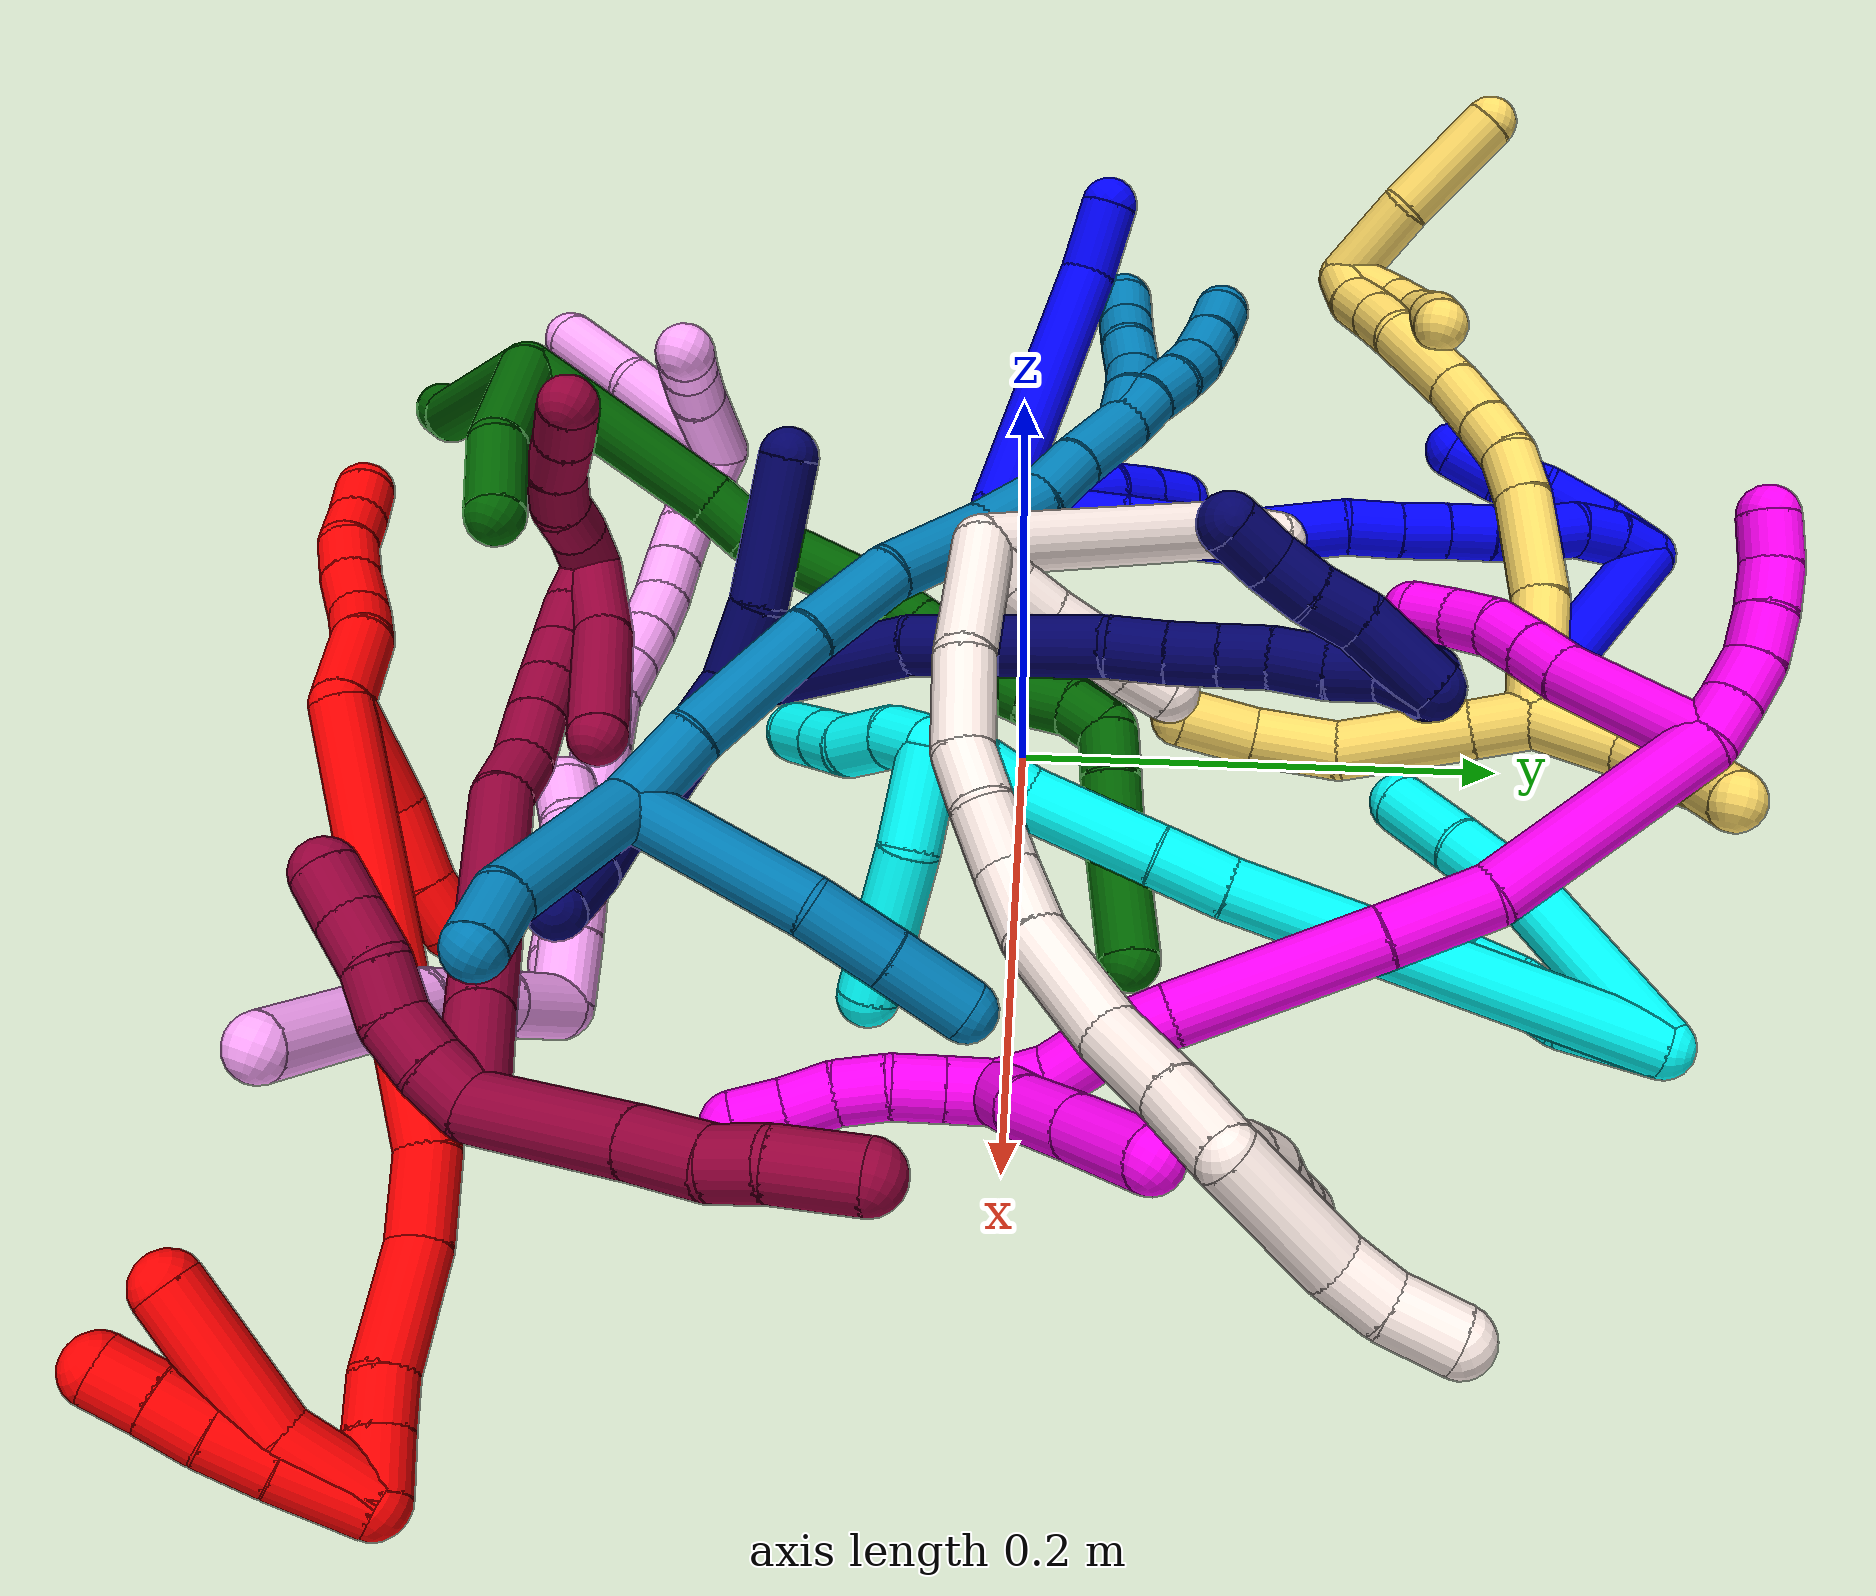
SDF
<sdf version="1.7">
 <world name="default">
  <plugin name="TubeGeneratorPlugin" filename="libtube_generator_plugin.so"/>
  <model name="photoneo_s_sensor">
   <static>1</static>
   <pose>0 0 2 1.57079 1.57079 3.14159</pose>
   <link name="link">
    <inertial><mass>0.1</mass></inertial>
    <sensor name="sensor" type="depth">
     <update_rate>30</update_rate>
     <camera>
      <horizontal_fov>1.22</horizontal_fov>
      <image><width>1920</width><height>1200</height><format>B8G8R8</format></image>
      <clip><near>0.1</near><far>4</far></clip>
      <depth_camera><output>points</output></depth_camera>
     </camera>
     <plugin name="camera_plugin" filename="libgazebo_ros_depth_camera.so">
      <baseline>0.2</baseline>
      <alwaysOn>1</alwaysOn>
      <updateRate>0.0</updateRate>
      <cameraName>camera_ir</cameraName>
      <imageTopicName>/camera/color/image_raw</imageTopicName>
      <cameraInfoTopicName>/camera/color/camera_info</cameraInfoTopicName>
      <depthImageTopicName>/camera/depth/image_raw</depthImageTopicName>
      <depthImageCameraInfoTopicName>/camera/depth/camera_info</depthImageCameraInfoTopicName>
      <pointCloudTopicName>/camera/depth/points</pointCloudTopicName>
      <frameName>fr_optical</frameName>
      <pointCloudCutoff>0.1</pointCloudCutoff>
      <pointCloudCutoffMax>2.0</pointCloudCutoffMax>
      <distortionK1>0</distortionK1>
      <distortionK2>0</distortionK2>
      <distortionK3>0</distortionK3>
      <distortionT1>0</distortionT1>
      <distortionT2>0</distortionT2>
      <CxPrime>0</CxPrime>
      <Cx>0</Cx>
      <Cy>0</Cy>
      <focalLength>0</focalLength>
      <hackBaseline>0</hackBaseline>
     </plugin>
    </sensor>
   </link>
  </model>
  <gravity>0 0 -9.8</gravity>
  <magnetic_field>6e-06 2.3e-05 -4.2e-05</magnetic_field>
  <atmosphere type="adiabatic"/>
  <physics name="default_physics" default="0" type="ode">
   <max_step_size>0.003</max_step_size>
   <real_time_factor>1</real_time_factor>
   <real_time_update_rate>1000</real_time_update_rate>
   <max_contacts>10000</max_contacts>
   <ode>
    <solver>
     <type>quick</type>
     <iters>100</iters>
     <sor>1.3</sor>
     <use_dynamic_moi_rescaling>0</use_dynamic_moi_rescaling>
    </solver>
    <constraints>
     <contact_max_correcting_vel>0</contact_max_correcting_vel>
     <contact_surface_layer>0.001</contact_surface_layer>
     <cfm>0</cfm>
     <erp>0.2</erp>
    </constraints>
   </ode>
  </physics>
  <scene><ambient>0.4 0.4 0.4 1</ambient><background>0.7 0.7 0.7 1</background><shadows>0</shadows></scene>
  <audio><device>default</device></audio>
  <spherical_coordinates>
   <surface_model>EARTH_WGS84</surface_model>
   <latitude_deg>0</latitude_deg>
   <longitude_deg>0</longitude_deg>
   <elevation>0</elevation>
   <heading_deg>0</heading_deg>
  </spherical_coordinates>
  <model name="bin">
   <static>1</static>
   <link name="bottom">
    <collision name="collision-bottom">
     <pose>0 0 -0.01 0 -0 0</pose>
     <geometry><box><size>0.8 0.6 0.02</size></box></geometry>
     <surface>
      <friction><ode><mu>100</mu><mu2>100</mu2></ode></friction>
      <contact><collide_bitmask>65535</collide_bitmask></contact>
     </surface>
    </collision>
   </link>
   <link name="west_wall">
    <collision name="collision-west_wall">
     <pose>-0.41 0 0.1 0 -0 0</pose>
     <geometry><box><size>0.02 0.6 0.2</size></box></geometry>
     <surface>
      <friction><ode><mu>100</mu><mu2>100</mu2></ode></friction>
      <contact><collide_bitmask>65535</collide_bitmask></contact>
     </surface>
    </collision>
   </link>
   <link name="east_wall">
    <collision name="collision-east_wall">
     <pose>0.41 0 0.1 0 -0 0</pose>
     <geometry><box><size>0.02 0.6 0.2</size></box></geometry>
     <surface>
      <friction><ode><mu>100</mu><mu2>100</mu2></ode></friction>
      <contact><collide_bitmask>65535</collide_bitmask></contact>
     </surface>
    </collision>
   </link>
   <link name="south_wall">
    <collision name="collision-south_wall">
     <pose>0 -0.31 0.1 0 -0 0</pose>
     <geometry><box><size>0.8 0.02 0.2</size></box></geometry>
     <surface>
      <friction><ode><mu>100</mu><mu2>100</mu2></ode></friction>
      <contact><collide_bitmask>65535</collide_bitmask></contact>
     </surface>
    </collision>
   </link>
   <link name="north_wall">
    <collision name="collision-north_wall">
     <pose>0 0.31 0.1 0 -0 0</pose>
     <geometry><box><size>0.8 0.02 0.2</size></box></geometry>
     <surface>
      <friction><ode><mu>100</mu><mu2>100</mu2></ode></friction>
      <contact><collide_bitmask>65535</collide_bitmask></contact>
     </surface>
    </collision>
   </link>
  </model>
  <model name="1">
   <static>0</static>
   <link name="1">
    <collision name="collision-cylinder-e_1_2_8">
     <pose>0.020605 0.04897 0.02482 -1.1017 0.359047 -0.222037</pose>
     <geometry><cylinder><radius>0.0125</radius><length>0.11728</length></cylinder></geometry>
     <surface>
      <friction><ode><mu>1.16</mu><mu2>1.16</mu2><slip1>0</slip1><slip2>0</slip2></ode></friction>
      <contact><ode><kp>1e+06</kp><kd>1</kd><max_vel>0</max_vel><min_depth>0.001</min_depth></ode></contact>
     </surface>
    </collision>
    <visual name="visual-cylinder-e_1_2_8">
     <pose>0.020605 0.04897 0.02482 -1.1017 0.359047 -0.222037</pose>
     <geometry><cylinder><radius>0.0125</radius><length>0.11728</length></cylinder></geometry>
     <material><ambient>0 0 1 1</ambient></material>
    </visual>
    <collision name="collision-cylinder-e_2_8_6">
     <pose>0.050462 0.108729 0.057743 -0.926556 0.601057 -0.30719</pose>
     <geometry><cylinder><radius>0.0125</radius><length>0.03272</length></cylinder></geometry>
     <surface>
      <friction><ode><mu>1.16</mu><mu2>1.16</mu2><slip1>0</slip1><slip2>0</slip2></ode></friction>
      <contact><ode><kp>1e+06</kp><kd>1</kd><max_vel>0</max_vel><min_depth>0.001</min_depth></ode></contact>
     </surface>
    </collision>
    <visual name="visual-cylinder-e_2_8_6">
     <pose>0.050462 0.108729 0.057743 -0.926556 0.601057 -0.30719</pose>
     <geometry><cylinder><radius>0.0125</radius><length>0.03272</length></cylinder></geometry>
     <material><ambient>0 0 1 1</ambient></material>
    </visual>
    <collision name="collision-cylinder-e_1_2_9">
     <pose>0.004299 0.013868 -0.008409 -2.1159 0.259141 -0.454793</pose>
     <geometry><cylinder><radius>0.0125</radius><length>0.033556</length></cylinder></geometry>
     <surface>
      <friction><ode><mu>1.16</mu><mu2>1.16</mu2><slip1>0</slip1><slip2>0</slip2></ode></friction>
      <contact><ode><kp>1e+06</kp><kd>1</kd><max_vel>0</max_vel><min_depth>0.001</min_depth></ode></contact>
     </surface>
    </collision>
    <visual name="visual-cylinder-e_1_2_9">
     <pose>0.004299 0.013868 -0.008409 -2.1159 0.259141 -0.454793</pose>
     <geometry><cylinder><radius>0.0125</radius><length>0.033556</length></cylinder></geometry>
     <material><ambient>0 0 1 1</ambient></material>
    </visual>
    <collision name="collision-cylinder-e_2_9_10">
     <pose>0.009053 0.037991 -0.022993 -2.11271 0.037952 -0.06713</pose>
     <geometry><cylinder><radius>0.0125</radius><length>0.023959</length></cylinder></geometry>
     <surface>
      <friction><ode><mu>1.16</mu><mu2>1.16</mu2><slip1>0</slip1><slip2>0</slip2></ode></friction>
      <contact><ode><kp>1e+06</kp><kd>1</kd><max_vel>0</max_vel><min_depth>0.001</min_depth></ode></contact>
     </surface>
    </collision>
    <visual name="visual-cylinder-e_2_9_10">
     <pose>0.009053 0.037991 -0.022993 -2.11271 0.037952 -0.06713</pose>
     <geometry><cylinder><radius>0.0125</radius><length>0.023959</length></cylinder></geometry>
     <material><ambient>0 0 1 1</ambient></material>
    </visual>
    <collision name="collision-cylinder-e_3_10_11">
     <pose>0.008209 0.05689 -0.035382 -2.19418 -0.121392 0.235988</pose>
     <geometry><cylinder><radius>0.0125</radius><length>0.021449</length></cylinder></geometry>
     <surface>
      <friction><ode><mu>1.16</mu><mu2>1.16</mu2><slip1>0</slip1><slip2>0</slip2></ode></friction>
      <contact><ode><kp>1e+06</kp><kd>1</kd><max_vel>0</max_vel><min_depth>0.001</min_depth></ode></contact>
     </surface>
    </collision>
    <visual name="visual-cylinder-e_3_10_11">
     <pose>0.008209 0.05689 -0.035382 -2.19418 -0.121392 0.235988</pose>
     <geometry><cylinder><radius>0.0125</radius><length>0.021449</length></cylinder></geometry>
     <material><ambient>0 0 1 1</ambient></material>
    </visual>
    <collision name="collision-cylinder-e_4_11_5">
     <pose>0.005617 0.073645 -0.048165 -2.25149 -0.123341 0.257491</pose>
     <geometry><cylinder><radius>0.0125</radius><length>0.021035</length></cylinder></geometry>
     <surface>
      <friction><ode><mu>1.16</mu><mu2>1.16</mu2><slip1>0</slip1><slip2>0</slip2></ode></friction>
      <contact><ode><kp>1e+06</kp><kd>1</kd><max_vel>0</max_vel><min_depth>0.001</min_depth></ode></contact>
     </surface>
    </collision>
    <visual name="visual-cylinder-e_4_11_5">
     <pose>0.005617 0.073645 -0.048165 -2.25149 -0.123341 0.257491</pose>
     <geometry><cylinder><radius>0.0125</radius><length>0.021035</length></cylinder></geometry>
     <material><ambient>0 0 1 1</ambient></material>
    </visual>
    <collision name="collision-cylinder-e_1_2_12">
     <pose>0.014008 0.011049 -0.021354 -2.66411 0.527549 -1.67464</pose>
     <geometry><cylinder><radius>0.0125</radius><length>0.055652</length></cylinder></geometry>
     <surface>
      <friction><ode><mu>1.16</mu><mu2>1.16</mu2><slip1>0</slip1><slip2>0</slip2></ode></friction>
      <contact><ode><kp>1e+06</kp><kd>1</kd><max_vel>0</max_vel><min_depth>0.001</min_depth></ode></contact>
     </surface>
    </collision>
    <visual name="visual-cylinder-e_1_2_12">
     <pose>0.014008 0.011049 -0.021354 -2.66411 0.527549 -1.67464</pose>
     <geometry><cylinder><radius>0.0125</radius><length>0.055652</length></cylinder></geometry>
     <material><ambient>0 0 1 1</ambient></material>
    </visual>
    <collision name="collision-cylinder-e_2_12_13">
     <pose>0.036424 0.037188 -0.062841 -2.49841 0.322484 -0.90836</pose>
     <geometry><cylinder><radius>0.0125</radius><length>0.053058</length></cylinder></geometry>
     <surface>
      <friction><ode><mu>1.16</mu><mu2>1.16</mu2><slip1>0</slip1><slip2>0</slip2></ode></friction>
      <contact><ode><kp>1e+06</kp><kd>1</kd><max_vel>0</max_vel><min_depth>0.001</min_depth></ode></contact>
     </surface>
    </collision>
    <visual name="visual-cylinder-e_2_12_13">
     <pose>0.036424 0.037188 -0.062841 -2.49841 0.322484 -0.90836</pose>
     <geometry><cylinder><radius>0.0125</radius><length>0.053058</length></cylinder></geometry>
     <material><ambient>0 0 1 1</ambient></material>
    </visual>
    <collision name="collision-cylinder-e_3_13_14">
     <pose>0.058412 0.065006 -0.096895 -2.40091 0.624032 -1.38644</pose>
     <geometry><cylinder><radius>0.0125</radius><length>0.046484</length></cylinder></geometry>
     <surface>
      <friction><ode><mu>1.16</mu><mu2>1.16</mu2><slip1>0</slip1><slip2>0</slip2></ode></friction>
      <contact><ode><kp>1e+06</kp><kd>1</kd><max_vel>0</max_vel><min_depth>0.001</min_depth></ode></contact>
     </surface>
    </collision>
    <visual name="visual-cylinder-e_3_13_14">
     <pose>0.058412 0.065006 -0.096895 -2.40091 0.624032 -1.38644</pose>
     <geometry><cylinder><radius>0.0125</radius><length>0.046484</length></cylinder></geometry>
     <material><ambient>0 0 1 1</ambient></material>
    </visual>
    <collision name="collision-cylinder-e_4_14_15">
     <pose>0.077005 0.084006 -0.119395 -2.51032 0.440654 -1.20231</pose>
     <geometry><cylinder><radius>0.0125</radius><length>0.023501</length></cylinder></geometry>
     <surface>
      <friction><ode><mu>1.16</mu><mu2>1.16</mu2><slip1>0</slip1><slip2>0</slip2></ode></friction>
      <contact><ode><kp>1e+06</kp><kd>1</kd><max_vel>0</max_vel><min_depth>0.001</min_depth></ode></contact>
     </surface>
    </collision>
    <visual name="visual-cylinder-e_4_14_15">
     <pose>0.077005 0.084006 -0.119395 -2.51032 0.440654 -1.20231</pose>
     <geometry><cylinder><radius>0.0125</radius><length>0.023501</length></cylinder></geometry>
     <material><ambient>0 0 1 1</ambient></material>
    </visual>
    <collision name="collision-cylinder-e_5_15_16">
     <pose>0.086666 0.096136 -0.135096 -2.45321 0.467024 -1.17167</pose>
     <geometry><cylinder><radius>0.0125</radius><length>0.020653</length></cylinder></geometry>
     <surface>
      <friction><ode><mu>1.16</mu><mu2>1.16</mu2><slip1>0</slip1><slip2>0</slip2></ode></friction>
      <contact><ode><kp>1e+06</kp><kd>1</kd><max_vel>0</max_vel><min_depth>0.001</min_depth></ode></contact>
     </surface>
    </collision>
    <visual name="visual-cylinder-e_5_15_16">
     <pose>0.086666 0.096136 -0.135096 -2.45321 0.467024 -1.17167</pose>
     <geometry><cylinder><radius>0.0125</radius><length>0.020653</length></cylinder></geometry>
     <material><ambient>0 0 1 1</ambient></material>
    </visual>
    <collision name="collision-cylinder-e_6_16_17">
     <pose>0.095617 0.107611 -0.14933 -2.47319 0.443149 -1.15104</pose>
     <geometry><cylinder><radius>0.0125</radius><length>0.020065</length></cylinder></geometry>
     <surface>
      <friction><ode><mu>1.16</mu><mu2>1.16</mu2><slip1>0</slip1><slip2>0</slip2></ode></friction>
      <contact><ode><kp>1e+06</kp><kd>1</kd><max_vel>0</max_vel><min_depth>0.001</min_depth></ode></contact>
     </surface>
    </collision>
    <visual name="visual-cylinder-e_6_16_17">
     <pose>0.095617 0.107611 -0.14933 -2.47319 0.443149 -1.15104</pose>
     <geometry><cylinder><radius>0.0125</radius><length>0.020065</length></cylinder></geometry>
     <material><ambient>0 0 1 1</ambient></material>
    </visual>
    <collision name="collision-cylinder-e_7_17_18">
     <pose>0.103767 0.119257 -0.163432 -2.42976 0.395033 -0.987692</pose>
     <geometry><cylinder><radius>0.0125</radius><length>0.02</length></cylinder></geometry>
     <surface>
      <friction><ode><mu>1.16</mu><mu2>1.16</mu2><slip1>0</slip1><slip2>0</slip2></ode></friction>
      <contact><ode><kp>1e+06</kp><kd>1</kd><max_vel>0</max_vel><min_depth>0.001</min_depth></ode></contact>
     </surface>
    </collision>
    <visual name="visual-cylinder-e_7_17_18">
     <pose>0.103767 0.119257 -0.163432 -2.42976 0.395033 -0.987692</pose>
     <geometry><cylinder><radius>0.0125</radius><length>0.02</length></cylinder></geometry>
     <material><ambient>0 0 1 1</ambient></material>
    </visual>
    <collision name="collision-cylinder-e_8_18_19">
     <pose>0.110499 0.133209 -0.176259 -2.20598 0.284974 -0.553354</pose>
     <geometry><cylinder><radius>0.0125</radius><length>0.02051</length></cylinder></geometry>
     <surface>
      <friction><ode><mu>1.16</mu><mu2>1.16</mu2><slip1>0</slip1><slip2>0</slip2></ode></friction>
      <contact><ode><kp>1e+06</kp><kd>1</kd><max_vel>0</max_vel><min_depth>0.001</min_depth></ode></contact>
     </surface>
    </collision>
    <visual name="visual-cylinder-e_8_18_19">
     <pose>0.110499 0.133209 -0.176259 -2.20598 0.284974 -0.553354</pose>
     <geometry><cylinder><radius>0.0125</radius><length>0.02051</length></cylinder></geometry>
     <material><ambient>0 0 1 1</ambient></material>
    </visual>
    <collision name="collision-cylinder-e_9_19_20">
     <pose>0.114701 0.147438 -0.189763 -2.45298 0.13211 -0.364849</pose>
     <geometry><cylinder><radius>0.0125</radius><length>0.020027</length></cylinder></geometry>
     <surface>
      <friction><ode><mu>1.16</mu><mu2>1.16</mu2><slip1>0</slip1><slip2>0</slip2></ode></friction>
      <contact><ode><kp>1e+06</kp><kd>1</kd><max_vel>0</max_vel><min_depth>0.001</min_depth></ode></contact>
     </surface>
    </collision>
    <visual name="visual-cylinder-e_9_19_20">
     <pose>0.114701 0.147438 -0.189763 -2.45298 0.13211 -0.364849</pose>
     <geometry><cylinder><radius>0.0125</radius><length>0.020027</length></cylinder></geometry>
     <material><ambient>0 0 1 1</ambient></material>
    </visual>
    <collision name="collision-cylinder-e_10_20_1">
     <pose>0.116206 0.158238 -0.206387 -2.67684 0.018581 -0.078476</pose>
     <geometry><cylinder><radius>0.0125</radius><length>0.02005</length></cylinder></geometry>
     <surface>
      <friction><ode><mu>1.16</mu><mu2>1.16</mu2><slip1>0</slip1><slip2>0</slip2></ode></friction>
      <contact><ode><kp>1e+06</kp><kd>1</kd><max_vel>0</max_vel><min_depth>0.001</min_depth></ode></contact>
     </surface>
    </collision>
    <visual name="visual-cylinder-e_10_20_1">
     <pose>0.116206 0.158238 -0.206387 -2.67684 0.018581 -0.078476</pose>
     <geometry><cylinder><radius>0.0125</radius><length>0.02005</length></cylinder></geometry>
     <material><ambient>0 0 1 1</ambient></material>
    </visual>
    <collision name="collision-cylinder-e_1_1_21">
     <pose>0.114046 0.161091 -0.202998 0.132026 -0.186203 -0.012345</pose>
     <geometry><cylinder><radius>0.0125</radius><length>0.025353</length></cylinder></geometry>
     <surface>
      <friction><ode><mu>1.16</mu><mu2>1.16</mu2><slip1>0</slip1><slip2>0</slip2></ode></friction>
      <contact><ode><kp>1e+06</kp><kd>1</kd><max_vel>0</max_vel><min_depth>0.001</min_depth></ode></contact>
     </surface>
    </collision>
    <visual name="visual-cylinder-e_1_1_21">
     <pose>0.114046 0.161091 -0.202998 0.132026 -0.186203 -0.012345</pose>
     <geometry><cylinder><radius>0.0125</radius><length>0.025353</length></cylinder></geometry>
     <material><ambient>0 0 1 1</ambient></material>
    </visual>
    <collision name="collision-cylinder-e_2_21_22">
     <pose>0.107831 0.156957 -0.176677 0.176627 -0.266032 -0.023694</pose>
     <geometry><cylinder><radius>0.0125</radius><length>0.02942</length></cylinder></geometry>
     <surface>
      <friction><ode><mu>1.16</mu><mu2>1.16</mu2><slip1>0</slip1><slip2>0</slip2></ode></friction>
      <contact><ode><kp>1e+06</kp><kd>1</kd><max_vel>0</max_vel><min_depth>0.001</min_depth></ode></contact>
     </surface>
    </collision>
    <visual name="visual-cylinder-e_2_21_22">
     <pose>0.107831 0.156957 -0.176677 0.176627 -0.266032 -0.023694</pose>
     <geometry><cylinder><radius>0.0125</radius><length>0.02942</length></cylinder></geometry>
     <material><ambient>0 0 1 1</ambient></material>
    </visual>
    <collision name="collision-cylinder-e_3_22_23">
     <pose>0.099045 0.152829 -0.153506 0.175837 -0.484654 -0.04357</pose>
     <geometry><cylinder><radius>0.0125</radius><length>0.021118</length></cylinder></geometry>
     <surface>
      <friction><ode><mu>1.16</mu><mu2>1.16</mu2><slip1>0</slip1><slip2>0</slip2></ode></friction>
      <contact><ode><kp>1e+06</kp><kd>1</kd><max_vel>0</max_vel><min_depth>0.001</min_depth></ode></contact>
     </surface>
    </collision>
    <visual name="visual-cylinder-e_3_22_23">
     <pose>0.099045 0.152829 -0.153506 0.175837 -0.484654 -0.04357</pose>
     <geometry><cylinder><radius>0.0125</radius><length>0.021118</length></cylinder></geometry>
     <material><ambient>0 0 1 1</ambient></material>
    </visual>
    <collision name="collision-cylinder-e_4_23_4">
     <pose>0.089818 0.150546 -0.133068 0.057617 -0.365404 -0.010648</pose>
     <geometry><cylinder><radius>0.0125</radius><length>0.024109</length></cylinder></geometry>
     <surface>
      <friction><ode><mu>1.16</mu><mu2>1.16</mu2><slip1>0</slip1><slip2>0</slip2></ode></friction>
      <contact><ode><kp>1e+06</kp><kd>1</kd><max_vel>0</max_vel><min_depth>0.001</min_depth></ode></contact>
     </surface>
    </collision>
    <visual name="visual-cylinder-e_4_23_4">
     <pose>0.089818 0.150546 -0.133068 0.057617 -0.365404 -0.010648</pose>
     <geometry><cylinder><radius>0.0125</radius><length>0.024109</length></cylinder></geometry>
     <material><ambient>0 0 1 1</ambient></material>
    </visual>
    <collision name="collision-cylinder-e_1_1_24">
     <pose>0.110425 0.123927 -0.215348 1.57082 -0.15258 -0.152583</pose>
     <geometry><cylinder><radius>0.0125</radius><length>0.07852</length></cylinder></geometry>
     <surface>
      <friction><ode><mu>1.16</mu><mu2>1.16</mu2><slip1>0</slip1><slip2>0</slip2></ode></friction>
      <contact><ode><kp>1e+06</kp><kd>1</kd><max_vel>0</max_vel><min_depth>0.001</min_depth></ode></contact>
     </surface>
    </collision>
    <visual name="visual-cylinder-e_1_1_24">
     <pose>0.110425 0.123927 -0.215348 1.57082 -0.15258 -0.152583</pose>
     <geometry><cylinder><radius>0.0125</radius><length>0.07852</length></cylinder></geometry>
     <material><ambient>0 0 1 1</ambient></material>
    </visual>
    <collision name="collision-cylinder-e_2_24_3">
     <pose>0.10604 0.074635 -0.213659 1.41099 0.147837 0.12598</pose>
     <geometry><cylinder><radius>0.0125</radius><length>0.02148</length></cylinder></geometry>
     <surface>
      <friction><ode><mu>1.16</mu><mu2>1.16</mu2><slip1>0</slip1><slip2>0</slip2></ode></friction>
      <contact><ode><kp>1e+06</kp><kd>1</kd><max_vel>0</max_vel><min_depth>0.001</min_depth></ode></contact>
     </surface>
    </collision>
    <visual name="visual-cylinder-e_2_24_3">
     <pose>0.10604 0.074635 -0.213659 1.41099 0.147837 0.12598</pose>
     <geometry><cylinder><radius>0.0125</radius><length>0.02148</length></cylinder></geometry>
     <material><ambient>0 0 1 1</ambient></material>
    </visual>
    <collision name="collision-sphere-3">
     <pose>0.107622 0.064148 -0.211968 0 -0 0</pose>
     <geometry><sphere><radius>0.0125</radius></sphere></geometry>
     <surface>
      <friction><ode><mu>1.16</mu><mu2>1.16</mu2><slip1>0</slip1><slip2>0</slip2></ode></friction>
      <contact><ode><kp>1e+06</kp><kd>1</kd><max_vel>0</max_vel><min_depth>0.001</min_depth></ode></contact>
     </surface>
    </collision>
    <visual name="visual-sphere-3">
     <pose>0.107622 0.064148 -0.211968 0 -0 0</pose>
     <geometry><sphere><radius>0.0125</radius></sphere></geometry>
     <material><ambient>0 0 1 1</ambient></material>
    </visual>
    <collision name="collision-sphere-24">
     <pose>0.104458 0.085123 -0.215349 0 -0 0</pose>
     <geometry><sphere><radius>0.0125</radius></sphere></geometry>
     <surface>
      <friction><ode><mu>1.16</mu><mu2>1.16</mu2><slip1>0</slip1><slip2>0</slip2></ode></friction>
      <contact><ode><kp>1e+06</kp><kd>1</kd><max_vel>0</max_vel><min_depth>0.001</min_depth></ode></contact>
     </surface>
    </collision>
    <visual name="visual-sphere-24">
     <pose>0.104458 0.085123 -0.215349 0 -0 0</pose>
     <geometry><sphere><radius>0.0125</radius></sphere></geometry>
     <material><ambient>0 0 1 1</ambient></material>
    </visual>
    <collision name="collision-sphere-4">
     <pose>0.085511 0.149898 -0.121828 0 -0 0</pose>
     <geometry><sphere><radius>0.0125</radius></sphere></geometry>
     <surface>
      <friction><ode><mu>1.16</mu><mu2>1.16</mu2><slip1>0</slip1><slip2>0</slip2></ode></friction>
      <contact><ode><kp>1e+06</kp><kd>1</kd><max_vel>0</max_vel><min_depth>0.001</min_depth></ode></contact>
     </surface>
    </collision>
    <visual name="visual-sphere-4">
     <pose>0.085511 0.149898 -0.121828 0 -0 0</pose>
     <geometry><sphere><radius>0.0125</radius></sphere></geometry>
     <material><ambient>0 0 1 1</ambient></material>
    </visual>
    <collision name="collision-sphere-23">
     <pose>0.094125 0.151194 -0.144307 0 -0 0</pose>
     <geometry><sphere><radius>0.0125</radius></sphere></geometry>
     <surface>
      <friction><ode><mu>1.16</mu><mu2>1.16</mu2><slip1>0</slip1><slip2>0</slip2></ode></friction>
      <contact><ode><kp>1e+06</kp><kd>1</kd><max_vel>0</max_vel><min_depth>0.001</min_depth></ode></contact>
     </surface>
    </collision>
    <visual name="visual-sphere-23">
     <pose>0.094125 0.151194 -0.144307 0 -0 0</pose>
     <geometry><sphere><radius>0.0125</radius></sphere></geometry>
     <material><ambient>0 0 1 1</ambient></material>
    </visual>
    <collision name="collision-sphere-22">
     <pose>0.103964 0.154463 -0.162705 0 -0 0</pose>
     <geometry><sphere><radius>0.0125</radius></sphere></geometry>
     <surface>
      <friction><ode><mu>1.16</mu><mu2>1.16</mu2><slip1>0</slip1><slip2>0</slip2></ode></friction>
      <contact><ode><kp>1e+06</kp><kd>1</kd><max_vel>0</max_vel><min_depth>0.001</min_depth></ode></contact>
     </surface>
    </collision>
    <visual name="visual-sphere-22">
     <pose>0.103964 0.154463 -0.162705 0 -0 0</pose>
     <geometry><sphere><radius>0.0125</radius></sphere></geometry>
     <material><ambient>0 0 1 1</ambient></material>
    </visual>
    <collision name="collision-sphere-21">
     <pose>0.111699 0.159451 -0.190649 0 -0 0</pose>
     <geometry><sphere><radius>0.0125</radius></sphere></geometry>
     <surface>
      <friction><ode><mu>1.16</mu><mu2>1.16</mu2><slip1>0</slip1><slip2>0</slip2></ode></friction>
      <contact><ode><kp>1e+06</kp><kd>1</kd><max_vel>0</max_vel><min_depth>0.001</min_depth></ode></contact>
     </surface>
    </collision>
    <visual name="visual-sphere-21">
     <pose>0.111699 0.159451 -0.190649 0 -0 0</pose>
     <geometry><sphere><radius>0.0125</radius></sphere></geometry>
     <material><ambient>0 0 1 1</ambient></material>
    </visual>
    <collision name="collision-sphere-1">
     <pose>0.116392 0.162731 -0.215347 0 -0 0</pose>
     <geometry><sphere><radius>0.0125</radius></sphere></geometry>
     <surface>
      <friction><ode><mu>1.16</mu><mu2>1.16</mu2><slip1>0</slip1><slip2>0</slip2></ode></friction>
      <contact><ode><kp>1e+06</kp><kd>1</kd><max_vel>0</max_vel><min_depth>0.001</min_depth></ode></contact>
     </surface>
    </collision>
    <visual name="visual-sphere-1">
     <pose>0.116392 0.162731 -0.215347 0 -0 0</pose>
     <geometry><sphere><radius>0.0125</radius></sphere></geometry>
     <material><ambient>0 0 1 1</ambient></material>
    </visual>
    <collision name="collision-sphere-11">
     <pose>0.006911 0.065533 -0.041597 0 -0 0</pose>
     <geometry><sphere><radius>0.0125</radius></sphere></geometry>
     <surface>
      <friction><ode><mu>1.16</mu><mu2>1.16</mu2><slip1>0</slip1><slip2>0</slip2></ode></friction>
      <contact><ode><kp>1e+06</kp><kd>1</kd><max_vel>0</max_vel><min_depth>0.001</min_depth></ode></contact>
     </surface>
    </collision>
    <visual name="visual-sphere-11">
     <pose>0.006911 0.065533 -0.041597 0 -0 0</pose>
     <geometry><sphere><radius>0.0125</radius></sphere></geometry>
     <material><ambient>0 0 1 1</ambient></material>
    </visual>
    <collision name="collision-sphere-10">
     <pose>0.009508 0.048247 -0.029167 0 -0 0</pose>
     <geometry><sphere><radius>0.0125</radius></sphere></geometry>
     <surface>
      <friction><ode><mu>1.16</mu><mu2>1.16</mu2><slip1>0</slip1><slip2>0</slip2></ode></friction>
      <contact><ode><kp>1e+06</kp><kd>1</kd><max_vel>0</max_vel><min_depth>0.001</min_depth></ode></contact>
     </surface>
    </collision>
    <visual name="visual-sphere-10">
     <pose>0.009508 0.048247 -0.029167 0 -0 0</pose>
     <geometry><sphere><radius>0.0125</radius></sphere></geometry>
     <material><ambient>0 0 1 1</ambient></material>
    </visual>
    <collision name="collision-sphere-6">
     <pose>0.059714 0.119517 0.065846 0 -0 0</pose>
     <geometry><sphere><radius>0.0125</radius></sphere></geometry>
     <surface>
      <friction><ode><mu>1.16</mu><mu2>1.16</mu2><slip1>0</slip1><slip2>0</slip2></ode></friction>
      <contact><ode><kp>1e+06</kp><kd>1</kd><max_vel>0</max_vel><min_depth>0.001</min_depth></ode></contact>
     </surface>
    </collision>
    <visual name="visual-sphere-6">
     <pose>0.059714 0.119517 0.065846 0 -0 0</pose>
     <geometry><sphere><radius>0.0125</radius></sphere></geometry>
     <material><ambient>0 0 1 1</ambient></material>
    </visual>
    <collision name="collision-sphere-9">
     <pose>0.008599 0.027735 -0.016818 0 -0 0</pose>
     <geometry><sphere><radius>0.0125</radius></sphere></geometry>
     <surface>
      <friction><ode><mu>1.16</mu><mu2>1.16</mu2><slip1>0</slip1><slip2>0</slip2></ode></friction>
      <contact><ode><kp>1e+06</kp><kd>1</kd><max_vel>0</max_vel><min_depth>0.001</min_depth></ode></contact>
     </surface>
    </collision>
    <visual name="visual-sphere-9">
     <pose>0.008599 0.027735 -0.016818 0 -0 0</pose>
     <geometry><sphere><radius>0.0125</radius></sphere></geometry>
     <material><ambient>0 0 1 1</ambient></material>
    </visual>
    <collision name="collision-sphere-2">
     <geometry><sphere><radius>0.0125</radius></sphere></geometry>
     <surface>
      <friction><ode><mu>1.16</mu><mu2>1.16</mu2><slip1>0</slip1><slip2>0</slip2></ode></friction>
      <contact><ode><kp>1e+06</kp><kd>1</kd><max_vel>0</max_vel><min_depth>0.001</min_depth></ode></contact>
     </surface>
    </collision>
    <visual name="visual-sphere-2">
     <geometry><sphere><radius>0.0125</radius></sphere></geometry>
     <material><ambient>0 0 1 1</ambient></material>
    </visual>
    <collision name="collision-sphere-19">
     <pose>0.113382 0.14113 -0.182098 0 -0 0</pose>
     <geometry><sphere><radius>0.0125</radius></sphere></geometry>
     <surface>
      <friction><ode><mu>1.16</mu><mu2>1.16</mu2><slip1>0</slip1><slip2>0</slip2></ode></friction>
      <contact><ode><kp>1e+06</kp><kd>1</kd><max_vel>0</max_vel><min_depth>0.001</min_depth></ode></contact>
     </surface>
    </collision>
    <visual name="visual-sphere-19">
     <pose>0.113382 0.14113 -0.182098 0 -0 0</pose>
     <geometry><sphere><radius>0.0125</radius></sphere></geometry>
     <material><ambient>0 0 1 1</ambient></material>
    </visual>
    <collision name="collision-sphere-8">
     <pose>0.04121 0.097941 0.049639 0 -0 0</pose>
     <geometry><sphere><radius>0.0125</radius></sphere></geometry>
     <surface>
      <friction><ode><mu>1.16</mu><mu2>1.16</mu2><slip1>0</slip1><slip2>0</slip2></ode></friction>
      <contact><ode><kp>1e+06</kp><kd>1</kd><max_vel>0</max_vel><min_depth>0.001</min_depth></ode></contact>
     </surface>
    </collision>
    <visual name="visual-sphere-8">
     <pose>0.04121 0.097941 0.049639 0 -0 0</pose>
     <geometry><sphere><radius>0.0125</radius></sphere></geometry>
     <material><ambient>0 0 1 1</ambient></material>
    </visual>
    <collision name="collision-sphere-5">
     <pose>0.004323 0.081756 -0.054734 0 -0 0</pose>
     <geometry><sphere><radius>0.0125</radius></sphere></geometry>
     <surface>
      <friction><ode><mu>1.16</mu><mu2>1.16</mu2><slip1>0</slip1><slip2>0</slip2></ode></friction>
      <contact><ode><kp>1e+06</kp><kd>1</kd><max_vel>0</max_vel><min_depth>0.001</min_depth></ode></contact>
     </surface>
    </collision>
    <visual name="visual-sphere-5">
     <pose>0.004323 0.081756 -0.054734 0 -0 0</pose>
     <geometry><sphere><radius>0.0125</radius></sphere></geometry>
     <material><ambient>0 0 1 1</ambient></material>
    </visual>
    <collision name="collision-sphere-12">
     <pose>0.028016 0.022097 -0.042707 0 -0 0</pose>
     <geometry><sphere><radius>0.0125</radius></sphere></geometry>
     <surface>
      <friction><ode><mu>1.16</mu><mu2>1.16</mu2><slip1>0</slip1><slip2>0</slip2></ode></friction>
      <contact><ode><kp>1e+06</kp><kd>1</kd><max_vel>0</max_vel><min_depth>0.001</min_depth></ode></contact>
     </surface>
    </collision>
    <visual name="visual-sphere-12">
     <pose>0.028016 0.022097 -0.042707 0 -0 0</pose>
     <geometry><sphere><radius>0.0125</radius></sphere></geometry>
     <material><ambient>0 0 1 1</ambient></material>
    </visual>
    <collision name="collision-sphere-13">
     <pose>0.044831 0.052278 -0.082975 0 -0 0</pose>
     <geometry><sphere><radius>0.0125</radius></sphere></geometry>
     <surface>
      <friction><ode><mu>1.16</mu><mu2>1.16</mu2><slip1>0</slip1><slip2>0</slip2></ode></friction>
      <contact><ode><kp>1e+06</kp><kd>1</kd><max_vel>0</max_vel><min_depth>0.001</min_depth></ode></contact>
     </surface>
    </collision>
    <visual name="visual-sphere-13">
     <pose>0.044831 0.052278 -0.082975 0 -0 0</pose>
     <geometry><sphere><radius>0.0125</radius></sphere></geometry>
     <material><ambient>0 0 1 1</ambient></material>
    </visual>
    <collision name="collision-sphere-14">
     <pose>0.071993 0.077734 -0.110815 0 -0 0</pose>
     <geometry><sphere><radius>0.0125</radius></sphere></geometry>
     <surface>
      <friction><ode><mu>1.16</mu><mu2>1.16</mu2><slip1>0</slip1><slip2>0</slip2></ode></friction>
      <contact><ode><kp>1e+06</kp><kd>1</kd><max_vel>0</max_vel><min_depth>0.001</min_depth></ode></contact>
     </surface>
    </collision>
    <visual name="visual-sphere-14">
     <pose>0.071993 0.077734 -0.110815 0 -0 0</pose>
     <geometry><sphere><radius>0.0125</radius></sphere></geometry>
     <material><ambient>0 0 1 1</ambient></material>
    </visual>
    <collision name="collision-sphere-15">
     <pose>0.082016 0.090279 -0.127975 0 -0 0</pose>
     <geometry><sphere><radius>0.0125</radius></sphere></geometry>
     <surface>
      <friction><ode><mu>1.16</mu><mu2>1.16</mu2><slip1>0</slip1><slip2>0</slip2></ode></friction>
      <contact><ode><kp>1e+06</kp><kd>1</kd><max_vel>0</max_vel><min_depth>0.001</min_depth></ode></contact>
     </surface>
    </collision>
    <visual name="visual-sphere-15">
     <pose>0.082016 0.090279 -0.127975 0 -0 0</pose>
     <geometry><sphere><radius>0.0125</radius></sphere></geometry>
     <material><ambient>0 0 1 1</ambient></material>
    </visual>
    <collision name="collision-sphere-16">
     <pose>0.091315 0.101994 -0.142217 0 -0 0</pose>
     <geometry><sphere><radius>0.0125</radius></sphere></geometry>
     <surface>
      <friction><ode><mu>1.16</mu><mu2>1.16</mu2><slip1>0</slip1><slip2>0</slip2></ode></friction>
      <contact><ode><kp>1e+06</kp><kd>1</kd><max_vel>0</max_vel><min_depth>0.001</min_depth></ode></contact>
     </surface>
    </collision>
    <visual name="visual-sphere-16">
     <pose>0.091315 0.101994 -0.142217 0 -0 0</pose>
     <geometry><sphere><radius>0.0125</radius></sphere></geometry>
     <material><ambient>0 0 1 1</ambient></material>
    </visual>
    <collision name="collision-sphere-17">
     <pose>0.099919 0.113228 -0.156443 0 -0 0</pose>
     <geometry><sphere><radius>0.0125</radius></sphere></geometry>
     <surface>
      <friction><ode><mu>1.16</mu><mu2>1.16</mu2><slip1>0</slip1><slip2>0</slip2></ode></friction>
      <contact><ode><kp>1e+06</kp><kd>1</kd><max_vel>0</max_vel><min_depth>0.001</min_depth></ode></contact>
     </surface>
    </collision>
    <visual name="visual-sphere-17">
     <pose>0.099919 0.113228 -0.156443 0 -0 0</pose>
     <geometry><sphere><radius>0.0125</radius></sphere></geometry>
     <material><ambient>0 0 1 1</ambient></material>
    </visual>
    <collision name="collision-sphere-18">
     <pose>0.107616 0.125287 -0.17042 0 -0 0</pose>
     <geometry><sphere><radius>0.0125</radius></sphere></geometry>
     <surface>
      <friction><ode><mu>1.16</mu><mu2>1.16</mu2><slip1>0</slip1><slip2>0</slip2></ode></friction>
      <contact><ode><kp>1e+06</kp><kd>1</kd><max_vel>0</max_vel><min_depth>0.001</min_depth></ode></contact>
     </surface>
    </collision>
    <visual name="visual-sphere-18">
     <pose>0.107616 0.125287 -0.17042 0 -0 0</pose>
     <geometry><sphere><radius>0.0125</radius></sphere></geometry>
     <material><ambient>0 0 1 1</ambient></material>
    </visual>
    <collision name="collision-sphere-20">
     <pose>0.11602 0.153746 -0.197427 0 -0 0</pose>
     <geometry><sphere><radius>0.0125</radius></sphere></geometry>
     <surface>
      <friction><ode><mu>1.16</mu><mu2>1.16</mu2><slip1>0</slip1><slip2>0</slip2></ode></friction>
      <contact><ode><kp>1e+06</kp><kd>1</kd><max_vel>0</max_vel><min_depth>0.001</min_depth></ode></contact>
     </surface>
    </collision>
    <visual name="visual-sphere-20">
     <pose>0.11602 0.153746 -0.197427 0 -0 0</pose>
     <geometry><sphere><radius>0.0125</radius></sphere></geometry>
     <material><ambient>0 0 1 1</ambient></material>
    </visual>
    <inertial>
     <pose>0.061209 0.084413 -0.091385 0 -0 0</pose>
     <mass>0.75</mass>
     <inertia>
      <ixx>0.000141</ixx>
      <ixy>0</ixy>
      <ixz>0</ixz>
      <iyy>2.2e-05</iyy>
      <iyz>0</iyz>
      <izz>-0.000181</izz>
     </inertia>
    </inertial>
   </link>
   <pose>-0.10683 -0.014896 0.044372 -0.18681 -1.01214 1.18706</pose>
  </model>
  <model name="2">
   <static>0</static>
   <link name="2">
    <collision name="collision-cylinder-e_1_2_8">
     <pose>-0.020827 -0.005021 0.000419 1.48746 -1.33346 -1.25324</pose>
     <geometry><cylinder><radius>0.0125</radius><length>0.042856</length></cylinder></geometry>
     <surface>
      <friction><ode><mu>1.16</mu><mu2>1.16</mu2><slip1>0</slip1><slip2>0</slip2></ode></friction>
      <contact><ode><kp>1e+06</kp><kd>1</kd><max_vel>0</max_vel><min_depth>0.001</min_depth></ode></contact>
     </surface>
    </collision>
    <visual name="visual-cylinder-e_1_2_8">
     <pose>-0.020827 -0.005021 0.000419 1.48746 -1.33346 -1.25324</pose>
     <geometry><cylinder><radius>0.0125</radius><length>0.042856</length></cylinder></geometry>
     <material><ambient>1 0 0 1</ambient></material>
    </visual>
    <collision name="collision-cylinder-e_2_8_9">
     <pose>-0.052821 -0.00957 0.000661 -1.93104 -1.52571 1.88851</pose>
     <geometry><cylinder><radius>0.0125</radius><length>0.022357</length></cylinder></geometry>
     <surface>
      <friction><ode><mu>1.16</mu><mu2>1.16</mu2><slip1>0</slip1><slip2>0</slip2></ode></friction>
      <contact><ode><kp>1e+06</kp><kd>1</kd><max_vel>0</max_vel><min_depth>0.001</min_depth></ode></contact>
     </surface>
    </collision>
    <visual name="visual-cylinder-e_2_8_9">
     <pose>-0.052821 -0.00957 0.000661 -1.93104 -1.52571 1.88851</pose>
     <geometry><cylinder><radius>0.0125</radius><length>0.022357</length></cylinder></geometry>
     <material><ambient>1 0 0 1</ambient></material>
    </visual>
    <collision name="collision-cylinder-e_3_9_10">
     <pose>-0.075788 -0.009599 -0.002636 2.98227 -1.30912 -2.93429</pose>
     <geometry><cylinder><radius>0.0125</radius><length>0.02443</length></cylinder></geometry>
     <surface>
      <friction><ode><mu>1.16</mu><mu2>1.16</mu2><slip1>0</slip1><slip2>0</slip2></ode></friction>
      <contact><ode><kp>1e+06</kp><kd>1</kd><max_vel>0</max_vel><min_depth>0.001</min_depth></ode></contact>
     </surface>
    </collision>
    <visual name="visual-cylinder-e_3_9_10">
     <pose>-0.075788 -0.009599 -0.002636 2.98227 -1.30912 -2.93429</pose>
     <geometry><cylinder><radius>0.0125</radius><length>0.02443</length></cylinder></geometry>
     <material><ambient>1 0 0 1</ambient></material>
    </visual>
    <collision name="collision-cylinder-e_4_10_11">
     <pose>-0.097149 -0.011971 -0.008637 2.56568 -1.22599 -2.34448</pose>
     <geometry><cylinder><radius>0.0125</radius><length>0.02032</length></cylinder></geometry>
     <surface>
      <friction><ode><mu>1.16</mu><mu2>1.16</mu2><slip1>0</slip1><slip2>0</slip2></ode></friction>
      <contact><ode><kp>1e+06</kp><kd>1</kd><max_vel>0</max_vel><min_depth>0.001</min_depth></ode></contact>
     </surface>
    </collision>
    <visual name="visual-cylinder-e_4_10_11">
     <pose>-0.097149 -0.011971 -0.008637 2.56568 -1.22599 -2.34448</pose>
     <geometry><cylinder><radius>0.0125</radius><length>0.02032</length></cylinder></geometry>
     <material><ambient>1 0 0 1</ambient></material>
    </visual>
    <collision name="collision-cylinder-e_5_11_12">
     <pose>-0.116473 -0.016067 -0.011251 1.45176 -1.34507 -1.23057</pose>
     <geometry><cylinder><radius>0.0125</radius><length>0.020032</length></cylinder></geometry>
     <surface>
      <friction><ode><mu>1.16</mu><mu2>1.16</mu2><slip1>0</slip1><slip2>0</slip2></ode></friction>
      <contact><ode><kp>1e+06</kp><kd>1</kd><max_vel>0</max_vel><min_depth>0.001</min_depth></ode></contact>
     </surface>
    </collision>
    <visual name="visual-cylinder-e_5_11_12">
     <pose>-0.116473 -0.016067 -0.011251 1.45176 -1.34507 -1.23057</pose>
     <geometry><cylinder><radius>0.0125</radius><length>0.020032</length></cylinder></geometry>
     <material><ambient>1 0 0 1</ambient></material>
    </visual>
    <collision name="collision-cylinder-e_6_12_6">
     <pose>-0.135708 -0.021387 -0.011842 1.84118 -1.24407 -1.51187</pose>
     <geometry><cylinder><radius>0.0125</radius><length>0.020006</length></cylinder></geometry>
     <surface>
      <friction><ode><mu>1.16</mu><mu2>1.16</mu2><slip1>0</slip1><slip2>0</slip2></ode></friction>
      <contact><ode><kp>1e+06</kp><kd>1</kd><max_vel>0</max_vel><min_depth>0.001</min_depth></ode></contact>
     </surface>
    </collision>
    <visual name="visual-cylinder-e_6_12_6">
     <pose>-0.135708 -0.021387 -0.011842 1.84118 -1.24407 -1.51187</pose>
     <geometry><cylinder><radius>0.0125</radius><length>0.020006</length></cylinder></geometry>
     <material><ambient>1 0 0 1</ambient></material>
    </visual>
    <collision name="collision-cylinder-e_1_2_13">
     <pose>0.003701 0.006905 0.022001 -0.304131 0.159147 -0.024439</pose>
     <geometry><cylinder><radius>0.0125</radius><length>0.046709</length></cylinder></geometry>
     <surface>
      <friction><ode><mu>1.16</mu><mu2>1.16</mu2><slip1>0</slip1><slip2>0</slip2></ode></friction>
      <contact><ode><kp>1e+06</kp><kd>1</kd><max_vel>0</max_vel><min_depth>0.001</min_depth></ode></contact>
     </surface>
    </collision>
    <visual name="visual-cylinder-e_1_2_13">
     <pose>0.003701 0.006905 0.022001 -0.304131 0.159147 -0.024439</pose>
     <geometry><cylinder><radius>0.0125</radius><length>0.046709</length></cylinder></geometry>
     <material><ambient>1 0 0 1</ambient></material>
    </visual>
    <collision name="collision-cylinder-e_2_13_14">
     <pose>0.014252 0.018958 0.057773 -0.357689 0.436008 -0.08005</pose>
     <geometry><cylinder><radius>0.0125</radius><length>0.032437</length></cylinder></geometry>
     <surface>
      <friction><ode><mu>1.16</mu><mu2>1.16</mu2><slip1>0</slip1><slip2>0</slip2></ode></friction>
      <contact><ode><kp>1e+06</kp><kd>1</kd><max_vel>0</max_vel><min_depth>0.001</min_depth></ode></contact>
     </surface>
    </collision>
    <visual name="visual-cylinder-e_2_13_14">
     <pose>0.014252 0.018958 0.057773 -0.357689 0.436008 -0.08005</pose>
     <geometry><cylinder><radius>0.0125</radius><length>0.032437</length></cylinder></geometry>
     <material><ambient>1 0 0 1</ambient></material>
    </visual>
    <collision name="collision-cylinder-e_3_14_5">
     <pose>0.024635 0.025582 0.081242 -0.151092 0.345748 -0.026432</pose>
     <geometry><cylinder><radius>0.0125</radius><length>0.020854</length></cylinder></geometry>
     <surface>
      <friction><ode><mu>1.16</mu><mu2>1.16</mu2><slip1>0</slip1><slip2>0</slip2></ode></friction>
      <contact><ode><kp>1e+06</kp><kd>1</kd><max_vel>0</max_vel><min_depth>0.001</min_depth></ode></contact>
     </surface>
    </collision>
    <visual name="visual-cylinder-e_3_14_5">
     <pose>0.024635 0.025582 0.081242 -0.151092 0.345748 -0.026432</pose>
     <geometry><cylinder><radius>0.0125</radius><length>0.020854</length></cylinder></geometry>
     <material><ambient>1 0 0 1</ambient></material>
    </visual>
    <collision name="collision-cylinder-e_1_2_15">
     <pose>0.067342 0.0259 0.050114 -0.477006 0.873496 -0.226026</pose>
     <geometry><cylinder><radius>0.0125</radius><length>0.175695</length></cylinder></geometry>
     <surface>
      <friction><ode><mu>1.16</mu><mu2>1.16</mu2><slip1>0</slip1><slip2>0</slip2></ode></friction>
      <contact><ode><kp>1e+06</kp><kd>1</kd><max_vel>0</max_vel><min_depth>0.001</min_depth></ode></contact>
     </surface>
    </collision>
    <visual name="visual-cylinder-e_1_2_15">
     <pose>0.067342 0.0259 0.050114 -0.477006 0.873496 -0.226026</pose>
     <geometry><cylinder><radius>0.0125</radius><length>0.175695</length></cylinder></geometry>
     <material><ambient>1 0 0 1</ambient></material>
    </visual>
    <collision name="collision-cylinder-e_2_15_16">
     <pose>0.149126 0.059767 0.106166 -0.930427 0.968128 -0.51608</pose>
     <geometry><cylinder><radius>0.0125</radius><length>0.03506</length></cylinder></geometry>
     <surface>
      <friction><ode><mu>1.16</mu><mu2>1.16</mu2><slip1>0</slip1><slip2>0</slip2></ode></friction>
      <contact><ode><kp>1e+06</kp><kd>1</kd><max_vel>0</max_vel><min_depth>0.001</min_depth></ode></contact>
     </surface>
    </collision>
    <visual name="visual-cylinder-e_2_15_16">
     <pose>0.149126 0.059767 0.106166 -0.930427 0.968128 -0.51608</pose>
     <geometry><cylinder><radius>0.0125</radius><length>0.03506</length></cylinder></geometry>
     <material><ambient>1 0 0 1</ambient></material>
    </visual>
    <collision name="collision-cylinder-e_3_16_17">
     <pose>0.184096 0.078755 0.11498 -1.31542 1.06428 -0.853696</pose>
     <geometry><cylinder><radius>0.0125</radius><length>0.046951</length></cylinder></geometry>
     <surface>
      <friction><ode><mu>1.16</mu><mu2>1.16</mu2><slip1>0</slip1><slip2>0</slip2></ode></friction>
      <contact><ode><kp>1e+06</kp><kd>1</kd><max_vel>0</max_vel><min_depth>0.001</min_depth></ode></contact>
     </surface>
    </collision>
    <visual name="visual-cylinder-e_3_16_17">
     <pose>0.184096 0.078755 0.11498 -1.31542 1.06428 -0.853696</pose>
     <geometry><cylinder><radius>0.0125</radius><length>0.046951</length></cylinder></geometry>
     <material><ambient>1 0 0 1</ambient></material>
    </visual>
    <collision name="collision-cylinder-e_4_17_18">
     <pose>0.213565 0.093513 0.120536 -0.948888 1.09566 -0.607303</pose>
     <geometry><cylinder><radius>0.0125</radius><length>0.020109</length></cylinder></geometry>
     <surface>
      <friction><ode><mu>1.16</mu><mu2>1.16</mu2><slip1>0</slip1><slip2>0</slip2></ode></friction>
      <contact><ode><kp>1e+06</kp><kd>1</kd><max_vel>0</max_vel><min_depth>0.001</min_depth></ode></contact>
     </surface>
    </collision>
    <visual name="visual-cylinder-e_4_17_18">
     <pose>0.213565 0.093513 0.120536 -0.948888 1.09566 -0.607303</pose>
     <geometry><cylinder><radius>0.0125</radius><length>0.020109</length></cylinder></geometry>
     <material><ambient>1 0 0 1</ambient></material>
    </visual>
    <collision name="collision-cylinder-e_5_18_1">
     <pose>0.232415 0.101074 0.126412 -0.874562 1.10485 -0.561131</pose>
     <geometry><cylinder><radius>0.0125</radius><length>0.022184</length></cylinder></geometry>
     <surface>
      <friction><ode><mu>1.16</mu><mu2>1.16</mu2><slip1>0</slip1><slip2>0</slip2></ode></friction>
      <contact><ode><kp>1e+06</kp><kd>1</kd><max_vel>0</max_vel><min_depth>0.001</min_depth></ode></contact>
     </surface>
    </collision>
    <visual name="visual-cylinder-e_5_18_1">
     <pose>0.232415 0.101074 0.126412 -0.874562 1.10485 -0.561131</pose>
     <geometry><cylinder><radius>0.0125</radius><length>0.022184</length></cylinder></geometry>
     <material><ambient>1 0 0 1</ambient></material>
    </visual>
    <collision name="collision-cylinder-e_1_1_19">
     <pose>0.235185 0.110421 0.112767 -2.82472 -0.382942 1.7629</pose>
     <geometry><cylinder><radius>0.0125</radius><length>0.038215</length></cylinder></geometry>
     <surface>
      <friction><ode><mu>1.16</mu><mu2>1.16</mu2><slip1>0</slip1><slip2>0</slip2></ode></friction>
      <contact><ode><kp>1e+06</kp><kd>1</kd><max_vel>0</max_vel><min_depth>0.001</min_depth></ode></contact>
     </surface>
    </collision>
    <visual name="visual-cylinder-e_1_1_19">
     <pose>0.235185 0.110421 0.112767 -2.82472 -0.382942 1.7629</pose>
     <geometry><cylinder><radius>0.0125</radius><length>0.038215</length></cylinder></geometry>
     <material><ambient>1 0 0 1</ambient></material>
    </visual>
    <collision name="collision-cylinder-e_2_19_4">
     <pose>0.210815 0.11597 0.070285 -3.14054 -0.591699 3.13813</pose>
     <geometry><cylinder><radius>0.0125</radius><length>0.061785</length></cylinder></geometry>
     <surface>
      <friction><ode><mu>1.16</mu><mu2>1.16</mu2><slip1>0</slip1><slip2>0</slip2></ode></friction>
      <contact><ode><kp>1e+06</kp><kd>1</kd><max_vel>0</max_vel><min_depth>0.001</min_depth></ode></contact>
     </surface>
    </collision>
    <visual name="visual-cylinder-e_2_19_4">
     <pose>0.210815 0.11597 0.070285 -3.14054 -0.591699 3.13813</pose>
     <geometry><cylinder><radius>0.0125</radius><length>0.061785</length></cylinder></geometry>
     <material><ambient>1 0 0 1</ambient></material>
    </visual>
    <collision name="collision-cylinder-e_1_1_20">
     <pose>0.237484 0.11219 0.114906 -2.68116 -0.286853 1.10448</pose>
     <geometry><cylinder><radius>0.0125</radius><length>0.03422</length></cylinder></geometry>
     <surface>
      <friction><ode><mu>1.16</mu><mu2>1.16</mu2><slip1>0</slip1><slip2>0</slip2></ode></friction>
      <contact><ode><kp>1e+06</kp><kd>1</kd><max_vel>0</max_vel><min_depth>0.001</min_depth></ode></contact>
     </surface>
    </collision>
    <visual name="visual-cylinder-e_1_1_20">
     <pose>0.237484 0.11219 0.114906 -2.68116 -0.286853 1.10448</pose>
     <geometry><cylinder><radius>0.0125</radius><length>0.03422</length></cylinder></geometry>
     <material><ambient>1 0 0 1</ambient></material>
    </visual>
    <collision name="collision-cylinder-e_2_20_21">
     <pose>0.228562 0.124519 0.0899 -2.68695 -0.341817 1.28203</pose>
     <geometry><cylinder><radius>0.0125</radius><length>0.024349</length></cylinder></geometry>
     <surface>
      <friction><ode><mu>1.16</mu><mu2>1.16</mu2><slip1>0</slip1><slip2>0</slip2></ode></friction>
      <contact><ode><kp>1e+06</kp><kd>1</kd><max_vel>0</max_vel><min_depth>0.001</min_depth></ode></contact>
     </surface>
    </collision>
    <visual name="visual-cylinder-e_2_20_21">
     <pose>0.228562 0.124519 0.0899 -2.68695 -0.341817 1.28203</pose>
     <geometry><cylinder><radius>0.0125</radius><length>0.024349</length></cylinder></geometry>
     <material><ambient>1 0 0 1</ambient></material>
    </visual>
    <collision name="collision-cylinder-e_3_21_22">
     <pose>0.220188 0.13336 0.070883 -2.72989 -0.424214 1.60162</pose>
     <geometry><cylinder><radius>0.0125</radius><length>0.020862</length></cylinder></geometry>
     <surface>
      <friction><ode><mu>1.16</mu><mu2>1.16</mu2><slip1>0</slip1><slip2>0</slip2></ode></friction>
      <contact><ode><kp>1e+06</kp><kd>1</kd><max_vel>0</max_vel><min_depth>0.001</min_depth></ode></contact>
     </surface>
    </collision>
    <visual name="visual-cylinder-e_3_21_22">
     <pose>0.220188 0.13336 0.070883 -2.72989 -0.424214 1.60162</pose>
     <geometry><cylinder><radius>0.0125</radius><length>0.020862</length></cylinder></geometry>
     <material><ambient>1 0 0 1</ambient></material>
    </visual>
    <collision name="collision-cylinder-e_4_22_3">
     <pose>0.211639 0.141349 0.053795 -2.67821 -0.426597 1.48539</pose>
     <geometry><cylinder><radius>0.0125</radius><length>0.020569</length></cylinder></geometry>
     <surface>
      <friction><ode><mu>1.16</mu><mu2>1.16</mu2><slip1>0</slip1><slip2>0</slip2></ode></friction>
      <contact><ode><kp>1e+06</kp><kd>1</kd><max_vel>0</max_vel><min_depth>0.001</min_depth></ode></contact>
     </surface>
    </collision>
    <visual name="visual-cylinder-e_4_22_3">
     <pose>0.211639 0.141349 0.053795 -2.67821 -0.426597 1.48539</pose>
     <geometry><cylinder><radius>0.0125</radius><length>0.020569</length></cylinder></geometry>
     <material><ambient>1 0 0 1</ambient></material>
    </visual>
    <collision name="collision-sphere-3">
     <pose>0.207383 0.145534 0.045419 0 -0 0</pose>
     <geometry><sphere><radius>0.0125</radius></sphere></geometry>
     <surface>
      <friction><ode><mu>1.16</mu><mu2>1.16</mu2><slip1>0</slip1><slip2>0</slip2></ode></friction>
      <contact><ode><kp>1e+06</kp><kd>1</kd><max_vel>0</max_vel><min_depth>0.001</min_depth></ode></contact>
     </surface>
    </collision>
    <visual name="visual-sphere-3">
     <pose>0.207383 0.145534 0.045419 0 -0 0</pose>
     <geometry><sphere><radius>0.0125</radius></sphere></geometry>
     <material><ambient>1 0 0 1</ambient></material>
    </visual>
    <collision name="collision-sphere-22">
     <pose>0.215894 0.137164 0.06217 0 -0 0</pose>
     <geometry><sphere><radius>0.0125</radius></sphere></geometry>
     <surface>
      <friction><ode><mu>1.16</mu><mu2>1.16</mu2><slip1>0</slip1><slip2>0</slip2></ode></friction>
      <contact><ode><kp>1e+06</kp><kd>1</kd><max_vel>0</max_vel><min_depth>0.001</min_depth></ode></contact>
     </surface>
    </collision>
    <visual name="visual-sphere-22">
     <pose>0.215894 0.137164 0.06217 0 -0 0</pose>
     <geometry><sphere><radius>0.0125</radius></sphere></geometry>
     <material><ambient>1 0 0 1</ambient></material>
    </visual>
    <collision name="collision-sphere-21">
     <pose>0.224481 0.129556 0.079595 0 -0 0</pose>
     <geometry><sphere><radius>0.0125</radius></sphere></geometry>
     <surface>
      <friction><ode><mu>1.16</mu><mu2>1.16</mu2><slip1>0</slip1><slip2>0</slip2></ode></friction>
      <contact><ode><kp>1e+06</kp><kd>1</kd><max_vel>0</max_vel><min_depth>0.001</min_depth></ode></contact>
     </surface>
    </collision>
    <visual name="visual-sphere-21">
     <pose>0.224481 0.129556 0.079595 0 -0 0</pose>
     <geometry><sphere><radius>0.0125</radius></sphere></geometry>
     <material><ambient>1 0 0 1</ambient></material>
    </visual>
    <collision name="collision-sphere-20">
     <pose>0.232643 0.119482 0.100205 0 -0 0</pose>
     <geometry><sphere><radius>0.0125</radius></sphere></geometry>
     <surface>
      <friction><ode><mu>1.16</mu><mu2>1.16</mu2><slip1>0</slip1><slip2>0</slip2></ode></friction>
      <contact><ode><kp>1e+06</kp><kd>1</kd><max_vel>0</max_vel><min_depth>0.001</min_depth></ode></contact>
     </surface>
    </collision>
    <visual name="visual-sphere-20">
     <pose>0.232643 0.119482 0.100205 0 -0 0</pose>
     <geometry><sphere><radius>0.0125</radius></sphere></geometry>
     <material><ambient>1 0 0 1</ambient></material>
    </visual>
    <collision name="collision-sphere-4">
     <pose>0.193584 0.115997 0.044644 0 -0 0</pose>
     <geometry><sphere><radius>0.0125</radius></sphere></geometry>
     <surface>
      <friction><ode><mu>1.16</mu><mu2>1.16</mu2><slip1>0</slip1><slip2>0</slip2></ode></friction>
      <contact><ode><kp>1e+06</kp><kd>1</kd><max_vel>0</max_vel><min_depth>0.001</min_depth></ode></contact>
     </surface>
    </collision>
    <visual name="visual-sphere-4">
     <pose>0.193584 0.115997 0.044644 0 -0 0</pose>
     <geometry><sphere><radius>0.0125</radius></sphere></geometry>
     <material><ambient>1 0 0 1</ambient></material>
    </visual>
    <collision name="collision-sphere-12">
     <pose>-0.126234 -0.018293 -0.010985 0 -0 0</pose>
     <geometry><sphere><radius>0.0125</radius></sphere></geometry>
     <surface>
      <friction><ode><mu>1.16</mu><mu2>1.16</mu2><slip1>0</slip1><slip2>0</slip2></ode></friction>
      <contact><ode><kp>1e+06</kp><kd>1</kd><max_vel>0</max_vel><min_depth>0.001</min_depth></ode></contact>
     </surface>
    </collision>
    <visual name="visual-sphere-12">
     <pose>-0.126234 -0.018293 -0.010985 0 -0 0</pose>
     <geometry><sphere><radius>0.0125</radius></sphere></geometry>
     <material><ambient>1 0 0 1</ambient></material>
    </visual>
    <collision name="collision-sphere-11">
     <pose>-0.106711 -0.013841 -0.011517 0 -0 0</pose>
     <geometry><sphere><radius>0.0125</radius></sphere></geometry>
     <surface>
      <friction><ode><mu>1.16</mu><mu2>1.16</mu2><slip1>0</slip1><slip2>0</slip2></ode></friction>
      <contact><ode><kp>1e+06</kp><kd>1</kd><max_vel>0</max_vel><min_depth>0.001</min_depth></ode></contact>
     </surface>
    </collision>
    <visual name="visual-sphere-11">
     <pose>-0.106711 -0.013841 -0.011517 0 -0 0</pose>
     <geometry><sphere><radius>0.0125</radius></sphere></geometry>
     <material><ambient>1 0 0 1</ambient></material>
    </visual>
    <collision name="collision-sphere-10">
     <pose>-0.087587 -0.010101 -0.005756 0 -0 0</pose>
     <geometry><sphere><radius>0.0125</radius></sphere></geometry>
     <surface>
      <friction><ode><mu>1.16</mu><mu2>1.16</mu2><slip1>0</slip1><slip2>0</slip2></ode></friction>
      <contact><ode><kp>1e+06</kp><kd>1</kd><max_vel>0</max_vel><min_depth>0.001</min_depth></ode></contact>
     </surface>
    </collision>
    <visual name="visual-sphere-10">
     <pose>-0.087587 -0.010101 -0.005756 0 -0 0</pose>
     <geometry><sphere><radius>0.0125</radius></sphere></geometry>
     <material><ambient>1 0 0 1</ambient></material>
    </visual>
    <collision name="collision-sphere-9">
     <pose>-0.063989 -0.009098 0.000484 0 -0 0</pose>
     <geometry><sphere><radius>0.0125</radius></sphere></geometry>
     <surface>
      <friction><ode><mu>1.16</mu><mu2>1.16</mu2><slip1>0</slip1><slip2>0</slip2></ode></friction>
      <contact><ode><kp>1e+06</kp><kd>1</kd><max_vel>0</max_vel><min_depth>0.001</min_depth></ode></contact>
     </surface>
    </collision>
    <visual name="visual-sphere-9">
     <pose>-0.063989 -0.009098 0.000484 0 -0 0</pose>
     <geometry><sphere><radius>0.0125</radius></sphere></geometry>
     <material><ambient>1 0 0 1</ambient></material>
    </visual>
    <collision name="collision-sphere-2">
     <geometry><sphere><radius>0.0125</radius></sphere></geometry>
     <surface>
      <friction><ode><mu>1.16</mu><mu2>1.16</mu2><slip1>0</slip1><slip2>0</slip2></ode></friction>
      <contact><ode><kp>1e+06</kp><kd>1</kd><max_vel>0</max_vel><min_depth>0.001</min_depth></ode></contact>
     </surface>
    </collision>
    <visual name="visual-sphere-2">
     <geometry><sphere><radius>0.0125</radius></sphere></geometry>
     <material><ambient>1 0 0 1</ambient></material>
    </visual>
    <collision name="collision-sphere-19">
     <pose>0.228046 0.115943 0.095926 0 -0 0</pose>
     <geometry><sphere><radius>0.0125</radius></sphere></geometry>
     <surface>
      <friction><ode><mu>1.16</mu><mu2>1.16</mu2><slip1>0</slip1><slip2>0</slip2></ode></friction>
      <contact><ode><kp>1e+06</kp><kd>1</kd><max_vel>0</max_vel><min_depth>0.001</min_depth></ode></contact>
     </surface>
    </collision>
    <visual name="visual-sphere-19">
     <pose>0.228046 0.115943 0.095926 0 -0 0</pose>
     <geometry><sphere><radius>0.0125</radius></sphere></geometry>
     <material><ambient>1 0 0 1</ambient></material>
    </visual>
    <collision name="collision-sphere-8">
     <pose>-0.041654 -0.010041 0.000839 0 -0 0</pose>
     <geometry><sphere><radius>0.0125</radius></sphere></geometry>
     <surface>
      <friction><ode><mu>1.16</mu><mu2>1.16</mu2><slip1>0</slip1><slip2>0</slip2></ode></friction>
      <contact><ode><kp>1e+06</kp><kd>1</kd><max_vel>0</max_vel><min_depth>0.001</min_depth></ode></contact>
     </surface>
    </collision>
    <visual name="visual-sphere-8">
     <pose>-0.041654 -0.010041 0.000839 0 -0 0</pose>
     <geometry><sphere><radius>0.0125</radius></sphere></geometry>
     <material><ambient>1 0 0 1</ambient></material>
    </visual>
    <collision name="collision-sphere-6">
     <pose>-0.145182 -0.02448 -0.012699 0 -0 0</pose>
     <geometry><sphere><radius>0.0125</radius></sphere></geometry>
     <surface>
      <friction><ode><mu>1.16</mu><mu2>1.16</mu2><slip1>0</slip1><slip2>0</slip2></ode></friction>
      <contact><ode><kp>1e+06</kp><kd>1</kd><max_vel>0</max_vel><min_depth>0.001</min_depth></ode></contact>
     </surface>
    </collision>
    <visual name="visual-sphere-6">
     <pose>-0.145182 -0.02448 -0.012699 0 -0 0</pose>
     <geometry><sphere><radius>0.0125</radius></sphere></geometry>
     <material><ambient>1 0 0 1</ambient></material>
    </visual>
    <collision name="collision-sphere-13">
     <pose>0.007402 0.013811 0.044002 0 -0 0</pose>
     <geometry><sphere><radius>0.0125</radius></sphere></geometry>
     <surface>
      <friction><ode><mu>1.16</mu><mu2>1.16</mu2><slip1>0</slip1><slip2>0</slip2></ode></friction>
      <contact><ode><kp>1e+06</kp><kd>1</kd><max_vel>0</max_vel><min_depth>0.001</min_depth></ode></contact>
     </surface>
    </collision>
    <visual name="visual-sphere-13">
     <pose>0.007402 0.013811 0.044002 0 -0 0</pose>
     <geometry><sphere><radius>0.0125</radius></sphere></geometry>
     <material><ambient>1 0 0 1</ambient></material>
    </visual>
    <collision name="collision-sphere-14">
     <pose>0.021101 0.024105 0.071544 0 -0 0</pose>
     <geometry><sphere><radius>0.0125</radius></sphere></geometry>
     <surface>
      <friction><ode><mu>1.16</mu><mu2>1.16</mu2><slip1>0</slip1><slip2>0</slip2></ode></friction>
      <contact><ode><kp>1e+06</kp><kd>1</kd><max_vel>0</max_vel><min_depth>0.001</min_depth></ode></contact>
     </surface>
    </collision>
    <visual name="visual-sphere-14">
     <pose>0.021101 0.024105 0.071544 0 -0 0</pose>
     <geometry><sphere><radius>0.0125</radius></sphere></geometry>
     <material><ambient>1 0 0 1</ambient></material>
    </visual>
    <collision name="collision-sphere-5">
     <pose>0.028169 0.027058 0.09094 0 -0 0</pose>
     <geometry><sphere><radius>0.0125</radius></sphere></geometry>
     <surface>
      <friction><ode><mu>1.16</mu><mu2>1.16</mu2><slip1>0</slip1><slip2>0</slip2></ode></friction>
      <contact><ode><kp>1e+06</kp><kd>1</kd><max_vel>0</max_vel><min_depth>0.001</min_depth></ode></contact>
     </surface>
    </collision>
    <visual name="visual-sphere-5">
     <pose>0.028169 0.027058 0.09094 0 -0 0</pose>
     <geometry><sphere><radius>0.0125</radius></sphere></geometry>
     <material><ambient>1 0 0 1</ambient></material>
    </visual>
    <collision name="collision-sphere-15">
     <pose>0.134684 0.051799 0.100229 0 -0 0</pose>
     <geometry><sphere><radius>0.0125</radius></sphere></geometry>
     <surface>
      <friction><ode><mu>1.16</mu><mu2>1.16</mu2><slip1>0</slip1><slip2>0</slip2></ode></friction>
      <contact><ode><kp>1e+06</kp><kd>1</kd><max_vel>0</max_vel><min_depth>0.001</min_depth></ode></contact>
     </surface>
    </collision>
    <visual name="visual-sphere-15">
     <pose>0.134684 0.051799 0.100229 0 -0 0</pose>
     <geometry><sphere><radius>0.0125</radius></sphere></geometry>
     <material><ambient>1 0 0 1</ambient></material>
    </visual>
    <collision name="collision-sphere-16">
     <pose>0.163567 0.067735 0.112103 0 -0 0</pose>
     <geometry><sphere><radius>0.0125</radius></sphere></geometry>
     <surface>
      <friction><ode><mu>1.16</mu><mu2>1.16</mu2><slip1>0</slip1><slip2>0</slip2></ode></friction>
      <contact><ode><kp>1e+06</kp><kd>1</kd><max_vel>0</max_vel><min_depth>0.001</min_depth></ode></contact>
     </surface>
    </collision>
    <visual name="visual-sphere-16">
     <pose>0.163567 0.067735 0.112103 0 -0 0</pose>
     <geometry><sphere><radius>0.0125</radius></sphere></geometry>
     <material><ambient>1 0 0 1</ambient></material>
    </visual>
    <collision name="collision-sphere-17">
     <pose>0.204624 0.089774 0.117857 0 -0 0</pose>
     <geometry><sphere><radius>0.0125</radius></sphere></geometry>
     <surface>
      <friction><ode><mu>1.16</mu><mu2>1.16</mu2><slip1>0</slip1><slip2>0</slip2></ode></friction>
      <contact><ode><kp>1e+06</kp><kd>1</kd><max_vel>0</max_vel><min_depth>0.001</min_depth></ode></contact>
     </surface>
    </collision>
    <visual name="visual-sphere-17">
     <pose>0.204624 0.089774 0.117857 0 -0 0</pose>
     <geometry><sphere><radius>0.0125</radius></sphere></geometry>
     <material><ambient>1 0 0 1</ambient></material>
    </visual>
    <collision name="collision-sphere-18">
     <pose>0.222505 0.097251 0.123216 0 -0 0</pose>
     <geometry><sphere><radius>0.0125</radius></sphere></geometry>
     <surface>
      <friction><ode><mu>1.16</mu><mu2>1.16</mu2><slip1>0</slip1><slip2>0</slip2></ode></friction>
      <contact><ode><kp>1e+06</kp><kd>1</kd><max_vel>0</max_vel><min_depth>0.001</min_depth></ode></contact>
     </surface>
    </collision>
    <visual name="visual-sphere-18">
     <pose>0.222505 0.097251 0.123216 0 -0 0</pose>
     <geometry><sphere><radius>0.0125</radius></sphere></geometry>
     <material><ambient>1 0 0 1</ambient></material>
    </visual>
    <collision name="collision-sphere-1">
     <pose>0.242325 0.104898 0.129608 0 -0 0</pose>
     <geometry><sphere><radius>0.0125</radius></sphere></geometry>
     <surface>
      <friction><ode><mu>1.16</mu><mu2>1.16</mu2><slip1>0</slip1><slip2>0</slip2></ode></friction>
      <contact><ode><kp>1e+06</kp><kd>1</kd><max_vel>0</max_vel><min_depth>0.001</min_depth></ode></contact>
     </surface>
    </collision>
    <visual name="visual-sphere-1">
     <pose>0.242325 0.104898 0.129608 0 -0 0</pose>
     <geometry><sphere><radius>0.0125</radius></sphere></geometry>
     <material><ambient>1 0 0 1</ambient></material>
    </visual>
    <inertial>
     <pose>0.093343 0.050968 0.059251 0 -0 0</pose>
     <mass>0.75</mass>
     <inertia>
      <ixx>0.000235</ixx>
      <ixy>0</ixy>
      <ixz>0</ixz>
      <iyy>0.000454</iyy>
      <iyz>0</iyz>
      <izz>-0.000486</izz>
     </inertia>
    </inertial>
   </link>
   <pose>0.059337 -0.259334 0.089433 -2.60821 -0.330555 0.298711</pose>
  </model>
  <model name="3">
   <static>0</static>
   <link name="3">
    <collision name="collision-cylinder-e_1_2_8">
     <pose>-0.018453 0.008707 -0.031408 -2.87117 -0.515175 2.18821</pose>
     <geometry><cylinder><radius>0.0125</radius><length>0.074908</length></cylinder></geometry>
     <surface>
      <friction><ode><mu>1.16</mu><mu2>1.16</mu2><slip1>0</slip1><slip2>0</slip2></ode></friction>
      <contact><ode><kp>1e+06</kp><kd>1</kd><max_vel>0</max_vel><min_depth>0.001</min_depth></ode></contact>
     </surface>
    </collision>
    <visual name="visual-cylinder-e_1_2_8">
     <pose>-0.018453 0.008707 -0.031408 -2.87117 -0.515175 2.18821</pose>
     <geometry><cylinder><radius>0.0125</radius><length>0.074908</length></cylinder></geometry>
     <material><ambient>0.003922 1 0.996078 1</ambient></material>
    </visual>
    <collision name="collision-cylinder-e_2_8_9">
     <pose>-0.042312 0.023733 -0.080801 -2.80368 -0.276342 1.36787</pose>
     <geometry><cylinder><radius>0.0125</radius><length>0.039629</length></cylinder></geometry>
     <surface>
      <friction><ode><mu>1.16</mu><mu2>1.16</mu2><slip1>0</slip1><slip2>0</slip2></ode></friction>
      <contact><ode><kp>1e+06</kp><kd>1</kd><max_vel>0</max_vel><min_depth>0.001</min_depth></ode></contact>
     </surface>
    </collision>
    <visual name="visual-cylinder-e_2_8_9">
     <pose>-0.042312 0.023733 -0.080801 -2.80368 -0.276342 1.36787</pose>
     <geometry><cylinder><radius>0.0125</radius><length>0.039629</length></cylinder></geometry>
     <material><ambient>0.003922 1 0.996078 1</ambient></material>
    </visual>
    <collision name="collision-cylinder-e_3_9_6">
     <pose>-0.051448 0.037731 -0.114328 -2.68275 -0.211912 0.854693</pose>
     <geometry><cylinder><radius>0.0125</radius><length>0.035463</length></cylinder></geometry>
     <surface>
      <friction><ode><mu>1.16</mu><mu2>1.16</mu2><slip1>0</slip1><slip2>0</slip2></ode></friction>
      <contact><ode><kp>1e+06</kp><kd>1</kd><max_vel>0</max_vel><min_depth>0.001</min_depth></ode></contact>
     </surface>
    </collision>
    <visual name="visual-cylinder-e_3_9_6">
     <pose>-0.051448 0.037731 -0.114328 -2.68275 -0.211912 0.854693</pose>
     <geometry><cylinder><radius>0.0125</radius><length>0.035463</length></cylinder></geometry>
     <material><ambient>0.003922 1 0.996078 1</ambient></material>
    </visual>
    <collision name="collision-cylinder-e_1_2_10">
     <pose>-2.6e-05 -0.000161 -0.019312 3.13324 -0.001372 -0.325381</pose>
     <geometry><cylinder><radius>0.0125</radius><length>0.038626</length></cylinder></geometry>
     <surface>
      <friction><ode><mu>1.16</mu><mu2>1.16</mu2><slip1>0</slip1><slip2>0</slip2></ode></friction>
      <contact><ode><kp>1e+06</kp><kd>1</kd><max_vel>0</max_vel><min_depth>0.001</min_depth></ode></contact>
     </surface>
    </collision>
    <visual name="visual-cylinder-e_1_2_10">
     <pose>-2.6e-05 -0.000161 -0.019312 3.13324 -0.001372 -0.325381</pose>
     <geometry><cylinder><radius>0.0125</radius><length>0.038626</length></cylinder></geometry>
     <material><ambient>0.003922 1 0.996078 1</ambient></material>
    </visual>
    <collision name="collision-cylinder-e_2_10_11">
     <pose>-0.003435 -0.000659 -0.048324 3.10695 -0.335293 -2.93758</pose>
     <geometry><cylinder><radius>0.0125</radius><length>0.020556</length></cylinder></geometry>
     <surface>
      <friction><ode><mu>1.16</mu><mu2>1.16</mu2><slip1>0</slip1><slip2>0</slip2></ode></friction>
      <contact><ode><kp>1e+06</kp><kd>1</kd><max_vel>0</max_vel><min_depth>0.001</min_depth></ode></contact>
     </surface>
    </collision>
    <visual name="visual-cylinder-e_2_10_11">
     <pose>-0.003435 -0.000659 -0.048324 3.10695 -0.335293 -2.93758</pose>
     <geometry><cylinder><radius>0.0125</radius><length>0.020556</length></cylinder></geometry>
     <material><ambient>0.003922 1 0.996078 1</ambient></material>
    </visual>
    <collision name="collision-cylinder-e_3_11_12">
     <pose>-0.008447 -0.001703 -0.068139 3.07177 -0.159413 -2.31716</pose>
     <geometry><cylinder><radius>0.0125</radius><length>0.02054</length></cylinder></geometry>
     <surface>
      <friction><ode><mu>1.16</mu><mu2>1.16</mu2><slip1>0</slip1><slip2>0</slip2></ode></friction>
      <contact><ode><kp>1e+06</kp><kd>1</kd><max_vel>0</max_vel><min_depth>0.001</min_depth></ode></contact>
     </surface>
    </collision>
    <visual name="visual-cylinder-e_3_11_12">
     <pose>-0.008447 -0.001703 -0.068139 3.07177 -0.159413 -2.31716</pose>
     <geometry><cylinder><radius>0.0125</radius><length>0.02054</length></cylinder></geometry>
     <material><ambient>0.003922 1 0.996078 1</ambient></material>
    </visual>
    <collision name="collision-cylinder-e_4_12_5">
     <pose>-0.012429 -0.0031 -0.088093 3.07156 -0.234038 -2.56235</pose>
     <geometry><cylinder><radius>0.0125</radius><length>0.020279</length></cylinder></geometry>
     <surface>
      <friction><ode><mu>1.16</mu><mu2>1.16</mu2><slip1>0</slip1><slip2>0</slip2></ode></friction>
      <contact><ode><kp>1e+06</kp><kd>1</kd><max_vel>0</max_vel><min_depth>0.001</min_depth></ode></contact>
     </surface>
    </collision>
    <visual name="visual-cylinder-e_4_12_5">
     <pose>-0.012429 -0.0031 -0.088093 3.07156 -0.234038 -2.56235</pose>
     <geometry><cylinder><radius>0.0125</radius><length>0.020279</length></cylinder></geometry>
     <material><ambient>0.003922 1 0.996078 1</ambient></material>
    </visual>
    <collision name="collision-cylinder-e_1_2_13">
     <pose>-0.01418 -0.029205 -0.080001 2.79157 -0.164986 -0.874781</pose>
     <geometry><cylinder><radius>0.0125</radius><length>0.172675</length></cylinder></geometry>
     <surface>
      <friction><ode><mu>1.16</mu><mu2>1.16</mu2><slip1>0</slip1><slip2>0</slip2></ode></friction>
      <contact><ode><kp>1e+06</kp><kd>1</kd><max_vel>0</max_vel><min_depth>0.001</min_depth></ode></contact>
     </surface>
    </collision>
    <visual name="visual-cylinder-e_1_2_13">
     <pose>-0.01418 -0.029205 -0.080001 2.79157 -0.164986 -0.874781</pose>
     <geometry><cylinder><radius>0.0125</radius><length>0.172675</length></cylinder></geometry>
     <material><ambient>0.003922 1 0.996078 1</ambient></material>
    </visual>
    <collision name="collision-cylinder-e_2_13_14">
     <pose>-0.031894 -0.063014 -0.173674 2.81675 -0.240244 -1.26973</pose>
     <geometry><cylinder><radius>0.0125</radius><length>0.029707</length></cylinder></geometry>
     <surface>
      <friction><ode><mu>1.16</mu><mu2>1.16</mu2><slip1>0</slip1><slip2>0</slip2></ode></friction>
      <contact><ode><kp>1e+06</kp><kd>1</kd><max_vel>0</max_vel><min_depth>0.001</min_depth></ode></contact>
     </surface>
    </collision>
    <visual name="visual-cylinder-e_2_13_14">
     <pose>-0.031894 -0.063014 -0.173674 2.81675 -0.240244 -1.26973</pose>
     <geometry><cylinder><radius>0.0125</radius><length>0.029707</length></cylinder></geometry>
     <material><ambient>0.003922 1 0.996078 1</ambient></material>
    </visual>
    <collision name="collision-cylinder-e_3_14_15">
     <pose>-0.041218 -0.073808 -0.213538 2.90953 -0.211891 -1.47923</pose>
     <geometry><cylinder><radius>0.0125</radius><length>0.055058</length></cylinder></geometry>
     <surface>
      <friction><ode><mu>1.16</mu><mu2>1.16</mu2><slip1>0</slip1><slip2>0</slip2></ode></friction>
      <contact><ode><kp>1e+06</kp><kd>1</kd><max_vel>0</max_vel><min_depth>0.001</min_depth></ode></contact>
     </surface>
    </collision>
    <visual name="visual-cylinder-e_3_14_15">
     <pose>-0.041218 -0.073808 -0.213538 2.90953 -0.211891 -1.47923</pose>
     <geometry><cylinder><radius>0.0125</radius><length>0.055058</length></cylinder></geometry>
     <material><ambient>0.003922 1 0.996078 1</ambient></material>
    </visual>
    <collision name="collision-cylinder-e_4_15_16">
     <pose>-0.051238 -0.084044 -0.248103 2.69147 -0.4269 -1.51611</pose>
     <geometry><cylinder><radius>0.0125</radius><length>0.020433</length></cylinder></geometry>
     <surface>
      <friction><ode><mu>1.16</mu><mu2>1.16</mu2><slip1>0</slip1><slip2>0</slip2></ode></friction>
      <contact><ode><kp>1e+06</kp><kd>1</kd><max_vel>0</max_vel><min_depth>0.001</min_depth></ode></contact>
     </surface>
    </collision>
    <visual name="visual-cylinder-e_4_15_16">
     <pose>-0.051238 -0.084044 -0.248103 2.69147 -0.4269 -1.51611</pose>
     <geometry><cylinder><radius>0.0125</radius><length>0.020433</length></cylinder></geometry>
     <material><ambient>0.003922 1 0.996078 1</ambient></material>
    </visual>
    <collision name="collision-cylinder-e_5_16_1">
     <pose>-0.058362 -0.095361 -0.264297 2.39264 -0.264696 -0.65319</pose>
     <geometry><cylinder><radius>0.0125</radius><length>0.022128</length></cylinder></geometry>
     <surface>
      <friction><ode><mu>1.16</mu><mu2>1.16</mu2><slip1>0</slip1><slip2>0</slip2></ode></friction>
      <contact><ode><kp>1e+06</kp><kd>1</kd><max_vel>0</max_vel><min_depth>0.001</min_depth></ode></contact>
     </surface>
    </collision>
    <visual name="visual-cylinder-e_5_16_1">
     <pose>-0.058362 -0.095361 -0.264297 2.39264 -0.264696 -0.65319</pose>
     <geometry><cylinder><radius>0.0125</radius><length>0.022128</length></cylinder></geometry>
     <material><ambient>0.003922 1 0.996078 1</ambient></material>
    </visual>
    <collision name="collision-cylinder-e_1_1_17">
     <pose>-0.042018 -0.107582 -0.270743 1.2998 1.30985 1.05672</pose>
     <geometry><cylinder><radius>0.0125</radius><length>0.039826</length></cylinder></geometry>
     <surface>
      <friction><ode><mu>1.16</mu><mu2>1.16</mu2><slip1>0</slip1><slip2>0</slip2></ode></friction>
      <contact><ode><kp>1e+06</kp><kd>1</kd><max_vel>0</max_vel><min_depth>0.001</min_depth></ode></contact>
     </surface>
    </collision>
    <visual name="visual-cylinder-e_1_1_17">
     <pose>-0.042018 -0.107582 -0.270743 1.2998 1.30985 1.05672</pose>
     <geometry><cylinder><radius>0.0125</radius><length>0.039826</length></cylinder></geometry>
     <material><ambient>0.003922 1 0.996078 1</ambient></material>
    </visual>
    <collision name="collision-cylinder-e_2_17_4">
     <pose>0.007134 -0.113346 -0.272494 2.88682 1.46321 2.85819</pose>
     <geometry><cylinder><radius>0.0125</radius><length>0.060174</length></cylinder></geometry>
     <surface>
      <friction><ode><mu>1.16</mu><mu2>1.16</mu2><slip1>0</slip1><slip2>0</slip2></ode></friction>
      <contact><ode><kp>1e+06</kp><kd>1</kd><max_vel>0</max_vel><min_depth>0.001</min_depth></ode></contact>
     </surface>
    </collision>
    <visual name="visual-cylinder-e_2_17_4">
     <pose>0.007134 -0.113346 -0.272494 2.88682 1.46321 2.85819</pose>
     <geometry><cylinder><radius>0.0125</radius><length>0.060174</length></cylinder></geometry>
     <material><ambient>0.003922 1 0.996078 1</ambient></material>
    </visual>
    <collision name="collision-cylinder-e_1_1_18">
     <pose>-0.060206 -0.09797 -0.283228 -2.7443 0.086952 -0.425681</pose>
     <geometry><cylinder><radius>0.0125</radius><length>0.024187</length></cylinder></geometry>
     <surface>
      <friction><ode><mu>1.16</mu><mu2>1.16</mu2><slip1>0</slip1><slip2>0</slip2></ode></friction>
      <contact><ode><kp>1e+06</kp><kd>1</kd><max_vel>0</max_vel><min_depth>0.001</min_depth></ode></contact>
     </surface>
    </collision>
    <visual name="visual-cylinder-e_1_1_18">
     <pose>-0.060206 -0.09797 -0.283228 -2.7443 0.086952 -0.425681</pose>
     <geometry><cylinder><radius>0.0125</radius><length>0.024187</length></cylinder></geometry>
     <material><ambient>0.003922 1 0.996078 1</ambient></material>
    </visual>
    <collision name="collision-cylinder-e_2_18_19">
     <pose>-0.053802 -0.089002 -0.30601 -2.78811 0.406382 -1.71317</pose>
     <geometry><cylinder><radius>0.0125</radius><length>0.027091</length></cylinder></geometry>
     <surface>
      <friction><ode><mu>1.16</mu><mu2>1.16</mu2><slip1>0</slip1><slip2>0</slip2></ode></friction>
      <contact><ode><kp>1e+06</kp><kd>1</kd><max_vel>0</max_vel><min_depth>0.001</min_depth></ode></contact>
     </surface>
    </collision>
    <visual name="visual-cylinder-e_2_18_19">
     <pose>-0.053802 -0.089002 -0.30601 -2.78811 0.406382 -1.71317</pose>
     <geometry><cylinder><radius>0.0125</radius><length>0.027091</length></cylinder></geometry>
     <material><ambient>0.003922 1 0.996078 1</ambient></material>
    </visual>
    <collision name="collision-cylinder-e_3_19_20">
     <pose>-0.047015 -0.079012 -0.326565 -2.57247 0.135076 -0.454517</pose>
     <geometry><cylinder><radius>0.0125</radius><length>0.021283</length></cylinder></geometry>
     <surface>
      <friction><ode><mu>1.16</mu><mu2>1.16</mu2><slip1>0</slip1><slip2>0</slip2></ode></friction>
      <contact><ode><kp>1e+06</kp><kd>1</kd><max_vel>0</max_vel><min_depth>0.001</min_depth></ode></contact>
     </surface>
    </collision>
    <visual name="visual-cylinder-e_3_19_20">
     <pose>-0.047015 -0.079012 -0.326565 -2.57247 0.135076 -0.454517</pose>
     <geometry><cylinder><radius>0.0125</radius><length>0.021283</length></cylinder></geometry>
     <material><ambient>0.003922 1 0.996078 1</ambient></material>
    </visual>
    <collision name="collision-cylinder-e_4_20_3">
     <pose>-0.043581 -0.065985 -0.346862 -2.56983 0.146336 -0.48878</pose>
     <geometry><cylinder><radius>0.0125</radius><length>0.02744</length></cylinder></geometry>
     <surface>
      <friction><ode><mu>1.16</mu><mu2>1.16</mu2><slip1>0</slip1><slip2>0</slip2></ode></friction>
      <contact><ode><kp>1e+06</kp><kd>1</kd><max_vel>0</max_vel><min_depth>0.001</min_depth></ode></contact>
     </surface>
    </collision>
    <visual name="visual-cylinder-e_4_20_3">
     <pose>-0.043581 -0.065985 -0.346862 -2.56983 0.146336 -0.48878</pose>
     <geometry><cylinder><radius>0.0125</radius><length>0.02744</length></cylinder></geometry>
     <material><ambient>0.003922 1 0.996078 1</ambient></material>
    </visual>
    <collision name="collision-sphere-3">
     <pose>-0.04158 -0.05864 -0.358277 0 -0 0</pose>
     <geometry><sphere><radius>0.0125</radius></sphere></geometry>
     <surface>
      <friction><ode><mu>1.16</mu><mu2>1.16</mu2><slip1>0</slip1><slip2>0</slip2></ode></friction>
      <contact><ode><kp>1e+06</kp><kd>1</kd><max_vel>0</max_vel><min_depth>0.001</min_depth></ode></contact>
     </surface>
    </collision>
    <visual name="visual-sphere-3">
     <pose>-0.04158 -0.05864 -0.358277 0 -0 0</pose>
     <geometry><sphere><radius>0.0125</radius></sphere></geometry>
     <material><ambient>0.003922 1 0.996078 1</ambient></material>
    </visual>
    <collision name="collision-sphere-20">
     <pose>-0.045582 -0.07333 -0.335448 0 -0 0</pose>
     <geometry><sphere><radius>0.0125</radius></sphere></geometry>
     <surface>
      <friction><ode><mu>1.16</mu><mu2>1.16</mu2><slip1>0</slip1><slip2>0</slip2></ode></friction>
      <contact><ode><kp>1e+06</kp><kd>1</kd><max_vel>0</max_vel><min_depth>0.001</min_depth></ode></contact>
     </surface>
    </collision>
    <visual name="visual-sphere-20">
     <pose>-0.045582 -0.07333 -0.335448 0 -0 0</pose>
     <geometry><sphere><radius>0.0125</radius></sphere></geometry>
     <material><ambient>0.003922 1 0.996078 1</ambient></material>
    </visual>
    <collision name="collision-sphere-19">
     <pose>-0.048448 -0.084695 -0.317683 0 -0 0</pose>
     <geometry><sphere><radius>0.0125</radius></sphere></geometry>
     <surface>
      <friction><ode><mu>1.16</mu><mu2>1.16</mu2><slip1>0</slip1><slip2>0</slip2></ode></friction>
      <contact><ode><kp>1e+06</kp><kd>1</kd><max_vel>0</max_vel><min_depth>0.001</min_depth></ode></contact>
     </surface>
    </collision>
    <visual name="visual-sphere-19">
     <pose>-0.048448 -0.084695 -0.317683 0 -0 0</pose>
     <geometry><sphere><radius>0.0125</radius></sphere></geometry>
     <material><ambient>0.003922 1 0.996078 1</ambient></material>
    </visual>
    <collision name="collision-sphere-11">
     <pose>-0.006817 -0.000995 -0.058024 0 -0 0</pose>
     <geometry><sphere><radius>0.0125</radius></sphere></geometry>
     <surface>
      <friction><ode><mu>1.16</mu><mu2>1.16</mu2><slip1>0</slip1><slip2>0</slip2></ode></friction>
      <contact><ode><kp>1e+06</kp><kd>1</kd><max_vel>0</max_vel><min_depth>0.001</min_depth></ode></contact>
     </surface>
    </collision>
    <visual name="visual-sphere-11">
     <pose>-0.006817 -0.000995 -0.058024 0 -0 0</pose>
     <geometry><sphere><radius>0.0125</radius></sphere></geometry>
     <material><ambient>0.003922 1 0.996078 1</ambient></material>
    </visual>
    <collision name="collision-sphere-10">
     <pose>-5.3e-05 -0.000323 -0.038624 0 -0 0</pose>
     <geometry><sphere><radius>0.0125</radius></sphere></geometry>
     <surface>
      <friction><ode><mu>1.16</mu><mu2>1.16</mu2><slip1>0</slip1><slip2>0</slip2></ode></friction>
      <contact><ode><kp>1e+06</kp><kd>1</kd><max_vel>0</max_vel><min_depth>0.001</min_depth></ode></contact>
     </surface>
    </collision>
    <visual name="visual-sphere-10">
     <pose>-5.3e-05 -0.000323 -0.038624 0 -0 0</pose>
     <geometry><sphere><radius>0.0125</radius></sphere></geometry>
     <material><ambient>0.003922 1 0.996078 1</ambient></material>
    </visual>
    <collision name="collision-sphere-6">
     <pose>-0.055177 0.045409 -0.12987 0 -0 0</pose>
     <geometry><sphere><radius>0.0125</radius></sphere></geometry>
     <surface>
      <friction><ode><mu>1.16</mu><mu2>1.16</mu2><slip1>0</slip1><slip2>0</slip2></ode></friction>
      <contact><ode><kp>1e+06</kp><kd>1</kd><max_vel>0</max_vel><min_depth>0.001</min_depth></ode></contact>
     </surface>
    </collision>
    <visual name="visual-sphere-6">
     <pose>-0.055177 0.045409 -0.12987 0 -0 0</pose>
     <geometry><sphere><radius>0.0125</radius></sphere></geometry>
     <material><ambient>0.003922 1 0.996078 1</ambient></material>
    </visual>
    <collision name="collision-sphere-9">
     <pose>-0.047718 0.030053 -0.098786 0 -0 0</pose>
     <geometry><sphere><radius>0.0125</radius></sphere></geometry>
     <surface>
      <friction><ode><mu>1.16</mu><mu2>1.16</mu2><slip1>0</slip1><slip2>0</slip2></ode></friction>
      <contact><ode><kp>1e+06</kp><kd>1</kd><max_vel>0</max_vel><min_depth>0.001</min_depth></ode></contact>
     </surface>
    </collision>
    <visual name="visual-sphere-9">
     <pose>-0.047718 0.030053 -0.098786 0 -0 0</pose>
     <geometry><sphere><radius>0.0125</radius></sphere></geometry>
     <material><ambient>0.003922 1 0.996078 1</ambient></material>
    </visual>
    <collision name="collision-sphere-2">
     <geometry><sphere><radius>0.0125</radius></sphere></geometry>
     <surface>
      <friction><ode><mu>1.16</mu><mu2>1.16</mu2><slip1>0</slip1><slip2>0</slip2></ode></friction>
      <contact><ode><kp>1e+06</kp><kd>1</kd><max_vel>0</max_vel><min_depth>0.001</min_depth></ode></contact>
     </surface>
    </collision>
    <visual name="visual-sphere-2">
     <geometry><sphere><radius>0.0125</radius></sphere></geometry>
     <material><ambient>0.003922 1 0.996078 1</ambient></material>
    </visual>
    <collision name="collision-sphere-8">
     <pose>-0.036906 0.017414 -0.062817 0 -0 0</pose>
     <geometry><sphere><radius>0.0125</radius></sphere></geometry>
     <surface>
      <friction><ode><mu>1.16</mu><mu2>1.16</mu2><slip1>0</slip1><slip2>0</slip2></ode></friction>
      <contact><ode><kp>1e+06</kp><kd>1</kd><max_vel>0</max_vel><min_depth>0.001</min_depth></ode></contact>
     </surface>
    </collision>
    <visual name="visual-sphere-8">
     <pose>-0.036906 0.017414 -0.062817 0 -0 0</pose>
     <geometry><sphere><radius>0.0125</radius></sphere></geometry>
     <material><ambient>0.003922 1 0.996078 1</ambient></material>
    </visual>
    <collision name="collision-sphere-12">
     <pose>-0.010077 -0.00241 -0.078254 0 -0 0</pose>
     <geometry><sphere><radius>0.0125</radius></sphere></geometry>
     <surface>
      <friction><ode><mu>1.16</mu><mu2>1.16</mu2><slip1>0</slip1><slip2>0</slip2></ode></friction>
      <contact><ode><kp>1e+06</kp><kd>1</kd><max_vel>0</max_vel><min_depth>0.001</min_depth></ode></contact>
     </surface>
    </collision>
    <visual name="visual-sphere-12">
     <pose>-0.010077 -0.00241 -0.078254 0 -0 0</pose>
     <geometry><sphere><radius>0.0125</radius></sphere></geometry>
     <material><ambient>0.003922 1 0.996078 1</ambient></material>
    </visual>
    <collision name="collision-sphere-5">
     <pose>-0.01478 -0.00379 -0.097931 0 -0 0</pose>
     <geometry><sphere><radius>0.0125</radius></sphere></geometry>
     <surface>
      <friction><ode><mu>1.16</mu><mu2>1.16</mu2><slip1>0</slip1><slip2>0</slip2></ode></friction>
      <contact><ode><kp>1e+06</kp><kd>1</kd><max_vel>0</max_vel><min_depth>0.001</min_depth></ode></contact>
     </surface>
    </collision>
    <visual name="visual-sphere-5">
     <pose>-0.01478 -0.00379 -0.097931 0 -0 0</pose>
     <geometry><sphere><radius>0.0125</radius></sphere></geometry>
     <material><ambient>0.003922 1 0.996078 1</ambient></material>
    </visual>
    <collision name="collision-sphere-13">
     <pose>-0.02836 -0.05841 -0.160002 0 -0 0</pose>
     <geometry><sphere><radius>0.0125</radius></sphere></geometry>
     <surface>
      <friction><ode><mu>1.16</mu><mu2>1.16</mu2><slip1>0</slip1><slip2>0</slip2></ode></friction>
      <contact><ode><kp>1e+06</kp><kd>1</kd><max_vel>0</max_vel><min_depth>0.001</min_depth></ode></contact>
     </surface>
    </collision>
    <visual name="visual-sphere-13">
     <pose>-0.02836 -0.05841 -0.160002 0 -0 0</pose>
     <geometry><sphere><radius>0.0125</radius></sphere></geometry>
     <material><ambient>0.003922 1 0.996078 1</ambient></material>
    </visual>
    <collision name="collision-sphere-14">
     <pose>-0.035428 -0.067619 -0.187346 0 -0 0</pose>
     <geometry><sphere><radius>0.0125</radius></sphere></geometry>
     <surface>
      <friction><ode><mu>1.16</mu><mu2>1.16</mu2><slip1>0</slip1><slip2>0</slip2></ode></friction>
      <contact><ode><kp>1e+06</kp><kd>1</kd><max_vel>0</max_vel><min_depth>0.001</min_depth></ode></contact>
     </surface>
    </collision>
    <visual name="visual-sphere-14">
     <pose>-0.035428 -0.067619 -0.187346 0 -0 0</pose>
     <geometry><sphere><radius>0.0125</radius></sphere></geometry>
     <material><ambient>0.003922 1 0.996078 1</ambient></material>
    </visual>
    <collision name="collision-sphere-15">
     <pose>-0.047008 -0.079998 -0.23973 0 -0 0</pose>
     <geometry><sphere><radius>0.0125</radius></sphere></geometry>
     <surface>
      <friction><ode><mu>1.16</mu><mu2>1.16</mu2><slip1>0</slip1><slip2>0</slip2></ode></friction>
      <contact><ode><kp>1e+06</kp><kd>1</kd><max_vel>0</max_vel><min_depth>0.001</min_depth></ode></contact>
     </surface>
    </collision>
    <visual name="visual-sphere-15">
     <pose>-0.047008 -0.079998 -0.23973 0 -0 0</pose>
     <geometry><sphere><radius>0.0125</radius></sphere></geometry>
     <material><ambient>0.003922 1 0.996078 1</ambient></material>
    </visual>
    <collision name="collision-sphere-16">
     <pose>-0.055468 -0.08809 -0.256476 0 -0 0</pose>
     <geometry><sphere><radius>0.0125</radius></sphere></geometry>
     <surface>
      <friction><ode><mu>1.16</mu><mu2>1.16</mu2><slip1>0</slip1><slip2>0</slip2></ode></friction>
      <contact><ode><kp>1e+06</kp><kd>1</kd><max_vel>0</max_vel><min_depth>0.001</min_depth></ode></contact>
     </surface>
    </collision>
    <visual name="visual-sphere-16">
     <pose>-0.055468 -0.08809 -0.256476 0 -0 0</pose>
     <geometry><sphere><radius>0.0125</radius></sphere></geometry>
     <material><ambient>0.003922 1 0.996078 1</ambient></material>
    </visual>
    <collision name="collision-sphere-1">
     <pose>-0.061257 -0.102632 -0.272118 0 -0 0</pose>
     <geometry><sphere><radius>0.0125</radius></sphere></geometry>
     <surface>
      <friction><ode><mu>1.16</mu><mu2>1.16</mu2><slip1>0</slip1><slip2>0</slip2></ode></friction>
      <contact><ode><kp>1e+06</kp><kd>1</kd><max_vel>0</max_vel><min_depth>0.001</min_depth></ode></contact>
     </surface>
    </collision>
    <visual name="visual-sphere-1">
     <pose>-0.061257 -0.102632 -0.272118 0 -0 0</pose>
     <geometry><sphere><radius>0.0125</radius></sphere></geometry>
     <material><ambient>0.003922 1 0.996078 1</ambient></material>
    </visual>
    <collision name="collision-sphere-18">
     <pose>-0.059156 -0.093309 -0.294337 0 -0 0</pose>
     <geometry><sphere><radius>0.0125</radius></sphere></geometry>
     <surface>
      <friction><ode><mu>1.16</mu><mu2>1.16</mu2><slip1>0</slip1><slip2>0</slip2></ode></friction>
      <contact><ode><kp>1e+06</kp><kd>1</kd><max_vel>0</max_vel><min_depth>0.001</min_depth></ode></contact>
     </surface>
    </collision>
    <visual name="visual-sphere-18">
     <pose>-0.059156 -0.093309 -0.294337 0 -0 0</pose>
     <geometry><sphere><radius>0.0125</radius></sphere></geometry>
     <material><ambient>0.003922 1 0.996078 1</ambient></material>
    </visual>
    <collision name="collision-sphere-17">
     <pose>-0.022779 -0.112532 -0.269368 0 -0 0</pose>
     <geometry><sphere><radius>0.0125</radius></sphere></geometry>
     <surface>
      <friction><ode><mu>1.16</mu><mu2>1.16</mu2><slip1>0</slip1><slip2>0</slip2></ode></friction>
      <contact><ode><kp>1e+06</kp><kd>1</kd><max_vel>0</max_vel><min_depth>0.001</min_depth></ode></contact>
     </surface>
    </collision>
    <visual name="visual-sphere-17">
     <pose>-0.022779 -0.112532 -0.269368 0 -0 0</pose>
     <geometry><sphere><radius>0.0125</radius></sphere></geometry>
     <material><ambient>0.003922 1 0.996078 1</ambient></material>
    </visual>
    <collision name="collision-sphere-4">
     <pose>0.037047 -0.11416 -0.275621 0 -0 0</pose>
     <geometry><sphere><radius>0.0125</radius></sphere></geometry>
     <surface>
      <friction><ode><mu>1.16</mu><mu2>1.16</mu2><slip1>0</slip1><slip2>0</slip2></ode></friction>
      <contact><ode><kp>1e+06</kp><kd>1</kd><max_vel>0</max_vel><min_depth>0.001</min_depth></ode></contact>
     </surface>
    </collision>
    <visual name="visual-sphere-4">
     <pose>0.037047 -0.11416 -0.275621 0 -0 0</pose>
     <geometry><sphere><radius>0.0125</radius></sphere></geometry>
     <material><ambient>0.003922 1 0.996078 1</ambient></material>
    </visual>
    <inertial>
     <pose>-0.026318 -0.041828 -0.153294 0 -0 0</pose>
     <mass>0.75</mass>
     <inertia>
      <ixx>-5.1e-05</ixx>
      <ixy>0</ixy>
      <ixz>0</ixz>
      <iyy>-0.000527</iyy>
      <iyz>0</iyz>
      <izz>0.000164</izz>
     </inertia>
    </inertial>
   </link>
   <pose>0.145532 0.245855 0.018562 -1.29446 0.891647 -0.216833</pose>
  </model>
  <model name="4">
   <static>0</static>
   <link name="4">
    <collision name="collision-cylinder-e_1_2_8">
     <pose>0.000728 0.015991 0.00466 -1.28725 0.043653 -0.032751</pose>
     <geometry><cylinder><radius>0.0125</radius><length>0.033344</length></cylinder></geometry>
     <surface>
      <friction><ode><mu>1.16</mu><mu2>1.16</mu2><slip1>0</slip1><slip2>0</slip2></ode></friction>
      <contact><ode><kp>1e+06</kp><kd>1</kd><max_vel>0</max_vel><min_depth>0.001</min_depth></ode></contact>
     </surface>
    </collision>
    <visual name="visual-cylinder-e_1_2_8">
     <pose>0.000728 0.015991 0.00466 -1.28725 0.043653 -0.032751</pose>
     <geometry><cylinder><radius>0.0125</radius><length>0.033344</length></cylinder></geometry>
     <material><ambient>1 0.65098 0.996078 1</ambient></material>
    </visual>
    <collision name="collision-cylinder-e_2_8_9">
     <pose>0.002039 0.052232 0.015861 -1.25834 0.027424 -0.019961</pose>
     <geometry><cylinder><radius>0.0125</radius><length>0.042577</length></cylinder></geometry>
     <surface>
      <friction><ode><mu>1.16</mu><mu2>1.16</mu2><slip1>0</slip1><slip2>0</slip2></ode></friction>
      <contact><ode><kp>1e+06</kp><kd>1</kd><max_vel>0</max_vel><min_depth>0.001</min_depth></ode></contact>
     </surface>
    </collision>
    <visual name="visual-cylinder-e_2_8_9">
     <pose>0.002039 0.052232 0.015861 -1.25834 0.027424 -0.019961</pose>
     <geometry><cylinder><radius>0.0125</radius><length>0.042577</length></cylinder></geometry>
     <material><ambient>1 0.65098 0.996078 1</ambient></material>
    </visual>
    <collision name="collision-cylinder-e_3_9_6">
     <pose>0.005021 0.104487 0.040893 -1.04689 0.064802 -0.037409</pose>
     <geometry><cylinder><radius>0.0125</radius><length>0.074079</length></cylinder></geometry>
     <surface>
      <friction><ode><mu>1.16</mu><mu2>1.16</mu2><slip1>0</slip1><slip2>0</slip2></ode></friction>
      <contact><ode><kp>1e+06</kp><kd>1</kd><max_vel>0</max_vel><min_depth>0.001</min_depth></ode></contact>
     </surface>
    </collision>
    <visual name="visual-cylinder-e_3_9_6">
     <pose>0.005021 0.104487 0.040893 -1.04689 0.064802 -0.037409</pose>
     <geometry><cylinder><radius>0.0125</radius><length>0.074079</length></cylinder></geometry>
     <material><ambient>1 0.65098 0.996078 1</ambient></material>
    </visual>
    <collision name="collision-cylinder-e_1_2_10">
     <pose>-0.005046 -0.000279 -0.013744 3.12126 -0.351815 -3.02732</pose>
     <geometry><cylinder><radius>0.0125</radius><length>0.029287</length></cylinder></geometry>
     <surface>
      <friction><ode><mu>1.16</mu><mu2>1.16</mu2><slip1>0</slip1><slip2>0</slip2></ode></friction>
      <contact><ode><kp>1e+06</kp><kd>1</kd><max_vel>0</max_vel><min_depth>0.001</min_depth></ode></contact>
     </surface>
    </collision>
    <visual name="visual-cylinder-e_1_2_10">
     <pose>-0.005046 -0.000279 -0.013744 3.12126 -0.351815 -3.02732</pose>
     <geometry><cylinder><radius>0.0125</radius><length>0.029287</length></cylinder></geometry>
     <material><ambient>1 0.65098 0.996078 1</ambient></material>
    </visual>
    <collision name="collision-cylinder-e_2_10_11">
     <pose>-0.015624 -0.000622 -0.041757 3.1372 -0.369793 -3.11812</pose>
     <geometry><cylinder><radius>0.0125</radius><length>0.03061</length></cylinder></geometry>
     <surface>
      <friction><ode><mu>1.16</mu><mu2>1.16</mu2><slip1>0</slip1><slip2>0</slip2></ode></friction>
      <contact><ode><kp>1e+06</kp><kd>1</kd><max_vel>0</max_vel><min_depth>0.001</min_depth></ode></contact>
     </surface>
    </collision>
    <visual name="visual-cylinder-e_2_10_11">
     <pose>-0.015624 -0.000622 -0.041757 3.1372 -0.369793 -3.11812</pose>
     <geometry><cylinder><radius>0.0125</radius><length>0.03061</length></cylinder></geometry>
     <material><ambient>1 0.65098 0.996078 1</ambient></material>
    </visual>
    <collision name="collision-cylinder-e_3_11_12">
     <pose>-0.026876 0.000219 -0.06422 -3.03184 -0.606714 2.79415</pose>
     <geometry><cylinder><radius>0.0125</radius><length>0.020066</length></cylinder></geometry>
     <surface>
      <friction><ode><mu>1.16</mu><mu2>1.16</mu2><slip1>0</slip1><slip2>0</slip2></ode></friction>
      <contact><ode><kp>1e+06</kp><kd>1</kd><max_vel>0</max_vel><min_depth>0.001</min_depth></ode></contact>
     </surface>
    </collision>
    <visual name="visual-cylinder-e_3_11_12">
     <pose>-0.026876 0.000219 -0.06422 -3.03184 -0.606714 2.79415</pose>
     <geometry><cylinder><radius>0.0125</radius><length>0.020066</length></cylinder></geometry>
     <material><ambient>1 0.65098 0.996078 1</ambient></material>
    </visual>
    <collision name="collision-cylinder-e_4_12_5">
     <pose>-0.039478 -0.000625 -0.079482 2.89936 -0.757193 -2.54774</pose>
     <geometry><cylinder><radius>0.0125</radius><length>0.020038</length></cylinder></geometry>
     <surface>
      <friction><ode><mu>1.16</mu><mu2>1.16</mu2><slip1>0</slip1><slip2>0</slip2></ode></friction>
      <contact><ode><kp>1e+06</kp><kd>1</kd><max_vel>0</max_vel><min_depth>0.001</min_depth></ode></contact>
     </surface>
    </collision>
    <visual name="visual-cylinder-e_4_12_5">
     <pose>-0.039478 -0.000625 -0.079482 2.89936 -0.757193 -2.54774</pose>
     <geometry><cylinder><radius>0.0125</radius><length>0.020038</length></cylinder></geometry>
     <material><ambient>1 0.65098 0.996078 1</ambient></material>
    </visual>
    <collision name="collision-cylinder-e_1_2_13">
     <pose>-0.006648 -0.001767 -0.009077 2.94932 -0.623324 -2.55991</pose>
     <geometry><cylinder><radius>0.0125</radius><length>0.022778</length></cylinder></geometry>
     <surface>
      <friction><ode><mu>1.16</mu><mu2>1.16</mu2><slip1>0</slip1><slip2>0</slip2></ode></friction>
      <contact><ode><kp>1e+06</kp><kd>1</kd><max_vel>0</max_vel><min_depth>0.001</min_depth></ode></contact>
     </surface>
    </collision>
    <visual name="visual-cylinder-e_1_2_13">
     <pose>-0.006648 -0.001767 -0.009077 2.94932 -0.623324 -2.55991</pose>
     <geometry><cylinder><radius>0.0125</radius><length>0.022778</length></cylinder></geometry>
     <material><ambient>1 0.65098 0.996078 1</ambient></material>
    </visual>
    <collision name="collision-cylinder-e_2_13_14">
     <pose>-0.034322 -0.013156 -0.064896 2.93858 -0.414993 -2.24036</pose>
     <geometry><cylinder><radius>0.0125</radius><length>0.104299</length></cylinder></geometry>
     <surface>
      <friction><ode><mu>1.16</mu><mu2>1.16</mu2><slip1>0</slip1><slip2>0</slip2></ode></friction>
      <contact><ode><kp>1e+06</kp><kd>1</kd><max_vel>0</max_vel><min_depth>0.001</min_depth></ode></contact>
     </surface>
    </collision>
    <visual name="visual-cylinder-e_2_13_14">
     <pose>-0.034322 -0.013156 -0.064896 2.93858 -0.414993 -2.24036</pose>
     <geometry><cylinder><radius>0.0125</radius><length>0.104299</length></cylinder></geometry>
     <material><ambient>1 0.65098 0.996078 1</ambient></material>
    </visual>
    <collision name="collision-cylinder-e_3_14_15">
     <pose>-0.060686 -0.025169 -0.123417 2.94128 -0.417991 -2.25663</pose>
     <geometry><cylinder><radius>0.0125</radius><length>0.0263</length></cylinder></geometry>
     <surface>
      <friction><ode><mu>1.16</mu><mu2>1.16</mu2><slip1>0</slip1><slip2>0</slip2></ode></friction>
      <contact><ode><kp>1e+06</kp><kd>1</kd><max_vel>0</max_vel><min_depth>0.001</min_depth></ode></contact>
     </surface>
    </collision>
    <visual name="visual-cylinder-e_3_14_15">
     <pose>-0.060686 -0.025169 -0.123417 2.94128 -0.417991 -2.25663</pose>
     <geometry><cylinder><radius>0.0125</radius><length>0.0263</length></cylinder></geometry>
     <material><ambient>1 0.65098 0.996078 1</ambient></material>
    </visual>
    <collision name="collision-cylinder-e_4_15_16">
     <pose>-0.069219 -0.032028 -0.145037 2.71545 -0.287467 -1.17918</pose>
     <geometry><cylinder><radius>0.0125</radius><length>0.022543</length></cylinder></geometry>
     <surface>
      <friction><ode><mu>1.16</mu><mu2>1.16</mu2><slip1>0</slip1><slip2>0</slip2></ode></friction>
      <contact><ode><kp>1e+06</kp><kd>1</kd><max_vel>0</max_vel><min_depth>0.001</min_depth></ode></contact>
     </surface>
    </collision>
    <visual name="visual-cylinder-e_4_15_16">
     <pose>-0.069219 -0.032028 -0.145037 2.71545 -0.287467 -1.17918</pose>
     <geometry><cylinder><radius>0.0125</radius><length>0.022543</length></cylinder></geometry>
     <material><ambient>1 0.65098 0.996078 1</ambient></material>
    </visual>
    <collision name="collision-cylinder-e_5_16_17">
     <pose>-0.075181 -0.040352 -0.164493 2.76017 -0.260902 -1.19377</pose>
     <geometry><cylinder><radius>0.0125</radius><length>0.021443</length></cylinder></geometry>
     <surface>
      <friction><ode><mu>1.16</mu><mu2>1.16</mu2><slip1>0</slip1><slip2>0</slip2></ode></friction>
      <contact><ode><kp>1e+06</kp><kd>1</kd><max_vel>0</max_vel><min_depth>0.001</min_depth></ode></contact>
     </surface>
    </collision>
    <visual name="visual-cylinder-e_5_16_17">
     <pose>-0.075181 -0.040352 -0.164493 2.76017 -0.260902 -1.19377</pose>
     <geometry><cylinder><radius>0.0125</radius><length>0.021443</length></cylinder></geometry>
     <material><ambient>1 0.65098 0.996078 1</ambient></material>
    </visual>
    <collision name="collision-cylinder-e_6_17_18">
     <pose>-0.080802 -0.047297 -0.183987 2.8386 -0.269156 -1.45105</pose>
     <geometry><cylinder><radius>0.0125</radius><length>0.021476</length></cylinder></geometry>
     <surface>
      <friction><ode><mu>1.16</mu><mu2>1.16</mu2><slip1>0</slip1><slip2>0</slip2></ode></friction>
      <contact><ode><kp>1e+06</kp><kd>1</kd><max_vel>0</max_vel><min_depth>0.001</min_depth></ode></contact>
     </surface>
    </collision>
    <visual name="visual-cylinder-e_6_17_18">
     <pose>-0.080802 -0.047297 -0.183987 2.8386 -0.269156 -1.45105</pose>
     <geometry><cylinder><radius>0.0125</radius><length>0.021476</length></cylinder></geometry>
     <material><ambient>1 0.65098 0.996078 1</ambient></material>
    </visual>
    <collision name="collision-cylinder-e_7_18_19">
     <pose>-0.086229 -0.051935 -0.203603 2.98372 -0.255202 -2.03659</pose>
     <geometry><cylinder><radius>0.0125</radius><length>0.020378</length></cylinder></geometry>
     <surface>
      <friction><ode><mu>1.16</mu><mu2>1.16</mu2><slip1>0</slip1><slip2>0</slip2></ode></friction>
      <contact><ode><kp>1e+06</kp><kd>1</kd><max_vel>0</max_vel><min_depth>0.001</min_depth></ode></contact>
     </surface>
    </collision>
    <visual name="visual-cylinder-e_7_18_19">
     <pose>-0.086229 -0.051935 -0.203603 2.98372 -0.255202 -2.03659</pose>
     <geometry><cylinder><radius>0.0125</radius><length>0.020378</length></cylinder></geometry>
     <material><ambient>1 0.65098 0.996078 1</ambient></material>
    </visual>
    <collision name="collision-cylinder-e_8_19_20">
     <pose>-0.091047 -0.055095 -0.223041 2.97717 -0.224506 -1.87918</pose>
     <geometry><cylinder><radius>0.0125</radius><length>0.020174</length></cylinder></geometry>
     <surface>
      <friction><ode><mu>1.16</mu><mu2>1.16</mu2><slip1>0</slip1><slip2>0</slip2></ode></friction>
      <contact><ode><kp>1e+06</kp><kd>1</kd><max_vel>0</max_vel><min_depth>0.001</min_depth></ode></contact>
     </surface>
    </collision>
    <visual name="visual-cylinder-e_8_19_20">
     <pose>-0.091047 -0.055095 -0.223041 2.97717 -0.224506 -1.87918</pose>
     <geometry><cylinder><radius>0.0125</radius><length>0.020174</length></cylinder></geometry>
     <material><ambient>1 0.65098 0.996078 1</ambient></material>
    </visual>
    <collision name="collision-cylinder-e_9_20_21">
     <pose>-0.093044 -0.056794 -0.242822 3.1327 0.024658 2.44902</pose>
     <geometry><cylinder><radius>0.0125</radius><length>0.020168</length></cylinder></geometry>
     <surface>
      <friction><ode><mu>1.16</mu><mu2>1.16</mu2><slip1>0</slip1><slip2>0</slip2></ode></friction>
      <contact><ode><kp>1e+06</kp><kd>1</kd><max_vel>0</max_vel><min_depth>0.001</min_depth></ode></contact>
     </surface>
    </collision>
    <visual name="visual-cylinder-e_9_20_21">
     <pose>-0.093044 -0.056794 -0.242822 3.1327 0.024658 2.44902</pose>
     <geometry><cylinder><radius>0.0125</radius><length>0.020168</length></cylinder></geometry>
     <material><ambient>1 0.65098 0.996078 1</ambient></material>
    </visual>
    <collision name="collision-cylinder-e_10_21_1">
     <pose>-0.092672 -0.057118 -0.263121 3.11868 0.012027 0.966652</pose>
     <geometry><cylinder><radius>0.0125</radius><length>0.020442</length></cylinder></geometry>
     <surface>
      <friction><ode><mu>1.16</mu><mu2>1.16</mu2><slip1>0</slip1><slip2>0</slip2></ode></friction>
      <contact><ode><kp>1e+06</kp><kd>1</kd><max_vel>0</max_vel><min_depth>0.001</min_depth></ode></contact>
     </surface>
    </collision>
    <visual name="visual-cylinder-e_10_21_1">
     <pose>-0.092672 -0.057118 -0.263121 3.11868 0.012027 0.966652</pose>
     <geometry><cylinder><radius>0.0125</radius><length>0.020442</length></cylinder></geometry>
     <material><ambient>1 0.65098 0.996078 1</ambient></material>
    </visual>
    <collision name="collision-cylinder-e_1_1_22">
     <pose>-0.081209 -0.031751 -0.273151 -1.56347 0.416963 -0.414007</pose>
     <geometry><cylinder><radius>0.0125</radius><length>0.056003</length></cylinder></geometry>
     <surface>
      <friction><ode><mu>1.16</mu><mu2>1.16</mu2><slip1>0</slip1><slip2>0</slip2></ode></friction>
      <contact><ode><kp>1e+06</kp><kd>1</kd><max_vel>0</max_vel><min_depth>0.001</min_depth></ode></contact>
     </surface>
    </collision>
    <visual name="visual-cylinder-e_1_1_22">
     <pose>-0.081209 -0.031751 -0.273151 -1.56347 0.416963 -0.414007</pose>
     <geometry><cylinder><radius>0.0125</radius><length>0.056003</length></cylinder></geometry>
     <material><ambient>1 0.65098 0.996078 1</ambient></material>
    </visual>
    <collision name="collision-cylinder-e_2_22_23">
     <pose>-0.065401 0.003871 -0.273821 -1.6562 0.418068 -0.45417</pose>
     <geometry><cylinder><radius>0.0125</radius><length>0.02201</length></cylinder></geometry>
     <surface>
      <friction><ode><mu>1.16</mu><mu2>1.16</mu2><slip1>0</slip1><slip2>0</slip2></ode></friction>
      <contact><ode><kp>1e+06</kp><kd>1</kd><max_vel>0</max_vel><min_depth>0.001</min_depth></ode></contact>
     </surface>
    </collision>
    <visual name="visual-cylinder-e_2_22_23">
     <pose>-0.065401 0.003871 -0.273821 -1.6562 0.418068 -0.45417</pose>
     <geometry><cylinder><radius>0.0125</radius><length>0.02201</length></cylinder></geometry>
     <material><ambient>1 0.65098 0.996078 1</ambient></material>
    </visual>
    <collision name="collision-cylinder-e_3_23_4">
     <pose>-0.054664 0.022815 -0.27329 -1.41639 0.606806 -0.523902</pose>
     <geometry><cylinder><radius>0.0125</radius><length>0.021988</length></cylinder></geometry>
     <surface>
      <friction><ode><mu>1.16</mu><mu2>1.16</mu2><slip1>0</slip1><slip2>0</slip2></ode></friction>
      <contact><ode><kp>1e+06</kp><kd>1</kd><max_vel>0</max_vel><min_depth>0.001</min_depth></ode></contact>
     </surface>
    </collision>
    <visual name="visual-cylinder-e_3_23_4">
     <pose>-0.054664 0.022815 -0.27329 -1.41639 0.606806 -0.523902</pose>
     <geometry><cylinder><radius>0.0125</radius><length>0.021988</length></cylinder></geometry>
     <material><ambient>1 0.65098 0.996078 1</ambient></material>
    </visual>
    <collision name="collision-cylinder-e_1_1_24">
     <pose>-0.115855 -0.04499 -0.282764 -2.22223 -0.982507 1.64833</pose>
     <geometry><cylinder><radius>0.0125</radius><length>0.056029</length></cylinder></geometry>
     <surface>
      <friction><ode><mu>1.16</mu><mu2>1.16</mu2><slip1>0</slip1><slip2>0</slip2></ode></friction>
      <contact><ode><kp>1e+06</kp><kd>1</kd><max_vel>0</max_vel><min_depth>0.001</min_depth></ode></contact>
     </surface>
    </collision>
    <visual name="visual-cylinder-e_1_1_24">
     <pose>-0.115855 -0.04499 -0.282764 -2.22223 -0.982507 1.64833</pose>
     <geometry><cylinder><radius>0.0125</radius><length>0.056029</length></cylinder></geometry>
     <material><ambient>1 0.65098 0.996078 1</ambient></material>
    </visual>
    <collision name="collision-cylinder-e_2_24_3">
     <pose>-0.159228 -0.029104 -0.30045 -2.73837 -1.15008 2.53061</pose>
     <geometry><cylinder><radius>0.0125</radius><length>0.043971</length></cylinder></geometry>
     <surface>
      <friction><ode><mu>1.16</mu><mu2>1.16</mu2><slip1>0</slip1><slip2>0</slip2></ode></friction>
      <contact><ode><kp>1e+06</kp><kd>1</kd><max_vel>0</max_vel><min_depth>0.001</min_depth></ode></contact>
     </surface>
    </collision>
    <visual name="visual-cylinder-e_2_24_3">
     <pose>-0.159228 -0.029104 -0.30045 -2.73837 -1.15008 2.53061</pose>
     <geometry><cylinder><radius>0.0125</radius><length>0.043971</length></cylinder></geometry>
     <material><ambient>1 0.65098 0.996078 1</ambient></material>
    </visual>
    <collision name="collision-sphere-3">
     <pose>-0.179296 -0.02558 -0.308709 0 -0 0</pose>
     <geometry><sphere><radius>0.0125</radius></sphere></geometry>
     <surface>
      <friction><ode><mu>1.16</mu><mu2>1.16</mu2><slip1>0</slip1><slip2>0</slip2></ode></friction>
      <contact><ode><kp>1e+06</kp><kd>1</kd><max_vel>0</max_vel><min_depth>0.001</min_depth></ode></contact>
     </surface>
    </collision>
    <visual name="visual-sphere-3">
     <pose>-0.179296 -0.02558 -0.308709 0 -0 0</pose>
     <geometry><sphere><radius>0.0125</radius></sphere></geometry>
     <material><ambient>1 0.65098 0.996078 1</ambient></material>
    </visual>
    <collision name="collision-sphere-24">
     <pose>-0.13916 -0.032627 -0.292191 0 -0 0</pose>
     <geometry><sphere><radius>0.0125</radius></sphere></geometry>
     <surface>
      <friction><ode><mu>1.16</mu><mu2>1.16</mu2><slip1>0</slip1><slip2>0</slip2></ode></friction>
      <contact><ode><kp>1e+06</kp><kd>1</kd><max_vel>0</max_vel><min_depth>0.001</min_depth></ode></contact>
     </surface>
    </collision>
    <visual name="visual-sphere-24">
     <pose>-0.13916 -0.032627 -0.292191 0 -0 0</pose>
     <geometry><sphere><radius>0.0125</radius></sphere></geometry>
     <material><ambient>1 0.65098 0.996078 1</ambient></material>
    </visual>
    <collision name="collision-sphere-4">
     <pose>-0.048395 0.031739 -0.271901 0 -0 0</pose>
     <geometry><sphere><radius>0.0125</radius></sphere></geometry>
     <surface>
      <friction><ode><mu>1.16</mu><mu2>1.16</mu2><slip1>0</slip1><slip2>0</slip2></ode></friction>
      <contact><ode><kp>1e+06</kp><kd>1</kd><max_vel>0</max_vel><min_depth>0.001</min_depth></ode></contact>
     </surface>
    </collision>
    <visual name="visual-sphere-4">
     <pose>-0.048395 0.031739 -0.271901 0 -0 0</pose>
     <geometry><sphere><radius>0.0125</radius></sphere></geometry>
     <material><ambient>1 0.65098 0.996078 1</ambient></material>
    </visual>
    <collision name="collision-sphere-23">
     <pose>-0.060933 0.013892 -0.274679 0 -0 0</pose>
     <geometry><sphere><radius>0.0125</radius></sphere></geometry>
     <surface>
      <friction><ode><mu>1.16</mu><mu2>1.16</mu2><slip1>0</slip1><slip2>0</slip2></ode></friction>
      <contact><ode><kp>1e+06</kp><kd>1</kd><max_vel>0</max_vel><min_depth>0.001</min_depth></ode></contact>
     </surface>
    </collision>
    <visual name="visual-sphere-23">
     <pose>-0.060933 0.013892 -0.274679 0 -0 0</pose>
     <geometry><sphere><radius>0.0125</radius></sphere></geometry>
     <material><ambient>1 0.65098 0.996078 1</ambient></material>
    </visual>
    <collision name="collision-sphere-22">
     <pose>-0.069869 -0.006149 -0.272963 0 -0 0</pose>
     <geometry><sphere><radius>0.0125</radius></sphere></geometry>
     <surface>
      <friction><ode><mu>1.16</mu><mu2>1.16</mu2><slip1>0</slip1><slip2>0</slip2></ode></friction>
      <contact><ode><kp>1e+06</kp><kd>1</kd><max_vel>0</max_vel><min_depth>0.001</min_depth></ode></contact>
     </surface>
    </collision>
    <visual name="visual-sphere-22">
     <pose>-0.069869 -0.006149 -0.272963 0 -0 0</pose>
     <geometry><sphere><radius>0.0125</radius></sphere></geometry>
     <material><ambient>1 0.65098 0.996078 1</ambient></material>
    </visual>
    <collision name="collision-sphere-1">
     <pose>-0.09255 -0.057352 -0.273338 0 -0 0</pose>
     <geometry><sphere><radius>0.0125</radius></sphere></geometry>
     <surface>
      <friction><ode><mu>1.16</mu><mu2>1.16</mu2><slip1>0</slip1><slip2>0</slip2></ode></friction>
      <contact><ode><kp>1e+06</kp><kd>1</kd><max_vel>0</max_vel><min_depth>0.001</min_depth></ode></contact>
     </surface>
    </collision>
    <visual name="visual-sphere-1">
     <pose>-0.09255 -0.057352 -0.273338 0 -0 0</pose>
     <geometry><sphere><radius>0.0125</radius></sphere></geometry>
     <material><ambient>1 0.65098 0.996078 1</ambient></material>
    </visual>
    <collision name="collision-sphere-21">
     <pose>-0.092795 -0.056884 -0.252903 0 -0 0</pose>
     <geometry><sphere><radius>0.0125</radius></sphere></geometry>
     <surface>
      <friction><ode><mu>1.16</mu><mu2>1.16</mu2><slip1>0</slip1><slip2>0</slip2></ode></friction>
      <contact><ode><kp>1e+06</kp><kd>1</kd><max_vel>0</max_vel><min_depth>0.001</min_depth></ode></contact>
     </surface>
    </collision>
    <visual name="visual-sphere-21">
     <pose>-0.092795 -0.056884 -0.252903 0 -0 0</pose>
     <geometry><sphere><radius>0.0125</radius></sphere></geometry>
     <material><ambient>1 0.65098 0.996078 1</ambient></material>
    </visual>
    <collision name="collision-sphere-11">
     <pose>-0.021155 -0.000684 -0.056028 0 -0 0</pose>
     <geometry><sphere><radius>0.0125</radius></sphere></geometry>
     <surface>
      <friction><ode><mu>1.16</mu><mu2>1.16</mu2><slip1>0</slip1><slip2>0</slip2></ode></friction>
      <contact><ode><kp>1e+06</kp><kd>1</kd><max_vel>0</max_vel><min_depth>0.001</min_depth></ode></contact>
     </surface>
    </collision>
    <visual name="visual-sphere-11">
     <pose>-0.021155 -0.000684 -0.056028 0 -0 0</pose>
     <geometry><sphere><radius>0.0125</radius></sphere></geometry>
     <material><ambient>1 0.65098 0.996078 1</ambient></material>
    </visual>
    <collision name="collision-sphere-10">
     <pose>-0.010092 -0.000559 -0.027487 0 -0 0</pose>
     <geometry><sphere><radius>0.0125</radius></sphere></geometry>
     <surface>
      <friction><ode><mu>1.16</mu><mu2>1.16</mu2><slip1>0</slip1><slip2>0</slip2></ode></friction>
      <contact><ode><kp>1e+06</kp><kd>1</kd><max_vel>0</max_vel><min_depth>0.001</min_depth></ode></contact>
     </surface>
    </collision>
    <visual name="visual-sphere-10">
     <pose>-0.010092 -0.000559 -0.027487 0 -0 0</pose>
     <geometry><sphere><radius>0.0125</radius></sphere></geometry>
     <material><ambient>1 0.65098 0.996078 1</ambient></material>
    </visual>
    <collision name="collision-sphere-6">
     <pose>0.00742 0.136491 0.059384 0 -0 0</pose>
     <geometry><sphere><radius>0.0125</radius></sphere></geometry>
     <surface>
      <friction><ode><mu>1.16</mu><mu2>1.16</mu2><slip1>0</slip1><slip2>0</slip2></ode></friction>
      <contact><ode><kp>1e+06</kp><kd>1</kd><max_vel>0</max_vel><min_depth>0.001</min_depth></ode></contact>
     </surface>
    </collision>
    <visual name="visual-sphere-6">
     <pose>0.00742 0.136491 0.059384 0 -0 0</pose>
     <geometry><sphere><radius>0.0125</radius></sphere></geometry>
     <material><ambient>1 0.65098 0.996078 1</ambient></material>
    </visual>
    <collision name="collision-sphere-9">
     <pose>0.002623 0.072483 0.022403 0 -0 0</pose>
     <geometry><sphere><radius>0.0125</radius></sphere></geometry>
     <surface>
      <friction><ode><mu>1.16</mu><mu2>1.16</mu2><slip1>0</slip1><slip2>0</slip2></ode></friction>
      <contact><ode><kp>1e+06</kp><kd>1</kd><max_vel>0</max_vel><min_depth>0.001</min_depth></ode></contact>
     </surface>
    </collision>
    <visual name="visual-sphere-9">
     <pose>0.002623 0.072483 0.022403 0 -0 0</pose>
     <geometry><sphere><radius>0.0125</radius></sphere></geometry>
     <material><ambient>1 0.65098 0.996078 1</ambient></material>
    </visual>
    <collision name="collision-sphere-2">
     <geometry><sphere><radius>0.0125</radius></sphere></geometry>
     <surface>
      <friction><ode><mu>1.16</mu><mu2>1.16</mu2><slip1>0</slip1><slip2>0</slip2></ode></friction>
      <contact><ode><kp>1e+06</kp><kd>1</kd><max_vel>0</max_vel><min_depth>0.001</min_depth></ode></contact>
     </surface>
    </collision>
    <visual name="visual-sphere-2">
     <geometry><sphere><radius>0.0125</radius></sphere></geometry>
     <material><ambient>1 0.65098 0.996078 1</ambient></material>
    </visual>
    <collision name="collision-sphere-19">
     <pose>-0.088801 -0.053485 -0.21334 0 -0 0</pose>
     <geometry><sphere><radius>0.0125</radius></sphere></geometry>
     <surface>
      <friction><ode><mu>1.16</mu><mu2>1.16</mu2><slip1>0</slip1><slip2>0</slip2></ode></friction>
      <contact><ode><kp>1e+06</kp><kd>1</kd><max_vel>0</max_vel><min_depth>0.001</min_depth></ode></contact>
     </surface>
    </collision>
    <visual name="visual-sphere-19">
     <pose>-0.088801 -0.053485 -0.21334 0 -0 0</pose>
     <geometry><sphere><radius>0.0125</radius></sphere></geometry>
     <material><ambient>1 0.65098 0.996078 1</ambient></material>
    </visual>
    <collision name="collision-sphere-8">
     <pose>0.001455 0.031982 0.00932 0 -0 0</pose>
     <geometry><sphere><radius>0.0125</radius></sphere></geometry>
     <surface>
      <friction><ode><mu>1.16</mu><mu2>1.16</mu2><slip1>0</slip1><slip2>0</slip2></ode></friction>
      <contact><ode><kp>1e+06</kp><kd>1</kd><max_vel>0</max_vel><min_depth>0.001</min_depth></ode></contact>
     </surface>
    </collision>
    <visual name="visual-sphere-8">
     <pose>0.001455 0.031982 0.00932 0 -0 0</pose>
     <geometry><sphere><radius>0.0125</radius></sphere></geometry>
     <material><ambient>1 0.65098 0.996078 1</ambient></material>
    </visual>
    <collision name="collision-sphere-12">
     <pose>-0.032596 0.001121 -0.072413 0 -0 0</pose>
     <geometry><sphere><radius>0.0125</radius></sphere></geometry>
     <surface>
      <friction><ode><mu>1.16</mu><mu2>1.16</mu2><slip1>0</slip1><slip2>0</slip2></ode></friction>
      <contact><ode><kp>1e+06</kp><kd>1</kd><max_vel>0</max_vel><min_depth>0.001</min_depth></ode></contact>
     </surface>
    </collision>
    <visual name="visual-sphere-12">
     <pose>-0.032596 0.001121 -0.072413 0 -0 0</pose>
     <geometry><sphere><radius>0.0125</radius></sphere></geometry>
     <material><ambient>1 0.65098 0.996078 1</ambient></material>
    </visual>
    <collision name="collision-sphere-5">
     <pose>-0.04636 -0.002372 -0.086551 0 -0 0</pose>
     <geometry><sphere><radius>0.0125</radius></sphere></geometry>
     <surface>
      <friction><ode><mu>1.16</mu><mu2>1.16</mu2><slip1>0</slip1><slip2>0</slip2></ode></friction>
      <contact><ode><kp>1e+06</kp><kd>1</kd><max_vel>0</max_vel><min_depth>0.001</min_depth></ode></contact>
     </surface>
    </collision>
    <visual name="visual-sphere-5">
     <pose>-0.04636 -0.002372 -0.086551 0 -0 0</pose>
     <geometry><sphere><radius>0.0125</radius></sphere></geometry>
     <material><ambient>1 0.65098 0.996078 1</ambient></material>
    </visual>
    <collision name="collision-sphere-13">
     <pose>-0.013296 -0.003534 -0.018153 0 -0 0</pose>
     <geometry><sphere><radius>0.0125</radius></sphere></geometry>
     <surface>
      <friction><ode><mu>1.16</mu><mu2>1.16</mu2><slip1>0</slip1><slip2>0</slip2></ode></friction>
      <contact><ode><kp>1e+06</kp><kd>1</kd><max_vel>0</max_vel><min_depth>0.001</min_depth></ode></contact>
     </surface>
    </collision>
    <visual name="visual-sphere-13">
     <pose>-0.013296 -0.003534 -0.018153 0 -0 0</pose>
     <geometry><sphere><radius>0.0125</radius></sphere></geometry>
     <material><ambient>1 0.65098 0.996078 1</ambient></material>
    </visual>
    <collision name="collision-sphere-14">
     <pose>-0.055348 -0.022778 -0.111639 0 -0 0</pose>
     <geometry><sphere><radius>0.0125</radius></sphere></geometry>
     <surface>
      <friction><ode><mu>1.16</mu><mu2>1.16</mu2><slip1>0</slip1><slip2>0</slip2></ode></friction>
      <contact><ode><kp>1e+06</kp><kd>1</kd><max_vel>0</max_vel><min_depth>0.001</min_depth></ode></contact>
     </surface>
    </collision>
    <visual name="visual-sphere-14">
     <pose>-0.055348 -0.022778 -0.111639 0 -0 0</pose>
     <geometry><sphere><radius>0.0125</radius></sphere></geometry>
     <material><ambient>1 0.65098 0.996078 1</ambient></material>
    </visual>
    <collision name="collision-sphere-15">
     <pose>-0.066024 -0.02756 -0.135194 0 -0 0</pose>
     <geometry><sphere><radius>0.0125</radius></sphere></geometry>
     <surface>
      <friction><ode><mu>1.16</mu><mu2>1.16</mu2><slip1>0</slip1><slip2>0</slip2></ode></friction>
      <contact><ode><kp>1e+06</kp><kd>1</kd><max_vel>0</max_vel><min_depth>0.001</min_depth></ode></contact>
     </surface>
    </collision>
    <visual name="visual-sphere-15">
     <pose>-0.066024 -0.02756 -0.135194 0 -0 0</pose>
     <geometry><sphere><radius>0.0125</radius></sphere></geometry>
     <material><ambient>1 0.65098 0.996078 1</ambient></material>
    </visual>
    <collision name="collision-sphere-16">
     <pose>-0.072415 -0.036496 -0.154879 0 -0 0</pose>
     <geometry><sphere><radius>0.0125</radius></sphere></geometry>
     <surface>
      <friction><ode><mu>1.16</mu><mu2>1.16</mu2><slip1>0</slip1><slip2>0</slip2></ode></friction>
      <contact><ode><kp>1e+06</kp><kd>1</kd><max_vel>0</max_vel><min_depth>0.001</min_depth></ode></contact>
     </surface>
    </collision>
    <visual name="visual-sphere-16">
     <pose>-0.072415 -0.036496 -0.154879 0 -0 0</pose>
     <geometry><sphere><radius>0.0125</radius></sphere></geometry>
     <material><ambient>1 0.65098 0.996078 1</ambient></material>
    </visual>
    <collision name="collision-sphere-17">
     <pose>-0.077946 -0.044208 -0.174107 0 -0 0</pose>
     <geometry><sphere><radius>0.0125</radius></sphere></geometry>
     <surface>
      <friction><ode><mu>1.16</mu><mu2>1.16</mu2><slip1>0</slip1><slip2>0</slip2></ode></friction>
      <contact><ode><kp>1e+06</kp><kd>1</kd><max_vel>0</max_vel><min_depth>0.001</min_depth></ode></contact>
     </surface>
    </collision>
    <visual name="visual-sphere-17">
     <pose>-0.077946 -0.044208 -0.174107 0 -0 0</pose>
     <geometry><sphere><radius>0.0125</radius></sphere></geometry>
     <material><ambient>1 0.65098 0.996078 1</ambient></material>
    </visual>
    <collision name="collision-sphere-18">
     <pose>-0.083657 -0.050385 -0.193867 0 -0 0</pose>
     <geometry><sphere><radius>0.0125</radius></sphere></geometry>
     <surface>
      <friction><ode><mu>1.16</mu><mu2>1.16</mu2><slip1>0</slip1><slip2>0</slip2></ode></friction>
      <contact><ode><kp>1e+06</kp><kd>1</kd><max_vel>0</max_vel><min_depth>0.001</min_depth></ode></contact>
     </surface>
    </collision>
    <visual name="visual-sphere-18">
     <pose>-0.083657 -0.050385 -0.193867 0 -0 0</pose>
     <geometry><sphere><radius>0.0125</radius></sphere></geometry>
     <material><ambient>1 0.65098 0.996078 1</ambient></material>
    </visual>
    <collision name="collision-sphere-20">
     <pose>-0.093293 -0.056705 -0.232742 0 -0 0</pose>
     <geometry><sphere><radius>0.0125</radius></sphere></geometry>
     <surface>
      <friction><ode><mu>1.16</mu><mu2>1.16</mu2><slip1>0</slip1><slip2>0</slip2></ode></friction>
      <contact><ode><kp>1e+06</kp><kd>1</kd><max_vel>0</max_vel><min_depth>0.001</min_depth></ode></contact>
     </surface>
    </collision>
    <visual name="visual-sphere-20">
     <pose>-0.093293 -0.056705 -0.232742 0 -0 0</pose>
     <geometry><sphere><radius>0.0125</radius></sphere></geometry>
     <material><ambient>1 0.65098 0.996078 1</ambient></material>
    </visual>
    <inertial>
     <pose>-0.053007 -0.00492 -0.12931 0 -0 0</pose>
     <mass>0.75</mass>
     <inertia>
      <ixx>-9.5e-05</ixx>
      <ixy>0</ixy>
      <ixz>0</ixz>
      <iyy>6.4e-05</iyy>
      <iyz>0</iyz>
      <izz>-1.7e-05</izz>
     </inertia>
    </inertial>
   </link>
   <pose>0.141923 -0.171249 0.012216 1.96755 -0.328122 1.11698</pose>
  </model>
  <model name="5">
   <static>0</static>
   <link name="5">
    <collision name="collision-cylinder-e_1_2_8">
     <pose>-0.001856 -0.011675 -0.004526 1.94062 -0.14714 -0.214412</pose>
     <geometry><cylinder><radius>0.0125</radius><length>0.025317</length></cylinder></geometry>
     <surface>
      <friction><ode><mu>1.16</mu><mu2>1.16</mu2><slip1>0</slip1><slip2>0</slip2></ode></friction>
      <contact><ode><kp>1e+06</kp><kd>1</kd><max_vel>0</max_vel><min_depth>0.001</min_depth></ode></contact>
     </surface>
    </collision>
    <visual name="visual-cylinder-e_1_2_8">
     <pose>-0.001856 -0.011675 -0.004526 1.94062 -0.14714 -0.214412</pose>
     <geometry><cylinder><radius>0.0125</radius><length>0.025317</length></cylinder></geometry>
     <material><ambient>1 0.858824 0.4 1</ambient></material>
    </visual>
    <collision name="collision-cylinder-e_2_8_9">
     <pose>-0.006386 -0.049523 -0.019108 1.93764 -0.09511 -0.138318</pose>
     <geometry><cylinder><radius>0.0125</radius><length>0.056332</length></cylinder></geometry>
     <surface>
      <friction><ode><mu>1.16</mu><mu2>1.16</mu2><slip1>0</slip1><slip2>0</slip2></ode></friction>
      <contact><ode><kp>1e+06</kp><kd>1</kd><max_vel>0</max_vel><min_depth>0.001</min_depth></ode></contact>
     </surface>
    </collision>
    <visual name="visual-cylinder-e_2_8_9">
     <pose>-0.006386 -0.049523 -0.019108 1.93764 -0.09511 -0.138318</pose>
     <geometry><cylinder><radius>0.0125</radius><length>0.056332</length></cylinder></geometry>
     <material><ambient>1 0.858824 0.4 1</ambient></material>
    </visual>
    <collision name="collision-cylinder-e_3_9_10">
     <pose>-0.008316 -0.093772 -0.030247 1.63056 0.041128 0.043661</pose>
     <geometry><cylinder><radius>0.0125</radius><length>0.036248</length></cylinder></geometry>
     <surface>
      <friction><ode><mu>1.16</mu><mu2>1.16</mu2><slip1>0</slip1><slip2>0</slip2></ode></friction>
      <contact><ode><kp>1e+06</kp><kd>1</kd><max_vel>0</max_vel><min_depth>0.001</min_depth></ode></contact>
     </surface>
    </collision>
    <visual name="visual-cylinder-e_3_9_10">
     <pose>-0.008316 -0.093772 -0.030247 1.63056 0.041128 0.043661</pose>
     <geometry><cylinder><radius>0.0125</radius><length>0.036248</length></cylinder></geometry>
     <material><ambient>1 0.858824 0.4 1</ambient></material>
    </visual>
    <collision name="collision-cylinder-e_4_10_6">
     <pose>-0.002436 -0.127057 -0.031436 1.57784 0.325619 0.327878</pose>
     <geometry><cylinder><radius>0.0125</radius><length>0.032104</length></cylinder></geometry>
     <surface>
      <friction><ode><mu>1.16</mu><mu2>1.16</mu2><slip1>0</slip1><slip2>0</slip2></ode></friction>
      <contact><ode><kp>1e+06</kp><kd>1</kd><max_vel>0</max_vel><min_depth>0.001</min_depth></ode></contact>
     </surface>
    </collision>
    <visual name="visual-cylinder-e_4_10_6">
     <pose>-0.002436 -0.127057 -0.031436 1.57784 0.325619 0.327878</pose>
     <geometry><cylinder><radius>0.0125</radius><length>0.032104</length></cylinder></geometry>
     <material><ambient>1 0.858824 0.4 1</ambient></material>
    </visual>
    <collision name="collision-cylinder-e_1_2_11">
     <pose>0.004718 0.018609 -0.002938 -1.72737 0.245374 -0.286621</pose>
     <geometry><cylinder><radius>0.0125</radius><length>0.038843</length></cylinder></geometry>
     <surface>
      <friction><ode><mu>1.16</mu><mu2>1.16</mu2><slip1>0</slip1><slip2>0</slip2></ode></friction>
      <contact><ode><kp>1e+06</kp><kd>1</kd><max_vel>0</max_vel><min_depth>0.001</min_depth></ode></contact>
     </surface>
    </collision>
    <visual name="visual-cylinder-e_1_2_11">
     <pose>0.004718 0.018609 -0.002938 -1.72737 0.245374 -0.286621</pose>
     <geometry><cylinder><radius>0.0125</radius><length>0.038843</length></cylinder></geometry>
     <material><ambient>1 0.858824 0.4 1</ambient></material>
    </visual>
    <collision name="collision-cylinder-e_2_11_12">
     <pose>0.0143 0.045494 -0.008905 -1.92175 0.504304 -0.706438</pose>
     <geometry><cylinder><radius>0.0125</radius><length>0.020133</length></cylinder></geometry>
     <surface>
      <friction><ode><mu>1.16</mu><mu2>1.16</mu2><slip1>0</slip1><slip2>0</slip2></ode></friction>
      <contact><ode><kp>1e+06</kp><kd>1</kd><max_vel>0</max_vel><min_depth>0.001</min_depth></ode></contact>
     </surface>
    </collision>
    <visual name="visual-cylinder-e_2_11_12">
     <pose>0.0143 0.045494 -0.008905 -1.92175 0.504304 -0.706438</pose>
     <geometry><cylinder><radius>0.0125</radius><length>0.020133</length></cylinder></geometry>
     <material><ambient>1 0.858824 0.4 1</ambient></material>
    </visual>
    <collision name="collision-cylinder-e_3_12_13">
     <pose>0.02621 0.060677 -0.014211 -1.88901 0.769636 -1.02072</pose>
     <geometry><cylinder><radius>0.0125</radius><length>0.020252</length></cylinder></geometry>
     <surface>
      <friction><ode><mu>1.16</mu><mu2>1.16</mu2><slip1>0</slip1><slip2>0</slip2></ode></friction>
      <contact><ode><kp>1e+06</kp><kd>1</kd><max_vel>0</max_vel><min_depth>0.001</min_depth></ode></contact>
     </surface>
    </collision>
    <visual name="visual-cylinder-e_3_12_13">
     <pose>0.02621 0.060677 -0.014211 -1.88901 0.769636 -1.02072</pose>
     <geometry><cylinder><radius>0.0125</radius><length>0.020252</length></cylinder></geometry>
     <material><ambient>1 0.858824 0.4 1</ambient></material>
    </visual>
    <collision name="collision-cylinder-e_4_13_5">
     <pose>0.040696 0.073705 -0.020367 -2.13596 0.798463 -1.30873</pose>
     <geometry><cylinder><radius>0.0125</radius><length>0.020773</length></cylinder></geometry>
     <surface>
      <friction><ode><mu>1.16</mu><mu2>1.16</mu2><slip1>0</slip1><slip2>0</slip2></ode></friction>
      <contact><ode><kp>1e+06</kp><kd>1</kd><max_vel>0</max_vel><min_depth>0.001</min_depth></ode></contact>
     </surface>
    </collision>
    <visual name="visual-cylinder-e_4_13_5">
     <pose>0.040696 0.073705 -0.020367 -2.13596 0.798463 -1.30873</pose>
     <geometry><cylinder><radius>0.0125</radius><length>0.020773</length></cylinder></geometry>
     <material><ambient>1 0.858824 0.4 1</ambient></material>
    </visual>
    <collision name="collision-cylinder-e_1_2_14">
     <pose>-0.009841 -0.004336 0.027264 0.157726 -0.342429 -0.027327</pose>
     <geometry><cylinder><radius>0.0125</radius><length>0.058617</length></cylinder></geometry>
     <surface>
      <friction><ode><mu>1.16</mu><mu2>1.16</mu2><slip1>0</slip1><slip2>0</slip2></ode></friction>
      <contact><ode><kp>1e+06</kp><kd>1</kd><max_vel>0</max_vel><min_depth>0.001</min_depth></ode></contact>
     </surface>
    </collision>
    <visual name="visual-cylinder-e_1_2_14">
     <pose>-0.009841 -0.004336 0.027264 0.157726 -0.342429 -0.027327</pose>
     <geometry><cylinder><radius>0.0125</radius><length>0.058617</length></cylinder></geometry>
     <material><ambient>1 0.858824 0.4 1</ambient></material>
    </visual>
    <collision name="collision-cylinder-e_2_14_15">
     <pose>-0.027445 -0.017061 0.077627 0.34837 -0.305953 -0.054249</pose>
     <geometry><cylinder><radius>0.0125</radius><length>0.051542</length></cylinder></geometry>
     <surface>
      <friction><ode><mu>1.16</mu><mu2>1.16</mu2><slip1>0</slip1><slip2>0</slip2></ode></friction>
      <contact><ode><kp>1e+06</kp><kd>1</kd><max_vel>0</max_vel><min_depth>0.001</min_depth></ode></contact>
     </surface>
    </collision>
    <visual name="visual-cylinder-e_2_14_15">
     <pose>-0.027445 -0.017061 0.077627 0.34837 -0.305953 -0.054249</pose>
     <geometry><cylinder><radius>0.0125</radius><length>0.051542</length></cylinder></geometry>
     <material><ambient>1 0.858824 0.4 1</ambient></material>
    </visual>
    <collision name="collision-cylinder-e_3_15_16">
     <pose>-0.038761 -0.030921 0.111009 0.488882 -0.296147 -0.074378</pose>
     <geometry><cylinder><radius>0.0125</radius><length>0.024357</length></cylinder></geometry>
     <surface>
      <friction><ode><mu>1.16</mu><mu2>1.16</mu2><slip1>0</slip1><slip2>0</slip2></ode></friction>
      <contact><ode><kp>1e+06</kp><kd>1</kd><max_vel>0</max_vel><min_depth>0.001</min_depth></ode></contact>
     </surface>
    </collision>
    <visual name="visual-cylinder-e_3_15_16">
     <pose>-0.038761 -0.030921 0.111009 0.488882 -0.296147 -0.074378</pose>
     <geometry><cylinder><radius>0.0125</radius><length>0.024357</length></cylinder></geometry>
     <material><ambient>1 0.858824 0.4 1</ambient></material>
    </visual>
    <collision name="collision-cylinder-e_4_16_17">
     <pose>-0.046576 -0.043316 0.128808 0.744576 -0.394998 -0.155966</pose>
     <geometry><cylinder><radius>0.0125</radius><length>0.022143</length></cylinder></geometry>
     <surface>
      <friction><ode><mu>1.16</mu><mu2>1.16</mu2><slip1>0</slip1><slip2>0</slip2></ode></friction>
      <contact><ode><kp>1e+06</kp><kd>1</kd><max_vel>0</max_vel><min_depth>0.001</min_depth></ode></contact>
     </surface>
    </collision>
    <visual name="visual-cylinder-e_4_16_17">
     <pose>-0.046576 -0.043316 0.128808 0.744576 -0.394998 -0.155966</pose>
     <geometry><cylinder><radius>0.0125</radius><length>0.022143</length></cylinder></geometry>
     <material><ambient>1 0.858824 0.4 1</ambient></material>
    </visual>
    <collision name="collision-cylinder-e_5_17_18">
     <pose>-0.056844 -0.058967 0.145325 0.76978 -0.446875 -0.183583</pose>
     <geometry><cylinder><radius>0.0125</radius><length>0.027805</length></cylinder></geometry>
     <surface>
      <friction><ode><mu>1.16</mu><mu2>1.16</mu2><slip1>0</slip1><slip2>0</slip2></ode></friction>
      <contact><ode><kp>1e+06</kp><kd>1</kd><max_vel>0</max_vel><min_depth>0.001</min_depth></ode></contact>
     </surface>
    </collision>
    <visual name="visual-cylinder-e_5_17_18">
     <pose>-0.056844 -0.058967 0.145325 0.76978 -0.446875 -0.183583</pose>
     <geometry><cylinder><radius>0.0125</radius><length>0.027805</length></cylinder></geometry>
     <material><ambient>1 0.858824 0.4 1</ambient></material>
    </visual>
    <collision name="collision-cylinder-e_6_18_19">
     <pose>-0.07222 -0.083634 0.16736 0.885454 -0.426968 -0.204846</pose>
     <geometry><cylinder><radius>0.0125</radius><length>0.045242</length></cylinder></geometry>
     <surface>
      <friction><ode><mu>1.16</mu><mu2>1.16</mu2><slip1>0</slip1><slip2>0</slip2></ode></friction>
      <contact><ode><kp>1e+06</kp><kd>1</kd><max_vel>0</max_vel><min_depth>0.001</min_depth></ode></contact>
     </surface>
    </collision>
    <visual name="visual-cylinder-e_6_18_19">
     <pose>-0.07222 -0.083634 0.16736 0.885454 -0.426968 -0.204846</pose>
     <geometry><cylinder><radius>0.0125</radius><length>0.045242</length></cylinder></geometry>
     <material><ambient>1 0.858824 0.4 1</ambient></material>
    </visual>
    <collision name="collision-cylinder-e_7_19_20">
     <pose>-0.090085 -0.106491 0.186868 0.818284 -0.731104 -0.328936</pose>
     <geometry><cylinder><radius>0.0125</radius><length>0.025455</length></cylinder></geometry>
     <surface>
      <friction><ode><mu>1.16</mu><mu2>1.16</mu2><slip1>0</slip1><slip2>0</slip2></ode></friction>
      <contact><ode><kp>1e+06</kp><kd>1</kd><max_vel>0</max_vel><min_depth>0.001</min_depth></ode></contact>
     </surface>
    </collision>
    <visual name="visual-cylinder-e_7_19_20">
     <pose>-0.090085 -0.106491 0.186868 0.818284 -0.731104 -0.328936</pose>
     <geometry><cylinder><radius>0.0125</radius><length>0.025455</length></cylinder></geometry>
     <material><ambient>1 0.858824 0.4 1</ambient></material>
    </visual>
    <collision name="collision-cylinder-e_8_20_21">
     <pose>-0.10629 -0.120402 0.199238 0.870598 -0.700138 -0.336378</pose>
     <geometry><cylinder><radius>0.0125</radius><length>0.023922</length></cylinder></geometry>
     <surface>
      <friction><ode><mu>1.16</mu><mu2>1.16</mu2><slip1>0</slip1><slip2>0</slip2></ode></friction>
      <contact><ode><kp>1e+06</kp><kd>1</kd><max_vel>0</max_vel><min_depth>0.001</min_depth></ode></contact>
     </surface>
    </collision>
    <visual name="visual-cylinder-e_8_20_21">
     <pose>-0.10629 -0.120402 0.199238 0.870598 -0.700138 -0.336378</pose>
     <geometry><cylinder><radius>0.0125</radius><length>0.023922</length></cylinder></geometry>
     <material><ambient>1 0.858824 0.4 1</ambient></material>
    </visual>
    <collision name="collision-cylinder-e_9_21_1">
     <pose>-0.119529 -0.132014 0.212712 0.547088 -0.557418 -0.160235</pose>
     <geometry><cylinder><radius>0.0125</radius><length>0.020917</length></cylinder></geometry>
     <surface>
      <friction><ode><mu>1.16</mu><mu2>1.16</mu2><slip1>0</slip1><slip2>0</slip2></ode></friction>
      <contact><ode><kp>1e+06</kp><kd>1</kd><max_vel>0</max_vel><min_depth>0.001</min_depth></ode></contact>
     </surface>
    </collision>
    <visual name="visual-cylinder-e_9_21_1">
     <pose>-0.119529 -0.132014 0.212712 0.547088 -0.557418 -0.160235</pose>
     <geometry><cylinder><radius>0.0125</radius><length>0.020917</length></cylinder></geometry>
     <material><ambient>1 0.858824 0.4 1</ambient></material>
    </visual>
    <collision name="collision-cylinder-e_1_1_22">
     <pose>-0.118278 -0.122245 0.21358 -2.0073 0.40381 -0.621881</pose>
     <geometry><cylinder><radius>0.0125</radius><length>0.034526</length></cylinder></geometry>
     <surface>
      <friction><ode><mu>1.16</mu><mu2>1.16</mu2><slip1>0</slip1><slip2>0</slip2></ode></friction>
      <contact><ode><kp>1e+06</kp><kd>1</kd><max_vel>0</max_vel><min_depth>0.001</min_depth></ode></contact>
     </surface>
    </collision>
    <visual name="visual-cylinder-e_1_1_22">
     <pose>-0.118278 -0.122245 0.21358 -2.0073 0.40381 -0.621881</pose>
     <geometry><cylinder><radius>0.0125</radius><length>0.034526</length></cylinder></geometry>
     <material><ambient>1 0.858824 0.4 1</ambient></material>
    </visual>
    <collision name="collision-cylinder-e_2_22_23">
     <pose>-0.104402 -0.100878 0.201966 -2.1831 0.693713 -1.21553</pose>
     <geometry><cylinder><radius>0.0125</radius><length>0.022188</length></cylinder></geometry>
     <surface>
      <friction><ode><mu>1.16</mu><mu2>1.16</mu2><slip1>0</slip1><slip2>0</slip2></ode></friction>
      <contact><ode><kp>1e+06</kp><kd>1</kd><max_vel>0</max_vel><min_depth>0.001</min_depth></ode></contact>
     </surface>
    </collision>
    <visual name="visual-cylinder-e_2_22_23">
     <pose>-0.104402 -0.100878 0.201966 -2.1831 0.693713 -1.21553</pose>
     <geometry><cylinder><radius>0.0125</radius><length>0.022188</length></cylinder></geometry>
     <material><ambient>1 0.858824 0.4 1</ambient></material>
    </visual>
    <collision name="collision-cylinder-e_3_23_24">
     <pose>-0.08767 -0.089279 0.193707 -2.19919 1.03603 -1.68268</pose>
     <geometry><cylinder><radius>0.0125</radius><length>0.022405</length></cylinder></geometry>
     <surface>
      <friction><ode><mu>1.16</mu><mu2>1.16</mu2><slip1>0</slip1><slip2>0</slip2></ode></friction>
      <contact><ode><kp>1e+06</kp><kd>1</kd><max_vel>0</max_vel><min_depth>0.001</min_depth></ode></contact>
     </surface>
    </collision>
    <visual name="visual-cylinder-e_3_23_24">
     <pose>-0.08767 -0.089279 0.193707 -2.19919 1.03603 -1.68268</pose>
     <geometry><cylinder><radius>0.0125</radius><length>0.022405</length></cylinder></geometry>
     <material><ambient>1 0.858824 0.4 1</ambient></material>
    </visual>
    <collision name="collision-cylinder-e_4_24_4">
     <pose>-0.069037 -0.082194 0.18566 -2.65743 1.03829 -2.32582</pose>
     <geometry><cylinder><radius>0.0125</radius><length>0.020881</length></cylinder></geometry>
     <surface>
      <friction><ode><mu>1.16</mu><mu2>1.16</mu2><slip1>0</slip1><slip2>0</slip2></ode></friction>
      <contact><ode><kp>1e+06</kp><kd>1</kd><max_vel>0</max_vel><min_depth>0.001</min_depth></ode></contact>
     </surface>
    </collision>
    <visual name="visual-cylinder-e_4_24_4">
     <pose>-0.069037 -0.082194 0.18566 -2.65743 1.03829 -2.32582</pose>
     <geometry><cylinder><radius>0.0125</radius><length>0.020881</length></cylinder></geometry>
     <material><ambient>1 0.858824 0.4 1</ambient></material>
    </visual>
    <collision name="collision-cylinder-e_1_1_25">
     <pose>-0.116457 -0.125003 0.237161 -0.603498 0.397609 -0.12525</pose>
     <geometry><cylinder><radius>0.0125</radius><length>0.044445</length></cylinder></geometry>
     <surface>
      <friction><ode><mu>1.16</mu><mu2>1.16</mu2><slip1>0</slip1><slip2>0</slip2></ode></friction>
      <contact><ode><kp>1e+06</kp><kd>1</kd><max_vel>0</max_vel><min_depth>0.001</min_depth></ode></contact>
     </surface>
    </collision>
    <visual name="visual-cylinder-e_1_1_25">
     <pose>-0.116457 -0.125003 0.237161 -0.603498 0.397609 -0.12525</pose>
     <geometry><cylinder><radius>0.0125</radius><length>0.044445</length></cylinder></geometry>
     <material><ambient>1 0.858824 0.4 1</ambient></material>
    </visual>
    <collision name="collision-cylinder-e_2_25_3">
     <pose>-0.10354 -0.098116 0.276838 -0.589663 0.155844 -0.047414</pose>
     <geometry><cylinder><radius>0.0125</radius><length>0.055555</length></cylinder></geometry>
     <surface>
      <friction><ode><mu>1.16</mu><mu2>1.16</mu2><slip1>0</slip1><slip2>0</slip2></ode></friction>
      <contact><ode><kp>1e+06</kp><kd>1</kd><max_vel>0</max_vel><min_depth>0.001</min_depth></ode></contact>
     </surface>
    </collision>
    <visual name="visual-cylinder-e_2_25_3">
     <pose>-0.10354 -0.098116 0.276838 -0.589663 0.155844 -0.047414</pose>
     <geometry><cylinder><radius>0.0125</radius><length>0.055555</length></cylinder></geometry>
     <material><ambient>1 0.858824 0.4 1</ambient></material>
    </visual>
    <collision name="collision-sphere-3">
     <pose>-0.099229 -0.082856 0.299645 0 -0 0</pose>
     <geometry><sphere><radius>0.0125</radius></sphere></geometry>
     <surface>
      <friction><ode><mu>1.16</mu><mu2>1.16</mu2><slip1>0</slip1><slip2>0</slip2></ode></friction>
      <contact><ode><kp>1e+06</kp><kd>1</kd><max_vel>0</max_vel><min_depth>0.001</min_depth></ode></contact>
     </surface>
    </collision>
    <visual name="visual-sphere-3">
     <pose>-0.099229 -0.082856 0.299645 0 -0 0</pose>
     <geometry><sphere><radius>0.0125</radius></sphere></geometry>
     <material><ambient>1 0.858824 0.4 1</ambient></material>
    </visual>
    <collision name="collision-sphere-25">
     <pose>-0.107852 -0.113375 0.254031 0 -0 0</pose>
     <geometry><sphere><radius>0.0125</radius></sphere></geometry>
     <surface>
      <friction><ode><mu>1.16</mu><mu2>1.16</mu2><slip1>0</slip1><slip2>0</slip2></ode></friction>
      <contact><ode><kp>1e+06</kp><kd>1</kd><max_vel>0</max_vel><min_depth>0.001</min_depth></ode></contact>
     </surface>
    </collision>
    <visual name="visual-sphere-25">
     <pose>-0.107852 -0.113375 0.254031 0 -0 0</pose>
     <geometry><sphere><radius>0.0125</radius></sphere></geometry>
     <material><ambient>1 0.858824 0.4 1</ambient></material>
    </visual>
    <collision name="collision-sphere-4">
     <pose>-0.060042 -0.079726 0.180969 0 -0 0</pose>
     <geometry><sphere><radius>0.0125</radius></sphere></geometry>
     <surface>
      <friction><ode><mu>1.16</mu><mu2>1.16</mu2><slip1>0</slip1><slip2>0</slip2></ode></friction>
      <contact><ode><kp>1e+06</kp><kd>1</kd><max_vel>0</max_vel><min_depth>0.001</min_depth></ode></contact>
     </surface>
    </collision>
    <visual name="visual-sphere-4">
     <pose>-0.060042 -0.079726 0.180969 0 -0 0</pose>
     <geometry><sphere><radius>0.0125</radius></sphere></geometry>
     <material><ambient>1 0.858824 0.4 1</ambient></material>
    </visual>
    <collision name="collision-sphere-24">
     <pose>-0.078031 -0.084661 0.190351 0 -0 0</pose>
     <geometry><sphere><radius>0.0125</radius></sphere></geometry>
     <surface>
      <friction><ode><mu>1.16</mu><mu2>1.16</mu2><slip1>0</slip1><slip2>0</slip2></ode></friction>
      <contact><ode><kp>1e+06</kp><kd>1</kd><max_vel>0</max_vel><min_depth>0.001</min_depth></ode></contact>
     </surface>
    </collision>
    <visual name="visual-sphere-24">
     <pose>-0.078031 -0.084661 0.190351 0 -0 0</pose>
     <geometry><sphere><radius>0.0125</radius></sphere></geometry>
     <material><ambient>1 0.858824 0.4 1</ambient></material>
    </visual>
    <collision name="collision-sphere-23">
     <pose>-0.097308 -0.093898 0.197064 0 -0 0</pose>
     <geometry><sphere><radius>0.0125</radius></sphere></geometry>
     <surface>
      <friction><ode><mu>1.16</mu><mu2>1.16</mu2><slip1>0</slip1><slip2>0</slip2></ode></friction>
      <contact><ode><kp>1e+06</kp><kd>1</kd><max_vel>0</max_vel><min_depth>0.001</min_depth></ode></contact>
     </surface>
    </collision>
    <visual name="visual-sphere-23">
     <pose>-0.097308 -0.093898 0.197064 0 -0 0</pose>
     <geometry><sphere><radius>0.0125</radius></sphere></geometry>
     <material><ambient>1 0.858824 0.4 1</ambient></material>
    </visual>
    <collision name="collision-sphere-22">
     <pose>-0.111495 -0.107858 0.206869 0 -0 0</pose>
     <geometry><sphere><radius>0.0125</radius></sphere></geometry>
     <surface>
      <friction><ode><mu>1.16</mu><mu2>1.16</mu2><slip1>0</slip1><slip2>0</slip2></ode></friction>
      <contact><ode><kp>1e+06</kp><kd>1</kd><max_vel>0</max_vel><min_depth>0.001</min_depth></ode></contact>
     </surface>
    </collision>
    <visual name="visual-sphere-22">
     <pose>-0.111495 -0.107858 0.206869 0 -0 0</pose>
     <geometry><sphere><radius>0.0125</radius></sphere></geometry>
     <material><ambient>1 0.858824 0.4 1</ambient></material>
    </visual>
    <collision name="collision-sphere-1">
     <pose>-0.125061 -0.136631 0.220292 0 -0 0</pose>
     <geometry><sphere><radius>0.0125</radius></sphere></geometry>
     <surface>
      <friction><ode><mu>1.16</mu><mu2>1.16</mu2><slip1>0</slip1><slip2>0</slip2></ode></friction>
      <contact><ode><kp>1e+06</kp><kd>1</kd><max_vel>0</max_vel><min_depth>0.001</min_depth></ode></contact>
     </surface>
    </collision>
    <visual name="visual-sphere-1">
     <pose>-0.125061 -0.136631 0.220292 0 -0 0</pose>
     <geometry><sphere><radius>0.0125</radius></sphere></geometry>
     <material><ambient>1 0.858824 0.4 1</ambient></material>
    </visual>
    <collision name="collision-sphere-21">
     <pose>-0.113997 -0.127397 0.205132 0 -0 0</pose>
     <geometry><sphere><radius>0.0125</radius></sphere></geometry>
     <surface>
      <friction><ode><mu>1.16</mu><mu2>1.16</mu2><slip1>0</slip1><slip2>0</slip2></ode></friction>
      <contact><ode><kp>1e+06</kp><kd>1</kd><max_vel>0</max_vel><min_depth>0.001</min_depth></ode></contact>
     </surface>
    </collision>
    <visual name="visual-sphere-21">
     <pose>-0.113997 -0.127397 0.205132 0 -0 0</pose>
     <geometry><sphere><radius>0.0125</radius></sphere></geometry>
     <material><ambient>1 0.858824 0.4 1</ambient></material>
    </visual>
    <collision name="collision-sphere-11">
     <pose>0.009436 0.037218 -0.005876 0 -0 0</pose>
     <geometry><sphere><radius>0.0125</radius></sphere></geometry>
     <surface>
      <friction><ode><mu>1.16</mu><mu2>1.16</mu2><slip1>0</slip1><slip2>0</slip2></ode></friction>
      <contact><ode><kp>1e+06</kp><kd>1</kd><max_vel>0</max_vel><min_depth>0.001</min_depth></ode></contact>
     </surface>
    </collision>
    <visual name="visual-sphere-11">
     <pose>0.009436 0.037218 -0.005876 0 -0 0</pose>
     <geometry><sphere><radius>0.0125</radius></sphere></geometry>
     <material><ambient>1 0.858824 0.4 1</ambient></material>
    </visual>
    <collision name="collision-sphere-6">
     <pose>0.002699 -0.142264 -0.031543 0 -0 0</pose>
     <geometry><sphere><radius>0.0125</radius></sphere></geometry>
     <surface>
      <friction><ode><mu>1.16</mu><mu2>1.16</mu2><slip1>0</slip1><slip2>0</slip2></ode></friction>
      <contact><ode><kp>1e+06</kp><kd>1</kd><max_vel>0</max_vel><min_depth>0.001</min_depth></ode></contact>
     </surface>
    </collision>
    <visual name="visual-sphere-6">
     <pose>0.002699 -0.142264 -0.031543 0 -0 0</pose>
     <geometry><sphere><radius>0.0125</radius></sphere></geometry>
     <material><ambient>1 0.858824 0.4 1</ambient></material>
    </visual>
    <collision name="collision-sphere-10">
     <pose>-0.007571 -0.111849 -0.031328 0 -0 0</pose>
     <geometry><sphere><radius>0.0125</radius></sphere></geometry>
     <surface>
      <friction><ode><mu>1.16</mu><mu2>1.16</mu2><slip1>0</slip1><slip2>0</slip2></ode></friction>
      <contact><ode><kp>1e+06</kp><kd>1</kd><max_vel>0</max_vel><min_depth>0.001</min_depth></ode></contact>
     </surface>
    </collision>
    <visual name="visual-sphere-10">
     <pose>-0.007571 -0.111849 -0.031328 0 -0 0</pose>
     <geometry><sphere><radius>0.0125</radius></sphere></geometry>
     <material><ambient>1 0.858824 0.4 1</ambient></material>
    </visual>
    <collision name="collision-sphere-9">
     <pose>-0.009061 -0.075696 -0.029165 0 -0 0</pose>
     <geometry><sphere><radius>0.0125</radius></sphere></geometry>
     <surface>
      <friction><ode><mu>1.16</mu><mu2>1.16</mu2><slip1>0</slip1><slip2>0</slip2></ode></friction>
      <contact><ode><kp>1e+06</kp><kd>1</kd><max_vel>0</max_vel><min_depth>0.001</min_depth></ode></contact>
     </surface>
    </collision>
    <visual name="visual-sphere-9">
     <pose>-0.009061 -0.075696 -0.029165 0 -0 0</pose>
     <geometry><sphere><radius>0.0125</radius></sphere></geometry>
     <material><ambient>1 0.858824 0.4 1</ambient></material>
    </visual>
    <collision name="collision-sphere-2">
     <geometry><sphere><radius>0.0125</radius></sphere></geometry>
     <surface>
      <friction><ode><mu>1.16</mu><mu2>1.16</mu2><slip1>0</slip1><slip2>0</slip2></ode></friction>
      <contact><ode><kp>1e+06</kp><kd>1</kd><max_vel>0</max_vel><min_depth>0.001</min_depth></ode></contact>
     </surface>
    </collision>
    <visual name="visual-sphere-2">
     <geometry><sphere><radius>0.0125</radius></sphere></geometry>
     <material><ambient>1 0.858824 0.4 1</ambient></material>
    </visual>
    <collision name="collision-sphere-19">
     <pose>-0.081587 -0.099575 0.180392 0 -0 0</pose>
     <geometry><sphere><radius>0.0125</radius></sphere></geometry>
     <surface>
      <friction><ode><mu>1.16</mu><mu2>1.16</mu2><slip1>0</slip1><slip2>0</slip2></ode></friction>
      <contact><ode><kp>1e+06</kp><kd>1</kd><max_vel>0</max_vel><min_depth>0.001</min_depth></ode></contact>
     </surface>
    </collision>
    <visual name="visual-sphere-19">
     <pose>-0.081587 -0.099575 0.180392 0 -0 0</pose>
     <geometry><sphere><radius>0.0125</radius></sphere></geometry>
     <material><ambient>1 0.858824 0.4 1</ambient></material>
    </visual>
    <collision name="collision-sphere-8">
     <pose>-0.003712 -0.02335 -0.009052 0 -0 0</pose>
     <geometry><sphere><radius>0.0125</radius></sphere></geometry>
     <surface>
      <friction><ode><mu>1.16</mu><mu2>1.16</mu2><slip1>0</slip1><slip2>0</slip2></ode></friction>
      <contact><ode><kp>1e+06</kp><kd>1</kd><max_vel>0</max_vel><min_depth>0.001</min_depth></ode></contact>
     </surface>
    </collision>
    <visual name="visual-sphere-8">
     <pose>-0.003712 -0.02335 -0.009052 0 -0 0</pose>
     <geometry><sphere><radius>0.0125</radius></sphere></geometry>
     <material><ambient>1 0.858824 0.4 1</ambient></material>
    </visual>
    <collision name="collision-sphere-12">
     <pose>0.019164 0.05377 -0.011935 0 -0 0</pose>
     <geometry><sphere><radius>0.0125</radius></sphere></geometry>
     <surface>
      <friction><ode><mu>1.16</mu><mu2>1.16</mu2><slip1>0</slip1><slip2>0</slip2></ode></friction>
      <contact><ode><kp>1e+06</kp><kd>1</kd><max_vel>0</max_vel><min_depth>0.001</min_depth></ode></contact>
     </surface>
    </collision>
    <visual name="visual-sphere-12">
     <pose>0.019164 0.05377 -0.011935 0 -0 0</pose>
     <geometry><sphere><radius>0.0125</radius></sphere></geometry>
     <material><ambient>1 0.858824 0.4 1</ambient></material>
    </visual>
    <collision name="collision-sphere-13">
     <pose>0.033257 0.067584 -0.016486 0 -0 0</pose>
     <geometry><sphere><radius>0.0125</radius></sphere></geometry>
     <surface>
      <friction><ode><mu>1.16</mu><mu2>1.16</mu2><slip1>0</slip1><slip2>0</slip2></ode></friction>
      <contact><ode><kp>1e+06</kp><kd>1</kd><max_vel>0</max_vel><min_depth>0.001</min_depth></ode></contact>
     </surface>
    </collision>
    <visual name="visual-sphere-13">
     <pose>0.033257 0.067584 -0.016486 0 -0 0</pose>
     <geometry><sphere><radius>0.0125</radius></sphere></geometry>
     <material><ambient>1 0.858824 0.4 1</ambient></material>
    </visual>
    <collision name="collision-sphere-5">
     <pose>0.048136 0.079826 -0.024249 0 -0 0</pose>
     <geometry><sphere><radius>0.0125</radius></sphere></geometry>
     <surface>
      <friction><ode><mu>1.16</mu><mu2>1.16</mu2><slip1>0</slip1><slip2>0</slip2></ode></friction>
      <contact><ode><kp>1e+06</kp><kd>1</kd><max_vel>0</max_vel><min_depth>0.001</min_depth></ode></contact>
     </surface>
    </collision>
    <visual name="visual-sphere-5">
     <pose>0.048136 0.079826 -0.024249 0 -0 0</pose>
     <geometry><sphere><radius>0.0125</radius></sphere></geometry>
     <material><ambient>1 0.858824 0.4 1</ambient></material>
    </visual>
    <collision name="collision-sphere-14">
     <pose>-0.019682 -0.008673 0.054529 0 -0 0</pose>
     <geometry><sphere><radius>0.0125</radius></sphere></geometry>
     <surface>
      <friction><ode><mu>1.16</mu><mu2>1.16</mu2><slip1>0</slip1><slip2>0</slip2></ode></friction>
      <contact><ode><kp>1e+06</kp><kd>1</kd><max_vel>0</max_vel><min_depth>0.001</min_depth></ode></contact>
     </surface>
    </collision>
    <visual name="visual-sphere-14">
     <pose>-0.019682 -0.008673 0.054529 0 -0 0</pose>
     <geometry><sphere><radius>0.0125</radius></sphere></geometry>
     <material><ambient>1 0.858824 0.4 1</ambient></material>
    </visual>
    <collision name="collision-sphere-15">
     <pose>-0.035207 -0.02545 0.100725 0 -0 0</pose>
     <geometry><sphere><radius>0.0125</radius></sphere></geometry>
     <surface>
      <friction><ode><mu>1.16</mu><mu2>1.16</mu2><slip1>0</slip1><slip2>0</slip2></ode></friction>
      <contact><ode><kp>1e+06</kp><kd>1</kd><max_vel>0</max_vel><min_depth>0.001</min_depth></ode></contact>
     </surface>
    </collision>
    <visual name="visual-sphere-15">
     <pose>-0.035207 -0.02545 0.100725 0 -0 0</pose>
     <geometry><sphere><radius>0.0125</radius></sphere></geometry>
     <material><ambient>1 0.858824 0.4 1</ambient></material>
    </visual>
    <collision name="collision-sphere-16">
     <pose>-0.042315 -0.036391 0.121293 0 -0 0</pose>
     <geometry><sphere><radius>0.0125</radius></sphere></geometry>
     <surface>
      <friction><ode><mu>1.16</mu><mu2>1.16</mu2><slip1>0</slip1><slip2>0</slip2></ode></friction>
      <contact><ode><kp>1e+06</kp><kd>1</kd><max_vel>0</max_vel><min_depth>0.001</min_depth></ode></contact>
     </surface>
    </collision>
    <visual name="visual-sphere-16">
     <pose>-0.042315 -0.036391 0.121293 0 -0 0</pose>
     <geometry><sphere><radius>0.0125</radius></sphere></geometry>
     <material><ambient>1 0.858824 0.4 1</ambient></material>
    </visual>
    <collision name="collision-sphere-17">
     <pose>-0.050836 -0.050241 0.136322 0 -0 0</pose>
     <geometry><sphere><radius>0.0125</radius></sphere></geometry>
     <surface>
      <friction><ode><mu>1.16</mu><mu2>1.16</mu2><slip1>0</slip1><slip2>0</slip2></ode></friction>
      <contact><ode><kp>1e+06</kp><kd>1</kd><max_vel>0</max_vel><min_depth>0.001</min_depth></ode></contact>
     </surface>
    </collision>
    <visual name="visual-sphere-17">
     <pose>-0.050836 -0.050241 0.136322 0 -0 0</pose>
     <geometry><sphere><radius>0.0125</radius></sphere></geometry>
     <material><ambient>1 0.858824 0.4 1</ambient></material>
    </visual>
    <collision name="collision-sphere-18">
     <pose>-0.062852 -0.067693 0.154328 0 -0 0</pose>
     <geometry><sphere><radius>0.0125</radius></sphere></geometry>
     <surface>
      <friction><ode><mu>1.16</mu><mu2>1.16</mu2><slip1>0</slip1><slip2>0</slip2></ode></friction>
      <contact><ode><kp>1e+06</kp><kd>1</kd><max_vel>0</max_vel><min_depth>0.001</min_depth></ode></contact>
     </surface>
    </collision>
    <visual name="visual-sphere-18">
     <pose>-0.062852 -0.067693 0.154328 0 -0 0</pose>
     <geometry><sphere><radius>0.0125</radius></sphere></geometry>
     <material><ambient>1 0.858824 0.4 1</ambient></material>
    </visual>
    <collision name="collision-sphere-20">
     <pose>-0.098583 -0.113407 0.193344 0 -0 0</pose>
     <geometry><sphere><radius>0.0125</radius></sphere></geometry>
     <surface>
      <friction><ode><mu>1.16</mu><mu2>1.16</mu2><slip1>0</slip1><slip2>0</slip2></ode></friction>
      <contact><ode><kp>1e+06</kp><kd>1</kd><max_vel>0</max_vel><min_depth>0.001</min_depth></ode></contact>
     </surface>
    </collision>
    <visual name="visual-sphere-20">
     <pose>-0.098583 -0.113407 0.193344 0 -0 0</pose>
     <geometry><sphere><radius>0.0125</radius></sphere></geometry>
     <material><ambient>1 0.858824 0.4 1</ambient></material>
    </visual>
    <inertial>
     <pose>-0.047765 -0.058624 0.104575 0 -0 0</pose>
     <mass>0.75</mass>
     <inertia><ixx>9.7e-05</ixx><ixy>0</ixy><ixz>0</ixz><iyy>4.2e-05</iyy><iyz>0</iyz><izz>4e-05</izz></inertia>
    </inertial>
   </link>
   <pose>0.001992 0.210034 0.038592 0.064237 -1.02721 -0.327934</pose>
  </model>
  <model name="6">
   <static>0</static>
   <link name="6">
    <collision name="collision-cylinder-e_1_2_8">
     <pose>-0.060309 -0.016633 0.017267 0.766676 -1.19242 -0.53425</pose>
     <geometry><cylinder><radius>0.0125</radius><length>0.1298</length></cylinder></geometry>
     <surface>
      <friction><ode><mu>1.16</mu><mu2>1.16</mu2><slip1>0</slip1><slip2>0</slip2></ode></friction>
      <contact><ode><kp>1e+06</kp><kd>1</kd><max_vel>0</max_vel><min_depth>0.001</min_depth></ode></contact>
     </surface>
    </collision>
    <visual name="visual-cylinder-e_1_2_8">
     <pose>-0.060309 -0.016633 0.017267 0.766676 -1.19242 -0.53425</pose>
     <geometry><cylinder><radius>0.0125</radius><length>0.1298</length></cylinder></geometry>
     <material><ambient>0 0.392157 0.003922 1</ambient></material>
    </visual>
    <collision name="collision-cylinder-e_2_8_6">
     <pose>-0.128548 -0.036796 0.039698 0.599873 -0.902915 -0.29768</pose>
     <geometry><cylinder><radius>0.0125</radius><length>0.0202</length></cylinder></geometry>
     <surface>
      <friction><ode><mu>1.16</mu><mu2>1.16</mu2><slip1>0</slip1><slip2>0</slip2></ode></friction>
      <contact><ode><kp>1e+06</kp><kd>1</kd><max_vel>0</max_vel><min_depth>0.001</min_depth></ode></contact>
     </surface>
    </collision>
    <visual name="visual-cylinder-e_2_8_6">
     <pose>-0.128548 -0.036796 0.039698 0.599873 -0.902915 -0.29768</pose>
     <geometry><cylinder><radius>0.0125</radius><length>0.0202</length></cylinder></geometry>
     <material><ambient>0 0.392157 0.003922 1</ambient></material>
    </visual>
    <collision name="collision-cylinder-e_1_2_9">
     <pose>0.014087 0.003449 -0.027644 -3.01745 0.468169 -2.63166</pose>
     <geometry><cylinder><radius>0.0125</radius><length>0.062434</length></cylinder></geometry>
     <surface>
      <friction><ode><mu>1.16</mu><mu2>1.16</mu2><slip1>0</slip1><slip2>0</slip2></ode></friction>
      <contact><ode><kp>1e+06</kp><kd>1</kd><max_vel>0</max_vel><min_depth>0.001</min_depth></ode></contact>
     </surface>
    </collision>
    <visual name="visual-cylinder-e_1_2_9">
     <pose>0.014087 0.003449 -0.027644 -3.01745 0.468169 -2.63166</pose>
     <geometry><cylinder><radius>0.0125</radius><length>0.062434</length></cylinder></geometry>
     <material><ambient>0 0.392157 0.003922 1</ambient></material>
    </visual>
    <collision name="collision-cylinder-e_2_9_5">
     <pose>0.032374 0.013563 -0.072339 -2.76903 0.225524 -1.08211</pose>
     <geometry><cylinder><radius>0.0125</radius><length>0.037566</length></cylinder></geometry>
     <surface>
      <friction><ode><mu>1.16</mu><mu2>1.16</mu2><slip1>0</slip1><slip2>0</slip2></ode></friction>
      <contact><ode><kp>1e+06</kp><kd>1</kd><max_vel>0</max_vel><min_depth>0.001</min_depth></ode></contact>
     </surface>
    </collision>
    <visual name="visual-cylinder-e_2_9_5">
     <pose>0.032374 0.013563 -0.072339 -2.76903 0.225524 -1.08211</pose>
     <geometry><cylinder><radius>0.0125</radius><length>0.037566</length></cylinder></geometry>
     <material><ambient>0 0.392157 0.003922 1</ambient></material>
    </visual>
    <collision name="collision-cylinder-e_1_2_10">
     <pose>-0.004015 0.04645 -0.005819 -1.69541 -0.085557 0.096927</pose>
     <geometry><cylinder><radius>0.0125</radius><length>0.09397</length></cylinder></geometry>
     <surface>
      <friction><ode><mu>1.16</mu><mu2>1.16</mu2><slip1>0</slip1><slip2>0</slip2></ode></friction>
      <contact><ode><kp>1e+06</kp><kd>1</kd><max_vel>0</max_vel><min_depth>0.001</min_depth></ode></contact>
     </surface>
    </collision>
    <visual name="visual-cylinder-e_1_2_10">
     <pose>-0.004015 0.04645 -0.005819 -1.69541 -0.085557 0.096927</pose>
     <geometry><cylinder><radius>0.0125</radius><length>0.09397</length></cylinder></geometry>
     <material><ambient>0 0.392157 0.003922 1</ambient></material>
    </visual>
    <collision name="collision-cylinder-e_2_10_11">
     <pose>-0.008106 0.10365 -0.014863 -1.86235 -0.006728 0.009043</pose>
     <geometry><cylinder><radius>0.0125</radius><length>0.022447</length></cylinder></geometry>
     <surface>
      <friction><ode><mu>1.16</mu><mu2>1.16</mu2><slip1>0</slip1><slip2>0</slip2></ode></friction>
      <contact><ode><kp>1e+06</kp><kd>1</kd><max_vel>0</max_vel><min_depth>0.001</min_depth></ode></contact>
     </surface>
    </collision>
    <visual name="visual-cylinder-e_2_10_11">
     <pose>-0.008106 0.10365 -0.014863 -1.86235 -0.006728 0.009043</pose>
     <geometry><cylinder><radius>0.0125</radius><length>0.022447</length></cylinder></geometry>
     <material><ambient>0 0.392157 0.003922 1</ambient></material>
    </visual>
    <collision name="collision-cylinder-e_3_11_12">
     <pose>-0.001856 0.144714 -0.021172 -1.67214 0.204681 -0.226374</pose>
     <geometry><cylinder><radius>0.0125</radius><length>0.062242</length></cylinder></geometry>
     <surface>
      <friction><ode><mu>1.16</mu><mu2>1.16</mu2><slip1>0</slip1><slip2>0</slip2></ode></friction>
      <contact><ode><kp>1e+06</kp><kd>1</kd><max_vel>0</max_vel><min_depth>0.001</min_depth></ode></contact>
     </surface>
    </collision>
    <visual name="visual-cylinder-e_3_11_12">
     <pose>-0.001856 0.144714 -0.021172 -1.67214 0.204681 -0.226374</pose>
     <geometry><cylinder><radius>0.0125</radius><length>0.062242</length></cylinder></geometry>
     <material><ambient>0 0.392157 0.003922 1</ambient></material>
    </visual>
    <collision name="collision-cylinder-e_4_12_13">
     <pose>0.006188 0.184551 -0.027128 -1.86386 0.171092 -0.229885</pose>
     <geometry><cylinder><radius>0.0125</radius><length>0.020186</length></cylinder></geometry>
     <surface>
      <friction><ode><mu>1.16</mu><mu2>1.16</mu2><slip1>0</slip1><slip2>0</slip2></ode></friction>
      <contact><ode><kp>1e+06</kp><kd>1</kd><max_vel>0</max_vel><min_depth>0.001</min_depth></ode></contact>
     </surface>
    </collision>
    <visual name="visual-cylinder-e_4_12_13">
     <pose>0.006188 0.184551 -0.027128 -1.86386 0.171092 -0.229885</pose>
     <geometry><cylinder><radius>0.0125</radius><length>0.020186</length></cylinder></geometry>
     <material><ambient>0 0.392157 0.003922 1</ambient></material>
    </visual>
    <collision name="collision-cylinder-e_5_13_14">
     <pose>0.011887 0.202622 -0.034303 -2.03691 0.394138 -0.626562</pose>
     <geometry><cylinder><radius>0.0125</radius><length>0.020732</length></cylinder></geometry>
     <surface>
      <friction><ode><mu>1.16</mu><mu2>1.16</mu2><slip1>0</slip1><slip2>0</slip2></ode></friction>
      <contact><ode><kp>1e+06</kp><kd>1</kd><max_vel>0</max_vel><min_depth>0.001</min_depth></ode></contact>
     </surface>
    </collision>
    <visual name="visual-cylinder-e_5_13_14">
     <pose>0.011887 0.202622 -0.034303 -2.03691 0.394138 -0.626562</pose>
     <geometry><cylinder><radius>0.0125</radius><length>0.020732</length></cylinder></geometry>
     <material><ambient>0 0.392157 0.003922 1</ambient></material>
    </visual>
    <collision name="collision-cylinder-e_6_14_15">
     <pose>0.018537 0.220115 -0.042579 -1.98901 0.266303 -0.406517</pose>
     <geometry><cylinder><radius>0.0125</radius><length>0.020288</length></cylinder></geometry>
     <surface>
      <friction><ode><mu>1.16</mu><mu2>1.16</mu2><slip1>0</slip1><slip2>0</slip2></ode></friction>
      <contact><ode><kp>1e+06</kp><kd>1</kd><max_vel>0</max_vel><min_depth>0.001</min_depth></ode></contact>
     </surface>
    </collision>
    <visual name="visual-cylinder-e_6_14_15">
     <pose>0.018537 0.220115 -0.042579 -1.98901 0.266303 -0.406517</pose>
     <geometry><cylinder><radius>0.0125</radius><length>0.020288</length></cylinder></geometry>
     <material><ambient>0 0.392157 0.003922 1</ambient></material>
    </visual>
    <collision name="collision-cylinder-e_7_15_16">
     <pose>0.0258 0.237663 -0.048842 -1.83075 0.476192 -0.611572</pose>
     <geometry><cylinder><radius>0.0125</radius><length>0.020038</length></cylinder></geometry>
     <surface>
      <friction><ode><mu>1.16</mu><mu2>1.16</mu2><slip1>0</slip1><slip2>0</slip2></ode></friction>
      <contact><ode><kp>1e+06</kp><kd>1</kd><max_vel>0</max_vel><min_depth>0.001</min_depth></ode></contact>
     </surface>
    </collision>
    <visual name="visual-cylinder-e_7_15_16">
     <pose>0.0258 0.237663 -0.048842 -1.83075 0.476192 -0.611572</pose>
     <geometry><cylinder><radius>0.0125</radius><length>0.020038</length></cylinder></geometry>
     <material><ambient>0 0.392157 0.003922 1</ambient></material>
    </visual>
    <collision name="collision-cylinder-e_8_16_17">
     <pose>0.036115 0.254423 -0.05204 -1.68187 0.609024 -0.675644</pose>
     <geometry><cylinder><radius>0.0125</radius><length>0.020009</length></cylinder></geometry>
     <surface>
      <friction><ode><mu>1.16</mu><mu2>1.16</mu2><slip1>0</slip1><slip2>0</slip2></ode></friction>
      <contact><ode><kp>1e+06</kp><kd>1</kd><max_vel>0</max_vel><min_depth>0.001</min_depth></ode></contact>
     </surface>
    </collision>
    <visual name="visual-cylinder-e_8_16_17">
     <pose>0.036115 0.254423 -0.05204 -1.68187 0.609024 -0.675644</pose>
     <geometry><cylinder><radius>0.0125</radius><length>0.020009</length></cylinder></geometry>
     <material><ambient>0 0.392157 0.003922 1</ambient></material>
    </visual>
    <collision name="collision-cylinder-e_9_17_1">
     <pose>0.04662 0.2704 -0.057055 -2.05418 0.496161 -0.793619</pose>
     <geometry><cylinder><radius>0.0125</radius><length>0.02009</length></cylinder></geometry>
     <surface>
      <friction><ode><mu>1.16</mu><mu2>1.16</mu2><slip1>0</slip1><slip2>0</slip2></ode></friction>
      <contact><ode><kp>1e+06</kp><kd>1</kd><max_vel>0</max_vel><min_depth>0.001</min_depth></ode></contact>
     </surface>
    </collision>
    <visual name="visual-cylinder-e_9_17_1">
     <pose>0.04662 0.2704 -0.057055 -2.05418 0.496161 -0.793619</pose>
     <geometry><cylinder><radius>0.0125</radius><length>0.02009</length></cylinder></geometry>
     <material><ambient>0 0.392157 0.003922 1</ambient></material>
    </visual>
    <collision name="collision-cylinder-e_1_1_18">
     <pose>0.052196 0.282011 -0.071411 -2.78744 0.072549 -0.400162</pose>
     <geometry><cylinder><radius>0.0125</radius><length>0.021913</length></cylinder></geometry>
     <surface>
      <friction><ode><mu>1.16</mu><mu2>1.16</mu2><slip1>0</slip1><slip2>0</slip2></ode></friction>
      <contact><ode><kp>1e+06</kp><kd>1</kd><max_vel>0</max_vel><min_depth>0.001</min_depth></ode></contact>
     </surface>
    </collision>
    <visual name="visual-cylinder-e_1_1_18">
     <pose>0.052196 0.282011 -0.071411 -2.78744 0.072549 -0.400162</pose>
     <geometry><cylinder><radius>0.0125</radius><length>0.021913</length></cylinder></geometry>
     <material><ambient>0 0.392157 0.003922 1</ambient></material>
    </visual>
    <collision name="collision-cylinder-e_2_18_19">
     <pose>0.05254 0.289667 -0.090911 -2.7457 -0.044922 0.223074</pose>
     <geometry><cylinder><radius>0.0125</radius><length>0.020073</length></cylinder></geometry>
     <surface>
      <friction><ode><mu>1.16</mu><mu2>1.16</mu2><slip1>0</slip1><slip2>0</slip2></ode></friction>
      <contact><ode><kp>1e+06</kp><kd>1</kd><max_vel>0</max_vel><min_depth>0.001</min_depth></ode></contact>
     </surface>
    </collision>
    <visual name="visual-cylinder-e_2_18_19">
     <pose>0.05254 0.289667 -0.090911 -2.7457 -0.044922 0.223074</pose>
     <geometry><cylinder><radius>0.0125</radius><length>0.020073</length></cylinder></geometry>
     <material><ambient>0 0.392157 0.003922 1</ambient></material>
    </visual>
    <collision name="collision-cylinder-e_3_19_4">
     <pose>0.05456 0.304888 -0.126739 -2.73783 0.085274 -0.411013</pose>
     <geometry><cylinder><radius>0.0125</radius><length>0.058014</length></cylinder></geometry>
     <surface>
      <friction><ode><mu>1.16</mu><mu2>1.16</mu2><slip1>0</slip1><slip2>0</slip2></ode></friction>
      <contact><ode><kp>1e+06</kp><kd>1</kd><max_vel>0</max_vel><min_depth>0.001</min_depth></ode></contact>
     </surface>
    </collision>
    <visual name="visual-cylinder-e_3_19_4">
     <pose>0.05456 0.304888 -0.126739 -2.73783 0.085274 -0.411013</pose>
     <geometry><cylinder><radius>0.0125</radius><length>0.058014</length></cylinder></geometry>
     <material><ambient>0 0.392157 0.003922 1</ambient></material>
    </visual>
    <collision name="collision-cylinder-e_1_1_20">
     <pose>0.036971 0.262444 -0.048447 0.892517 -0.618875 -0.303574</pose>
     <geometry><cylinder><radius>0.0125</radius><length>0.049753</length></cylinder></geometry>
     <surface>
      <friction><ode><mu>1.16</mu><mu2>1.16</mu2><slip1>0</slip1><slip2>0</slip2></ode></friction>
      <contact><ode><kp>1e+06</kp><kd>1</kd><max_vel>0</max_vel><min_depth>0.001</min_depth></ode></contact>
     </surface>
    </collision>
    <visual name="visual-cylinder-e_1_1_20">
     <pose>0.036971 0.262444 -0.048447 0.892517 -0.618875 -0.303574</pose>
     <geometry><cylinder><radius>0.0125</radius><length>0.049753</length></cylinder></geometry>
     <material><ambient>0 0.392157 0.003922 1</ambient></material>
    </visual>
    <collision name="collision-cylinder-e_2_20_21">
     <pose>0.015981 0.242266 -0.028558 0.55013 -0.661984 -0.193355</pose>
     <geometry><cylinder><radius>0.0125</radius><length>0.021341</length></cylinder></geometry>
     <surface>
      <friction><ode><mu>1.16</mu><mu2>1.16</mu2><slip1>0</slip1><slip2>0</slip2></ode></friction>
      <contact><ode><kp>1e+06</kp><kd>1</kd><max_vel>0</max_vel><min_depth>0.001</min_depth></ode></contact>
     </surface>
    </collision>
    <visual name="visual-cylinder-e_2_20_21">
     <pose>0.015981 0.242266 -0.028558 0.55013 -0.661984 -0.193355</pose>
     <geometry><cylinder><radius>0.0125</radius><length>0.021341</length></cylinder></geometry>
     <material><ambient>0 0.392157 0.003922 1</ambient></material>
    </visual>
    <collision name="collision-cylinder-e_3_21_3">
     <pose>0.000524 0.232127 -0.011546 0.528076 -0.663187 -0.185631</pose>
     <geometry><cylinder><radius>0.0125</radius><length>0.028906</length></cylinder></geometry>
     <surface>
      <friction><ode><mu>1.16</mu><mu2>1.16</mu2><slip1>0</slip1><slip2>0</slip2></ode></friction>
      <contact><ode><kp>1e+06</kp><kd>1</kd><max_vel>0</max_vel><min_depth>0.001</min_depth></ode></contact>
     </surface>
    </collision>
    <visual name="visual-cylinder-e_3_21_3">
     <pose>0.000524 0.232127 -0.011546 0.528076 -0.663187 -0.185631</pose>
     <geometry><cylinder><radius>0.0125</radius><length>0.028906</length></cylinder></geometry>
     <material><ambient>0 0.392157 0.003922 1</ambient></material>
    </visual>
    <collision name="collision-sphere-3">
     <pose>-0.008374 0.226388 -0.001708 0 -0 0</pose>
     <geometry><sphere><radius>0.0125</radius></sphere></geometry>
     <surface>
      <friction><ode><mu>1.16</mu><mu2>1.16</mu2><slip1>0</slip1><slip2>0</slip2></ode></friction>
      <contact><ode><kp>1e+06</kp><kd>1</kd><max_vel>0</max_vel><min_depth>0.001</min_depth></ode></contact>
     </surface>
    </collision>
    <visual name="visual-sphere-3">
     <pose>-0.008374 0.226388 -0.001708 0 -0 0</pose>
     <geometry><sphere><radius>0.0125</radius></sphere></geometry>
     <material><ambient>0 0.392157 0.003922 1</ambient></material>
    </visual>
    <collision name="collision-sphere-21">
     <pose>0.009422 0.237866 -0.021384 0 -0 0</pose>
     <geometry><sphere><radius>0.0125</radius></sphere></geometry>
     <surface>
      <friction><ode><mu>1.16</mu><mu2>1.16</mu2><slip1>0</slip1><slip2>0</slip2></ode></friction>
      <contact><ode><kp>1e+06</kp><kd>1</kd><max_vel>0</max_vel><min_depth>0.001</min_depth></ode></contact>
     </surface>
    </collision>
    <visual name="visual-sphere-21">
     <pose>0.009422 0.237866 -0.021384 0 -0 0</pose>
     <geometry><sphere><radius>0.0125</radius></sphere></geometry>
     <material><ambient>0 0.392157 0.003922 1</ambient></material>
    </visual>
    <collision name="collision-sphere-20">
     <pose>0.02254 0.246666 -0.035733 0 -0 0</pose>
     <geometry><sphere><radius>0.0125</radius></sphere></geometry>
     <surface>
      <friction><ode><mu>1.16</mu><mu2>1.16</mu2><slip1>0</slip1><slip2>0</slip2></ode></friction>
      <contact><ode><kp>1e+06</kp><kd>1</kd><max_vel>0</max_vel><min_depth>0.001</min_depth></ode></contact>
     </surface>
    </collision>
    <visual name="visual-sphere-20">
     <pose>0.02254 0.246666 -0.035733 0 -0 0</pose>
     <geometry><sphere><radius>0.0125</radius></sphere></geometry>
     <material><ambient>0 0.392157 0.003922 1</ambient></material>
    </visual>
    <collision name="collision-sphere-4">
     <pose>0.05703 0.316243 -0.153317 0 -0 0</pose>
     <geometry><sphere><radius>0.0125</radius></sphere></geometry>
     <surface>
      <friction><ode><mu>1.16</mu><mu2>1.16</mu2><slip1>0</slip1><slip2>0</slip2></ode></friction>
      <contact><ode><kp>1e+06</kp><kd>1</kd><max_vel>0</max_vel><min_depth>0.001</min_depth></ode></contact>
     </surface>
    </collision>
    <visual name="visual-sphere-4">
     <pose>0.05703 0.316243 -0.153317 0 -0 0</pose>
     <geometry><sphere><radius>0.0125</radius></sphere></geometry>
     <material><ambient>0 0.392157 0.003922 1</ambient></material>
    </visual>
    <collision name="collision-sphere-10">
     <pose>-0.00803 0.0929 -0.011637 0 -0 0</pose>
     <geometry><sphere><radius>0.0125</radius></sphere></geometry>
     <surface>
      <friction><ode><mu>1.16</mu><mu2>1.16</mu2><slip1>0</slip1><slip2>0</slip2></ode></friction>
      <contact><ode><kp>1e+06</kp><kd>1</kd><max_vel>0</max_vel><min_depth>0.001</min_depth></ode></contact>
     </surface>
    </collision>
    <visual name="visual-sphere-10">
     <pose>-0.00803 0.0929 -0.011637 0 -0 0</pose>
     <geometry><sphere><radius>0.0125</radius></sphere></geometry>
     <material><ambient>0 0.392157 0.003922 1</ambient></material>
    </visual>
    <collision name="collision-sphere-5">
     <pose>0.036574 0.020227 -0.08939 0 -0 0</pose>
     <geometry><sphere><radius>0.0125</radius></sphere></geometry>
     <surface>
      <friction><ode><mu>1.16</mu><mu2>1.16</mu2><slip1>0</slip1><slip2>0</slip2></ode></friction>
      <contact><ode><kp>1e+06</kp><kd>1</kd><max_vel>0</max_vel><min_depth>0.001</min_depth></ode></contact>
     </surface>
    </collision>
    <visual name="visual-sphere-5">
     <pose>0.036574 0.020227 -0.08939 0 -0 0</pose>
     <geometry><sphere><radius>0.0125</radius></sphere></geometry>
     <material><ambient>0 0.392157 0.003922 1</ambient></material>
    </visual>
    <collision name="collision-sphere-6">
     <pose>-0.136478 -0.040328 0.044861 0 -0 0</pose>
     <geometry><sphere><radius>0.0125</radius></sphere></geometry>
     <surface>
      <friction><ode><mu>1.16</mu><mu2>1.16</mu2><slip1>0</slip1><slip2>0</slip2></ode></friction>
      <contact><ode><kp>1e+06</kp><kd>1</kd><max_vel>0</max_vel><min_depth>0.001</min_depth></ode></contact>
     </surface>
    </collision>
    <visual name="visual-sphere-6">
     <pose>-0.136478 -0.040328 0.044861 0 -0 0</pose>
     <geometry><sphere><radius>0.0125</radius></sphere></geometry>
     <material><ambient>0 0.392157 0.003922 1</ambient></material>
    </visual>
    <collision name="collision-sphere-9">
     <pose>0.028174 0.006899 -0.055287 0 -0 0</pose>
     <geometry><sphere><radius>0.0125</radius></sphere></geometry>
     <surface>
      <friction><ode><mu>1.16</mu><mu2>1.16</mu2><slip1>0</slip1><slip2>0</slip2></ode></friction>
      <contact><ode><kp>1e+06</kp><kd>1</kd><max_vel>0</max_vel><min_depth>0.001</min_depth></ode></contact>
     </surface>
    </collision>
    <visual name="visual-sphere-9">
     <pose>0.028174 0.006899 -0.055287 0 -0 0</pose>
     <geometry><sphere><radius>0.0125</radius></sphere></geometry>
     <material><ambient>0 0.392157 0.003922 1</ambient></material>
    </visual>
    <collision name="collision-sphere-2">
     <geometry><sphere><radius>0.0125</radius></sphere></geometry>
     <surface>
      <friction><ode><mu>1.16</mu><mu2>1.16</mu2><slip1>0</slip1><slip2>0</slip2></ode></friction>
      <contact><ode><kp>1e+06</kp><kd>1</kd><max_vel>0</max_vel><min_depth>0.001</min_depth></ode></contact>
     </surface>
    </collision>
    <visual name="visual-sphere-2">
     <geometry><sphere><radius>0.0125</radius></sphere></geometry>
     <material><ambient>0 0.392157 0.003922 1</ambient></material>
    </visual>
    <collision name="collision-sphere-19">
     <pose>0.052089 0.293534 -0.100162 0 -0 0</pose>
     <geometry><sphere><radius>0.0125</radius></sphere></geometry>
     <surface>
      <friction><ode><mu>1.16</mu><mu2>1.16</mu2><slip1>0</slip1><slip2>0</slip2></ode></friction>
      <contact><ode><kp>1e+06</kp><kd>1</kd><max_vel>0</max_vel><min_depth>0.001</min_depth></ode></contact>
     </surface>
    </collision>
    <visual name="visual-sphere-19">
     <pose>0.052089 0.293534 -0.100162 0 -0 0</pose>
     <geometry><sphere><radius>0.0125</radius></sphere></geometry>
     <material><ambient>0 0.392157 0.003922 1</ambient></material>
    </visual>
    <collision name="collision-sphere-8">
     <pose>-0.120618 -0.033265 0.034535 0 -0 0</pose>
     <geometry><sphere><radius>0.0125</radius></sphere></geometry>
     <surface>
      <friction><ode><mu>1.16</mu><mu2>1.16</mu2><slip1>0</slip1><slip2>0</slip2></ode></friction>
      <contact><ode><kp>1e+06</kp><kd>1</kd><max_vel>0</max_vel><min_depth>0.001</min_depth></ode></contact>
     </surface>
    </collision>
    <visual name="visual-sphere-8">
     <pose>-0.120618 -0.033265 0.034535 0 -0 0</pose>
     <geometry><sphere><radius>0.0125</radius></sphere></geometry>
     <material><ambient>0 0.392157 0.003922 1</ambient></material>
    </visual>
    <collision name="collision-sphere-11">
     <pose>-0.008181 0.1144 -0.018089 0 -0 0</pose>
     <geometry><sphere><radius>0.0125</radius></sphere></geometry>
     <surface>
      <friction><ode><mu>1.16</mu><mu2>1.16</mu2><slip1>0</slip1><slip2>0</slip2></ode></friction>
      <contact><ode><kp>1e+06</kp><kd>1</kd><max_vel>0</max_vel><min_depth>0.001</min_depth></ode></contact>
     </surface>
    </collision>
    <visual name="visual-sphere-11">
     <pose>-0.008181 0.1144 -0.018089 0 -0 0</pose>
     <geometry><sphere><radius>0.0125</radius></sphere></geometry>
     <material><ambient>0 0.392157 0.003922 1</ambient></material>
    </visual>
    <collision name="collision-sphere-12">
     <pose>0.00447 0.175029 -0.024255 0 -0 0</pose>
     <geometry><sphere><radius>0.0125</radius></sphere></geometry>
     <surface>
      <friction><ode><mu>1.16</mu><mu2>1.16</mu2><slip1>0</slip1><slip2>0</slip2></ode></friction>
      <contact><ode><kp>1e+06</kp><kd>1</kd><max_vel>0</max_vel><min_depth>0.001</min_depth></ode></contact>
     </surface>
    </collision>
    <visual name="visual-sphere-12">
     <pose>0.00447 0.175029 -0.024255 0 -0 0</pose>
     <geometry><sphere><radius>0.0125</radius></sphere></geometry>
     <material><ambient>0 0.392157 0.003922 1</ambient></material>
    </visual>
    <collision name="collision-sphere-13">
     <pose>0.007907 0.194072 -0.030001 0 -0 0</pose>
     <geometry><sphere><radius>0.0125</radius></sphere></geometry>
     <surface>
      <friction><ode><mu>1.16</mu><mu2>1.16</mu2><slip1>0</slip1><slip2>0</slip2></ode></friction>
      <contact><ode><kp>1e+06</kp><kd>1</kd><max_vel>0</max_vel><min_depth>0.001</min_depth></ode></contact>
     </surface>
    </collision>
    <visual name="visual-sphere-13">
     <pose>0.007907 0.194072 -0.030001 0 -0 0</pose>
     <geometry><sphere><radius>0.0125</radius></sphere></geometry>
     <material><ambient>0 0.392157 0.003922 1</ambient></material>
    </visual>
    <collision name="collision-sphere-14">
     <pose>0.015868 0.211173 -0.038604 0 -0 0</pose>
     <geometry><sphere><radius>0.0125</radius></sphere></geometry>
     <surface>
      <friction><ode><mu>1.16</mu><mu2>1.16</mu2><slip1>0</slip1><slip2>0</slip2></ode></friction>
      <contact><ode><kp>1e+06</kp><kd>1</kd><max_vel>0</max_vel><min_depth>0.001</min_depth></ode></contact>
     </surface>
    </collision>
    <visual name="visual-sphere-14">
     <pose>0.015868 0.211173 -0.038604 0 -0 0</pose>
     <geometry><sphere><radius>0.0125</radius></sphere></geometry>
     <material><ambient>0 0.392157 0.003922 1</ambient></material>
    </visual>
    <collision name="collision-sphere-15">
     <pose>0.021207 0.229058 -0.046553 0 -0 0</pose>
     <geometry><sphere><radius>0.0125</radius></sphere></geometry>
     <surface>
      <friction><ode><mu>1.16</mu><mu2>1.16</mu2><slip1>0</slip1><slip2>0</slip2></ode></friction>
      <contact><ode><kp>1e+06</kp><kd>1</kd><max_vel>0</max_vel><min_depth>0.001</min_depth></ode></contact>
     </surface>
    </collision>
    <visual name="visual-sphere-15">
     <pose>0.021207 0.229058 -0.046553 0 -0 0</pose>
     <geometry><sphere><radius>0.0125</radius></sphere></geometry>
     <material><ambient>0 0.392157 0.003922 1</ambient></material>
    </visual>
    <collision name="collision-sphere-16">
     <pose>0.030392 0.246268 -0.05113 0 -0 0</pose>
     <geometry><sphere><radius>0.0125</radius></sphere></geometry>
     <surface>
      <friction><ode><mu>1.16</mu><mu2>1.16</mu2><slip1>0</slip1><slip2>0</slip2></ode></friction>
      <contact><ode><kp>1e+06</kp><kd>1</kd><max_vel>0</max_vel><min_depth>0.001</min_depth></ode></contact>
     </surface>
    </collision>
    <visual name="visual-sphere-16">
     <pose>0.030392 0.246268 -0.05113 0 -0 0</pose>
     <geometry><sphere><radius>0.0125</radius></sphere></geometry>
     <material><ambient>0 0.392157 0.003922 1</ambient></material>
    </visual>
    <collision name="collision-sphere-17">
     <pose>0.041838 0.262578 -0.05295 0 -0 0</pose>
     <geometry><sphere><radius>0.0125</radius></sphere></geometry>
     <surface>
      <friction><ode><mu>1.16</mu><mu2>1.16</mu2><slip1>0</slip1><slip2>0</slip2></ode></friction>
      <contact><ode><kp>1e+06</kp><kd>1</kd><max_vel>0</max_vel><min_depth>0.001</min_depth></ode></contact>
     </surface>
    </collision>
    <visual name="visual-sphere-17">
     <pose>0.041838 0.262578 -0.05295 0 -0 0</pose>
     <geometry><sphere><radius>0.0125</radius></sphere></geometry>
     <material><ambient>0 0.392157 0.003922 1</ambient></material>
    </visual>
    <collision name="collision-sphere-1">
     <pose>0.051402 0.278221 -0.061161 0 -0 0</pose>
     <geometry><sphere><radius>0.0125</radius></sphere></geometry>
     <surface>
      <friction><ode><mu>1.16</mu><mu2>1.16</mu2><slip1>0</slip1><slip2>0</slip2></ode></friction>
      <contact><ode><kp>1e+06</kp><kd>1</kd><max_vel>0</max_vel><min_depth>0.001</min_depth></ode></contact>
     </surface>
    </collision>
    <visual name="visual-sphere-1">
     <pose>0.051402 0.278221 -0.061161 0 -0 0</pose>
     <geometry><sphere><radius>0.0125</radius></sphere></geometry>
     <material><ambient>0 0.392157 0.003922 1</ambient></material>
    </visual>
    <collision name="collision-sphere-18">
     <pose>0.052991 0.285801 -0.08166 0 -0 0</pose>
     <geometry><sphere><radius>0.0125</radius></sphere></geometry>
     <surface>
      <friction><ode><mu>1.16</mu><mu2>1.16</mu2><slip1>0</slip1><slip2>0</slip2></ode></friction>
      <contact><ode><kp>1e+06</kp><kd>1</kd><max_vel>0</max_vel><min_depth>0.001</min_depth></ode></contact>
     </surface>
    </collision>
    <visual name="visual-sphere-18">
     <pose>0.052991 0.285801 -0.08166 0 -0 0</pose>
     <geometry><sphere><radius>0.0125</radius></sphere></geometry>
     <material><ambient>0 0.392157 0.003922 1</ambient></material>
    </visual>
    <inertial>
     <pose>0.001972 0.127757 -0.030644 0 -0 0</pose>
     <mass>0.75</mass>
     <inertia>
      <ixx>0.000109</ixx>
      <ixy>0</ixy>
      <ixz>0</ixz>
      <iyy>0.000137</iyy>
      <iyz>0</iyz>
      <izz>0.000101</izz>
     </inertia>
    </inertial>
   </link>
   <pose>-0.110648 -0.214678 0.11195 -1.20566 -1.12214 0.956324</pose>
  </model>
  <model name="7">
   <static>0</static>
   <link name="7">
    <collision name="collision-cylinder-e_1_2_8">
     <pose>0.017908 -0.007844 0.012554 0.558454 0.880035 0.268352</pose>
     <geometry><cylinder><radius>0.0125</radius><length>0.046468</length></cylinder></geometry>
     <surface>
      <friction><ode><mu>1.16</mu><mu2>1.16</mu2><slip1>0</slip1><slip2>0</slip2></ode></friction>
      <contact><ode><kp>1e+06</kp><kd>1</kd><max_vel>0</max_vel><min_depth>0.001</min_depth></ode></contact>
     </surface>
    </collision>
    <visual name="visual-cylinder-e_1_2_8">
     <pose>0.017908 -0.007844 0.012554 0.558454 0.880035 0.268352</pose>
     <geometry><cylinder><radius>0.0125</radius><length>0.046468</length></cylinder></geometry>
     <material><ambient>0.003922 0 0.403922 1</ambient></material>
    </visual>
    <collision name="collision-cylinder-e_2_8_9">
     <pose>0.043946 -0.019224 0.030745 0.560308 0.884817 0.270932</pose>
     <geometry><cylinder><radius>0.0125</radius><length>0.021013</length></cylinder></geometry>
     <surface>
      <friction><ode><mu>1.16</mu><mu2>1.16</mu2><slip1>0</slip1><slip2>0</slip2></ode></friction>
      <contact><ode><kp>1e+06</kp><kd>1</kd><max_vel>0</max_vel><min_depth>0.001</min_depth></ode></contact>
     </surface>
    </collision>
    <visual name="visual-cylinder-e_2_8_9">
     <pose>0.043946 -0.019224 0.030745 0.560308 0.884817 0.270932</pose>
     <geometry><cylinder><radius>0.0125</radius><length>0.021013</length></cylinder></geometry>
     <material><ambient>0.003922 0 0.403922 1</ambient></material>
    </visual>
    <collision name="collision-cylinder-e_3_9_10">
     <pose>0.061524 -0.028903 0.045501 0.592827 0.709969 0.225464</pose>
     <geometry><cylinder><radius>0.0125</radius><length>0.028992</length></cylinder></geometry>
     <surface>
      <friction><ode><mu>1.16</mu><mu2>1.16</mu2><slip1>0</slip1><slip2>0</slip2></ode></friction>
      <contact><ode><kp>1e+06</kp><kd>1</kd><max_vel>0</max_vel><min_depth>0.001</min_depth></ode></contact>
     </surface>
    </collision>
    <visual name="visual-cylinder-e_3_9_10">
     <pose>0.061524 -0.028903 0.045501 0.592827 0.709969 0.225464</pose>
     <geometry><cylinder><radius>0.0125</radius><length>0.028992</length></cylinder></geometry>
     <material><ambient>0.003922 0 0.403922 1</ambient></material>
    </visual>
    <collision name="collision-cylinder-e_4_10_11">
     <pose>0.07919 -0.037752 0.064435 0.269073 0.678986 0.095532</pose>
     <geometry><cylinder><radius>0.0125</radius><length>0.02617</length></cylinder></geometry>
     <surface>
      <friction><ode><mu>1.16</mu><mu2>1.16</mu2><slip1>0</slip1><slip2>0</slip2></ode></friction>
      <contact><ode><kp>1e+06</kp><kd>1</kd><max_vel>0</max_vel><min_depth>0.001</min_depth></ode></contact>
     </surface>
    </collision>
    <visual name="visual-cylinder-e_4_10_11">
     <pose>0.07919 -0.037752 0.064435 0.269073 0.678986 0.095532</pose>
     <geometry><cylinder><radius>0.0125</radius><length>0.02617</length></cylinder></geometry>
     <material><ambient>0.003922 0 0.403922 1</ambient></material>
    </visual>
    <collision name="collision-cylinder-e_5_11_6">
     <pose>0.095411 -0.044386 0.084626 0.361773 0.625014 0.118041</pose>
     <geometry><cylinder><radius>0.0125</radius><length>0.027357</length></cylinder></geometry>
     <surface>
      <friction><ode><mu>1.16</mu><mu2>1.16</mu2><slip1>0</slip1><slip2>0</slip2></ode></friction>
      <contact><ode><kp>1e+06</kp><kd>1</kd><max_vel>0</max_vel><min_depth>0.001</min_depth></ode></contact>
     </surface>
    </collision>
    <visual name="visual-cylinder-e_5_11_6">
     <pose>0.095411 -0.044386 0.084626 0.361773 0.625014 0.118041</pose>
     <geometry><cylinder><radius>0.0125</radius><length>0.027357</length></cylinder></geometry>
     <material><ambient>0.003922 0 0.403922 1</ambient></material>
    </visual>
    <collision name="collision-cylinder-e_1_2_12">
     <pose>-0.016592 0.00426 0.008057 -0.486372 -1.06848 0.29148</pose>
     <geometry><cylinder><radius>0.0125</radius><length>0.03786</length></cylinder></geometry>
     <surface>
      <friction><ode><mu>1.16</mu><mu2>1.16</mu2><slip1>0</slip1><slip2>0</slip2></ode></friction>
      <contact><ode><kp>1e+06</kp><kd>1</kd><max_vel>0</max_vel><min_depth>0.001</min_depth></ode></contact>
     </surface>
    </collision>
    <visual name="visual-cylinder-e_1_2_12">
     <pose>-0.016592 0.00426 0.008057 -0.486372 -1.06848 0.29148</pose>
     <geometry><cylinder><radius>0.0125</radius><length>0.03786</length></cylinder></geometry>
     <material><ambient>0.003922 0 0.403922 1</ambient></material>
    </visual>
    <collision name="collision-cylinder-e_2_12_5">
     <pose>-0.062837 0.011309 0.024958 -0.305482 -1.2677 0.225342</pose>
     <geometry><cylinder><radius>0.0125</radius><length>0.06214</length></cylinder></geometry>
     <surface>
      <friction><ode><mu>1.16</mu><mu2>1.16</mu2><slip1>0</slip1><slip2>0</slip2></ode></friction>
      <contact><ode><kp>1e+06</kp><kd>1</kd><max_vel>0</max_vel><min_depth>0.001</min_depth></ode></contact>
     </surface>
    </collision>
    <visual name="visual-cylinder-e_2_12_5">
     <pose>-0.062837 0.011309 0.024958 -0.305482 -1.2677 0.225342</pose>
     <geometry><cylinder><radius>0.0125</radius><length>0.06214</length></cylinder></geometry>
     <material><ambient>0.003922 0 0.403922 1</ambient></material>
    </visual>
    <collision name="collision-cylinder-e_1_2_13">
     <pose>-0.009188 0.03622 0.022932 -1.00637 -0.211124 0.116513</pose>
     <geometry><cylinder><radius>0.0125</radius><length>0.087685</length></cylinder></geometry>
     <surface>
      <friction><ode><mu>1.16</mu><mu2>1.16</mu2><slip1>0</slip1><slip2>0</slip2></ode></friction>
      <contact><ode><kp>1e+06</kp><kd>1</kd><max_vel>0</max_vel><min_depth>0.001</min_depth></ode></contact>
     </surface>
    </collision>
    <visual name="visual-cylinder-e_1_2_13">
     <pose>-0.009188 0.03622 0.022932 -1.00637 -0.211124 0.116513</pose>
     <geometry><cylinder><radius>0.0125</radius><length>0.087685</length></cylinder></geometry>
     <material><ambient>0.003922 0 0.403922 1</ambient></material>
    </visual>
    <collision name="collision-cylinder-e_2_13_14">
     <pose>-0.019349 0.109798 0.064851 -1.10059 -0.023229 0.014252</pose>
     <geometry><cylinder><radius>0.0125</radius><length>0.083834</length></cylinder></geometry>
     <surface>
      <friction><ode><mu>1.16</mu><mu2>1.16</mu2><slip1>0</slip1><slip2>0</slip2></ode></friction>
      <contact><ode><kp>1e+06</kp><kd>1</kd><max_vel>0</max_vel><min_depth>0.001</min_depth></ode></contact>
     </surface>
    </collision>
    <visual name="visual-cylinder-e_2_13_14">
     <pose>-0.019349 0.109798 0.064851 -1.10059 -0.023229 0.014252</pose>
     <geometry><cylinder><radius>0.0125</radius><length>0.083834</length></cylinder></geometry>
     <material><ambient>0.003922 0 0.403922 1</ambient></material>
    </visual>
    <collision name="collision-cylinder-e_3_14_15">
     <pose>-0.020045 0.158579 0.0863 -1.35842 0.023721 -0.019151</pose>
     <geometry><cylinder><radius>0.0125</radius><length>0.023377</length></cylinder></geometry>
     <surface>
      <friction><ode><mu>1.16</mu><mu2>1.16</mu2><slip1>0</slip1><slip2>0</slip2></ode></friction>
      <contact><ode><kp>1e+06</kp><kd>1</kd><max_vel>0</max_vel><min_depth>0.001</min_depth></ode></contact>
     </surface>
    </collision>
    <visual name="visual-cylinder-e_3_14_15">
     <pose>-0.020045 0.158579 0.0863 -1.35842 0.023721 -0.019151</pose>
     <geometry><cylinder><radius>0.0125</radius><length>0.023377</length></cylinder></geometry>
     <material><ambient>0.003922 0 0.403922 1</ambient></material>
    </visual>
    <collision name="collision-cylinder-e_4_15_16">
     <pose>-0.019936 0.17984 0.09171 -1.27973 -0.016358 0.012176</pose>
     <geometry><cylinder><radius>0.0125</radius><length>0.020543</length></cylinder></geometry>
     <surface>
      <friction><ode><mu>1.16</mu><mu2>1.16</mu2><slip1>0</slip1><slip2>0</slip2></ode></friction>
      <contact><ode><kp>1e+06</kp><kd>1</kd><max_vel>0</max_vel><min_depth>0.001</min_depth></ode></contact>
     </surface>
    </collision>
    <visual name="visual-cylinder-e_4_15_16">
     <pose>-0.019936 0.17984 0.09171 -1.27973 -0.016358 0.012176</pose>
     <geometry><cylinder><radius>0.0125</radius><length>0.020543</length></cylinder></geometry>
     <material><ambient>0.003922 0 0.403922 1</ambient></material>
    </visual>
    <collision name="collision-cylinder-e_5_16_17">
     <pose>-0.020343 0.199312 0.09751 -1.28292 -0.023756 0.017742</pose>
     <geometry><cylinder><radius>0.0125</radius><length>0.020101</length></cylinder></geometry>
     <surface>
      <friction><ode><mu>1.16</mu><mu2>1.16</mu2><slip1>0</slip1><slip2>0</slip2></ode></friction>
      <contact><ode><kp>1e+06</kp><kd>1</kd><max_vel>0</max_vel><min_depth>0.001</min_depth></ode></contact>
     </surface>
    </collision>
    <visual name="visual-cylinder-e_5_16_17">
     <pose>-0.020343 0.199312 0.09751 -1.28292 -0.023756 0.017742</pose>
     <geometry><cylinder><radius>0.0125</radius><length>0.020101</length></cylinder></geometry>
     <material><ambient>0.003922 0 0.403922 1</ambient></material>
    </visual>
    <collision name="collision-cylinder-e_6_17_18">
     <pose>-0.019073 0.219406 0.104749 -1.17371 0.132224 -0.088002</pose>
     <geometry><cylinder><radius>0.0125</radius><length>0.022884</length></cylinder></geometry>
     <surface>
      <friction><ode><mu>1.16</mu><mu2>1.16</mu2><slip1>0</slip1><slip2>0</slip2></ode></friction>
      <contact><ode><kp>1e+06</kp><kd>1</kd><max_vel>0</max_vel><min_depth>0.001</min_depth></ode></contact>
     </surface>
    </collision>
    <visual name="visual-cylinder-e_6_17_18">
     <pose>-0.019073 0.219406 0.104749 -1.17371 0.132224 -0.088002</pose>
     <geometry><cylinder><radius>0.0125</radius><length>0.022884</length></cylinder></geometry>
     <material><ambient>0.003922 0 0.403922 1</ambient></material>
    </visual>
    <collision name="collision-cylinder-e_7_18_19">
     <pose>-0.01763 0.239233 0.113606 -1.12555 -0.006296 0.003972</pose>
     <geometry><cylinder><radius>0.0125</radius><length>0.02076</length></cylinder></geometry>
     <surface>
      <friction><ode><mu>1.16</mu><mu2>1.16</mu2><slip1>0</slip1><slip2>0</slip2></ode></friction>
      <contact><ode><kp>1e+06</kp><kd>1</kd><max_vel>0</max_vel><min_depth>0.001</min_depth></ode></contact>
     </surface>
    </collision>
    <visual name="visual-cylinder-e_7_18_19">
     <pose>-0.01763 0.239233 0.113606 -1.12555 -0.006296 0.003972</pose>
     <geometry><cylinder><radius>0.0125</radius><length>0.02076</length></cylinder></geometry>
     <material><ambient>0.003922 0 0.403922 1</ambient></material>
    </visual>
    <collision name="collision-cylinder-e_8_19_1">
     <pose>-0.014373 0.256989 0.123265 -1.01677 0.324846 -0.182122</pose>
     <geometry><cylinder><radius>0.0125</radius><length>0.020816</length></cylinder></geometry>
     <surface>
      <friction><ode><mu>1.16</mu><mu2>1.16</mu2><slip1>0</slip1><slip2>0</slip2></ode></friction>
      <contact><ode><kp>1e+06</kp><kd>1</kd><max_vel>0</max_vel><min_depth>0.001</min_depth></ode></contact>
     </surface>
    </collision>
    <visual name="visual-cylinder-e_8_19_1">
     <pose>-0.014373 0.256989 0.123265 -1.01677 0.324846 -0.182122</pose>
     <geometry><cylinder><radius>0.0125</radius><length>0.020816</length></cylinder></geometry>
     <material><ambient>0.003922 0 0.403922 1</ambient></material>
    </visual>
    <collision name="collision-cylinder-e_1_1_20">
     <pose>-0.021859 0.250314 0.129977 1.47008 -0.619995 -0.563751</pose>
     <geometry><cylinder><radius>0.0125</radius><length>0.037202</length></cylinder></geometry>
     <surface>
      <friction><ode><mu>1.16</mu><mu2>1.16</mu2><slip1>0</slip1><slip2>0</slip2></ode></friction>
      <contact><ode><kp>1e+06</kp><kd>1</kd><max_vel>0</max_vel><min_depth>0.001</min_depth></ode></contact>
     </surface>
    </collision>
    <visual name="visual-cylinder-e_1_1_20">
     <pose>-0.021859 0.250314 0.129977 1.47008 -0.619995 -0.563751</pose>
     <geometry><cylinder><radius>0.0125</radius><length>0.037202</length></cylinder></geometry>
     <material><ambient>0.003922 0 0.403922 1</ambient></material>
    </visual>
    <collision name="collision-cylinder-e_2_20_21">
     <pose>-0.036436 0.225397 0.132806 1.43895 -0.362368 -0.318292</pose>
     <geometry><cylinder><radius>0.0125</radius><length>0.021264</length></cylinder></geometry>
     <surface>
      <friction><ode><mu>1.16</mu><mu2>1.16</mu2><slip1>0</slip1><slip2>0</slip2></ode></friction>
      <contact><ode><kp>1e+06</kp><kd>1</kd><max_vel>0</max_vel><min_depth>0.001</min_depth></ode></contact>
     </surface>
    </collision>
    <visual name="visual-cylinder-e_2_20_21">
     <pose>-0.036436 0.225397 0.132806 1.43895 -0.362368 -0.318292</pose>
     <geometry><cylinder><radius>0.0125</radius><length>0.021264</length></cylinder></geometry>
     <material><ambient>0.003922 0 0.403922 1</ambient></material>
    </visual>
    <collision name="collision-cylinder-e_3_21_22">
     <pose>-0.045143 0.206849 0.135258 1.43985 -0.512943 -0.452088</pose>
     <geometry><cylinder><radius>0.0125</radius><length>0.020125</length></cylinder></geometry>
     <surface>
      <friction><ode><mu>1.16</mu><mu2>1.16</mu2><slip1>0</slip1><slip2>0</slip2></ode></friction>
      <contact><ode><kp>1e+06</kp><kd>1</kd><max_vel>0</max_vel><min_depth>0.001</min_depth></ode></contact>
     </surface>
    </collision>
    <visual name="visual-cylinder-e_3_21_22">
     <pose>-0.045143 0.206849 0.135258 1.43985 -0.512943 -0.452088</pose>
     <geometry><cylinder><radius>0.0125</radius><length>0.020125</length></cylinder></geometry>
     <material><ambient>0.003922 0 0.403922 1</ambient></material>
    </visual>
    <collision name="collision-cylinder-e_4_22_4">
     <pose>-0.055268 0.189478 0.13992 1.18566 -0.505829 -0.34476</pose>
     <geometry><cylinder><radius>0.0125</radius><length>0.021409</length></cylinder></geometry>
     <surface>
      <friction><ode><mu>1.16</mu><mu2>1.16</mu2><slip1>0</slip1><slip2>0</slip2></ode></friction>
      <contact><ode><kp>1e+06</kp><kd>1</kd><max_vel>0</max_vel><min_depth>0.001</min_depth></ode></contact>
     </surface>
    </collision>
    <visual name="visual-cylinder-e_4_22_4">
     <pose>-0.055268 0.189478 0.13992 1.18566 -0.505829 -0.34476</pose>
     <geometry><cylinder><radius>0.0125</radius><length>0.021409</length></cylinder></geometry>
     <material><ambient>0.003922 0 0.403922 1</ambient></material>
    </visual>
    <collision name="collision-cylinder-e_1_1_23">
     <pose>-0.013927 0.269581 0.111565 -2.8976 -0.163751 1.17965</pose>
     <geometry><cylinder><radius>0.0125</radius><length>0.035282</length></cylinder></geometry>
     <surface>
      <friction><ode><mu>1.16</mu><mu2>1.16</mu2><slip1>0</slip1><slip2>0</slip2></ode></friction>
      <contact><ode><kp>1e+06</kp><kd>1</kd><max_vel>0</max_vel><min_depth>0.001</min_depth></ode></contact>
     </surface>
    </collision>
    <visual name="visual-cylinder-e_1_1_23">
     <pose>-0.013927 0.269581 0.111565 -2.8976 -0.163751 1.17965</pose>
     <geometry><cylinder><radius>0.0125</radius><length>0.035282</length></cylinder></geometry>
     <material><ambient>0.003922 0 0.403922 1</ambient></material>
    </visual>
    <collision name="collision-cylinder-e_2_23_24">
     <pose>-0.018337 0.275792 0.082973 -2.97179 -0.128444 1.29421</pose>
     <geometry><cylinder><radius>0.0125</radius><length>0.023945</length></cylinder></geometry>
     <surface>
      <friction><ode><mu>1.16</mu><mu2>1.16</mu2><slip1>0</slip1><slip2>0</slip2></ode></friction>
      <contact><ode><kp>1e+06</kp><kd>1</kd><max_vel>0</max_vel><min_depth>0.001</min_depth></ode></contact>
     </surface>
    </collision>
    <visual name="visual-cylinder-e_2_23_24">
     <pose>-0.018337 0.275792 0.082973 -2.97179 -0.128444 1.29421</pose>
     <geometry><cylinder><radius>0.0125</radius><length>0.023945</length></cylinder></geometry>
     <material><ambient>0.003922 0 0.403922 1</ambient></material>
    </visual>
    <collision name="collision-cylinder-e_3_24_25">
     <pose>-0.022029 0.28164 0.061972 -2.74983 -0.21136 0.981862</pose>
     <geometry><cylinder><radius>0.0125</radius><length>0.020579</length></cylinder></geometry>
     <surface>
      <friction><ode><mu>1.16</mu><mu2>1.16</mu2><slip1>0</slip1><slip2>0</slip2></ode></friction>
      <contact><ode><kp>1e+06</kp><kd>1</kd><max_vel>0</max_vel><min_depth>0.001</min_depth></ode></contact>
     </surface>
    </collision>
    <visual name="visual-cylinder-e_3_24_25">
     <pose>-0.022029 0.28164 0.061972 -2.74983 -0.21136 0.981862</pose>
     <geometry><cylinder><radius>0.0125</radius><length>0.020579</length></cylinder></geometry>
     <material><ambient>0.003922 0 0.403922 1</ambient></material>
    </visual>
    <collision name="collision-cylinder-e_4_25_3">
     <pose>-0.028958 0.287033 0.043911 -2.96631 -0.492055 2.46841</pose>
     <geometry><cylinder><radius>0.0125</radius><length>0.020195</length></cylinder></geometry>
     <surface>
      <friction><ode><mu>1.16</mu><mu2>1.16</mu2><slip1>0</slip1><slip2>0</slip2></ode></friction>
      <contact><ode><kp>1e+06</kp><kd>1</kd><max_vel>0</max_vel><min_depth>0.001</min_depth></ode></contact>
     </surface>
    </collision>
    <visual name="visual-cylinder-e_4_25_3">
     <pose>-0.028958 0.287033 0.043911 -2.96631 -0.492055 2.46841</pose>
     <geometry><cylinder><radius>0.0125</radius><length>0.020195</length></cylinder></geometry>
     <material><ambient>0.003922 0 0.403922 1</ambient></material>
    </visual>
    <collision name="collision-sphere-3">
     <pose>-0.033728 0.288585 0.035147 0 -0 0</pose>
     <geometry><sphere><radius>0.0125</radius></sphere></geometry>
     <surface>
      <friction><ode><mu>1.16</mu><mu2>1.16</mu2><slip1>0</slip1><slip2>0</slip2></ode></friction>
      <contact><ode><kp>1e+06</kp><kd>1</kd><max_vel>0</max_vel><min_depth>0.001</min_depth></ode></contact>
     </surface>
    </collision>
    <visual name="visual-sphere-3">
     <pose>-0.033728 0.288585 0.035147 0 -0 0</pose>
     <geometry><sphere><radius>0.0125</radius></sphere></geometry>
     <material><ambient>0.003922 0 0.403922 1</ambient></material>
    </visual>
    <collision name="collision-sphere-25">
     <pose>-0.024188 0.285481 0.052674 0 -0 0</pose>
     <geometry><sphere><radius>0.0125</radius></sphere></geometry>
     <surface>
      <friction><ode><mu>1.16</mu><mu2>1.16</mu2><slip1>0</slip1><slip2>0</slip2></ode></friction>
      <contact><ode><kp>1e+06</kp><kd>1</kd><max_vel>0</max_vel><min_depth>0.001</min_depth></ode></contact>
     </surface>
    </collision>
    <visual name="visual-sphere-25">
     <pose>-0.024188 0.285481 0.052674 0 -0 0</pose>
     <geometry><sphere><radius>0.0125</radius></sphere></geometry>
     <material><ambient>0.003922 0 0.403922 1</ambient></material>
    </visual>
    <collision name="collision-sphere-24">
     <pose>-0.01987 0.277799 0.07127 0 -0 0</pose>
     <geometry><sphere><radius>0.0125</radius></sphere></geometry>
     <surface>
      <friction><ode><mu>1.16</mu><mu2>1.16</mu2><slip1>0</slip1><slip2>0</slip2></ode></friction>
      <contact><ode><kp>1e+06</kp><kd>1</kd><max_vel>0</max_vel><min_depth>0.001</min_depth></ode></contact>
     </surface>
    </collision>
    <visual name="visual-sphere-24">
     <pose>-0.01987 0.277799 0.07127 0 -0 0</pose>
     <geometry><sphere><radius>0.0125</radius></sphere></geometry>
     <material><ambient>0.003922 0 0.403922 1</ambient></material>
    </visual>
    <collision name="collision-sphere-23">
     <pose>-0.016803 0.273786 0.094676 0 -0 0</pose>
     <geometry><sphere><radius>0.0125</radius></sphere></geometry>
     <surface>
      <friction><ode><mu>1.16</mu><mu2>1.16</mu2><slip1>0</slip1><slip2>0</slip2></ode></friction>
      <contact><ode><kp>1e+06</kp><kd>1</kd><max_vel>0</max_vel><min_depth>0.001</min_depth></ode></contact>
     </surface>
    </collision>
    <visual name="visual-sphere-23">
     <pose>-0.016803 0.273786 0.094676 0 -0 0</pose>
     <geometry><sphere><radius>0.0125</radius></sphere></geometry>
     <material><ambient>0.003922 0 0.403922 1</ambient></material>
    </visual>
    <collision name="collision-sphere-4">
     <pose>-0.060455 0.1808 0.143438 0 -0 0</pose>
     <geometry><sphere><radius>0.0125</radius></sphere></geometry>
     <surface>
      <friction><ode><mu>1.16</mu><mu2>1.16</mu2><slip1>0</slip1><slip2>0</slip2></ode></friction>
      <contact><ode><kp>1e+06</kp><kd>1</kd><max_vel>0</max_vel><min_depth>0.001</min_depth></ode></contact>
     </surface>
    </collision>
    <visual name="visual-sphere-4">
     <pose>-0.060455 0.1808 0.143438 0 -0 0</pose>
     <geometry><sphere><radius>0.0125</radius></sphere></geometry>
     <material><ambient>0.003922 0 0.403922 1</ambient></material>
    </visual>
    <collision name="collision-sphere-22">
     <pose>-0.050081 0.198156 0.136402 0 -0 0</pose>
     <geometry><sphere><radius>0.0125</radius></sphere></geometry>
     <surface>
      <friction><ode><mu>1.16</mu><mu2>1.16</mu2><slip1>0</slip1><slip2>0</slip2></ode></friction>
      <contact><ode><kp>1e+06</kp><kd>1</kd><max_vel>0</max_vel><min_depth>0.001</min_depth></ode></contact>
     </surface>
    </collision>
    <visual name="visual-sphere-22">
     <pose>-0.050081 0.198156 0.136402 0 -0 0</pose>
     <geometry><sphere><radius>0.0125</radius></sphere></geometry>
     <material><ambient>0.003922 0 0.403922 1</ambient></material>
    </visual>
    <collision name="collision-sphere-21">
     <pose>-0.040205 0.215541 0.134113 0 -0 0</pose>
     <geometry><sphere><radius>0.0125</radius></sphere></geometry>
     <surface>
      <friction><ode><mu>1.16</mu><mu2>1.16</mu2><slip1>0</slip1><slip2>0</slip2></ode></friction>
      <contact><ode><kp>1e+06</kp><kd>1</kd><max_vel>0</max_vel><min_depth>0.001</min_depth></ode></contact>
     </surface>
    </collision>
    <visual name="visual-sphere-21">
     <pose>-0.040205 0.215541 0.134113 0 -0 0</pose>
     <geometry><sphere><radius>0.0125</radius></sphere></geometry>
     <material><ambient>0.003922 0 0.403922 1</ambient></material>
    </visual>
    <collision name="collision-sphere-20">
     <pose>-0.032667 0.235252 0.131499 0 -0 0</pose>
     <geometry><sphere><radius>0.0125</radius></sphere></geometry>
     <surface>
      <friction><ode><mu>1.16</mu><mu2>1.16</mu2><slip1>0</slip1><slip2>0</slip2></ode></friction>
      <contact><ode><kp>1e+06</kp><kd>1</kd><max_vel>0</max_vel><min_depth>0.001</min_depth></ode></contact>
     </surface>
    </collision>
    <visual name="visual-sphere-20">
     <pose>-0.032667 0.235252 0.131499 0 -0 0</pose>
     <geometry><sphere><radius>0.0125</radius></sphere></geometry>
     <material><ambient>0.003922 0 0.403922 1</ambient></material>
    </visual>
    <collision name="collision-sphere-6">
     <pose>0.103415 -0.048312 0.095001 0 -0 0</pose>
     <geometry><sphere><radius>0.0125</radius></sphere></geometry>
     <surface>
      <friction><ode><mu>1.16</mu><mu2>1.16</mu2><slip1>0</slip1><slip2>0</slip2></ode></friction>
      <contact><ode><kp>1e+06</kp><kd>1</kd><max_vel>0</max_vel><min_depth>0.001</min_depth></ode></contact>
     </surface>
    </collision>
    <visual name="visual-sphere-6">
     <pose>0.103415 -0.048312 0.095001 0 -0 0</pose>
     <geometry><sphere><radius>0.0125</radius></sphere></geometry>
     <material><ambient>0.003922 0 0.403922 1</ambient></material>
    </visual>
    <collision name="collision-sphere-11">
     <pose>0.087408 -0.040459 0.074251 0 -0 0</pose>
     <geometry><sphere><radius>0.0125</radius></sphere></geometry>
     <surface>
      <friction><ode><mu>1.16</mu><mu2>1.16</mu2><slip1>0</slip1><slip2>0</slip2></ode></friction>
      <contact><ode><kp>1e+06</kp><kd>1</kd><max_vel>0</max_vel><min_depth>0.001</min_depth></ode></contact>
     </surface>
    </collision>
    <visual name="visual-sphere-11">
     <pose>0.087408 -0.040459 0.074251 0 -0 0</pose>
     <geometry><sphere><radius>0.0125</radius></sphere></geometry>
     <material><ambient>0.003922 0 0.403922 1</ambient></material>
    </visual>
    <collision name="collision-sphere-10">
     <pose>0.070973 -0.035045 0.054618 0 -0 0</pose>
     <geometry><sphere><radius>0.0125</radius></sphere></geometry>
     <surface>
      <friction><ode><mu>1.16</mu><mu2>1.16</mu2><slip1>0</slip1><slip2>0</slip2></ode></friction>
      <contact><ode><kp>1e+06</kp><kd>1</kd><max_vel>0</max_vel><min_depth>0.001</min_depth></ode></contact>
     </surface>
    </collision>
    <visual name="visual-sphere-10">
     <pose>0.070973 -0.035045 0.054618 0 -0 0</pose>
     <geometry><sphere><radius>0.0125</radius></sphere></geometry>
     <material><ambient>0.003922 0 0.403922 1</ambient></material>
    </visual>
    <collision name="collision-sphere-9">
     <pose>0.052075 -0.022761 0.036383 0 -0 0</pose>
     <geometry><sphere><radius>0.0125</radius></sphere></geometry>
     <surface>
      <friction><ode><mu>1.16</mu><mu2>1.16</mu2><slip1>0</slip1><slip2>0</slip2></ode></friction>
      <contact><ode><kp>1e+06</kp><kd>1</kd><max_vel>0</max_vel><min_depth>0.001</min_depth></ode></contact>
     </surface>
    </collision>
    <visual name="visual-sphere-9">
     <pose>0.052075 -0.022761 0.036383 0 -0 0</pose>
     <geometry><sphere><radius>0.0125</radius></sphere></geometry>
     <material><ambient>0.003922 0 0.403922 1</ambient></material>
    </visual>
    <collision name="collision-sphere-2">
     <geometry><sphere><radius>0.0125</radius></sphere></geometry>
     <surface>
      <friction><ode><mu>1.16</mu><mu2>1.16</mu2><slip1>0</slip1><slip2>0</slip2></ode></friction>
      <contact><ode><kp>1e+06</kp><kd>1</kd><max_vel>0</max_vel><min_depth>0.001</min_depth></ode></contact>
     </surface>
    </collision>
    <visual name="visual-sphere-2">
     <geometry><sphere><radius>0.0125</radius></sphere></geometry>
     <material><ambient>0.003922 0 0.403922 1</ambient></material>
    </visual>
    <collision name="collision-sphere-19">
     <pose>-0.017695 0.248601 0.118076 0 -0 0</pose>
     <geometry><sphere><radius>0.0125</radius></sphere></geometry>
     <surface>
      <friction><ode><mu>1.16</mu><mu2>1.16</mu2><slip1>0</slip1><slip2>0</slip2></ode></friction>
      <contact><ode><kp>1e+06</kp><kd>1</kd><max_vel>0</max_vel><min_depth>0.001</min_depth></ode></contact>
     </surface>
    </collision>
    <visual name="visual-sphere-19">
     <pose>-0.017695 0.248601 0.118076 0 -0 0</pose>
     <geometry><sphere><radius>0.0125</radius></sphere></geometry>
     <material><ambient>0.003922 0 0.403922 1</ambient></material>
    </visual>
    <collision name="collision-sphere-8">
     <pose>0.035816 -0.015687 0.025108 0 -0 0</pose>
     <geometry><sphere><radius>0.0125</radius></sphere></geometry>
     <surface>
      <friction><ode><mu>1.16</mu><mu2>1.16</mu2><slip1>0</slip1><slip2>0</slip2></ode></friction>
      <contact><ode><kp>1e+06</kp><kd>1</kd><max_vel>0</max_vel><min_depth>0.001</min_depth></ode></contact>
     </surface>
    </collision>
    <visual name="visual-sphere-8">
     <pose>0.035816 -0.015687 0.025108 0 -0 0</pose>
     <geometry><sphere><radius>0.0125</radius></sphere></geometry>
     <material><ambient>0.003922 0 0.403922 1</ambient></material>
    </visual>
    <collision name="collision-sphere-12">
     <pose>-0.033183 0.00852 0.016114 0 -0 0</pose>
     <geometry><sphere><radius>0.0125</radius></sphere></geometry>
     <surface>
      <friction><ode><mu>1.16</mu><mu2>1.16</mu2><slip1>0</slip1><slip2>0</slip2></ode></friction>
      <contact><ode><kp>1e+06</kp><kd>1</kd><max_vel>0</max_vel><min_depth>0.001</min_depth></ode></contact>
     </surface>
    </collision>
    <visual name="visual-sphere-12">
     <pose>-0.033183 0.00852 0.016114 0 -0 0</pose>
     <geometry><sphere><radius>0.0125</radius></sphere></geometry>
     <material><ambient>0.003922 0 0.403922 1</ambient></material>
    </visual>
    <collision name="collision-sphere-5">
     <pose>-0.092491 0.014098 0.033803 0 -0 0</pose>
     <geometry><sphere><radius>0.0125</radius></sphere></geometry>
     <surface>
      <friction><ode><mu>1.16</mu><mu2>1.16</mu2><slip1>0</slip1><slip2>0</slip2></ode></friction>
      <contact><ode><kp>1e+06</kp><kd>1</kd><max_vel>0</max_vel><min_depth>0.001</min_depth></ode></contact>
     </surface>
    </collision>
    <visual name="visual-sphere-5">
     <pose>-0.092491 0.014098 0.033803 0 -0 0</pose>
     <geometry><sphere><radius>0.0125</radius></sphere></geometry>
     <material><ambient>0.003922 0 0.403922 1</ambient></material>
    </visual>
    <collision name="collision-sphere-13">
     <pose>-0.018375 0.07244 0.045864 0 -0 0</pose>
     <geometry><sphere><radius>0.0125</radius></sphere></geometry>
     <surface>
      <friction><ode><mu>1.16</mu><mu2>1.16</mu2><slip1>0</slip1><slip2>0</slip2></ode></friction>
      <contact><ode><kp>1e+06</kp><kd>1</kd><max_vel>0</max_vel><min_depth>0.001</min_depth></ode></contact>
     </surface>
    </collision>
    <visual name="visual-sphere-13">
     <pose>-0.018375 0.07244 0.045864 0 -0 0</pose>
     <geometry><sphere><radius>0.0125</radius></sphere></geometry>
     <material><ambient>0.003922 0 0.403922 1</ambient></material>
    </visual>
    <collision name="collision-sphere-14">
     <pose>-0.020322 0.147156 0.083837 0 -0 0</pose>
     <geometry><sphere><radius>0.0125</radius></sphere></geometry>
     <surface>
      <friction><ode><mu>1.16</mu><mu2>1.16</mu2><slip1>0</slip1><slip2>0</slip2></ode></friction>
      <contact><ode><kp>1e+06</kp><kd>1</kd><max_vel>0</max_vel><min_depth>0.001</min_depth></ode></contact>
     </surface>
    </collision>
    <visual name="visual-sphere-14">
     <pose>-0.020322 0.147156 0.083837 0 -0 0</pose>
     <geometry><sphere><radius>0.0125</radius></sphere></geometry>
     <material><ambient>0.003922 0 0.403922 1</ambient></material>
    </visual>
    <collision name="collision-sphere-15">
     <pose>-0.019768 0.170001 0.088763 0 -0 0</pose>
     <geometry><sphere><radius>0.0125</radius></sphere></geometry>
     <surface>
      <friction><ode><mu>1.16</mu><mu2>1.16</mu2><slip1>0</slip1><slip2>0</slip2></ode></friction>
      <contact><ode><kp>1e+06</kp><kd>1</kd><max_vel>0</max_vel><min_depth>0.001</min_depth></ode></contact>
     </surface>
    </collision>
    <visual name="visual-sphere-15">
     <pose>-0.019768 0.170001 0.088763 0 -0 0</pose>
     <geometry><sphere><radius>0.0125</radius></sphere></geometry>
     <material><ambient>0.003922 0 0.403922 1</ambient></material>
    </visual>
    <collision name="collision-sphere-16">
     <pose>-0.020104 0.189678 0.094658 0 -0 0</pose>
     <geometry><sphere><radius>0.0125</radius></sphere></geometry>
     <surface>
      <friction><ode><mu>1.16</mu><mu2>1.16</mu2><slip1>0</slip1><slip2>0</slip2></ode></friction>
      <contact><ode><kp>1e+06</kp><kd>1</kd><max_vel>0</max_vel><min_depth>0.001</min_depth></ode></contact>
     </surface>
    </collision>
    <visual name="visual-sphere-16">
     <pose>-0.020104 0.189678 0.094658 0 -0 0</pose>
     <geometry><sphere><radius>0.0125</radius></sphere></geometry>
     <material><ambient>0.003922 0 0.403922 1</ambient></material>
    </visual>
    <collision name="collision-sphere-17">
     <pose>-0.020581 0.208946 0.100363 0 -0 0</pose>
     <geometry><sphere><radius>0.0125</radius></sphere></geometry>
     <surface>
      <friction><ode><mu>1.16</mu><mu2>1.16</mu2><slip1>0</slip1><slip2>0</slip2></ode></friction>
      <contact><ode><kp>1e+06</kp><kd>1</kd><max_vel>0</max_vel><min_depth>0.001</min_depth></ode></contact>
     </surface>
    </collision>
    <visual name="visual-sphere-17">
     <pose>-0.020581 0.208946 0.100363 0 -0 0</pose>
     <geometry><sphere><radius>0.0125</radius></sphere></geometry>
     <material><ambient>0.003922 0 0.403922 1</ambient></material>
    </visual>
    <collision name="collision-sphere-18">
     <pose>-0.017565 0.229865 0.109136 0 -0 0</pose>
     <geometry><sphere><radius>0.0125</radius></sphere></geometry>
     <surface>
      <friction><ode><mu>1.16</mu><mu2>1.16</mu2><slip1>0</slip1><slip2>0</slip2></ode></friction>
      <contact><ode><kp>1e+06</kp><kd>1</kd><max_vel>0</max_vel><min_depth>0.001</min_depth></ode></contact>
     </surface>
    </collision>
    <visual name="visual-sphere-18">
     <pose>-0.017565 0.229865 0.109136 0 -0 0</pose>
     <geometry><sphere><radius>0.0125</radius></sphere></geometry>
     <material><ambient>0.003922 0 0.403922 1</ambient></material>
    </visual>
    <collision name="collision-sphere-1">
     <pose>-0.011052 0.265377 0.128455 0 -0 0</pose>
     <geometry><sphere><radius>0.0125</radius></sphere></geometry>
     <surface>
      <friction><ode><mu>1.16</mu><mu2>1.16</mu2><slip1>0</slip1><slip2>0</slip2></ode></friction>
      <contact><ode><kp>1e+06</kp><kd>1</kd><max_vel>0</max_vel><min_depth>0.001</min_depth></ode></contact>
     </surface>
    </collision>
    <visual name="visual-sphere-1">
     <pose>-0.011052 0.265377 0.128455 0 -0 0</pose>
     <geometry><sphere><radius>0.0125</radius></sphere></geometry>
     <material><ambient>0.003922 0 0.403922 1</ambient></material>
    </visual>
    <inertial>
     <pose>-0.009034 0.11495 0.067331 0 -0 0</pose>
     <mass>0.75</mass>
     <inertia>
      <ixx>0.000165</ixx>
      <ixy>0</ixy>
      <ixz>0</ixz>
      <iyy>0.00014</iyy>
      <iyz>0</iyz>
      <izz>-4.9e-05</izz>
     </inertia>
    </inertial>
   </link>
   <pose>-0.007061 -0.123264 0.032122 -0.153476 0.563272 -0.078999</pose>
  </model>
  <model name="8">
   <static>0</static>
   <link name="8">
    <collision name="collision-cylinder-e_1_2_8">
     <pose>0.01946 0.02711 0.004685 -1.39967 0.615641 -0.523125</pose>
     <geometry><cylinder><radius>0.0125</radius><length>0.067397</length></cylinder></geometry>
     <surface>
      <friction><ode><mu>1.16</mu><mu2>1.16</mu2><slip1>0</slip1><slip2>0</slip2></ode></friction>
      <contact><ode><kp>1e+06</kp><kd>1</kd><max_vel>0</max_vel><min_depth>0.001</min_depth></ode></contact>
     </surface>
    </collision>
    <visual name="visual-cylinder-e_1_2_8">
     <pose>0.01946 0.02711 0.004685 -1.39967 0.615641 -0.523125</pose>
     <geometry><cylinder><radius>0.0125</radius><length>0.067397</length></cylinder></geometry>
     <material><ambient>0.584314 0 0.227451 1</ambient></material>
    </visual>
    <collision name="collision-cylinder-e_2_8_9">
     <pose>0.04763 0.066555 0.011991 -1.36142 0.604382 -0.494578</pose>
     <geometry><cylinder><radius>0.0125</radius><length>0.030652</length></cylinder></geometry>
     <surface>
      <friction><ode><mu>1.16</mu><mu2>1.16</mu2><slip1>0</slip1><slip2>0</slip2></ode></friction>
      <contact><ode><kp>1e+06</kp><kd>1</kd><max_vel>0</max_vel><min_depth>0.001</min_depth></ode></contact>
     </surface>
    </collision>
    <visual name="visual-cylinder-e_2_8_9">
     <pose>0.04763 0.066555 0.011991 -1.36142 0.604382 -0.494578</pose>
     <geometry><cylinder><radius>0.0125</radius><length>0.030652</length></cylinder></geometry>
     <material><ambient>0.584314 0 0.227451 1</ambient></material>
    </visual>
    <collision name="collision-cylinder-e_3_9_10">
     <pose>0.062149 0.087068 0.014012 -1.64414 0.61649 -0.660217</pose>
     <geometry><cylinder><radius>0.0125</radius><length>0.020099</length></cylinder></geometry>
     <surface>
      <friction><ode><mu>1.16</mu><mu2>1.16</mu2><slip1>0</slip1><slip2>0</slip2></ode></friction>
      <contact><ode><kp>1e+06</kp><kd>1</kd><max_vel>0</max_vel><min_depth>0.001</min_depth></ode></contact>
     </surface>
    </collision>
    <visual name="visual-cylinder-e_3_9_10">
     <pose>0.062149 0.087068 0.014012 -1.64414 0.61649 -0.660217</pose>
     <geometry><cylinder><radius>0.0125</radius><length>0.020099</length></cylinder></geometry>
     <material><ambient>0.584314 0 0.227451 1</ambient></material>
    </visual>
    <collision name="collision-cylinder-e_4_10_6">
     <pose>0.080146 0.10547 0.012651 -1.64499 0.871337 -0.929508</pose>
     <geometry><cylinder><radius>0.0125</radius><length>0.031852</length></cylinder></geometry>
     <surface>
      <friction><ode><mu>1.16</mu><mu2>1.16</mu2><slip1>0</slip1><slip2>0</slip2></ode></friction>
      <contact><ode><kp>1e+06</kp><kd>1</kd><max_vel>0</max_vel><min_depth>0.001</min_depth></ode></contact>
     </surface>
    </collision>
    <visual name="visual-cylinder-e_4_10_6">
     <pose>0.080146 0.10547 0.012651 -1.64499 0.871337 -0.929508</pose>
     <geometry><cylinder><radius>0.0125</radius><length>0.031852</length></cylinder></geometry>
     <material><ambient>0.584314 0 0.227451 1</ambient></material>
    </visual>
    <collision name="collision-cylinder-e_1_2_11">
     <pose>-0.008572 -0.002818 -0.004311 2.56269 -1.02976 -2.17254</pose>
     <geometry><cylinder><radius>0.0125</radius><length>0.02</length></cylinder></geometry>
     <surface>
      <friction><ode><mu>1.16</mu><mu2>1.16</mu2><slip1>0</slip1><slip2>0</slip2></ode></friction>
      <contact><ode><kp>1e+06</kp><kd>1</kd><max_vel>0</max_vel><min_depth>0.001</min_depth></ode></contact>
     </surface>
    </collision>
    <visual name="visual-cylinder-e_1_2_11">
     <pose>-0.008572 -0.002818 -0.004311 2.56269 -1.02976 -2.17254</pose>
     <geometry><cylinder><radius>0.0125</radius><length>0.02</length></cylinder></geometry>
     <material><ambient>0.584314 0 0.227451 1</ambient></material>
    </visual>
    <collision name="collision-cylinder-e_2_11_12">
     <pose>-0.024941 -0.008308 -0.014284 2.70063 -0.89423 -2.26712</pose>
     <geometry><cylinder><radius>0.0125</radius><length>0.02</length></cylinder></geometry>
     <surface>
      <friction><ode><mu>1.16</mu><mu2>1.16</mu2><slip1>0</slip1><slip2>0</slip2></ode></friction>
      <contact><ode><kp>1e+06</kp><kd>1</kd><max_vel>0</max_vel><min_depth>0.001</min_depth></ode></contact>
     </surface>
    </collision>
    <visual name="visual-cylinder-e_2_11_12">
     <pose>-0.024941 -0.008308 -0.014284 2.70063 -0.89423 -2.26712</pose>
     <geometry><cylinder><radius>0.0125</radius><length>0.02</length></cylinder></geometry>
     <material><ambient>0.584314 0 0.227451 1</ambient></material>
    </visual>
    <collision name="collision-cylinder-e_3_12_13">
     <pose>-0.039145 -0.011293 -0.027618 3.10081 -0.695392 -3.02916</pose>
     <geometry><cylinder><radius>0.0125</radius><length>0.02</length></cylinder></geometry>
     <surface>
      <friction><ode><mu>1.16</mu><mu2>1.16</mu2><slip1>0</slip1><slip2>0</slip2></ode></friction>
      <contact><ode><kp>1e+06</kp><kd>1</kd><max_vel>0</max_vel><min_depth>0.001</min_depth></ode></contact>
     </surface>
    </collision>
    <visual name="visual-cylinder-e_3_12_13">
     <pose>-0.039145 -0.011293 -0.027618 3.10081 -0.695392 -3.02916</pose>
     <geometry><cylinder><radius>0.0125</radius><length>0.02</length></cylinder></geometry>
     <material><ambient>0.584314 0 0.227451 1</ambient></material>
    </visual>
    <collision name="collision-cylinder-e_4_13_14">
     <pose>-0.052048 -0.01486 -0.042161 2.69938 -0.707042 -2.04739</pose>
     <geometry><cylinder><radius>0.0125</radius><length>0.02</length></cylinder></geometry>
     <surface>
      <friction><ode><mu>1.16</mu><mu2>1.16</mu2><slip1>0</slip1><slip2>0</slip2></ode></friction>
      <contact><ode><kp>1e+06</kp><kd>1</kd><max_vel>0</max_vel><min_depth>0.001</min_depth></ode></contact>
     </surface>
    </collision>
    <visual name="visual-cylinder-e_4_13_14">
     <pose>-0.052048 -0.01486 -0.042161 2.69938 -0.707042 -2.04739</pose>
     <geometry><cylinder><radius>0.0125</radius><length>0.02</length></cylinder></geometry>
     <material><ambient>0.584314 0 0.227451 1</ambient></material>
    </visual>
    <collision name="collision-cylinder-e_5_14_5">
     <pose>-0.065209 -0.020984 -0.055913 2.74626 -0.729545 -2.17551</pose>
     <geometry><cylinder><radius>0.0125</radius><length>0.02</length></cylinder></geometry>
     <surface>
      <friction><ode><mu>1.16</mu><mu2>1.16</mu2><slip1>0</slip1><slip2>0</slip2></ode></friction>
      <contact><ode><kp>1e+06</kp><kd>1</kd><max_vel>0</max_vel><min_depth>0.001</min_depth></ode></contact>
     </surface>
    </collision>
    <visual name="visual-cylinder-e_5_14_5">
     <pose>-0.065209 -0.020984 -0.055913 2.74626 -0.729545 -2.17551</pose>
     <geometry><cylinder><radius>0.0125</radius><length>0.02</length></cylinder></geometry>
     <material><ambient>0.584314 0 0.227451 1</ambient></material>
    </visual>
    <collision name="collision-cylinder-e_1_2_15">
     <pose>-0.001854 -0.010603 -0.01968 2.64739 -0.082765 -0.325386</pose>
     <geometry><cylinder><radius>0.0125</radius><length>0.044862</length></cylinder></geometry>
     <surface>
      <friction><ode><mu>1.16</mu><mu2>1.16</mu2><slip1>0</slip1><slip2>0</slip2></ode></friction>
      <contact><ode><kp>1e+06</kp><kd>1</kd><max_vel>0</max_vel><min_depth>0.001</min_depth></ode></contact>
     </surface>
    </collision>
    <visual name="visual-cylinder-e_1_2_15">
     <pose>-0.001854 -0.010603 -0.01968 2.64739 -0.082765 -0.325386</pose>
     <geometry><cylinder><radius>0.0125</radius><length>0.044862</length></cylinder></geometry>
     <material><ambient>0.584314 0 0.227451 1</ambient></material>
    </visual>
    <collision name="collision-cylinder-e_2_15_16">
     <pose>-0.008433 -0.048589 -0.092966 2.66934 -0.078326 -0.32286</pose>
     <geometry><cylinder><radius>0.0125</radius><length>0.120762</length></cylinder></geometry>
     <surface>
      <friction><ode><mu>1.16</mu><mu2>1.16</mu2><slip1>0</slip1><slip2>0</slip2></ode></friction>
      <contact><ode><kp>1e+06</kp><kd>1</kd><max_vel>0</max_vel><min_depth>0.001</min_depth></ode></contact>
     </surface>
    </collision>
    <visual name="visual-cylinder-e_2_15_16">
     <pose>-0.008433 -0.048589 -0.092966 2.66934 -0.078326 -0.32286</pose>
     <geometry><cylinder><radius>0.0125</radius><length>0.120762</length></cylinder></geometry>
     <material><ambient>0.584314 0 0.227451 1</ambient></material>
    </visual>
    <collision name="collision-cylinder-e_3_16_17">
     <pose>-0.010852 -0.080784 -0.158076 2.7453 0.182876 0.856802</pose>
     <geometry><cylinder><radius>0.0125</radius><length>0.025361</length></cylinder></geometry>
     <surface>
      <friction><ode><mu>1.16</mu><mu2>1.16</mu2><slip1>0</slip1><slip2>0</slip2></ode></friction>
      <contact><ode><kp>1e+06</kp><kd>1</kd><max_vel>0</max_vel><min_depth>0.001</min_depth></ode></contact>
     </surface>
    </collision>
    <visual name="visual-cylinder-e_3_16_17">
     <pose>-0.010852 -0.080784 -0.158076 2.7453 0.182876 0.856802</pose>
     <geometry><cylinder><radius>0.0125</radius><length>0.025361</length></cylinder></geometry>
     <material><ambient>0.584314 0 0.227451 1</ambient></material>
    </visual>
    <collision name="collision-cylinder-e_4_17_18">
     <pose>-0.008897 -0.088366 -0.181579 2.91487 -0.028502 -0.249071</pose>
     <geometry><cylinder><radius>0.0125</radius><length>0.02464</length></cylinder></geometry>
     <surface>
      <friction><ode><mu>1.16</mu><mu2>1.16</mu2><slip1>0</slip1><slip2>0</slip2></ode></friction>
      <contact><ode><kp>1e+06</kp><kd>1</kd><max_vel>0</max_vel><min_depth>0.001</min_depth></ode></contact>
     </surface>
    </collision>
    <visual name="visual-cylinder-e_4_17_18">
     <pose>-0.008897 -0.088366 -0.181579 2.91487 -0.028502 -0.249071</pose>
     <geometry><cylinder><radius>0.0125</radius><length>0.02464</length></cylinder></geometry>
     <material><ambient>0.584314 0 0.227451 1</ambient></material>
    </visual>
    <collision name="collision-cylinder-e_5_18_19">
     <pose>-0.009323 -0.093435 -0.20388 2.9218 -0.007116 -0.064473</pose>
     <geometry><cylinder><radius>0.0125</radius><length>0.021113</length></cylinder></geometry>
     <surface>
      <friction><ode><mu>1.16</mu><mu2>1.16</mu2><slip1>0</slip1><slip2>0</slip2></ode></friction>
      <contact><ode><kp>1e+06</kp><kd>1</kd><max_vel>0</max_vel><min_depth>0.001</min_depth></ode></contact>
     </surface>
    </collision>
    <visual name="visual-cylinder-e_5_18_19">
     <pose>-0.009323 -0.093435 -0.20388 2.9218 -0.007116 -0.064473</pose>
     <geometry><cylinder><radius>0.0125</radius><length>0.021113</length></cylinder></geometry>
     <material><ambient>0.584314 0 0.227451 1</ambient></material>
    </visual>
    <collision name="collision-cylinder-e_6_19_20">
     <pose>-0.009535 -0.09734 -0.22423 2.98333 -0.013457 -0.1693</pose>
     <geometry><cylinder><radius>0.0125</radius><length>0.020351</length></cylinder></geometry>
     <surface>
      <friction><ode><mu>1.16</mu><mu2>1.16</mu2><slip1>0</slip1><slip2>0</slip2></ode></friction>
      <contact><ode><kp>1e+06</kp><kd>1</kd><max_vel>0</max_vel><min_depth>0.001</min_depth></ode></contact>
     </surface>
    </collision>
    <visual name="visual-cylinder-e_6_19_20">
     <pose>-0.009535 -0.09734 -0.22423 2.98333 -0.013457 -0.1693</pose>
     <geometry><cylinder><radius>0.0125</radius><length>0.020351</length></cylinder></geometry>
     <material><ambient>0.584314 0 0.227451 1</ambient></material>
    </visual>
    <collision name="collision-cylinder-e_7_20_21">
     <pose>-0.009908 -0.100479 -0.244982 2.99916 -0.021819 -0.303528</pose>
     <geometry><cylinder><radius>0.0125</radius><length>0.021635</length></cylinder></geometry>
     <surface>
      <friction><ode><mu>1.16</mu><mu2>1.16</mu2><slip1>0</slip1><slip2>0</slip2></ode></friction>
      <contact><ode><kp>1e+06</kp><kd>1</kd><max_vel>0</max_vel><min_depth>0.001</min_depth></ode></contact>
     </surface>
    </collision>
    <visual name="visual-cylinder-e_7_20_21">
     <pose>-0.009908 -0.100479 -0.244982 2.99916 -0.021819 -0.303528</pose>
     <geometry><cylinder><radius>0.0125</radius><length>0.021635</length></cylinder></geometry>
     <material><ambient>0.584314 0 0.227451 1</ambient></material>
    </visual>
    <collision name="collision-cylinder-e_8_21_1">
     <pose>-0.010034 -0.100572 -0.266228 -3.00562 0.010374 -0.152069</pose>
     <geometry><cylinder><radius>0.0125</radius><length>0.021277</length></cylinder></geometry>
     <surface>
      <friction><ode><mu>1.16</mu><mu2>1.16</mu2><slip1>0</slip1><slip2>0</slip2></ode></friction>
      <contact><ode><kp>1e+06</kp><kd>1</kd><max_vel>0</max_vel><min_depth>0.001</min_depth></ode></contact>
     </surface>
    </collision>
    <visual name="visual-cylinder-e_8_21_1">
     <pose>-0.010034 -0.100572 -0.266228 -3.00562 0.010374 -0.152069</pose>
     <geometry><cylinder><radius>0.0125</radius><length>0.021277</length></cylinder></geometry>
     <material><ambient>0.584314 0 0.227451 1</ambient></material>
    </visual>
    <collision name="collision-cylinder-e_1_1_22">
     <pose>-0.003873 -0.091992 -0.258255 -0.368021 0.296003 -0.055482</pose>
     <geometry><cylinder><radius>0.0125</radius><length>0.041486</length></cylinder></geometry>
     <surface>
      <friction><ode><mu>1.16</mu><mu2>1.16</mu2><slip1>0</slip1><slip2>0</slip2></ode></friction>
      <contact><ode><kp>1e+06</kp><kd>1</kd><max_vel>0</max_vel><min_depth>0.001</min_depth></ode></contact>
     </surface>
    </collision>
    <visual name="visual-cylinder-e_1_1_22">
     <pose>-0.003873 -0.091992 -0.258255 -0.368021 0.296003 -0.055482</pose>
     <geometry><cylinder><radius>0.0125</radius><length>0.041486</length></cylinder></geometry>
     <material><ambient>0.584314 0 0.227451 1</ambient></material>
    </visual>
    <collision name="collision-cylinder-e_2_22_4">
     <pose>0.00622 -0.074928 -0.212519 -0.349616 0.138595 -0.024515</pose>
     <geometry><cylinder><radius>0.0125</radius><length>0.058514</length></cylinder></geometry>
     <surface>
      <friction><ode><mu>1.16</mu><mu2>1.16</mu2><slip1>0</slip1><slip2>0</slip2></ode></friction>
      <contact><ode><kp>1e+06</kp><kd>1</kd><max_vel>0</max_vel><min_depth>0.001</min_depth></ode></contact>
     </surface>
    </collision>
    <visual name="visual-cylinder-e_2_22_4">
     <pose>0.00622 -0.074928 -0.212519 -0.349616 0.138595 -0.024515</pose>
     <geometry><cylinder><radius>0.0125</radius><length>0.058514</length></cylinder></geometry>
     <material><ambient>0.584314 0 0.227451 1</ambient></material>
    </visual>
    <collision name="collision-cylinder-e_1_1_23">
     <pose>-0.017291 -0.09256 -0.278367 -1.80963 -0.828277 1.0201</pose>
     <geometry><cylinder><radius>0.0125</radius><length>0.02</length></cylinder></geometry>
     <surface>
      <friction><ode><mu>1.16</mu><mu2>1.16</mu2><slip1>0</slip1><slip2>0</slip2></ode></friction>
      <contact><ode><kp>1e+06</kp><kd>1</kd><max_vel>0</max_vel><min_depth>0.001</min_depth></ode></contact>
     </surface>
    </collision>
    <visual name="visual-cylinder-e_1_1_23">
     <pose>-0.017291 -0.09256 -0.278367 -1.80963 -0.828277 1.0201</pose>
     <geometry><cylinder><radius>0.0125</radius><length>0.02</length></cylinder></geometry>
     <material><ambient>0.584314 0 0.227451 1</ambient></material>
    </visual>
    <collision name="collision-cylinder-e_2_23_24">
     <pose>-0.031533 -0.078862 -0.27858 -1.37864 -0.757927 0.634254</pose>
     <geometry><cylinder><radius>0.0125</radius><length>0.02</length></cylinder></geometry>
     <surface>
      <friction><ode><mu>1.16</mu><mu2>1.16</mu2><slip1>0</slip1><slip2>0</slip2></ode></friction>
      <contact><ode><kp>1e+06</kp><kd>1</kd><max_vel>0</max_vel><min_depth>0.001</min_depth></ode></contact>
     </surface>
    </collision>
    <visual name="visual-cylinder-e_2_23_24">
     <pose>-0.031533 -0.078862 -0.27858 -1.37864 -0.757927 0.634254</pose>
     <geometry><cylinder><radius>0.0125</radius><length>0.02</length></cylinder></geometry>
     <material><ambient>0.584314 0 0.227451 1</ambient></material>
    </visual>
    <collision name="collision-cylinder-e_3_24_25">
     <pose>-0.04358 -0.063245 -0.278287 -1.69904 -0.543717 0.613986</pose>
     <geometry><cylinder><radius>0.0125</radius><length>0.02</length></cylinder></geometry>
     <surface>
      <friction><ode><mu>1.16</mu><mu2>1.16</mu2><slip1>0</slip1><slip2>0</slip2></ode></friction>
      <contact><ode><kp>1e+06</kp><kd>1</kd><max_vel>0</max_vel><min_depth>0.001</min_depth></ode></contact>
     </surface>
    </collision>
    <visual name="visual-cylinder-e_3_24_25">
     <pose>-0.04358 -0.063245 -0.278287 -1.69904 -0.543717 0.613986</pose>
     <geometry><cylinder><radius>0.0125</radius><length>0.02</length></cylinder></geometry>
     <material><ambient>0.584314 0 0.227451 1</ambient></material>
    </visual>
    <collision name="collision-cylinder-e_4_25_26">
     <pose>-0.051818 -0.045301 -0.280469 -1.68532 -0.311486 0.348647</pose>
     <geometry><cylinder><radius>0.0125</radius><length>0.02</length></cylinder></geometry>
     <surface>
      <friction><ode><mu>1.16</mu><mu2>1.16</mu2><slip1>0</slip1><slip2>0</slip2></ode></friction>
      <contact><ode><kp>1e+06</kp><kd>1</kd><max_vel>0</max_vel><min_depth>0.001</min_depth></ode></contact>
     </surface>
    </collision>
    <visual name="visual-cylinder-e_4_25_26">
     <pose>-0.051818 -0.045301 -0.280469 -1.68532 -0.311486 0.348647</pose>
     <geometry><cylinder><radius>0.0125</radius><length>0.02</length></cylinder></geometry>
     <material><ambient>0.584314 0 0.227451 1</ambient></material>
    </visual>
    <collision name="collision-cylinder-e_5_26_3">
     <pose>-0.058475 -0.026551 -0.282409 -1.66217 -0.36739 0.401694</pose>
     <geometry><cylinder><radius>0.0125</radius><length>0.02</length></cylinder></geometry>
     <surface>
      <friction><ode><mu>1.16</mu><mu2>1.16</mu2><slip1>0</slip1><slip2>0</slip2></ode></friction>
      <contact><ode><kp>1e+06</kp><kd>1</kd><max_vel>0</max_vel><min_depth>0.001</min_depth></ode></contact>
     </surface>
    </collision>
    <visual name="visual-cylinder-e_5_26_3">
     <pose>-0.058475 -0.026551 -0.282409 -1.66217 -0.36739 0.401694</pose>
     <geometry><cylinder><radius>0.0125</radius><length>0.02</length></cylinder></geometry>
     <material><ambient>0.584314 0 0.227451 1</ambient></material>
    </visual>
    <collision name="collision-sphere-3">
     <pose>-0.062067 -0.017257 -0.28326 0 -0 0</pose>
     <geometry><sphere><radius>0.0125</radius></sphere></geometry>
     <surface>
      <friction><ode><mu>1.16</mu><mu2>1.16</mu2><slip1>0</slip1><slip2>0</slip2></ode></friction>
      <contact><ode><kp>1e+06</kp><kd>1</kd><max_vel>0</max_vel><min_depth>0.001</min_depth></ode></contact>
     </surface>
    </collision>
    <visual name="visual-sphere-3">
     <pose>-0.062067 -0.017257 -0.28326 0 -0 0</pose>
     <geometry><sphere><radius>0.0125</radius></sphere></geometry>
     <material><ambient>0.584314 0 0.227451 1</ambient></material>
    </visual>
    <collision name="collision-sphere-26">
     <pose>-0.054883 -0.035845 -0.281557 0 -0 0</pose>
     <geometry><sphere><radius>0.0125</radius></sphere></geometry>
     <surface>
      <friction><ode><mu>1.16</mu><mu2>1.16</mu2><slip1>0</slip1><slip2>0</slip2></ode></friction>
      <contact><ode><kp>1e+06</kp><kd>1</kd><max_vel>0</max_vel><min_depth>0.001</min_depth></ode></contact>
     </surface>
    </collision>
    <visual name="visual-sphere-26">
     <pose>-0.054883 -0.035845 -0.281557 0 -0 0</pose>
     <geometry><sphere><radius>0.0125</radius></sphere></geometry>
     <material><ambient>0.584314 0 0.227451 1</ambient></material>
    </visual>
    <collision name="collision-sphere-25">
     <pose>-0.048754 -0.054758 -0.279382 0 -0 0</pose>
     <geometry><sphere><radius>0.0125</radius></sphere></geometry>
     <surface>
      <friction><ode><mu>1.16</mu><mu2>1.16</mu2><slip1>0</slip1><slip2>0</slip2></ode></friction>
      <contact><ode><kp>1e+06</kp><kd>1</kd><max_vel>0</max_vel><min_depth>0.001</min_depth></ode></contact>
     </surface>
    </collision>
    <visual name="visual-sphere-25">
     <pose>-0.048754 -0.054758 -0.279382 0 -0 0</pose>
     <geometry><sphere><radius>0.0125</radius></sphere></geometry>
     <material><ambient>0.584314 0 0.227451 1</ambient></material>
    </visual>
    <collision name="collision-sphere-24">
     <pose>-0.038407 -0.071733 -0.277193 0 -0 0</pose>
     <geometry><sphere><radius>0.0125</radius></sphere></geometry>
     <surface>
      <friction><ode><mu>1.16</mu><mu2>1.16</mu2><slip1>0</slip1><slip2>0</slip2></ode></friction>
      <contact><ode><kp>1e+06</kp><kd>1</kd><max_vel>0</max_vel><min_depth>0.001</min_depth></ode></contact>
     </surface>
    </collision>
    <visual name="visual-sphere-24">
     <pose>-0.038407 -0.071733 -0.277193 0 -0 0</pose>
     <geometry><sphere><radius>0.0125</radius></sphere></geometry>
     <material><ambient>0.584314 0 0.227451 1</ambient></material>
    </visual>
    <collision name="collision-sphere-23">
     <pose>-0.024659 -0.085991 -0.279967 0 -0 0</pose>
     <geometry><sphere><radius>0.0125</radius></sphere></geometry>
     <surface>
      <friction><ode><mu>1.16</mu><mu2>1.16</mu2><slip1>0</slip1><slip2>0</slip2></ode></friction>
      <contact><ode><kp>1e+06</kp><kd>1</kd><max_vel>0</max_vel><min_depth>0.001</min_depth></ode></contact>
     </surface>
    </collision>
    <visual name="visual-sphere-23">
     <pose>-0.024659 -0.085991 -0.279967 0 -0 0</pose>
     <geometry><sphere><radius>0.0125</radius></sphere></geometry>
     <material><ambient>0.584314 0 0.227451 1</ambient></material>
    </visual>
    <collision name="collision-sphere-4">
     <pose>0.010262 -0.065003 -0.185296 0 -0 0</pose>
     <geometry><sphere><radius>0.0125</radius></sphere></geometry>
     <surface>
      <friction><ode><mu>1.16</mu><mu2>1.16</mu2><slip1>0</slip1><slip2>0</slip2></ode></friction>
      <contact><ode><kp>1e+06</kp><kd>1</kd><max_vel>0</max_vel><min_depth>0.001</min_depth></ode></contact>
     </surface>
    </collision>
    <visual name="visual-sphere-4">
     <pose>0.010262 -0.065003 -0.185296 0 -0 0</pose>
     <geometry><sphere><radius>0.0125</radius></sphere></geometry>
     <material><ambient>0.584314 0 0.227451 1</ambient></material>
    </visual>
    <collision name="collision-sphere-22">
     <pose>0.002178 -0.084854 -0.239743 0 -0 0</pose>
     <geometry><sphere><radius>0.0125</radius></sphere></geometry>
     <surface>
      <friction><ode><mu>1.16</mu><mu2>1.16</mu2><slip1>0</slip1><slip2>0</slip2></ode></friction>
      <contact><ode><kp>1e+06</kp><kd>1</kd><max_vel>0</max_vel><min_depth>0.001</min_depth></ode></contact>
     </surface>
    </collision>
    <visual name="visual-sphere-22">
     <pose>0.002178 -0.084854 -0.239743 0 -0 0</pose>
     <geometry><sphere><radius>0.0125</radius></sphere></geometry>
     <material><ambient>0.584314 0 0.227451 1</ambient></material>
    </visual>
    <collision name="collision-sphere-1">
     <pose>-0.009923 -0.09913 -0.276767 0 -0 0</pose>
     <geometry><sphere><radius>0.0125</radius></sphere></geometry>
     <surface>
      <friction><ode><mu>1.16</mu><mu2>1.16</mu2><slip1>0</slip1><slip2>0</slip2></ode></friction>
      <contact><ode><kp>1e+06</kp><kd>1</kd><max_vel>0</max_vel><min_depth>0.001</min_depth></ode></contact>
     </surface>
    </collision>
    <visual name="visual-sphere-1">
     <pose>-0.009923 -0.09913 -0.276767 0 -0 0</pose>
     <geometry><sphere><radius>0.0125</radius></sphere></geometry>
     <material><ambient>0.584314 0 0.227451 1</ambient></material>
    </visual>
    <collision name="collision-sphere-21">
     <pose>-0.010144 -0.102014 -0.255688 0 -0 0</pose>
     <geometry><sphere><radius>0.0125</radius></sphere></geometry>
     <surface>
      <friction><ode><mu>1.16</mu><mu2>1.16</mu2><slip1>0</slip1><slip2>0</slip2></ode></friction>
      <contact><ode><kp>1e+06</kp><kd>1</kd><max_vel>0</max_vel><min_depth>0.001</min_depth></ode></contact>
     </surface>
    </collision>
    <visual name="visual-sphere-21">
     <pose>-0.010144 -0.102014 -0.255688 0 -0 0</pose>
     <geometry><sphere><radius>0.0125</radius></sphere></geometry>
     <material><ambient>0.584314 0 0.227451 1</ambient></material>
    </visual>
    <collision name="collision-sphere-11">
     <pose>-0.017144 -0.005635 -0.008622 0 -0 0</pose>
     <geometry><sphere><radius>0.0125</radius></sphere></geometry>
     <surface>
      <friction><ode><mu>1.16</mu><mu2>1.16</mu2><slip1>0</slip1><slip2>0</slip2></ode></friction>
      <contact><ode><kp>1e+06</kp><kd>1</kd><max_vel>0</max_vel><min_depth>0.001</min_depth></ode></contact>
     </surface>
    </collision>
    <visual name="visual-sphere-11">
     <pose>-0.017144 -0.005635 -0.008622 0 -0 0</pose>
     <geometry><sphere><radius>0.0125</radius></sphere></geometry>
     <material><ambient>0.584314 0 0.227451 1</ambient></material>
    </visual>
    <collision name="collision-sphere-6">
     <pose>0.092332 0.115696 0.011891 0 -0 0</pose>
     <geometry><sphere><radius>0.0125</radius></sphere></geometry>
     <surface>
      <friction><ode><mu>1.16</mu><mu2>1.16</mu2><slip1>0</slip1><slip2>0</slip2></ode></friction>
      <contact><ode><kp>1e+06</kp><kd>1</kd><max_vel>0</max_vel><min_depth>0.001</min_depth></ode></contact>
     </surface>
    </collision>
    <visual name="visual-sphere-6">
     <pose>0.092332 0.115696 0.011891 0 -0 0</pose>
     <geometry><sphere><radius>0.0125</radius></sphere></geometry>
     <material><ambient>0.584314 0 0.227451 1</ambient></material>
    </visual>
    <collision name="collision-sphere-10">
     <pose>0.067959 0.095245 0.013411 0 -0 0</pose>
     <geometry><sphere><radius>0.0125</radius></sphere></geometry>
     <surface>
      <friction><ode><mu>1.16</mu><mu2>1.16</mu2><slip1>0</slip1><slip2>0</slip2></ode></friction>
      <contact><ode><kp>1e+06</kp><kd>1</kd><max_vel>0</max_vel><min_depth>0.001</min_depth></ode></contact>
     </surface>
    </collision>
    <visual name="visual-sphere-10">
     <pose>0.067959 0.095245 0.013411 0 -0 0</pose>
     <geometry><sphere><radius>0.0125</radius></sphere></geometry>
     <material><ambient>0.584314 0 0.227451 1</ambient></material>
    </visual>
    <collision name="collision-sphere-9">
     <pose>0.056339 0.07889 0.014613 0 -0 0</pose>
     <geometry><sphere><radius>0.0125</radius></sphere></geometry>
     <surface>
      <friction><ode><mu>1.16</mu><mu2>1.16</mu2><slip1>0</slip1><slip2>0</slip2></ode></friction>
      <contact><ode><kp>1e+06</kp><kd>1</kd><max_vel>0</max_vel><min_depth>0.001</min_depth></ode></contact>
     </surface>
    </collision>
    <visual name="visual-sphere-9">
     <pose>0.056339 0.07889 0.014613 0 -0 0</pose>
     <geometry><sphere><radius>0.0125</radius></sphere></geometry>
     <material><ambient>0.584314 0 0.227451 1</ambient></material>
    </visual>
    <collision name="collision-sphere-2">
     <geometry><sphere><radius>0.0125</radius></sphere></geometry>
     <surface>
      <friction><ode><mu>1.16</mu><mu2>1.16</mu2><slip1>0</slip1><slip2>0</slip2></ode></friction>
      <contact><ode><kp>1e+06</kp><kd>1</kd><max_vel>0</max_vel><min_depth>0.001</min_depth></ode></contact>
     </surface>
    </collision>
    <visual name="visual-sphere-2">
     <geometry><sphere><radius>0.0125</radius></sphere></geometry>
     <material><ambient>0.584314 0 0.227451 1</ambient></material>
    </visual>
    <collision name="collision-sphere-19">
     <pose>-0.009398 -0.095737 -0.214183 0 -0 0</pose>
     <geometry><sphere><radius>0.0125</radius></sphere></geometry>
     <surface>
      <friction><ode><mu>1.16</mu><mu2>1.16</mu2><slip1>0</slip1><slip2>0</slip2></ode></friction>
      <contact><ode><kp>1e+06</kp><kd>1</kd><max_vel>0</max_vel><min_depth>0.001</min_depth></ode></contact>
     </surface>
    </collision>
    <visual name="visual-sphere-19">
     <pose>-0.009398 -0.095737 -0.214183 0 -0 0</pose>
     <geometry><sphere><radius>0.0125</radius></sphere></geometry>
     <material><ambient>0.584314 0 0.227451 1</ambient></material>
    </visual>
    <collision name="collision-sphere-8">
     <pose>0.03892 0.054219 0.00937 0 -0 0</pose>
     <geometry><sphere><radius>0.0125</radius></sphere></geometry>
     <surface>
      <friction><ode><mu>1.16</mu><mu2>1.16</mu2><slip1>0</slip1><slip2>0</slip2></ode></friction>
      <contact><ode><kp>1e+06</kp><kd>1</kd><max_vel>0</max_vel><min_depth>0.001</min_depth></ode></contact>
     </surface>
    </collision>
    <visual name="visual-sphere-8">
     <pose>0.03892 0.054219 0.00937 0 -0 0</pose>
     <geometry><sphere><radius>0.0125</radius></sphere></geometry>
     <material><ambient>0.584314 0 0.227451 1</ambient></material>
    </visual>
    <collision name="collision-sphere-12">
     <pose>-0.032738 -0.01098 -0.019947 0 -0 0</pose>
     <geometry><sphere><radius>0.0125</radius></sphere></geometry>
     <surface>
      <friction><ode><mu>1.16</mu><mu2>1.16</mu2><slip1>0</slip1><slip2>0</slip2></ode></friction>
      <contact><ode><kp>1e+06</kp><kd>1</kd><max_vel>0</max_vel><min_depth>0.001</min_depth></ode></contact>
     </surface>
    </collision>
    <visual name="visual-sphere-12">
     <pose>-0.032738 -0.01098 -0.019947 0 -0 0</pose>
     <geometry><sphere><radius>0.0125</radius></sphere></geometry>
     <material><ambient>0.584314 0 0.227451 1</ambient></material>
    </visual>
    <collision name="collision-sphere-13">
     <pose>-0.045552 -0.011606 -0.03529 0 -0 0</pose>
     <geometry><sphere><radius>0.0125</radius></sphere></geometry>
     <surface>
      <friction><ode><mu>1.16</mu><mu2>1.16</mu2><slip1>0</slip1><slip2>0</slip2></ode></friction>
      <contact><ode><kp>1e+06</kp><kd>1</kd><max_vel>0</max_vel><min_depth>0.001</min_depth></ode></contact>
     </surface>
    </collision>
    <visual name="visual-sphere-13">
     <pose>-0.045552 -0.011606 -0.03529 0 -0 0</pose>
     <geometry><sphere><radius>0.0125</radius></sphere></geometry>
     <material><ambient>0.584314 0 0.227451 1</ambient></material>
    </visual>
    <collision name="collision-sphere-14">
     <pose>-0.058544 -0.018113 -0.049033 0 -0 0</pose>
     <geometry><sphere><radius>0.0125</radius></sphere></geometry>
     <surface>
      <friction><ode><mu>1.16</mu><mu2>1.16</mu2><slip1>0</slip1><slip2>0</slip2></ode></friction>
      <contact><ode><kp>1e+06</kp><kd>1</kd><max_vel>0</max_vel><min_depth>0.001</min_depth></ode></contact>
     </surface>
    </collision>
    <visual name="visual-sphere-14">
     <pose>-0.058544 -0.018113 -0.049033 0 -0 0</pose>
     <geometry><sphere><radius>0.0125</radius></sphere></geometry>
     <material><ambient>0.584314 0 0.227451 1</ambient></material>
    </visual>
    <collision name="collision-sphere-5">
     <pose>-0.071874 -0.023855 -0.062793 0 -0 0</pose>
     <geometry><sphere><radius>0.0125</radius></sphere></geometry>
     <surface>
      <friction><ode><mu>1.16</mu><mu2>1.16</mu2><slip1>0</slip1><slip2>0</slip2></ode></friction>
      <contact><ode><kp>1e+06</kp><kd>1</kd><max_vel>0</max_vel><min_depth>0.001</min_depth></ode></contact>
     </surface>
    </collision>
    <visual name="visual-sphere-5">
     <pose>-0.071874 -0.023855 -0.062793 0 -0 0</pose>
     <geometry><sphere><radius>0.0125</radius></sphere></geometry>
     <material><ambient>0.584314 0 0.227451 1</ambient></material>
    </visual>
    <collision name="collision-sphere-15">
     <pose>-0.003709 -0.021206 -0.039359 0 -0 0</pose>
     <geometry><sphere><radius>0.0125</radius></sphere></geometry>
     <surface>
      <friction><ode><mu>1.16</mu><mu2>1.16</mu2><slip1>0</slip1><slip2>0</slip2></ode></friction>
      <contact><ode><kp>1e+06</kp><kd>1</kd><max_vel>0</max_vel><min_depth>0.001</min_depth></ode></contact>
     </surface>
    </collision>
    <visual name="visual-sphere-15">
     <pose>-0.003709 -0.021206 -0.039359 0 -0 0</pose>
     <geometry><sphere><radius>0.0125</radius></sphere></geometry>
     <material><ambient>0.584314 0 0.227451 1</ambient></material>
    </visual>
    <collision name="collision-sphere-16">
     <pose>-0.013158 -0.075971 -0.146574 0 -0 0</pose>
     <geometry><sphere><radius>0.0125</radius></sphere></geometry>
     <surface>
      <friction><ode><mu>1.16</mu><mu2>1.16</mu2><slip1>0</slip1><slip2>0</slip2></ode></friction>
      <contact><ode><kp>1e+06</kp><kd>1</kd><max_vel>0</max_vel><min_depth>0.001</min_depth></ode></contact>
     </surface>
    </collision>
    <visual name="visual-sphere-16">
     <pose>-0.013158 -0.075971 -0.146574 0 -0 0</pose>
     <geometry><sphere><radius>0.0125</radius></sphere></geometry>
     <material><ambient>0.584314 0 0.227451 1</ambient></material>
    </visual>
    <collision name="collision-sphere-17">
     <pose>-0.008546 -0.085597 -0.169579 0 -0 0</pose>
     <geometry><sphere><radius>0.0125</radius></sphere></geometry>
     <surface>
      <friction><ode><mu>1.16</mu><mu2>1.16</mu2><slip1>0</slip1><slip2>0</slip2></ode></friction>
      <contact><ode><kp>1e+06</kp><kd>1</kd><max_vel>0</max_vel><min_depth>0.001</min_depth></ode></contact>
     </surface>
    </collision>
    <visual name="visual-sphere-17">
     <pose>-0.008546 -0.085597 -0.169579 0 -0 0</pose>
     <geometry><sphere><radius>0.0125</radius></sphere></geometry>
     <material><ambient>0.584314 0 0.227451 1</ambient></material>
    </visual>
    <collision name="collision-sphere-18">
     <pose>-0.009248 -0.091134 -0.193578 0 -0 0</pose>
     <geometry><sphere><radius>0.0125</radius></sphere></geometry>
     <surface>
      <friction><ode><mu>1.16</mu><mu2>1.16</mu2><slip1>0</slip1><slip2>0</slip2></ode></friction>
      <contact><ode><kp>1e+06</kp><kd>1</kd><max_vel>0</max_vel><min_depth>0.001</min_depth></ode></contact>
     </surface>
    </collision>
    <visual name="visual-sphere-18">
     <pose>-0.009248 -0.091134 -0.193578 0 -0 0</pose>
     <geometry><sphere><radius>0.0125</radius></sphere></geometry>
     <material><ambient>0.584314 0 0.227451 1</ambient></material>
    </visual>
    <collision name="collision-sphere-20">
     <pose>-0.009672 -0.098944 -0.234277 0 -0 0</pose>
     <geometry><sphere><radius>0.0125</radius></sphere></geometry>
     <surface>
      <friction><ode><mu>1.16</mu><mu2>1.16</mu2><slip1>0</slip1><slip2>0</slip2></ode></friction>
      <contact><ode><kp>1e+06</kp><kd>1</kd><max_vel>0</max_vel><min_depth>0.001</min_depth></ode></contact>
     </surface>
    </collision>
    <visual name="visual-sphere-20">
     <pose>-0.009672 -0.098944 -0.234277 0 -0 0</pose>
     <geometry><sphere><radius>0.0125</radius></sphere></geometry>
     <material><ambient>0.584314 0 0.227451 1</ambient></material>
    </visual>
    <inertial>
     <pose>-0.004654 -0.033809 -0.124073 0 -0 0</pose>
     <mass>0.75</mass>
     <inertia><ixx>0.000146</ixx><ixy>0</ixy><ixz>0</ixz><iyy>-0.000153</iyy><iyz>0</iyz><izz>8e-06</izz></inertia>
    </inertial>
   </link>
   <pose>0.234527 -0.173615 0.092269 1.71324 0.617191 1.4706</pose>
  </model>
  <model name="9">
   <static>0</static>
   <link name="9">
    <collision name="collision-cylinder-e_1_2_8">
     <pose>-0.002409 -0.00118 0.039666 0.029729 -0.060639 -0.000902</pose>
     <geometry><cylinder><radius>0.0125</radius><length>0.079512</length></cylinder></geometry>
     <surface>
      <friction><ode><mu>1.16</mu><mu2>1.16</mu2><slip1>0</slip1><slip2>0</slip2></ode></friction>
      <contact><ode><kp>1e+06</kp><kd>1</kd><max_vel>0</max_vel><min_depth>0.001</min_depth></ode></contact>
     </surface>
    </collision>
    <visual name="visual-cylinder-e_1_2_8">
     <pose>-0.002409 -0.00118 0.039666 0.029729 -0.060639 -0.000902</pose>
     <geometry><cylinder><radius>0.0125</radius><length>0.079512</length></cylinder></geometry>
     <material><ambient>0 0.490196 0.709804 1</ambient></material>
    </visual>
    <collision name="collision-cylinder-e_2_8_9">
     <pose>-0.005386 0.000877 0.096681 -0.184406 -0.03212 0.00297</pose>
     <geometry><cylinder><radius>0.0125</radius><length>0.035316</length></cylinder></geometry>
     <surface>
      <friction><ode><mu>1.16</mu><mu2>1.16</mu2><slip1>0</slip1><slip2>0</slip2></ode></friction>
      <contact><ode><kp>1e+06</kp><kd>1</kd><max_vel>0</max_vel><min_depth>0.001</min_depth></ode></contact>
     </surface>
    </collision>
    <visual name="visual-cylinder-e_2_8_9">
     <pose>-0.005386 0.000877 0.096681 -0.184406 -0.03212 0.00297</pose>
     <geometry><cylinder><radius>0.0125</radius><length>0.035316</length></cylinder></geometry>
     <material><ambient>0 0.490196 0.709804 1</ambient></material>
    </visual>
    <collision name="collision-cylinder-e_3_9_6">
     <pose>-0.006538 0.008415 0.131072 -0.247241 -0.03329 0.004137</pose>
     <geometry><cylinder><radius>0.0125</radius><length>0.035172</length></cylinder></geometry>
     <surface>
      <friction><ode><mu>1.16</mu><mu2>1.16</mu2><slip1>0</slip1><slip2>0</slip2></ode></friction>
      <contact><ode><kp>1e+06</kp><kd>1</kd><max_vel>0</max_vel><min_depth>0.001</min_depth></ode></contact>
     </surface>
    </collision>
    <visual name="visual-cylinder-e_3_9_6">
     <pose>-0.006538 0.008415 0.131072 -0.247241 -0.03329 0.004137</pose>
     <geometry><cylinder><radius>0.0125</radius><length>0.035172</length></cylinder></geometry>
     <material><ambient>0 0.490196 0.709804 1</ambient></material>
    </visual>
    <collision name="collision-cylinder-e_1_2_10">
     <pose>0.029685 -0.021934 -0.002642 1.69065 0.931003 1.03076</pose>
     <geometry><cylinder><radius>0.0125</radius><length>0.074007</length></cylinder></geometry>
     <surface>
      <friction><ode><mu>1.16</mu><mu2>1.16</mu2><slip1>0</slip1><slip2>0</slip2></ode></friction>
      <contact><ode><kp>1e+06</kp><kd>1</kd><max_vel>0</max_vel><min_depth>0.001</min_depth></ode></contact>
     </surface>
    </collision>
    <visual name="visual-cylinder-e_1_2_10">
     <pose>0.029685 -0.021934 -0.002642 1.69065 0.931003 1.03076</pose>
     <geometry><cylinder><radius>0.0125</radius><length>0.074007</length></cylinder></geometry>
     <material><ambient>0 0.490196 0.709804 1</ambient></material>
    </visual>
    <collision name="collision-cylinder-e_2_10_5">
     <pose>0.070053 -0.050594 -0.002196 1.14061 0.964935 0.648178</pose>
     <geometry><cylinder><radius>0.0125</radius><length>0.025993</length></cylinder></geometry>
     <surface>
      <friction><ode><mu>1.16</mu><mu2>1.16</mu2><slip1>0</slip1><slip2>0</slip2></ode></friction>
      <contact><ode><kp>1e+06</kp><kd>1</kd><max_vel>0</max_vel><min_depth>0.001</min_depth></ode></contact>
     </surface>
    </collision>
    <visual name="visual-cylinder-e_2_10_5">
     <pose>0.070053 -0.050594 -0.002196 1.14061 0.964935 0.648178</pose>
     <geometry><cylinder><radius>0.0125</radius><length>0.025993</length></cylinder></geometry>
     <material><ambient>0 0.490196 0.709804 1</ambient></material>
    </visual>
    <collision name="collision-cylinder-e_1_2_11">
     <pose>-0.018443 0.000845 0.002001 -0.399506 -1.45357 0.356204</pose>
     <geometry><cylinder><radius>0.0125</radius><length>0.037141</length></cylinder></geometry>
     <surface>
      <friction><ode><mu>1.16</mu><mu2>1.16</mu2><slip1>0</slip1><slip2>0</slip2></ode></friction>
      <contact><ode><kp>1e+06</kp><kd>1</kd><max_vel>0</max_vel><min_depth>0.001</min_depth></ode></contact>
     </surface>
    </collision>
    <visual name="visual-cylinder-e_1_2_11">
     <pose>-0.018443 0.000845 0.002001 -0.399506 -1.45357 0.356204</pose>
     <geometry><cylinder><radius>0.0125</radius><length>0.037141</length></cylinder></geometry>
     <material><ambient>0 0.490196 0.709804 1</ambient></material>
    </visual>
    <collision name="collision-cylinder-e_2_11_12">
     <pose>-0.067614 0.007305 0.009214 -0.822546 -1.32645 0.656829</pose>
     <geometry><cylinder><radius>0.0125</radius><length>0.063337</length></cylinder></geometry>
     <surface>
      <friction><ode><mu>1.16</mu><mu2>1.16</mu2><slip1>0</slip1><slip2>0</slip2></ode></friction>
      <contact><ode><kp>1e+06</kp><kd>1</kd><max_vel>0</max_vel><min_depth>0.001</min_depth></ode></contact>
     </surface>
    </collision>
    <visual name="visual-cylinder-e_2_11_12">
     <pose>-0.067614 0.007305 0.009214 -0.822546 -1.32645 0.656829</pose>
     <geometry><cylinder><radius>0.0125</radius><length>0.063337</length></cylinder></geometry>
     <material><ambient>0 0.490196 0.709804 1</ambient></material>
    </visual>
    <collision name="collision-cylinder-e_3_12_13">
     <pose>-0.120264 0.019788 0.018609 -1.02388 -1.21921 0.747879</pose>
     <geometry><cylinder><radius>0.0125</radius><length>0.046702</length></cylinder></geometry>
     <surface>
      <friction><ode><mu>1.16</mu><mu2>1.16</mu2><slip1>0</slip1><slip2>0</slip2></ode></friction>
      <contact><ode><kp>1e+06</kp><kd>1</kd><max_vel>0</max_vel><min_depth>0.001</min_depth></ode></contact>
     </surface>
    </collision>
    <visual name="visual-cylinder-e_3_12_13">
     <pose>-0.120264 0.019788 0.018609 -1.02388 -1.21921 0.747879</pose>
     <geometry><cylinder><radius>0.0125</radius><length>0.046702</length></cylinder></geometry>
     <material><ambient>0 0.490196 0.709804 1</ambient></material>
    </visual>
    <collision name="collision-cylinder-e_4_13_14">
     <pose>-0.165034 0.038731 0.030746 -0.988259 -1.00655 0.576649</pose>
     <geometry><cylinder><radius>0.0125</radius><length>0.054077</length></cylinder></geometry>
     <surface>
      <friction><ode><mu>1.16</mu><mu2>1.16</mu2><slip1>0</slip1><slip2>0</slip2></ode></friction>
      <contact><ode><kp>1e+06</kp><kd>1</kd><max_vel>0</max_vel><min_depth>0.001</min_depth></ode></contact>
     </surface>
    </collision>
    <visual name="visual-cylinder-e_4_13_14">
     <pose>-0.165034 0.038731 0.030746 -0.988259 -1.00655 0.576649</pose>
     <geometry><cylinder><radius>0.0125</radius><length>0.054077</length></cylinder></geometry>
     <material><ambient>0 0.490196 0.709804 1</ambient></material>
    </visual>
    <collision name="collision-cylinder-e_5_14_15">
     <pose>-0.203164 0.056167 0.043859 -0.804647 -1.11776 0.520191</pose>
     <geometry><cylinder><radius>0.0125</radius><length>0.033994</length></cylinder></geometry>
     <surface>
      <friction><ode><mu>1.16</mu><mu2>1.16</mu2><slip1>0</slip1><slip2>0</slip2></ode></friction>
      <contact><ode><kp>1e+06</kp><kd>1</kd><max_vel>0</max_vel><min_depth>0.001</min_depth></ode></contact>
     </surface>
    </collision>
    <visual name="visual-cylinder-e_5_14_15">
     <pose>-0.203164 0.056167 0.043859 -0.804647 -1.11776 0.520191</pose>
     <geometry><cylinder><radius>0.0125</radius><length>0.033994</length></cylinder></geometry>
     <material><ambient>0 0.490196 0.709804 1</ambient></material>
    </visual>
    <collision name="collision-cylinder-e_6_15_16">
     <pose>-0.231783 0.06565 0.050406 -1.24575 -1.25557 0.961025</pose>
     <geometry><cylinder><radius>0.0125</radius><length>0.028057</length></cylinder></geometry>
     <surface>
      <friction><ode><mu>1.16</mu><mu2>1.16</mu2><slip1>0</slip1><slip2>0</slip2></ode></friction>
      <contact><ode><kp>1e+06</kp><kd>1</kd><max_vel>0</max_vel><min_depth>0.001</min_depth></ode></contact>
     </surface>
    </collision>
    <visual name="visual-cylinder-e_6_15_16">
     <pose>-0.231783 0.06565 0.050406 -1.24575 -1.25557 0.961025</pose>
     <geometry><cylinder><radius>0.0125</radius><length>0.028057</length></cylinder></geometry>
     <material><ambient>0 0.490196 0.709804 1</ambient></material>
    </visual>
    <collision name="collision-cylinder-e_7_16_1">
     <pose>-0.262061 0.076237 0.054586 -1.16338 -1.17681 0.826959</pose>
     <geometry><cylinder><radius>0.0125</radius><length>0.036692</length></cylinder></geometry>
     <surface>
      <friction><ode><mu>1.16</mu><mu2>1.16</mu2><slip1>0</slip1><slip2>0</slip2></ode></friction>
      <contact><ode><kp>1e+06</kp><kd>1</kd><max_vel>0</max_vel><min_depth>0.001</min_depth></ode></contact>
     </surface>
    </collision>
    <visual name="visual-cylinder-e_7_16_1">
     <pose>-0.262061 0.076237 0.054586 -1.16338 -1.17681 0.826959</pose>
     <geometry><cylinder><radius>0.0125</radius><length>0.036692</length></cylinder></geometry>
     <material><ambient>0 0.490196 0.709804 1</ambient></material>
    </visual>
    <collision name="collision-cylinder-e_1_1_17">
     <pose>-0.287545 0.086801 0.05418 -2.23332 -1.02426 1.71146</pose>
     <geometry><cylinder><radius>0.0125</radius><length>0.02</length></cylinder></geometry>
     <surface>
      <friction><ode><mu>1.16</mu><mu2>1.16</mu2><slip1>0</slip1><slip2>0</slip2></ode></friction>
      <contact><ode><kp>1e+06</kp><kd>1</kd><max_vel>0</max_vel><min_depth>0.001</min_depth></ode></contact>
     </surface>
    </collision>
    <visual name="visual-cylinder-e_1_1_17">
     <pose>-0.287545 0.086801 0.05418 -2.23332 -1.02426 1.71146</pose>
     <geometry><cylinder><radius>0.0125</radius><length>0.02</length></cylinder></geometry>
     <material><ambient>0 0.490196 0.709804 1</ambient></material>
    </visual>
    <collision name="collision-cylinder-e_2_17_18">
     <pose>-0.30369 0.0964 0.047526 -2.13182 -0.863557 1.38995</pose>
     <geometry><cylinder><radius>0.0125</radius><length>0.02</length></cylinder></geometry>
     <surface>
      <friction><ode><mu>1.16</mu><mu2>1.16</mu2><slip1>0</slip1><slip2>0</slip2></ode></friction>
      <contact><ode><kp>1e+06</kp><kd>1</kd><max_vel>0</max_vel><min_depth>0.001</min_depth></ode></contact>
     </surface>
    </collision>
    <visual name="visual-cylinder-e_2_17_18">
     <pose>-0.30369 0.0964 0.047526 -2.13182 -0.863557 1.38995</pose>
     <geometry><cylinder><radius>0.0125</radius><length>0.02</length></cylinder></geometry>
     <material><ambient>0 0.490196 0.709804 1</ambient></material>
    </visual>
    <collision name="collision-cylinder-e_3_18_19">
     <pose>-0.318701 0.105662 0.038504 -2.54734 -0.834468 1.93259</pose>
     <geometry><cylinder><radius>0.0125</radius><length>0.02</length></cylinder></geometry>
     <surface>
      <friction><ode><mu>1.16</mu><mu2>1.16</mu2><slip1>0</slip1><slip2>0</slip2></ode></friction>
      <contact><ode><kp>1e+06</kp><kd>1</kd><max_vel>0</max_vel><min_depth>0.001</min_depth></ode></contact>
     </surface>
    </collision>
    <visual name="visual-cylinder-e_3_18_19">
     <pose>-0.318701 0.105662 0.038504 -2.54734 -0.834468 1.93259</pose>
     <geometry><cylinder><radius>0.0125</radius><length>0.02</length></cylinder></geometry>
     <material><ambient>0 0.490196 0.709804 1</ambient></material>
    </visual>
    <collision name="collision-cylinder-e_4_19_20">
     <pose>-0.333132 0.115055 0.028586 -2.22869 -0.778471 1.39179</pose>
     <geometry><cylinder><radius>0.0125</radius><length>0.02</length></cylinder></geometry>
     <surface>
      <friction><ode><mu>1.16</mu><mu2>1.16</mu2><slip1>0</slip1><slip2>0</slip2></ode></friction>
      <contact><ode><kp>1e+06</kp><kd>1</kd><max_vel>0</max_vel><min_depth>0.001</min_depth></ode></contact>
     </surface>
    </collision>
    <visual name="visual-cylinder-e_4_19_20">
     <pose>-0.333132 0.115055 0.028586 -2.22869 -0.778471 1.39179</pose>
     <geometry><cylinder><radius>0.0125</radius><length>0.02</length></cylinder></geometry>
     <material><ambient>0 0.490196 0.709804 1</ambient></material>
    </visual>
    <collision name="collision-cylinder-e_5_20_4">
     <pose>-0.347934 0.124801 0.019482 -2.42824 -0.891414 1.81687</pose>
     <geometry><cylinder><radius>0.0125</radius><length>0.02</length></cylinder></geometry>
     <surface>
      <friction><ode><mu>1.16</mu><mu2>1.16</mu2><slip1>0</slip1><slip2>0</slip2></ode></friction>
      <contact><ode><kp>1e+06</kp><kd>1</kd><max_vel>0</max_vel><min_depth>0.001</min_depth></ode></contact>
     </surface>
    </collision>
    <visual name="visual-cylinder-e_5_20_4">
     <pose>-0.347934 0.124801 0.019482 -2.42824 -0.891414 1.81687</pose>
     <geometry><cylinder><radius>0.0125</radius><length>0.02</length></cylinder></geometry>
     <material><ambient>0 0.490196 0.709804 1</ambient></material>
    </visual>
    <collision name="collision-cylinder-e_1_1_21">
     <pose>-0.288669 0.085066 0.058352 -1.17914 -1.31233 0.95125</pose>
     <geometry><cylinder><radius>0.0125</radius><length>0.02</length></cylinder></geometry>
     <surface>
      <friction><ode><mu>1.16</mu><mu2>1.16</mu2><slip1>0</slip1><slip2>0</slip2></ode></friction>
      <contact><ode><kp>1e+06</kp><kd>1</kd><max_vel>0</max_vel><min_depth>0.001</min_depth></ode></contact>
     </surface>
    </collision>
    <visual name="visual-cylinder-e_1_1_21">
     <pose>-0.288669 0.085066 0.058352 -1.17914 -1.31233 0.95125</pose>
     <geometry><cylinder><radius>0.0125</radius><length>0.02</length></cylinder></geometry>
     <material><ambient>0 0.490196 0.709804 1</ambient></material>
    </visual>
    <collision name="collision-cylinder-e_2_21_22">
     <pose>-0.307501 0.090994 0.061149 -1.09873 -1.15884 0.762061</pose>
     <geometry><cylinder><radius>0.0125</radius><length>0.02</length></cylinder></geometry>
     <surface>
      <friction><ode><mu>1.16</mu><mu2>1.16</mu2><slip1>0</slip1><slip2>0</slip2></ode></friction>
      <contact><ode><kp>1e+06</kp><kd>1</kd><max_vel>0</max_vel><min_depth>0.001</min_depth></ode></contact>
     </surface>
    </collision>
    <visual name="visual-cylinder-e_2_21_22">
     <pose>-0.307501 0.090994 0.061149 -1.09873 -1.15884 0.762061</pose>
     <geometry><cylinder><radius>0.0125</radius><length>0.02</length></cylinder></geometry>
     <material><ambient>0 0.490196 0.709804 1</ambient></material>
    </visual>
    <collision name="collision-cylinder-e_3_22_23">
     <pose>-0.325349 0.099489 0.063495 -1.46459 -1.0522 0.962297</pose>
     <geometry><cylinder><radius>0.0125</radius><length>0.02</length></cylinder></geometry>
     <surface>
      <friction><ode><mu>1.16</mu><mu2>1.16</mu2><slip1>0</slip1><slip2>0</slip2></ode></friction>
      <contact><ode><kp>1e+06</kp><kd>1</kd><max_vel>0</max_vel><min_depth>0.001</min_depth></ode></contact>
     </surface>
    </collision>
    <visual name="visual-cylinder-e_3_22_23">
     <pose>-0.325349 0.099489 0.063495 -1.46459 -1.0522 0.962297</pose>
     <geometry><cylinder><radius>0.0125</radius><length>0.02</length></cylinder></geometry>
     <material><ambient>0 0.490196 0.709804 1</ambient></material>
    </visual>
    <collision name="collision-cylinder-e_4_23_24">
     <pose>-0.34347 0.107552 0.062951 -1.89949 -1.23325 1.56143</pose>
     <geometry><cylinder><radius>0.0125</radius><length>0.02</length></cylinder></geometry>
     <surface>
      <friction><ode><mu>1.16</mu><mu2>1.16</mu2><slip1>0</slip1><slip2>0</slip2></ode></friction>
      <contact><ode><kp>1e+06</kp><kd>1</kd><max_vel>0</max_vel><min_depth>0.001</min_depth></ode></contact>
     </surface>
    </collision>
    <visual name="visual-cylinder-e_4_23_24">
     <pose>-0.34347 0.107552 0.062951 -1.89949 -1.23325 1.56143</pose>
     <geometry><cylinder><radius>0.0125</radius><length>0.02</length></cylinder></geometry>
     <material><ambient>0 0.490196 0.709804 1</ambient></material>
    </visual>
    <collision name="collision-cylinder-e_5_24_3">
     <pose>-0.361921 0.114542 0.059918 -2.042 -1.12329 1.59723</pose>
     <geometry><cylinder><radius>0.0125</radius><length>0.02</length></cylinder></geometry>
     <surface>
      <friction><ode><mu>1.16</mu><mu2>1.16</mu2><slip1>0</slip1><slip2>0</slip2></ode></friction>
      <contact><ode><kp>1e+06</kp><kd>1</kd><max_vel>0</max_vel><min_depth>0.001</min_depth></ode></contact>
     </surface>
    </collision>
    <visual name="visual-cylinder-e_5_24_3">
     <pose>-0.361921 0.114542 0.059918 -2.042 -1.12329 1.59723</pose>
     <geometry><cylinder><radius>0.0125</radius><length>0.02</length></cylinder></geometry>
     <material><ambient>0 0.490196 0.709804 1</ambient></material>
    </visual>
    <collision name="collision-sphere-3">
     <pose>-0.370936 0.118398 0.057953 0 -0 0</pose>
     <geometry><sphere><radius>0.0125</radius></sphere></geometry>
     <surface>
      <friction><ode><mu>1.16</mu><mu2>1.16</mu2><slip1>0</slip1><slip2>0</slip2></ode></friction>
      <contact><ode><kp>1e+06</kp><kd>1</kd><max_vel>0</max_vel><min_depth>0.001</min_depth></ode></contact>
     </surface>
    </collision>
    <visual name="visual-sphere-3">
     <pose>-0.370936 0.118398 0.057953 0 -0 0</pose>
     <geometry><sphere><radius>0.0125</radius></sphere></geometry>
     <material><ambient>0 0.490196 0.709804 1</ambient></material>
    </visual>
    <collision name="collision-sphere-24">
     <pose>-0.352906 0.110687 0.061882 0 -0 0</pose>
     <geometry><sphere><radius>0.0125</radius></sphere></geometry>
     <surface>
      <friction><ode><mu>1.16</mu><mu2>1.16</mu2><slip1>0</slip1><slip2>0</slip2></ode></friction>
      <contact><ode><kp>1e+06</kp><kd>1</kd><max_vel>0</max_vel><min_depth>0.001</min_depth></ode></contact>
     </surface>
    </collision>
    <visual name="visual-sphere-24">
     <pose>-0.352906 0.110687 0.061882 0 -0 0</pose>
     <geometry><sphere><radius>0.0125</radius></sphere></geometry>
     <material><ambient>0 0.490196 0.709804 1</ambient></material>
    </visual>
    <collision name="collision-sphere-23">
     <pose>-0.334034 0.104418 0.06402 0 -0 0</pose>
     <geometry><sphere><radius>0.0125</radius></sphere></geometry>
     <surface>
      <friction><ode><mu>1.16</mu><mu2>1.16</mu2><slip1>0</slip1><slip2>0</slip2></ode></friction>
      <contact><ode><kp>1e+06</kp><kd>1</kd><max_vel>0</max_vel><min_depth>0.001</min_depth></ode></contact>
     </surface>
    </collision>
    <visual name="visual-sphere-23">
     <pose>-0.334034 0.104418 0.06402 0 -0 0</pose>
     <geometry><sphere><radius>0.0125</radius></sphere></geometry>
     <material><ambient>0 0.490196 0.709804 1</ambient></material>
    </visual>
    <collision name="collision-sphere-22">
     <pose>-0.316664 0.09456 0.062969 0 -0 0</pose>
     <geometry><sphere><radius>0.0125</radius></sphere></geometry>
     <surface>
      <friction><ode><mu>1.16</mu><mu2>1.16</mu2><slip1>0</slip1><slip2>0</slip2></ode></friction>
      <contact><ode><kp>1e+06</kp><kd>1</kd><max_vel>0</max_vel><min_depth>0.001</min_depth></ode></contact>
     </surface>
    </collision>
    <visual name="visual-sphere-22">
     <pose>-0.316664 0.09456 0.062969 0 -0 0</pose>
     <geometry><sphere><radius>0.0125</radius></sphere></geometry>
     <material><ambient>0 0.490196 0.709804 1</ambient></material>
    </visual>
    <collision name="collision-sphere-21">
     <pose>-0.298337 0.087428 0.059328 0 -0 0</pose>
     <geometry><sphere><radius>0.0125</radius></sphere></geometry>
     <surface>
      <friction><ode><mu>1.16</mu><mu2>1.16</mu2><slip1>0</slip1><slip2>0</slip2></ode></friction>
      <contact><ode><kp>1e+06</kp><kd>1</kd><max_vel>0</max_vel><min_depth>0.001</min_depth></ode></contact>
     </surface>
    </collision>
    <visual name="visual-sphere-21">
     <pose>-0.298337 0.087428 0.059328 0 -0 0</pose>
     <geometry><sphere><radius>0.0125</radius></sphere></geometry>
     <material><ambient>0 0.490196 0.709804 1</ambient></material>
    </visual>
    <collision name="collision-sphere-4">
     <pose>-0.355713 0.128912 0.014731 0 -0 0</pose>
     <geometry><sphere><radius>0.0125</radius></sphere></geometry>
     <surface>
      <friction><ode><mu>1.16</mu><mu2>1.16</mu2><slip1>0</slip1><slip2>0</slip2></ode></friction>
      <contact><ode><kp>1e+06</kp><kd>1</kd><max_vel>0</max_vel><min_depth>0.001</min_depth></ode></contact>
     </surface>
    </collision>
    <visual name="visual-sphere-4">
     <pose>-0.355713 0.128912 0.014731 0 -0 0</pose>
     <geometry><sphere><radius>0.0125</radius></sphere></geometry>
     <material><ambient>0 0.490196 0.709804 1</ambient></material>
    </visual>
    <collision name="collision-sphere-20">
     <pose>-0.340154 0.120689 0.024233 0 -0 0</pose>
     <geometry><sphere><radius>0.0125</radius></sphere></geometry>
     <surface>
      <friction><ode><mu>1.16</mu><mu2>1.16</mu2><slip1>0</slip1><slip2>0</slip2></ode></friction>
      <contact><ode><kp>1e+06</kp><kd>1</kd><max_vel>0</max_vel><min_depth>0.001</min_depth></ode></contact>
     </surface>
    </collision>
    <visual name="visual-sphere-20">
     <pose>-0.340154 0.120689 0.024233 0 -0 0</pose>
     <geometry><sphere><radius>0.0125</radius></sphere></geometry>
     <material><ambient>0 0.490196 0.709804 1</ambient></material>
    </visual>
    <collision name="collision-sphere-5">
     <pose>0.080736 -0.057321 0.00089 0 -0 0</pose>
     <geometry><sphere><radius>0.0125</radius></sphere></geometry>
     <surface>
      <friction><ode><mu>1.16</mu><mu2>1.16</mu2><slip1>0</slip1><slip2>0</slip2></ode></friction>
      <contact><ode><kp>1e+06</kp><kd>1</kd><max_vel>0</max_vel><min_depth>0.001</min_depth></ode></contact>
     </surface>
    </collision>
    <visual name="visual-sphere-5">
     <pose>0.080736 -0.057321 0.00089 0 -0 0</pose>
     <geometry><sphere><radius>0.0125</radius></sphere></geometry>
     <material><ambient>0 0.490196 0.709804 1</ambient></material>
    </visual>
    <collision name="collision-sphere-10">
     <pose>0.05937 -0.043867 -0.005283 0 -0 0</pose>
     <geometry><sphere><radius>0.0125</radius></sphere></geometry>
     <surface>
      <friction><ode><mu>1.16</mu><mu2>1.16</mu2><slip1>0</slip1><slip2>0</slip2></ode></friction>
      <contact><ode><kp>1e+06</kp><kd>1</kd><max_vel>0</max_vel><min_depth>0.001</min_depth></ode></contact>
     </surface>
    </collision>
    <visual name="visual-sphere-10">
     <pose>0.05937 -0.043867 -0.005283 0 -0 0</pose>
     <geometry><sphere><radius>0.0125</radius></sphere></geometry>
     <material><ambient>0 0.490196 0.709804 1</ambient></material>
    </visual>
    <collision name="collision-sphere-6">
     <pose>-0.007123 0.012716 0.148114 0 -0 0</pose>
     <geometry><sphere><radius>0.0125</radius></sphere></geometry>
     <surface>
      <friction><ode><mu>1.16</mu><mu2>1.16</mu2><slip1>0</slip1><slip2>0</slip2></ode></friction>
      <contact><ode><kp>1e+06</kp><kd>1</kd><max_vel>0</max_vel><min_depth>0.001</min_depth></ode></contact>
     </surface>
    </collision>
    <visual name="visual-sphere-6">
     <pose>-0.007123 0.012716 0.148114 0 -0 0</pose>
     <geometry><sphere><radius>0.0125</radius></sphere></geometry>
     <material><ambient>0 0.490196 0.709804 1</ambient></material>
    </visual>
    <collision name="collision-sphere-9">
     <pose>-0.005953 0.004113 0.11403 0 -0 0</pose>
     <geometry><sphere><radius>0.0125</radius></sphere></geometry>
     <surface>
      <friction><ode><mu>1.16</mu><mu2>1.16</mu2><slip1>0</slip1><slip2>0</slip2></ode></friction>
      <contact><ode><kp>1e+06</kp><kd>1</kd><max_vel>0</max_vel><min_depth>0.001</min_depth></ode></contact>
     </surface>
    </collision>
    <visual name="visual-sphere-9">
     <pose>-0.005953 0.004113 0.11403 0 -0 0</pose>
     <geometry><sphere><radius>0.0125</radius></sphere></geometry>
     <material><ambient>0 0.490196 0.709804 1</ambient></material>
    </visual>
    <collision name="collision-sphere-2">
     <geometry><sphere><radius>0.0125</radius></sphere></geometry>
     <surface>
      <friction><ode><mu>1.16</mu><mu2>1.16</mu2><slip1>0</slip1><slip2>0</slip2></ode></friction>
      <contact><ode><kp>1e+06</kp><kd>1</kd><max_vel>0</max_vel><min_depth>0.001</min_depth></ode></contact>
     </surface>
    </collision>
    <visual name="visual-sphere-2">
     <geometry><sphere><radius>0.0125</radius></sphere></geometry>
     <material><ambient>0 0.490196 0.709804 1</ambient></material>
    </visual>
    <collision name="collision-sphere-19">
     <pose>-0.32611 0.109422 0.03294 0 -0 0</pose>
     <geometry><sphere><radius>0.0125</radius></sphere></geometry>
     <surface>
      <friction><ode><mu>1.16</mu><mu2>1.16</mu2><slip1>0</slip1><slip2>0</slip2></ode></friction>
      <contact><ode><kp>1e+06</kp><kd>1</kd><max_vel>0</max_vel><min_depth>0.001</min_depth></ode></contact>
     </surface>
    </collision>
    <visual name="visual-sphere-19">
     <pose>-0.32611 0.109422 0.03294 0 -0 0</pose>
     <geometry><sphere><radius>0.0125</radius></sphere></geometry>
     <material><ambient>0 0.490196 0.709804 1</ambient></material>
    </visual>
    <collision name="collision-sphere-8">
     <pose>-0.004819 -0.002359 0.079331 0 -0 0</pose>
     <geometry><sphere><radius>0.0125</radius></sphere></geometry>
     <surface>
      <friction><ode><mu>1.16</mu><mu2>1.16</mu2><slip1>0</slip1><slip2>0</slip2></ode></friction>
      <contact><ode><kp>1e+06</kp><kd>1</kd><max_vel>0</max_vel><min_depth>0.001</min_depth></ode></contact>
     </surface>
    </collision>
    <visual name="visual-sphere-8">
     <pose>-0.004819 -0.002359 0.079331 0 -0 0</pose>
     <geometry><sphere><radius>0.0125</radius></sphere></geometry>
     <material><ambient>0 0.490196 0.709804 1</ambient></material>
    </visual>
    <collision name="collision-sphere-11">
     <pose>-0.036886 0.00169 0.004002 0 -0 0</pose>
     <geometry><sphere><radius>0.0125</radius></sphere></geometry>
     <surface>
      <friction><ode><mu>1.16</mu><mu2>1.16</mu2><slip1>0</slip1><slip2>0</slip2></ode></friction>
      <contact><ode><kp>1e+06</kp><kd>1</kd><max_vel>0</max_vel><min_depth>0.001</min_depth></ode></contact>
     </surface>
    </collision>
    <visual name="visual-sphere-11">
     <pose>-0.036886 0.00169 0.004002 0 -0 0</pose>
     <geometry><sphere><radius>0.0125</radius></sphere></geometry>
     <material><ambient>0 0.490196 0.709804 1</ambient></material>
    </visual>
    <collision name="collision-sphere-12">
     <pose>-0.098342 0.012919 0.014427 0 -0 0</pose>
     <geometry><sphere><radius>0.0125</radius></sphere></geometry>
     <surface>
      <friction><ode><mu>1.16</mu><mu2>1.16</mu2><slip1>0</slip1><slip2>0</slip2></ode></friction>
      <contact><ode><kp>1e+06</kp><kd>1</kd><max_vel>0</max_vel><min_depth>0.001</min_depth></ode></contact>
     </surface>
    </collision>
    <visual name="visual-sphere-12">
     <pose>-0.098342 0.012919 0.014427 0 -0 0</pose>
     <geometry><sphere><radius>0.0125</radius></sphere></geometry>
     <material><ambient>0 0.490196 0.709804 1</ambient></material>
    </visual>
    <collision name="collision-sphere-13">
     <pose>-0.142187 0.026657 0.022791 0 -0 0</pose>
     <geometry><sphere><radius>0.0125</radius></sphere></geometry>
     <surface>
      <friction><ode><mu>1.16</mu><mu2>1.16</mu2><slip1>0</slip1><slip2>0</slip2></ode></friction>
      <contact><ode><kp>1e+06</kp><kd>1</kd><max_vel>0</max_vel><min_depth>0.001</min_depth></ode></contact>
     </surface>
    </collision>
    <visual name="visual-sphere-13">
     <pose>-0.142187 0.026657 0.022791 0 -0 0</pose>
     <geometry><sphere><radius>0.0125</radius></sphere></geometry>
     <material><ambient>0 0.490196 0.709804 1</ambient></material>
    </visual>
    <collision name="collision-sphere-14">
     <pose>-0.187881 0.050806 0.038701 0 -0 0</pose>
     <geometry><sphere><radius>0.0125</radius></sphere></geometry>
     <surface>
      <friction><ode><mu>1.16</mu><mu2>1.16</mu2><slip1>0</slip1><slip2>0</slip2></ode></friction>
      <contact><ode><kp>1e+06</kp><kd>1</kd><max_vel>0</max_vel><min_depth>0.001</min_depth></ode></contact>
     </surface>
    </collision>
    <visual name="visual-sphere-14">
     <pose>-0.187881 0.050806 0.038701 0 -0 0</pose>
     <geometry><sphere><radius>0.0125</radius></sphere></geometry>
     <material><ambient>0 0.490196 0.709804 1</ambient></material>
    </visual>
    <collision name="collision-sphere-15">
     <pose>-0.218446 0.061528 0.049018 0 -0 0</pose>
     <geometry><sphere><radius>0.0125</radius></sphere></geometry>
     <surface>
      <friction><ode><mu>1.16</mu><mu2>1.16</mu2><slip1>0</slip1><slip2>0</slip2></ode></friction>
      <contact><ode><kp>1e+06</kp><kd>1</kd><max_vel>0</max_vel><min_depth>0.001</min_depth></ode></contact>
     </surface>
    </collision>
    <visual name="visual-sphere-15">
     <pose>-0.218446 0.061528 0.049018 0 -0 0</pose>
     <geometry><sphere><radius>0.0125</radius></sphere></geometry>
     <material><ambient>0 0.490196 0.709804 1</ambient></material>
    </visual>
    <collision name="collision-sphere-16">
     <pose>-0.245121 0.069771 0.051795 0 -0 0</pose>
     <geometry><sphere><radius>0.0125</radius></sphere></geometry>
     <surface>
      <friction><ode><mu>1.16</mu><mu2>1.16</mu2><slip1>0</slip1><slip2>0</slip2></ode></friction>
      <contact><ode><kp>1e+06</kp><kd>1</kd><max_vel>0</max_vel><min_depth>0.001</min_depth></ode></contact>
     </surface>
    </collision>
    <visual name="visual-sphere-16">
     <pose>-0.245121 0.069771 0.051795 0 -0 0</pose>
     <geometry><sphere><radius>0.0125</radius></sphere></geometry>
     <material><ambient>0 0.490196 0.709804 1</ambient></material>
    </visual>
    <collision name="collision-sphere-1">
     <pose>-0.279002 0.082703 0.057376 0 -0 0</pose>
     <geometry><sphere><radius>0.0125</radius></sphere></geometry>
     <surface>
      <friction><ode><mu>1.16</mu><mu2>1.16</mu2><slip1>0</slip1><slip2>0</slip2></ode></friction>
      <contact><ode><kp>1e+06</kp><kd>1</kd><max_vel>0</max_vel><min_depth>0.001</min_depth></ode></contact>
     </surface>
    </collision>
    <visual name="visual-sphere-1">
     <pose>-0.279002 0.082703 0.057376 0 -0 0</pose>
     <geometry><sphere><radius>0.0125</radius></sphere></geometry>
     <material><ambient>0 0.490196 0.709804 1</ambient></material>
    </visual>
    <collision name="collision-sphere-18">
     <pose>-0.311291 0.101902 0.044069 0 -0 0</pose>
     <geometry><sphere><radius>0.0125</radius></sphere></geometry>
     <surface>
      <friction><ode><mu>1.16</mu><mu2>1.16</mu2><slip1>0</slip1><slip2>0</slip2></ode></friction>
      <contact><ode><kp>1e+06</kp><kd>1</kd><max_vel>0</max_vel><min_depth>0.001</min_depth></ode></contact>
     </surface>
    </collision>
    <visual name="visual-sphere-18">
     <pose>-0.311291 0.101902 0.044069 0 -0 0</pose>
     <geometry><sphere><radius>0.0125</radius></sphere></geometry>
     <material><ambient>0 0.490196 0.709804 1</ambient></material>
    </visual>
    <collision name="collision-sphere-17">
     <pose>-0.296088 0.090899 0.050983 0 -0 0</pose>
     <geometry><sphere><radius>0.0125</radius></sphere></geometry>
     <surface>
      <friction><ode><mu>1.16</mu><mu2>1.16</mu2><slip1>0</slip1><slip2>0</slip2></ode></friction>
      <contact><ode><kp>1e+06</kp><kd>1</kd><max_vel>0</max_vel><min_depth>0.001</min_depth></ode></contact>
     </surface>
    </collision>
    <visual name="visual-sphere-17">
     <pose>-0.296088 0.090899 0.050983 0 -0 0</pose>
     <geometry><sphere><radius>0.0125</radius></sphere></geometry>
     <material><ambient>0 0.490196 0.709804 1</ambient></material>
    </visual>
    <inertial>
     <pose>-0.137981 0.037178 0.038542 0 -0 0</pose>
     <mass>0.75</mass>
     <inertia><ixx>9.8e-05</ixx><ixy>0</ixy><ixz>0</ixz><iyy>0.000203</iyy><iyz>0</iyz><izz>5.8e-05</izz></inertia>
    </inertial>
   </link>
   <pose>0.091471 -0.145535 0.074259 -1.8294 0.295794 -0.558602</pose>
  </model>
  <model name="10">
   <static>0</static>
   <link name="10">
    <collision name="collision-cylinder-e_1_2_8">
     <pose>0.008841 -0.032764 0.005931 1.39172 0.259524 0.217132</pose>
     <geometry><cylinder><radius>0.0125</radius><length>0.068901</length></cylinder></geometry>
     <surface>
      <friction><ode><mu>1.16</mu><mu2>1.16</mu2><slip1>0</slip1><slip2>0</slip2></ode></friction>
      <contact><ode><kp>1e+06</kp><kd>1</kd><max_vel>0</max_vel><min_depth>0.001</min_depth></ode></contact>
     </surface>
    </collision>
    <visual name="visual-cylinder-e_1_2_8">
     <pose>0.008841 -0.032764 0.005931 1.39172 0.259524 0.217132</pose>
     <geometry><cylinder><radius>0.0125</radius><length>0.068901</length></cylinder></geometry>
     <material><ambient>1 0 0.964706 1</ambient></material>
    </visual>
    <collision name="collision-cylinder-e_2_8_9">
     <pose>0.020774 -0.07469 0.014665 1.27379 0.31221 0.231801</pose>
     <geometry><cylinder><radius>0.0125</radius><length>0.020135</length></cylinder></geometry>
     <surface>
      <friction><ode><mu>1.16</mu><mu2>1.16</mu2><slip1>0</slip1><slip2>0</slip2></ode></friction>
      <contact><ode><kp>1e+06</kp><kd>1</kd><max_vel>0</max_vel><min_depth>0.001</min_depth></ode></contact>
     </surface>
    </collision>
    <visual name="visual-cylinder-e_2_8_9">
     <pose>0.020774 -0.07469 0.014665 1.27379 0.31221 0.231801</pose>
     <geometry><cylinder><radius>0.0125</radius><length>0.020135</length></cylinder></geometry>
     <material><ambient>1 0 0.964706 1</ambient></material>
    </visual>
    <collision name="collision-cylinder-e_3_9_10">
     <pose>0.026668 -0.093406 0.020157 1.29662 0.275082 0.208946</pose>
     <geometry><cylinder><radius>0.0125</radius><length>0.020628</length></cylinder></geometry>
     <surface>
      <friction><ode><mu>1.16</mu><mu2>1.16</mu2><slip1>0</slip1><slip2>0</slip2></ode></friction>
      <contact><ode><kp>1e+06</kp><kd>1</kd><max_vel>0</max_vel><min_depth>0.001</min_depth></ode></contact>
     </surface>
    </collision>
    <visual name="visual-cylinder-e_3_9_10">
     <pose>0.026668 -0.093406 0.020157 1.29662 0.275082 0.208946</pose>
     <geometry><cylinder><radius>0.0125</radius><length>0.020628</length></cylinder></geometry>
     <material><ambient>1 0 0.964706 1</ambient></material>
    </visual>
    <collision name="collision-cylinder-e_4_10_11">
     <pose>0.031209 -0.112915 0.023067 1.54846 0.173062 0.169258</pose>
     <geometry><cylinder><radius>0.0125</radius><length>0.020212</length></cylinder></geometry>
     <surface>
      <friction><ode><mu>1.16</mu><mu2>1.16</mu2><slip1>0</slip1><slip2>0</slip2></ode></friction>
      <contact><ode><kp>1e+06</kp><kd>1</kd><max_vel>0</max_vel><min_depth>0.001</min_depth></ode></contact>
     </surface>
    </collision>
    <visual name="visual-cylinder-e_4_10_11">
     <pose>0.031209 -0.112915 0.023067 1.54846 0.173062 0.169258</pose>
     <geometry><cylinder><radius>0.0125</radius><length>0.020212</length></cylinder></geometry>
     <material><ambient>1 0 0.964706 1</ambient></material>
    </visual>
    <collision name="collision-cylinder-e_5_11_6">
     <pose>0.035822 -0.132464 0.022345 1.66888 0.289524 0.318931</pose>
     <geometry><cylinder><radius>0.0125</radius><length>0.020124</length></cylinder></geometry>
     <surface>
      <friction><ode><mu>1.16</mu><mu2>1.16</mu2><slip1>0</slip1><slip2>0</slip2></ode></friction>
      <contact><ode><kp>1e+06</kp><kd>1</kd><max_vel>0</max_vel><min_depth>0.001</min_depth></ode></contact>
     </surface>
    </collision>
    <visual name="visual-cylinder-e_5_11_6">
     <pose>0.035822 -0.132464 0.022345 1.66888 0.289524 0.318931</pose>
     <geometry><cylinder><radius>0.0125</radius><length>0.020124</length></cylinder></geometry>
     <material><ambient>1 0 0.964706 1</ambient></material>
    </visual>
    <collision name="collision-cylinder-e_1_2_12">
     <pose>-0.000716 -6.9e-05 0.009974 0.006872 -0.071629 -0.000246</pose>
     <geometry><cylinder><radius>0.0125</radius><length>0.02</length></cylinder></geometry>
     <surface>
      <friction><ode><mu>1.16</mu><mu2>1.16</mu2><slip1>0</slip1><slip2>0</slip2></ode></friction>
      <contact><ode><kp>1e+06</kp><kd>1</kd><max_vel>0</max_vel><min_depth>0.001</min_depth></ode></contact>
     </surface>
    </collision>
    <visual name="visual-cylinder-e_1_2_12">
     <pose>-0.000716 -6.9e-05 0.009974 0.006872 -0.071629 -0.000246</pose>
     <geometry><cylinder><radius>0.0125</radius><length>0.02</length></cylinder></geometry>
     <material><ambient>1 0 0.964706 1</ambient></material>
    </visual>
    <collision name="collision-cylinder-e_2_12_13">
     <pose>-0.001549 -0.000333 0.029946 0.019555 -0.011761 -0.000115</pose>
     <geometry><cylinder><radius>0.0125</radius><length>0.02</length></cylinder></geometry>
     <surface>
      <friction><ode><mu>1.16</mu><mu2>1.16</mu2><slip1>0</slip1><slip2>0</slip2></ode></friction>
      <contact><ode><kp>1e+06</kp><kd>1</kd><max_vel>0</max_vel><min_depth>0.001</min_depth></ode></contact>
     </surface>
    </collision>
    <visual name="visual-cylinder-e_2_12_13">
     <pose>-0.001549 -0.000333 0.029946 0.019555 -0.011761 -0.000115</pose>
     <geometry><cylinder><radius>0.0125</radius><length>0.02</length></cylinder></geometry>
     <material><ambient>1 0 0.964706 1</ambient></material>
    </visual>
    <collision name="collision-cylinder-e_3_13_14">
     <pose>0.000848 -0.001647 0.049557 0.115821 0.254136 0.014813</pose>
     <geometry><cylinder><radius>0.0125</radius><length>0.02</length></cylinder></geometry>
     <surface>
      <friction><ode><mu>1.16</mu><mu2>1.16</mu2><slip1>0</slip1><slip2>0</slip2></ode></friction>
      <contact><ode><kp>1e+06</kp><kd>1</kd><max_vel>0</max_vel><min_depth>0.001</min_depth></ode></contact>
     </surface>
    </collision>
    <visual name="visual-cylinder-e_3_13_14">
     <pose>0.000848 -0.001647 0.049557 0.115821 0.254136 0.014813</pose>
     <geometry><cylinder><radius>0.0125</radius><length>0.02</length></cylinder></geometry>
     <material><ambient>1 0 0.964706 1</ambient></material>
    </visual>
    <collision name="collision-cylinder-e_4_14_15">
     <pose>0.005727 -0.005248 0.068565 0.258358 0.238802 0.031167</pose>
     <geometry><cylinder><radius>0.0125</radius><length>0.02</length></cylinder></geometry>
     <surface>
      <friction><ode><mu>1.16</mu><mu2>1.16</mu2><slip1>0</slip1><slip2>0</slip2></ode></friction>
      <contact><ode><kp>1e+06</kp><kd>1</kd><max_vel>0</max_vel><min_depth>0.001</min_depth></ode></contact>
     </surface>
    </collision>
    <visual name="visual-cylinder-e_4_14_15">
     <pose>0.005727 -0.005248 0.068565 0.258358 0.238802 0.031167</pose>
     <geometry><cylinder><radius>0.0125</radius><length>0.02</length></cylinder></geometry>
     <material><ambient>1 0 0.964706 1</ambient></material>
    </visual>
    <collision name="collision-cylinder-e_5_15_5">
     <pose>0.012997 -0.010253 0.0863 0.293691 0.512593 0.077484</pose>
     <geometry><cylinder><radius>0.0125</radius><length>0.02</length></cylinder></geometry>
     <surface>
      <friction><ode><mu>1.16</mu><mu2>1.16</mu2><slip1>0</slip1><slip2>0</slip2></ode></friction>
      <contact><ode><kp>1e+06</kp><kd>1</kd><max_vel>0</max_vel><min_depth>0.001</min_depth></ode></contact>
     </surface>
    </collision>
    <visual name="visual-cylinder-e_5_15_5">
     <pose>0.012997 -0.010253 0.0863 0.293691 0.512593 0.077484</pose>
     <geometry><cylinder><radius>0.0125</radius><length>0.02</length></cylinder></geometry>
     <material><ambient>1 0 0.964706 1</ambient></material>
    </visual>
    <collision name="collision-cylinder-e_1_2_16">
     <pose>0.013548 -0.013927 -0.046999 2.85352 0.269644 1.50387</pose>
     <geometry><cylinder><radius>0.0125</radius><length>0.101713</length></cylinder></geometry>
     <surface>
      <friction><ode><mu>1.16</mu><mu2>1.16</mu2><slip1>0</slip1><slip2>0</slip2></ode></friction>
      <contact><ode><kp>1e+06</kp><kd>1</kd><max_vel>0</max_vel><min_depth>0.001</min_depth></ode></contact>
     </surface>
    </collision>
    <visual name="visual-cylinder-e_1_2_16">
     <pose>0.013548 -0.013927 -0.046999 2.85352 0.269644 1.50387</pose>
     <geometry><cylinder><radius>0.0125</radius><length>0.101713</length></cylinder></geometry>
     <material><ambient>1 0 0.964706 1</ambient></material>
    </visual>
    <collision name="collision-cylinder-e_2_16_17">
     <pose>0.035578 -0.037812 -0.111196 2.61672 0.403445 1.30136</pose>
     <geometry><cylinder><radius>0.0125</radius><length>0.043217</length></cylinder></geometry>
     <surface>
      <friction><ode><mu>1.16</mu><mu2>1.16</mu2><slip1>0</slip1><slip2>0</slip2></ode></friction>
      <contact><ode><kp>1e+06</kp><kd>1</kd><max_vel>0</max_vel><min_depth>0.001</min_depth></ode></contact>
     </surface>
    </collision>
    <visual name="visual-cylinder-e_2_16_17">
     <pose>0.035578 -0.037812 -0.111196 2.61672 0.403445 1.30136</pose>
     <geometry><cylinder><radius>0.0125</radius><length>0.043217</length></cylinder></geometry>
     <material><ambient>1 0 0.964706 1</ambient></material>
    </visual>
    <collision name="collision-cylinder-e_3_17_18">
     <pose>0.059223 -0.069535 -0.160708 2.54885 0.371122 1.10237</pose>
     <geometry><cylinder><radius>0.0125</radius><length>0.08361</length></cylinder></geometry>
     <surface>
      <friction><ode><mu>1.16</mu><mu2>1.16</mu2><slip1>0</slip1><slip2>0</slip2></ode></friction>
      <contact><ode><kp>1e+06</kp><kd>1</kd><max_vel>0</max_vel><min_depth>0.001</min_depth></ode></contact>
     </surface>
    </collision>
    <visual name="visual-cylinder-e_3_17_18">
     <pose>0.059223 -0.069535 -0.160708 2.54885 0.371122 1.10237</pose>
     <geometry><cylinder><radius>0.0125</radius><length>0.08361</length></cylinder></geometry>
     <material><ambient>1 0 0.964706 1</ambient></material>
    </visual>
    <collision name="collision-cylinder-e_4_18_19">
     <pose>0.079286 -0.097397 -0.203799 2.62675 0.376943 1.25397</pose>
     <geometry><cylinder><radius>0.0125</radius><length>0.026637</length></cylinder></geometry>
     <surface>
      <friction><ode><mu>1.16</mu><mu2>1.16</mu2><slip1>0</slip1><slip2>0</slip2></ode></friction>
      <contact><ode><kp>1e+06</kp><kd>1</kd><max_vel>0</max_vel><min_depth>0.001</min_depth></ode></contact>
     </surface>
    </collision>
    <visual name="visual-cylinder-e_4_18_19">
     <pose>0.079286 -0.097397 -0.203799 2.62675 0.376943 1.25397</pose>
     <geometry><cylinder><radius>0.0125</radius><length>0.026637</length></cylinder></geometry>
     <material><ambient>1 0 0.964706 1</ambient></material>
    </visual>
    <collision name="collision-cylinder-e_5_19_20">
     <pose>0.085626 -0.109655 -0.224546 2.58807 0.122045 0.423742</pose>
     <geometry><cylinder><radius>0.0125</radius><length>0.023613</length></cylinder></geometry>
     <surface>
      <friction><ode><mu>1.16</mu><mu2>1.16</mu2><slip1>0</slip1><slip2>0</slip2></ode></friction>
      <contact><ode><kp>1e+06</kp><kd>1</kd><max_vel>0</max_vel><min_depth>0.001</min_depth></ode></contact>
     </surface>
    </collision>
    <visual name="visual-cylinder-e_5_19_20">
     <pose>0.085626 -0.109655 -0.224546 2.58807 0.122045 0.423742</pose>
     <geometry><cylinder><radius>0.0125</radius><length>0.023613</length></cylinder></geometry>
     <material><ambient>1 0 0.964706 1</ambient></material>
    </visual>
    <collision name="collision-cylinder-e_6_20_1">
     <pose>0.090748 -0.122418 -0.24195 2.4154 0.354849 0.881898</pose>
     <geometry><cylinder><radius>0.0125</radius><length>0.021209</length></cylinder></geometry>
     <surface>
      <friction><ode><mu>1.16</mu><mu2>1.16</mu2><slip1>0</slip1><slip2>0</slip2></ode></friction>
      <contact><ode><kp>1e+06</kp><kd>1</kd><max_vel>0</max_vel><min_depth>0.001</min_depth></ode></contact>
     </surface>
    </collision>
    <visual name="visual-cylinder-e_6_20_1">
     <pose>0.090748 -0.122418 -0.24195 2.4154 0.354849 0.881898</pose>
     <geometry><cylinder><radius>0.0125</radius><length>0.021209</length></cylinder></geometry>
     <material><ambient>1 0 0.964706 1</ambient></material>
    </visual>
    <collision name="collision-cylinder-e_1_1_21">
     <pose>0.101528 -0.133956 -0.254416 2.36581 0.788818 1.58929</pose>
     <geometry><cylinder><radius>0.0125</radius><length>0.02</length></cylinder></geometry>
     <surface>
      <friction><ode><mu>1.16</mu><mu2>1.16</mu2><slip1>0</slip1><slip2>0</slip2></ode></friction>
      <contact><ode><kp>1e+06</kp><kd>1</kd><max_vel>0</max_vel><min_depth>0.001</min_depth></ode></contact>
     </surface>
    </collision>
    <visual name="visual-cylinder-e_1_1_21">
     <pose>0.101528 -0.133956 -0.254416 2.36581 0.788818 1.58929</pose>
     <geometry><cylinder><radius>0.0125</radius><length>0.02</length></cylinder></geometry>
     <material><ambient>1 0 0.964706 1</ambient></material>
    </visual>
    <collision name="collision-cylinder-e_2_21_22">
     <pose>0.11565 -0.143845 -0.264552 2.3712 0.779214 1.58341</pose>
     <geometry><cylinder><radius>0.0125</radius><length>0.02</length></cylinder></geometry>
     <surface>
      <friction><ode><mu>1.16</mu><mu2>1.16</mu2><slip1>0</slip1><slip2>0</slip2></ode></friction>
      <contact><ode><kp>1e+06</kp><kd>1</kd><max_vel>0</max_vel><min_depth>0.001</min_depth></ode></contact>
     </surface>
    </collision>
    <visual name="visual-cylinder-e_2_21_22">
     <pose>0.11565 -0.143845 -0.264552 2.3712 0.779214 1.58341</pose>
     <geometry><cylinder><radius>0.0125</radius><length>0.02</length></cylinder></geometry>
     <material><ambient>1 0 0.964706 1</ambient></material>
    </visual>
    <collision name="collision-cylinder-e_3_22_23">
     <pose>0.127795 -0.154803 -0.275805 2.36802 0.537239 1.18865</pose>
     <geometry><cylinder><radius>0.0125</radius><length>0.02</length></cylinder></geometry>
     <surface>
      <friction><ode><mu>1.16</mu><mu2>1.16</mu2><slip1>0</slip1><slip2>0</slip2></ode></friction>
      <contact><ode><kp>1e+06</kp><kd>1</kd><max_vel>0</max_vel><min_depth>0.001</min_depth></ode></contact>
     </surface>
    </collision>
    <visual name="visual-cylinder-e_3_22_23">
     <pose>0.127795 -0.154803 -0.275805 2.36802 0.537239 1.18865</pose>
     <geometry><cylinder><radius>0.0125</radius><length>0.02</length></cylinder></geometry>
     <material><ambient>1 0 0.964706 1</ambient></material>
    </visual>
    <collision name="collision-cylinder-e_4_23_24">
     <pose>0.137204 -0.165404 -0.289725 2.60737 0.443491 1.37827</pose>
     <geometry><cylinder><radius>0.0125</radius><length>0.02</length></cylinder></geometry>
     <surface>
      <friction><ode><mu>1.16</mu><mu2>1.16</mu2><slip1>0</slip1><slip2>0</slip2></ode></friction>
      <contact><ode><kp>1e+06</kp><kd>1</kd><max_vel>0</max_vel><min_depth>0.001</min_depth></ode></contact>
     </surface>
    </collision>
    <visual name="visual-cylinder-e_4_23_24">
     <pose>0.137204 -0.165404 -0.289725 2.60737 0.443491 1.37827</pose>
     <geometry><cylinder><radius>0.0125</radius><length>0.02</length></cylinder></geometry>
     <material><ambient>1 0 0.964706 1</ambient></material>
    </visual>
    <collision name="collision-cylinder-e_5_24_4">
     <pose>0.146802 -0.174285 -0.304814 2.61209 0.559435 1.62857</pose>
     <geometry><cylinder><radius>0.0125</radius><length>0.02</length></cylinder></geometry>
     <surface>
      <friction><ode><mu>1.16</mu><mu2>1.16</mu2><slip1>0</slip1><slip2>0</slip2></ode></friction>
      <contact><ode><kp>1e+06</kp><kd>1</kd><max_vel>0</max_vel><min_depth>0.001</min_depth></ode></contact>
     </surface>
    </collision>
    <visual name="visual-cylinder-e_5_24_4">
     <pose>0.146802 -0.174285 -0.304814 2.61209 0.559435 1.62857</pose>
     <geometry><cylinder><radius>0.0125</radius><length>0.02</length></cylinder></geometry>
     <material><ambient>1 0 0.964706 1</ambient></material>
    </visual>
    <collision name="collision-cylinder-e_1_1_25">
     <pose>0.098198 -0.114054 -0.250936 -1.67402 0.245198 -0.271599</pose>
     <geometry><cylinder><radius>0.0125</radius><length>0.031022</length></cylinder></geometry>
     <surface>
      <friction><ode><mu>1.16</mu><mu2>1.16</mu2><slip1>0</slip1><slip2>0</slip2></ode></friction>
      <contact><ode><kp>1e+06</kp><kd>1</kd><max_vel>0</max_vel><min_depth>0.001</min_depth></ode></contact>
     </surface>
    </collision>
    <visual name="visual-cylinder-e_1_1_25">
     <pose>0.098198 -0.114054 -0.250936 -1.67402 0.245198 -0.271599</pose>
     <geometry><cylinder><radius>0.0125</radius><length>0.031022</length></cylinder></geometry>
     <material><ambient>1 0 0.964706 1</ambient></material>
    </visual>
    <collision name="collision-cylinder-e_2_25_26">
     <pose>0.101103 -0.084537 -0.251943 -1.53344 -0.058986 0.056823</pose>
     <geometry><cylinder><radius>0.0125</radius><length>0.02917</length></cylinder></geometry>
     <surface>
      <friction><ode><mu>1.16</mu><mu2>1.16</mu2><slip1>0</slip1><slip2>0</slip2></ode></friction>
      <contact><ode><kp>1e+06</kp><kd>1</kd><max_vel>0</max_vel><min_depth>0.001</min_depth></ode></contact>
     </surface>
    </collision>
    <visual name="visual-cylinder-e_2_25_26">
     <pose>0.101103 -0.084537 -0.251943 -1.53344 -0.058986 0.056823</pose>
     <geometry><cylinder><radius>0.0125</radius><length>0.02917</length></cylinder></geometry>
     <material><ambient>1 0 0.964706 1</ambient></material>
    </visual>
    <collision name="collision-cylinder-e_3_26_3">
     <pose>0.099267 -0.05011 -0.251125 -1.55703 -0.049075 0.048404</pose>
     <geometry><cylinder><radius>0.0125</radius><length>0.039807</length></cylinder></geometry>
     <surface>
      <friction><ode><mu>1.16</mu><mu2>1.16</mu2><slip1>0</slip1><slip2>0</slip2></ode></friction>
      <contact><ode><kp>1e+06</kp><kd>1</kd><max_vel>0</max_vel><min_depth>0.001</min_depth></ode></contact>
     </surface>
    </collision>
    <visual name="visual-cylinder-e_3_26_3">
     <pose>0.099267 -0.05011 -0.251125 -1.55703 -0.049075 0.048404</pose>
     <geometry><cylinder><radius>0.0125</radius><length>0.039807</length></cylinder></geometry>
     <material><ambient>1 0 0.964706 1</ambient></material>
    </visual>
    <collision name="collision-sphere-3">
     <pose>0.098291 -0.030232 -0.250851 0 -0 0</pose>
     <geometry><sphere><radius>0.0125</radius></sphere></geometry>
     <surface>
      <friction><ode><mu>1.16</mu><mu2>1.16</mu2><slip1>0</slip1><slip2>0</slip2></ode></friction>
      <contact><ode><kp>1e+06</kp><kd>1</kd><max_vel>0</max_vel><min_depth>0.001</min_depth></ode></contact>
     </surface>
    </collision>
    <visual name="visual-sphere-3">
     <pose>0.098291 -0.030232 -0.250851 0 -0 0</pose>
     <geometry><sphere><radius>0.0125</radius></sphere></geometry>
     <material><ambient>1 0 0.964706 1</ambient></material>
    </visual>
    <collision name="collision-sphere-26">
     <pose>0.100243 -0.069987 -0.251399 0 -0 0</pose>
     <geometry><sphere><radius>0.0125</radius></sphere></geometry>
     <surface>
      <friction><ode><mu>1.16</mu><mu2>1.16</mu2><slip1>0</slip1><slip2>0</slip2></ode></friction>
      <contact><ode><kp>1e+06</kp><kd>1</kd><max_vel>0</max_vel><min_depth>0.001</min_depth></ode></contact>
     </surface>
    </collision>
    <visual name="visual-sphere-26">
     <pose>0.100243 -0.069987 -0.251399 0 -0 0</pose>
     <geometry><sphere><radius>0.0125</radius></sphere></geometry>
     <material><ambient>1 0 0.964706 1</ambient></material>
    </visual>
    <collision name="collision-sphere-25">
     <pose>0.101963 -0.099087 -0.252487 0 -0 0</pose>
     <geometry><sphere><radius>0.0125</radius></sphere></geometry>
     <surface>
      <friction><ode><mu>1.16</mu><mu2>1.16</mu2><slip1>0</slip1><slip2>0</slip2></ode></friction>
      <contact><ode><kp>1e+06</kp><kd>1</kd><max_vel>0</max_vel><min_depth>0.001</min_depth></ode></contact>
     </surface>
    </collision>
    <visual name="visual-sphere-25">
     <pose>0.101963 -0.099087 -0.252487 0 -0 0</pose>
     <geometry><sphere><radius>0.0125</radius></sphere></geometry>
     <material><ambient>1 0 0.964706 1</ambient></material>
    </visual>
    <collision name="collision-sphere-4">
     <pose>0.152109 -0.178566 -0.312129 0 -0 0</pose>
     <geometry><sphere><radius>0.0125</radius></sphere></geometry>
     <surface>
      <friction><ode><mu>1.16</mu><mu2>1.16</mu2><slip1>0</slip1><slip2>0</slip2></ode></friction>
      <contact><ode><kp>1e+06</kp><kd>1</kd><max_vel>0</max_vel><min_depth>0.001</min_depth></ode></contact>
     </surface>
    </collision>
    <visual name="visual-sphere-4">
     <pose>0.152109 -0.178566 -0.312129 0 -0 0</pose>
     <geometry><sphere><radius>0.0125</radius></sphere></geometry>
     <material><ambient>1 0 0.964706 1</ambient></material>
    </visual>
    <collision name="collision-sphere-24">
     <pose>0.141494 -0.170004 -0.297499 0 -0 0</pose>
     <geometry><sphere><radius>0.0125</radius></sphere></geometry>
     <surface>
      <friction><ode><mu>1.16</mu><mu2>1.16</mu2><slip1>0</slip1><slip2>0</slip2></ode></friction>
      <contact><ode><kp>1e+06</kp><kd>1</kd><max_vel>0</max_vel><min_depth>0.001</min_depth></ode></contact>
     </surface>
    </collision>
    <visual name="visual-sphere-24">
     <pose>0.141494 -0.170004 -0.297499 0 -0 0</pose>
     <geometry><sphere><radius>0.0125</radius></sphere></geometry>
     <material><ambient>1 0 0.964706 1</ambient></material>
    </visual>
    <collision name="collision-sphere-23">
     <pose>0.132913 -0.160805 -0.281951 0 -0 0</pose>
     <geometry><sphere><radius>0.0125</radius></sphere></geometry>
     <surface>
      <friction><ode><mu>1.16</mu><mu2>1.16</mu2><slip1>0</slip1><slip2>0</slip2></ode></friction>
      <contact><ode><kp>1e+06</kp><kd>1</kd><max_vel>0</max_vel><min_depth>0.001</min_depth></ode></contact>
     </surface>
    </collision>
    <visual name="visual-sphere-23">
     <pose>0.132913 -0.160805 -0.281951 0 -0 0</pose>
     <geometry><sphere><radius>0.0125</radius></sphere></geometry>
     <material><ambient>1 0 0.964706 1</ambient></material>
    </visual>
    <collision name="collision-sphere-22">
     <pose>0.122677 -0.1488 -0.269658 0 -0 0</pose>
     <geometry><sphere><radius>0.0125</radius></sphere></geometry>
     <surface>
      <friction><ode><mu>1.16</mu><mu2>1.16</mu2><slip1>0</slip1><slip2>0</slip2></ode></friction>
      <contact><ode><kp>1e+06</kp><kd>1</kd><max_vel>0</max_vel><min_depth>0.001</min_depth></ode></contact>
     </surface>
    </collision>
    <visual name="visual-sphere-22">
     <pose>0.122677 -0.1488 -0.269658 0 -0 0</pose>
     <geometry><sphere><radius>0.0125</radius></sphere></geometry>
     <material><ambient>1 0 0.964706 1</ambient></material>
    </visual>
    <collision name="collision-sphere-21">
     <pose>0.108623 -0.13889 -0.259447 0 -0 0</pose>
     <geometry><sphere><radius>0.0125</radius></sphere></geometry>
     <surface>
      <friction><ode><mu>1.16</mu><mu2>1.16</mu2><slip1>0</slip1><slip2>0</slip2></ode></friction>
      <contact><ode><kp>1e+06</kp><kd>1</kd><max_vel>0</max_vel><min_depth>0.001</min_depth></ode></contact>
     </surface>
    </collision>
    <visual name="visual-sphere-21">
     <pose>0.108623 -0.13889 -0.259447 0 -0 0</pose>
     <geometry><sphere><radius>0.0125</radius></sphere></geometry>
     <material><ambient>1 0 0.964706 1</ambient></material>
    </visual>
    <collision name="collision-sphere-1">
     <pose>0.094432 -0.129021 -0.249386 0 -0 0</pose>
     <geometry><sphere><radius>0.0125</radius></sphere></geometry>
     <surface>
      <friction><ode><mu>1.16</mu><mu2>1.16</mu2><slip1>0</slip1><slip2>0</slip2></ode></friction>
      <contact><ode><kp>1e+06</kp><kd>1</kd><max_vel>0</max_vel><min_depth>0.001</min_depth></ode></contact>
     </surface>
    </collision>
    <visual name="visual-sphere-1">
     <pose>0.094432 -0.129021 -0.249386 0 -0 0</pose>
     <geometry><sphere><radius>0.0125</radius></sphere></geometry>
     <material><ambient>1 0 0.964706 1</ambient></material>
    </visual>
    <collision name="collision-sphere-6">
     <pose>0.038695 -0.142061 0.0214 0 -0 0</pose>
     <geometry><sphere><radius>0.0125</radius></sphere></geometry>
     <surface>
      <friction><ode><mu>1.16</mu><mu2>1.16</mu2><slip1>0</slip1><slip2>0</slip2></ode></friction>
      <contact><ode><kp>1e+06</kp><kd>1</kd><max_vel>0</max_vel><min_depth>0.001</min_depth></ode></contact>
     </surface>
    </collision>
    <visual name="visual-sphere-6">
     <pose>0.038695 -0.142061 0.0214 0 -0 0</pose>
     <geometry><sphere><radius>0.0125</radius></sphere></geometry>
     <material><ambient>1 0 0.964706 1</ambient></material>
    </visual>
    <collision name="collision-sphere-11">
     <pose>0.03295 -0.122867 0.023289 0 -0 0</pose>
     <geometry><sphere><radius>0.0125</radius></sphere></geometry>
     <surface>
      <friction><ode><mu>1.16</mu><mu2>1.16</mu2><slip1>0</slip1><slip2>0</slip2></ode></friction>
      <contact><ode><kp>1e+06</kp><kd>1</kd><max_vel>0</max_vel><min_depth>0.001</min_depth></ode></contact>
     </surface>
    </collision>
    <visual name="visual-sphere-11">
     <pose>0.03295 -0.122867 0.023289 0 -0 0</pose>
     <geometry><sphere><radius>0.0125</radius></sphere></geometry>
     <material><ambient>1 0 0.964706 1</ambient></material>
    </visual>
    <collision name="collision-sphere-10">
     <pose>0.029469 -0.102962 0.022844 0 -0 0</pose>
     <geometry><sphere><radius>0.0125</radius></sphere></geometry>
     <surface>
      <friction><ode><mu>1.16</mu><mu2>1.16</mu2><slip1>0</slip1><slip2>0</slip2></ode></friction>
      <contact><ode><kp>1e+06</kp><kd>1</kd><max_vel>0</max_vel><min_depth>0.001</min_depth></ode></contact>
     </surface>
    </collision>
    <visual name="visual-sphere-10">
     <pose>0.029469 -0.102962 0.022844 0 -0 0</pose>
     <geometry><sphere><radius>0.0125</radius></sphere></geometry>
     <material><ambient>1 0 0.964706 1</ambient></material>
    </visual>
    <collision name="collision-sphere-9">
     <pose>0.023866 -0.083851 0.017469 0 -0 0</pose>
     <geometry><sphere><radius>0.0125</radius></sphere></geometry>
     <surface>
      <friction><ode><mu>1.16</mu><mu2>1.16</mu2><slip1>0</slip1><slip2>0</slip2></ode></friction>
      <contact><ode><kp>1e+06</kp><kd>1</kd><max_vel>0</max_vel><min_depth>0.001</min_depth></ode></contact>
     </surface>
    </collision>
    <visual name="visual-sphere-9">
     <pose>0.023866 -0.083851 0.017469 0 -0 0</pose>
     <geometry><sphere><radius>0.0125</radius></sphere></geometry>
     <material><ambient>1 0 0.964706 1</ambient></material>
    </visual>
    <collision name="collision-sphere-2">
     <geometry><sphere><radius>0.0125</radius></sphere></geometry>
     <surface>
      <friction><ode><mu>1.16</mu><mu2>1.16</mu2><slip1>0</slip1><slip2>0</slip2></ode></friction>
      <contact><ode><kp>1e+06</kp><kd>1</kd><max_vel>0</max_vel><min_depth>0.001</min_depth></ode></contact>
     </surface>
    </collision>
    <visual name="visual-sphere-2">
     <geometry><sphere><radius>0.0125</radius></sphere></geometry>
     <material><ambient>1 0 0.964706 1</ambient></material>
    </visual>
    <collision name="collision-sphere-19">
     <pose>0.084189 -0.103494 -0.214577 0 -0 0</pose>
     <geometry><sphere><radius>0.0125</radius></sphere></geometry>
     <surface>
      <friction><ode><mu>1.16</mu><mu2>1.16</mu2><slip1>0</slip1><slip2>0</slip2></ode></friction>
      <contact><ode><kp>1e+06</kp><kd>1</kd><max_vel>0</max_vel><min_depth>0.001</min_depth></ode></contact>
     </surface>
    </collision>
    <visual name="visual-sphere-19">
     <pose>0.084189 -0.103494 -0.214577 0 -0 0</pose>
     <geometry><sphere><radius>0.0125</radius></sphere></geometry>
     <material><ambient>1 0 0.964706 1</ambient></material>
    </visual>
    <collision name="collision-sphere-8">
     <pose>0.017681 -0.065529 0.011861 0 -0 0</pose>
     <geometry><sphere><radius>0.0125</radius></sphere></geometry>
     <surface>
      <friction><ode><mu>1.16</mu><mu2>1.16</mu2><slip1>0</slip1><slip2>0</slip2></ode></friction>
      <contact><ode><kp>1e+06</kp><kd>1</kd><max_vel>0</max_vel><min_depth>0.001</min_depth></ode></contact>
     </surface>
    </collision>
    <visual name="visual-sphere-8">
     <pose>0.017681 -0.065529 0.011861 0 -0 0</pose>
     <geometry><sphere><radius>0.0125</radius></sphere></geometry>
     <material><ambient>1 0 0.964706 1</ambient></material>
    </visual>
    <collision name="collision-sphere-12">
     <pose>-0.001431 -0.000137 0.019948 0 -0 0</pose>
     <geometry><sphere><radius>0.0125</radius></sphere></geometry>
     <surface>
      <friction><ode><mu>1.16</mu><mu2>1.16</mu2><slip1>0</slip1><slip2>0</slip2></ode></friction>
      <contact><ode><kp>1e+06</kp><kd>1</kd><max_vel>0</max_vel><min_depth>0.001</min_depth></ode></contact>
     </surface>
    </collision>
    <visual name="visual-sphere-12">
     <pose>-0.001431 -0.000137 0.019948 0 -0 0</pose>
     <geometry><sphere><radius>0.0125</radius></sphere></geometry>
     <material><ambient>1 0 0.964706 1</ambient></material>
    </visual>
    <collision name="collision-sphere-13">
     <pose>-0.001667 -0.000528 0.039943 0 -0 0</pose>
     <geometry><sphere><radius>0.0125</radius></sphere></geometry>
     <surface>
      <friction><ode><mu>1.16</mu><mu2>1.16</mu2><slip1>0</slip1><slip2>0</slip2></ode></friction>
      <contact><ode><kp>1e+06</kp><kd>1</kd><max_vel>0</max_vel><min_depth>0.001</min_depth></ode></contact>
     </surface>
    </collision>
    <visual name="visual-sphere-13">
     <pose>-0.001667 -0.000528 0.039943 0 -0 0</pose>
     <geometry><sphere><radius>0.0125</radius></sphere></geometry>
     <material><ambient>1 0 0.964706 1</ambient></material>
    </visual>
    <collision name="collision-sphere-14">
     <pose>0.003362 -0.002765 0.059171 0 -0 0</pose>
     <geometry><sphere><radius>0.0125</radius></sphere></geometry>
     <surface>
      <friction><ode><mu>1.16</mu><mu2>1.16</mu2><slip1>0</slip1><slip2>0</slip2></ode></friction>
      <contact><ode><kp>1e+06</kp><kd>1</kd><max_vel>0</max_vel><min_depth>0.001</min_depth></ode></contact>
     </surface>
    </collision>
    <visual name="visual-sphere-14">
     <pose>0.003362 -0.002765 0.059171 0 -0 0</pose>
     <geometry><sphere><radius>0.0125</radius></sphere></geometry>
     <material><ambient>1 0 0.964706 1</ambient></material>
    </visual>
    <collision name="collision-sphere-15">
     <pose>0.008092 -0.00773 0.077958 0 -0 0</pose>
     <geometry><sphere><radius>0.0125</radius></sphere></geometry>
     <surface>
      <friction><ode><mu>1.16</mu><mu2>1.16</mu2><slip1>0</slip1><slip2>0</slip2></ode></friction>
      <contact><ode><kp>1e+06</kp><kd>1</kd><max_vel>0</max_vel><min_depth>0.001</min_depth></ode></contact>
     </surface>
    </collision>
    <visual name="visual-sphere-15">
     <pose>0.008092 -0.00773 0.077958 0 -0 0</pose>
     <geometry><sphere><radius>0.0125</radius></sphere></geometry>
     <material><ambient>1 0 0.964706 1</ambient></material>
    </visual>
    <collision name="collision-sphere-5">
     <pose>0.017901 -0.012776 0.094642 0 -0 0</pose>
     <geometry><sphere><radius>0.0125</radius></sphere></geometry>
     <surface>
      <friction><ode><mu>1.16</mu><mu2>1.16</mu2><slip1>0</slip1><slip2>0</slip2></ode></friction>
      <contact><ode><kp>1e+06</kp><kd>1</kd><max_vel>0</max_vel><min_depth>0.001</min_depth></ode></contact>
     </surface>
    </collision>
    <visual name="visual-sphere-5">
     <pose>0.017901 -0.012776 0.094642 0 -0 0</pose>
     <geometry><sphere><radius>0.0125</radius></sphere></geometry>
     <material><ambient>1 0 0.964706 1</ambient></material>
    </visual>
    <collision name="collision-sphere-16">
     <pose>0.027095 -0.027853 -0.093998 0 -0 0</pose>
     <geometry><sphere><radius>0.0125</radius></sphere></geometry>
     <surface>
      <friction><ode><mu>1.16</mu><mu2>1.16</mu2><slip1>0</slip1><slip2>0</slip2></ode></friction>
      <contact><ode><kp>1e+06</kp><kd>1</kd><max_vel>0</max_vel><min_depth>0.001</min_depth></ode></contact>
     </surface>
    </collision>
    <visual name="visual-sphere-16">
     <pose>0.027095 -0.027853 -0.093998 0 -0 0</pose>
     <geometry><sphere><radius>0.0125</radius></sphere></geometry>
     <material><ambient>1 0 0.964706 1</ambient></material>
    </visual>
    <collision name="collision-sphere-17">
     <pose>0.044062 -0.047771 -0.128395 0 -0 0</pose>
     <geometry><sphere><radius>0.0125</radius></sphere></geometry>
     <surface>
      <friction><ode><mu>1.16</mu><mu2>1.16</mu2><slip1>0</slip1><slip2>0</slip2></ode></friction>
      <contact><ode><kp>1e+06</kp><kd>1</kd><max_vel>0</max_vel><min_depth>0.001</min_depth></ode></contact>
     </surface>
    </collision>
    <visual name="visual-sphere-17">
     <pose>0.044062 -0.047771 -0.128395 0 -0 0</pose>
     <geometry><sphere><radius>0.0125</radius></sphere></geometry>
     <material><ambient>1 0 0.964706 1</ambient></material>
    </visual>
    <collision name="collision-sphere-18">
     <pose>0.074384 -0.091299 -0.193021 0 -0 0</pose>
     <geometry><sphere><radius>0.0125</radius></sphere></geometry>
     <surface>
      <friction><ode><mu>1.16</mu><mu2>1.16</mu2><slip1>0</slip1><slip2>0</slip2></ode></friction>
      <contact><ode><kp>1e+06</kp><kd>1</kd><max_vel>0</max_vel><min_depth>0.001</min_depth></ode></contact>
     </surface>
    </collision>
    <visual name="visual-sphere-18">
     <pose>0.074384 -0.091299 -0.193021 0 -0 0</pose>
     <geometry><sphere><radius>0.0125</radius></sphere></geometry>
     <material><ambient>1 0 0.964706 1</ambient></material>
    </visual>
    <collision name="collision-sphere-20">
     <pose>0.087063 -0.115815 -0.234515 0 -0 0</pose>
     <geometry><sphere><radius>0.0125</radius></sphere></geometry>
     <surface>
      <friction><ode><mu>1.16</mu><mu2>1.16</mu2><slip1>0</slip1><slip2>0</slip2></ode></friction>
      <contact><ode><kp>1e+06</kp><kd>1</kd><max_vel>0</max_vel><min_depth>0.001</min_depth></ode></contact>
     </surface>
    </collision>
    <visual name="visual-sphere-20">
     <pose>0.087063 -0.115815 -0.234515 0 -0 0</pose>
     <geometry><sphere><radius>0.0125</radius></sphere></geometry>
     <material><ambient>1 0 0.964706 1</ambient></material>
    </visual>
    <inertial>
     <pose>0.05297 -0.068102 -0.113173 0 -0 0</pose>
     <mass>0.75</mass>
     <inertia><ixx>0.000261</ixx><ixy>0</ixy><ixz>0</ixz><iyy>0.000143</iyy><iyz>0</iyz><izz>5e-06</izz></inertia>
    </inertial>
   </link>
   <pose>0.058818 0.258794 0.093404 1.05482 -0.872412 -1.72278</pose>
  </model>
  <model name="11">
   <static>0</static>
   <link name="11">
    <collision name="collision-cylinder-e_1_2_8">
     <pose>-0.033128 0.040135 -0.028809 -2.19338 -0.590683 1.07035</pose>
     <geometry><cylinder><radius>0.0125</radius><length>0.118966</length></cylinder></geometry>
     <surface>
      <friction><ode><mu>1.16</mu><mu2>1.16</mu2><slip1>0</slip1><slip2>0</slip2></ode></friction>
      <contact><ode><kp>1e+06</kp><kd>1</kd><max_vel>0</max_vel><min_depth>0.001</min_depth></ode></contact>
     </surface>
    </collision>
    <visual name="visual-cylinder-e_1_2_8">
     <pose>-0.033128 0.040135 -0.028809 -2.19338 -0.590683 1.07035</pose>
     <geometry><cylinder><radius>0.0125</radius><length>0.118966</length></cylinder></geometry>
     <material><ambient>1 0.933333 0.909804 1</ambient></material>
    </visual>
    <collision name="collision-cylinder-e_2_8_6">
     <pose>-0.070904 0.091962 -0.0667 -2.23116 -0.304217 0.606971</pose>
     <geometry><cylinder><radius>0.0125</radius><length>0.031034</length></cylinder></geometry>
     <surface>
      <friction><ode><mu>1.16</mu><mu2>1.16</mu2><slip1>0</slip1><slip2>0</slip2></ode></friction>
      <contact><ode><kp>1e+06</kp><kd>1</kd><max_vel>0</max_vel><min_depth>0.001</min_depth></ode></contact>
     </surface>
    </collision>
    <visual name="visual-cylinder-e_2_8_6">
     <pose>-0.070904 0.091962 -0.0667 -2.23116 -0.304217 0.606971</pose>
     <geometry><cylinder><radius>0.0125</radius><length>0.031034</length></cylinder></geometry>
     <material><ambient>1 0.933333 0.909804 1</ambient></material>
    </visual>
    <collision name="collision-cylinder-e_1_2_9">
     <pose>0.0018 0.002648 -0.009474 -2.86903 0.180939 -1.16889</pose>
     <geometry><cylinder><radius>0.0125</radius><length>0.02</length></cylinder></geometry>
     <surface>
      <friction><ode><mu>1.16</mu><mu2>1.16</mu2><slip1>0</slip1><slip2>0</slip2></ode></friction>
      <contact><ode><kp>1e+06</kp><kd>1</kd><max_vel>0</max_vel><min_depth>0.001</min_depth></ode></contact>
     </surface>
    </collision>
    <visual name="visual-cylinder-e_1_2_9">
     <pose>0.0018 0.002648 -0.009474 -2.86903 0.180939 -1.16889</pose>
     <geometry><cylinder><radius>0.0125</radius><length>0.02</length></cylinder></geometry>
     <material><ambient>1 0.933333 0.909804 1</ambient></material>
    </visual>
    <collision name="collision-cylinder-e_2_9_10">
     <pose>0.004571 0.010765 -0.027262 -2.55978 0.097302 -0.322427</pose>
     <geometry><cylinder><radius>0.0125</radius><length>0.02</length></cylinder></geometry>
     <surface>
      <friction><ode><mu>1.16</mu><mu2>1.16</mu2><slip1>0</slip1><slip2>0</slip2></ode></friction>
      <contact><ode><kp>1e+06</kp><kd>1</kd><max_vel>0</max_vel><min_depth>0.001</min_depth></ode></contact>
     </surface>
    </collision>
    <visual name="visual-cylinder-e_2_9_10">
     <pose>0.004571 0.010765 -0.027262 -2.55978 0.097302 -0.322427</pose>
     <geometry><cylinder><radius>0.0125</radius><length>0.02</length></cylinder></geometry>
     <material><ambient>1 0.933333 0.909804 1</ambient></material>
    </visual>
    <collision name="collision-cylinder-e_3_10_11">
     <pose>0.006087 0.022139 -0.04363 -2.50888 0.054487 -0.166106</pose>
     <geometry><cylinder><radius>0.0125</radius><length>0.02</length></cylinder></geometry>
     <surface>
      <friction><ode><mu>1.16</mu><mu2>1.16</mu2><slip1>0</slip1><slip2>0</slip2></ode></friction>
      <contact><ode><kp>1e+06</kp><kd>1</kd><max_vel>0</max_vel><min_depth>0.001</min_depth></ode></contact>
     </surface>
    </collision>
    <visual name="visual-cylinder-e_3_10_11">
     <pose>0.006087 0.022139 -0.04363 -2.50888 0.054487 -0.166106</pose>
     <geometry><cylinder><radius>0.0125</radius><length>0.02</length></cylinder></geometry>
     <material><ambient>1 0.933333 0.909804 1</ambient></material>
    </visual>
    <collision name="collision-cylinder-e_4_11_12">
     <pose>0.007171 0.033956 -0.05973 -2.50802 0.054022 -0.164458</pose>
     <geometry><cylinder><radius>0.0125</radius><length>0.02</length></cylinder></geometry>
     <surface>
      <friction><ode><mu>1.16</mu><mu2>1.16</mu2><slip1>0</slip1><slip2>0</slip2></ode></friction>
      <contact><ode><kp>1e+06</kp><kd>1</kd><max_vel>0</max_vel><min_depth>0.001</min_depth></ode></contact>
     </surface>
    </collision>
    <visual name="visual-cylinder-e_4_11_12">
     <pose>0.007171 0.033956 -0.05973 -2.50802 0.054022 -0.164458</pose>
     <geometry><cylinder><radius>0.0125</radius><length>0.02</length></cylinder></geometry>
     <material><ambient>1 0.933333 0.909804 1</ambient></material>
    </visual>
    <collision name="collision-cylinder-e_5_12_5">
     <pose>0.009039 0.04664 -0.075014 -2.38933 0.133143 -0.334474</pose>
     <geometry><cylinder><radius>0.0125</radius><length>0.02</length></cylinder></geometry>
     <surface>
      <friction><ode><mu>1.16</mu><mu2>1.16</mu2><slip1>0</slip1><slip2>0</slip2></ode></friction>
      <contact><ode><kp>1e+06</kp><kd>1</kd><max_vel>0</max_vel><min_depth>0.001</min_depth></ode></contact>
     </surface>
    </collision>
    <visual name="visual-cylinder-e_5_12_5">
     <pose>0.009039 0.04664 -0.075014 -2.38933 0.133143 -0.334474</pose>
     <geometry><cylinder><radius>0.0125</radius><length>0.02</length></cylinder></geometry>
     <material><ambient>1 0.933333 0.909804 1</ambient></material>
    </visual>
    <collision name="collision-cylinder-e_1_2_13">
     <pose>0.031283 -0.003079 -0.005043 2.59336 1.38412 2.48741</pose>
     <geometry><cylinder><radius>0.0125</radius><length>0.063673</length></cylinder></geometry>
     <surface>
      <friction><ode><mu>1.16</mu><mu2>1.16</mu2><slip1>0</slip1><slip2>0</slip2></ode></friction>
      <contact><ode><kp>1e+06</kp><kd>1</kd><max_vel>0</max_vel><min_depth>0.001</min_depth></ode></contact>
     </surface>
    </collision>
    <visual name="visual-cylinder-e_1_2_13">
     <pose>0.031283 -0.003079 -0.005043 2.59336 1.38412 2.48741</pose>
     <geometry><cylinder><radius>0.0125</radius><length>0.063673</length></cylinder></geometry>
     <material><ambient>1 0.933333 0.909804 1</ambient></material>
    </visual>
    <collision name="collision-cylinder-e_2_13_14">
     <pose>0.079751 -0.00842 -0.019667 2.90989 1.05057 2.74531</pose>
     <geometry><cylinder><radius>0.0125</radius><length>0.039609</length></cylinder></geometry>
     <surface>
      <friction><ode><mu>1.16</mu><mu2>1.16</mu2><slip1>0</slip1><slip2>0</slip2></ode></friction>
      <contact><ode><kp>1e+06</kp><kd>1</kd><max_vel>0</max_vel><min_depth>0.001</min_depth></ode></contact>
     </surface>
    </collision>
    <visual name="visual-cylinder-e_2_13_14">
     <pose>0.079751 -0.00842 -0.019667 2.90989 1.05057 2.74531</pose>
     <geometry><cylinder><radius>0.0125</radius><length>0.039609</length></cylinder></geometry>
     <material><ambient>1 0.933333 0.909804 1</ambient></material>
    </visual>
    <collision name="collision-cylinder-e_3_14_15">
     <pose>0.107541 -0.008039 -0.034565 -2.68063 1.06045 -2.3801</pose>
     <geometry><cylinder><radius>0.0125</radius><length>0.024309</length></cylinder></geometry>
     <surface>
      <friction><ode><mu>1.16</mu><mu2>1.16</mu2><slip1>0</slip1><slip2>0</slip2></ode></friction>
      <contact><ode><kp>1e+06</kp><kd>1</kd><max_vel>0</max_vel><min_depth>0.001</min_depth></ode></contact>
     </surface>
    </collision>
    <visual name="visual-cylinder-e_3_14_15">
     <pose>0.107541 -0.008039 -0.034565 -2.68063 1.06045 -2.3801</pose>
     <geometry><cylinder><radius>0.0125</radius><length>0.024309</length></cylinder></geometry>
     <material><ambient>1 0.933333 0.909804 1</ambient></material>
    </visual>
    <collision name="collision-cylinder-e_4_15_16">
     <pose>0.128112 -0.002755 -0.048358 -2.83921 0.843027 -2.4865</pose>
     <geometry><cylinder><radius>0.0125</radius><length>0.026691</length></cylinder></geometry>
     <surface>
      <friction><ode><mu>1.16</mu><mu2>1.16</mu2><slip1>0</slip1><slip2>0</slip2></ode></friction>
      <contact><ode><kp>1e+06</kp><kd>1</kd><max_vel>0</max_vel><min_depth>0.001</min_depth></ode></contact>
     </surface>
    </collision>
    <visual name="visual-cylinder-e_4_15_16">
     <pose>0.128112 -0.002755 -0.048358 -2.83921 0.843027 -2.4865</pose>
     <geometry><cylinder><radius>0.0125</radius><length>0.026691</length></cylinder></geometry>
     <material><ambient>1 0.933333 0.909804 1</ambient></material>
    </visual>
    <collision name="collision-cylinder-e_5_16_17">
     <pose>0.151296 0.004008 -0.062318 -2.49751 1.09218 -2.13743</pose>
     <geometry><cylinder><radius>0.0125</radius><length>0.029786</length></cylinder></geometry>
     <surface>
      <friction><ode><mu>1.16</mu><mu2>1.16</mu2><slip1>0</slip1><slip2>0</slip2></ode></friction>
      <contact><ode><kp>1e+06</kp><kd>1</kd><max_vel>0</max_vel><min_depth>0.001</min_depth></ode></contact>
     </surface>
    </collision>
    <visual name="visual-cylinder-e_5_16_17">
     <pose>0.151296 0.004008 -0.062318 -2.49751 1.09218 -2.13743</pose>
     <geometry><cylinder><radius>0.0125</radius><length>0.029786</length></cylinder></geometry>
     <material><ambient>1 0.933333 0.909804 1</ambient></material>
    </visual>
    <collision name="collision-cylinder-e_6_17_18">
     <pose>0.183831 0.019969 -0.076474 -2.20283 0.920964 -1.5486</pose>
     <geometry><cylinder><radius>0.0125</radius><length>0.048519</length></cylinder></geometry>
     <surface>
      <friction><ode><mu>1.16</mu><mu2>1.16</mu2><slip1>0</slip1><slip2>0</slip2></ode></friction>
      <contact><ode><kp>1e+06</kp><kd>1</kd><max_vel>0</max_vel><min_depth>0.001</min_depth></ode></contact>
     </surface>
    </collision>
    <visual name="visual-cylinder-e_6_17_18">
     <pose>0.183831 0.019969 -0.076474 -2.20283 0.920964 -1.5486</pose>
     <geometry><cylinder><radius>0.0125</radius><length>0.048519</length></cylinder></geometry>
     <material><ambient>1 0.933333 0.909804 1</ambient></material>
    </visual>
    <collision name="collision-cylinder-e_7_18_19">
     <pose>0.217461 0.041982 -0.087897 -1.835 0.93631 -1.1676</pose>
     <geometry><cylinder><radius>0.0125</radius><length>0.035548</length></cylinder></geometry>
     <surface>
      <friction><ode><mu>1.16</mu><mu2>1.16</mu2><slip1>0</slip1><slip2>0</slip2></ode></friction>
      <contact><ode><kp>1e+06</kp><kd>1</kd><max_vel>0</max_vel><min_depth>0.001</min_depth></ode></contact>
     </surface>
    </collision>
    <visual name="visual-cylinder-e_7_18_19">
     <pose>0.217461 0.041982 -0.087897 -1.835 0.93631 -1.1676</pose>
     <geometry><cylinder><radius>0.0125</radius><length>0.035548</length></cylinder></geometry>
     <material><ambient>1 0.933333 0.909804 1</ambient></material>
    </visual>
    <collision name="collision-cylinder-e_8_19_1">
     <pose>0.244984 0.060617 -0.093425 -1.8878 0.977453 -1.26648</pose>
     <geometry><cylinder><radius>0.0125</radius><length>0.031865</length></cylinder></geometry>
     <surface>
      <friction><ode><mu>1.16</mu><mu2>1.16</mu2><slip1>0</slip1><slip2>0</slip2></ode></friction>
      <contact><ode><kp>1e+06</kp><kd>1</kd><max_vel>0</max_vel><min_depth>0.001</min_depth></ode></contact>
     </surface>
    </collision>
    <visual name="visual-cylinder-e_8_19_1">
     <pose>0.244984 0.060617 -0.093425 -1.8878 0.977453 -1.26648</pose>
     <geometry><cylinder><radius>0.0125</radius><length>0.031865</length></cylinder></geometry>
     <material><ambient>1 0.933333 0.909804 1</ambient></material>
    </visual>
    <collision name="collision-cylinder-e_1_1_20">
     <pose>0.263806 0.080715 -0.119077 -2.6711 0.215309 -0.847192</pose>
     <geometry><cylinder><radius>0.0125</radius><length>0.052539</length></cylinder></geometry>
     <surface>
      <friction><ode><mu>1.16</mu><mu2>1.16</mu2><slip1>0</slip1><slip2>0</slip2></ode></friction>
      <contact><ode><kp>1e+06</kp><kd>1</kd><max_vel>0</max_vel><min_depth>0.001</min_depth></ode></contact>
     </surface>
    </collision>
    <visual name="visual-cylinder-e_1_1_20">
     <pose>0.263806 0.080715 -0.119077 -2.6711 0.215309 -0.847192</pose>
     <geometry><cylinder><radius>0.0125</radius><length>0.052539</length></cylinder></geometry>
     <material><ambient>1 0.933333 0.909804 1</ambient></material>
    </visual>
    <collision name="collision-cylinder-e_2_20_21">
     <pose>0.273359 0.099181 -0.149475 -2.40431 0.369928 -0.902083</pose>
     <geometry><cylinder><radius>0.0125</radius><length>0.0218</length></cylinder></geometry>
     <surface>
      <friction><ode><mu>1.16</mu><mu2>1.16</mu2><slip1>0</slip1><slip2>0</slip2></ode></friction>
      <contact><ode><kp>1e+06</kp><kd>1</kd><max_vel>0</max_vel><min_depth>0.001</min_depth></ode></contact>
     </surface>
    </collision>
    <visual name="visual-cylinder-e_2_20_21">
     <pose>0.273359 0.099181 -0.149475 -2.40431 0.369928 -0.902083</pose>
     <geometry><cylinder><radius>0.0125</radius><length>0.0218</length></cylinder></geometry>
     <material><ambient>1 0.933333 0.909804 1</ambient></material>
    </visual>
    <collision name="collision-cylinder-e_3_21_4">
     <pose>0.280846 0.116036 -0.164181 -2.19261 0.279993 -0.535541</pose>
     <geometry><cylinder><radius>0.0125</radius><length>0.025662</length></cylinder></geometry>
     <surface>
      <friction><ode><mu>1.16</mu><mu2>1.16</mu2><slip1>0</slip1><slip2>0</slip2></ode></friction>
      <contact><ode><kp>1e+06</kp><kd>1</kd><max_vel>0</max_vel><min_depth>0.001</min_depth></ode></contact>
     </surface>
    </collision>
    <visual name="visual-cylinder-e_3_21_4">
     <pose>0.280846 0.116036 -0.164181 -2.19261 0.279993 -0.535541</pose>
     <geometry><cylinder><radius>0.0125</radius><length>0.025662</length></cylinder></geometry>
     <material><ambient>1 0.933333 0.909804 1</ambient></material>
    </visual>
    <collision name="collision-cylinder-e_1_1_22">
     <pose>0.25176 0.069846 -0.10382 -3.04149 -0.698854 2.86834</pose>
     <geometry><cylinder><radius>0.0125</radius><length>0.02</length></cylinder></geometry>
     <surface>
      <friction><ode><mu>1.16</mu><mu2>1.16</mu2><slip1>0</slip1><slip2>0</slip2></ode></friction>
      <contact><ode><kp>1e+06</kp><kd>1</kd><max_vel>0</max_vel><min_depth>0.001</min_depth></ode></contact>
     </surface>
    </collision>
    <visual name="visual-cylinder-e_1_1_22">
     <pose>0.25176 0.069846 -0.10382 -3.04149 -0.698854 2.86834</pose>
     <geometry><cylinder><radius>0.0125</radius><length>0.02</length></cylinder></geometry>
     <material><ambient>1 0.933333 0.909804 1</ambient></material>
    </visual>
    <collision name="collision-cylinder-e_2_22_23">
     <pose>0.240195 0.07237 -0.119838 -2.93528 -0.538853 2.42425</pose>
     <geometry><cylinder><radius>0.0125</radius><length>0.02</length></cylinder></geometry>
     <surface>
      <friction><ode><mu>1.16</mu><mu2>1.16</mu2><slip1>0</slip1><slip2>0</slip2></ode></friction>
      <contact><ode><kp>1e+06</kp><kd>1</kd><max_vel>0</max_vel><min_depth>0.001</min_depth></ode></contact>
     </surface>
    </collision>
    <visual name="visual-cylinder-e_2_22_23">
     <pose>0.240195 0.07237 -0.119838 -2.93528 -0.538853 2.42425</pose>
     <geometry><cylinder><radius>0.0125</radius><length>0.02</length></cylinder></geometry>
     <material><ambient>1 0.933333 0.909804 1</ambient></material>
    </visual>
    <collision name="collision-cylinder-e_3_23_24">
     <pose>0.232473 0.073981 -0.137897 3.1264 -0.262047 -3.02642</pose>
     <geometry><cylinder><radius>0.0125</radius><length>0.02</length></cylinder></geometry>
     <surface>
      <friction><ode><mu>1.16</mu><mu2>1.16</mu2><slip1>0</slip1><slip2>0</slip2></ode></friction>
      <contact><ode><kp>1e+06</kp><kd>1</kd><max_vel>0</max_vel><min_depth>0.001</min_depth></ode></contact>
     </surface>
    </collision>
    <visual name="visual-cylinder-e_3_23_24">
     <pose>0.232473 0.073981 -0.137897 3.1264 -0.262047 -3.02642</pose>
     <geometry><cylinder><radius>0.0125</radius><length>0.02</length></cylinder></geometry>
     <material><ambient>1 0.933333 0.909804 1</ambient></material>
    </visual>
    <collision name="collision-cylinder-e_4_24_25">
     <pose>0.224418 0.073993 -0.155928 -3.12268 -0.578138 3.07803</pose>
     <geometry><cylinder><radius>0.0125</radius><length>0.02</length></cylinder></geometry>
     <surface>
      <friction><ode><mu>1.16</mu><mu2>1.16</mu2><slip1>0</slip1><slip2>0</slip2></ode></friction>
      <contact><ode><kp>1e+06</kp><kd>1</kd><max_vel>0</max_vel><min_depth>0.001</min_depth></ode></contact>
     </surface>
    </collision>
    <visual name="visual-cylinder-e_4_24_25">
     <pose>0.224418 0.073993 -0.155928 -3.12268 -0.578138 3.07803</pose>
     <geometry><cylinder><radius>0.0125</radius><length>0.02</length></cylinder></geometry>
     <material><ambient>1 0.933333 0.909804 1</ambient></material>
    </visual>
    <collision name="collision-cylinder-e_5_25_3">
     <pose>0.213634 0.074044 -0.172768 3.12894 -0.560908 -3.09768</pose>
     <geometry><cylinder><radius>0.0125</radius><length>0.02</length></cylinder></geometry>
     <surface>
      <friction><ode><mu>1.16</mu><mu2>1.16</mu2><slip1>0</slip1><slip2>0</slip2></ode></friction>
      <contact><ode><kp>1e+06</kp><kd>1</kd><max_vel>0</max_vel><min_depth>0.001</min_depth></ode></contact>
     </surface>
    </collision>
    <visual name="visual-cylinder-e_5_25_3">
     <pose>0.213634 0.074044 -0.172768 3.12894 -0.560908 -3.09768</pose>
     <geometry><cylinder><radius>0.0125</radius><length>0.02</length></cylinder></geometry>
     <material><ambient>1 0.933333 0.909804 1</ambient></material>
    </visual>
    <collision name="collision-sphere-3">
     <pose>0.208314 0.073937 -0.181235 0 -0 0</pose>
     <geometry><sphere><radius>0.0125</radius></sphere></geometry>
     <surface>
      <friction><ode><mu>1.16</mu><mu2>1.16</mu2><slip1>0</slip1><slip2>0</slip2></ode></friction>
      <contact><ode><kp>1e+06</kp><kd>1</kd><max_vel>0</max_vel><min_depth>0.001</min_depth></ode></contact>
     </surface>
    </collision>
    <visual name="visual-sphere-3">
     <pose>0.208314 0.073937 -0.181235 0 -0 0</pose>
     <geometry><sphere><radius>0.0125</radius></sphere></geometry>
     <material><ambient>1 0.933333 0.909804 1</ambient></material>
    </visual>
    <collision name="collision-sphere-25">
     <pose>0.218953 0.074151 -0.164301 0 -0 0</pose>
     <geometry><sphere><radius>0.0125</radius></sphere></geometry>
     <surface>
      <friction><ode><mu>1.16</mu><mu2>1.16</mu2><slip1>0</slip1><slip2>0</slip2></ode></friction>
      <contact><ode><kp>1e+06</kp><kd>1</kd><max_vel>0</max_vel><min_depth>0.001</min_depth></ode></contact>
     </surface>
    </collision>
    <visual name="visual-sphere-25">
     <pose>0.218953 0.074151 -0.164301 0 -0 0</pose>
     <geometry><sphere><radius>0.0125</radius></sphere></geometry>
     <material><ambient>1 0.933333 0.909804 1</ambient></material>
    </visual>
    <collision name="collision-sphere-24">
     <pose>0.229882 0.073834 -0.147554 0 -0 0</pose>
     <geometry><sphere><radius>0.0125</radius></sphere></geometry>
     <surface>
      <friction><ode><mu>1.16</mu><mu2>1.16</mu2><slip1>0</slip1><slip2>0</slip2></ode></friction>
      <contact><ode><kp>1e+06</kp><kd>1</kd><max_vel>0</max_vel><min_depth>0.001</min_depth></ode></contact>
     </surface>
    </collision>
    <visual name="visual-sphere-24">
     <pose>0.229882 0.073834 -0.147554 0 -0 0</pose>
     <geometry><sphere><radius>0.0125</radius></sphere></geometry>
     <material><ambient>1 0.933333 0.909804 1</ambient></material>
    </visual>
    <collision name="collision-sphere-23">
     <pose>0.235064 0.074128 -0.128239 0 -0 0</pose>
     <geometry><sphere><radius>0.0125</radius></sphere></geometry>
     <surface>
      <friction><ode><mu>1.16</mu><mu2>1.16</mu2><slip1>0</slip1><slip2>0</slip2></ode></friction>
      <contact><ode><kp>1e+06</kp><kd>1</kd><max_vel>0</max_vel><min_depth>0.001</min_depth></ode></contact>
     </surface>
    </collision>
    <visual name="visual-sphere-23">
     <pose>0.235064 0.074128 -0.128239 0 -0 0</pose>
     <geometry><sphere><radius>0.0125</radius></sphere></geometry>
     <material><ambient>1 0.933333 0.909804 1</ambient></material>
    </visual>
    <collision name="collision-sphere-22">
     <pose>0.245327 0.070611 -0.111437 0 -0 0</pose>
     <geometry><sphere><radius>0.0125</radius></sphere></geometry>
     <surface>
      <friction><ode><mu>1.16</mu><mu2>1.16</mu2><slip1>0</slip1><slip2>0</slip2></ode></friction>
      <contact><ode><kp>1e+06</kp><kd>1</kd><max_vel>0</max_vel><min_depth>0.001</min_depth></ode></contact>
     </surface>
    </collision>
    <visual name="visual-sphere-22">
     <pose>0.245327 0.070611 -0.111437 0 -0 0</pose>
     <geometry><sphere><radius>0.0125</radius></sphere></geometry>
     <material><ambient>1 0.933333 0.909804 1</ambient></material>
    </visual>
    <collision name="collision-sphere-4">
     <pose>0.284392 0.126059 -0.171364 0 -0 0</pose>
     <geometry><sphere><radius>0.0125</radius></sphere></geometry>
     <surface>
      <friction><ode><mu>1.16</mu><mu2>1.16</mu2><slip1>0</slip1><slip2>0</slip2></ode></friction>
      <contact><ode><kp>1e+06</kp><kd>1</kd><max_vel>0</max_vel><min_depth>0.001</min_depth></ode></contact>
     </surface>
    </collision>
    <visual name="visual-sphere-4">
     <pose>0.284392 0.126059 -0.171364 0 -0 0</pose>
     <geometry><sphere><radius>0.0125</radius></sphere></geometry>
     <material><ambient>1 0.933333 0.909804 1</ambient></material>
    </visual>
    <collision name="collision-sphere-21">
     <pose>0.2773 0.106013 -0.156998 0 -0 0</pose>
     <geometry><sphere><radius>0.0125</radius></sphere></geometry>
     <surface>
      <friction><ode><mu>1.16</mu><mu2>1.16</mu2><slip1>0</slip1><slip2>0</slip2></ode></friction>
      <contact><ode><kp>1e+06</kp><kd>1</kd><max_vel>0</max_vel><min_depth>0.001</min_depth></ode></contact>
     </surface>
    </collision>
    <visual name="visual-sphere-21">
     <pose>0.2773 0.106013 -0.156998 0 -0 0</pose>
     <geometry><sphere><radius>0.0125</radius></sphere></geometry>
     <material><ambient>1 0.933333 0.909804 1</ambient></material>
    </visual>
    <collision name="collision-sphere-20">
     <pose>0.269418 0.092349 -0.141951 0 -0 0</pose>
     <geometry><sphere><radius>0.0125</radius></sphere></geometry>
     <surface>
      <friction><ode><mu>1.16</mu><mu2>1.16</mu2><slip1>0</slip1><slip2>0</slip2></ode></friction>
      <contact><ode><kp>1e+06</kp><kd>1</kd><max_vel>0</max_vel><min_depth>0.001</min_depth></ode></contact>
     </surface>
    </collision>
    <visual name="visual-sphere-20">
     <pose>0.269418 0.092349 -0.141951 0 -0 0</pose>
     <geometry><sphere><radius>0.0125</radius></sphere></geometry>
     <material><ambient>1 0.933333 0.909804 1</ambient></material>
    </visual>
    <collision name="collision-sphere-11">
     <pose>0.006631 0.028044 -0.051682 0 -0 0</pose>
     <geometry><sphere><radius>0.0125</radius></sphere></geometry>
     <surface>
      <friction><ode><mu>1.16</mu><mu2>1.16</mu2><slip1>0</slip1><slip2>0</slip2></ode></friction>
      <contact><ode><kp>1e+06</kp><kd>1</kd><max_vel>0</max_vel><min_depth>0.001</min_depth></ode></contact>
     </surface>
    </collision>
    <visual name="visual-sphere-11">
     <pose>0.006631 0.028044 -0.051682 0 -0 0</pose>
     <geometry><sphere><radius>0.0125</radius></sphere></geometry>
     <material><ambient>1 0.933333 0.909804 1</ambient></material>
    </visual>
    <collision name="collision-sphere-10">
     <pose>0.005542 0.016235 -0.035578 0 -0 0</pose>
     <geometry><sphere><radius>0.0125</radius></sphere></geometry>
     <surface>
      <friction><ode><mu>1.16</mu><mu2>1.16</mu2><slip1>0</slip1><slip2>0</slip2></ode></friction>
      <contact><ode><kp>1e+06</kp><kd>1</kd><max_vel>0</max_vel><min_depth>0.001</min_depth></ode></contact>
     </surface>
    </collision>
    <visual name="visual-sphere-10">
     <pose>0.005542 0.016235 -0.035578 0 -0 0</pose>
     <geometry><sphere><radius>0.0125</radius></sphere></geometry>
     <material><ambient>1 0.933333 0.909804 1</ambient></material>
    </visual>
    <collision name="collision-sphere-6">
     <pose>-0.075552 0.103654 -0.075781 0 -0 0</pose>
     <geometry><sphere><radius>0.0125</radius></sphere></geometry>
     <surface>
      <friction><ode><mu>1.16</mu><mu2>1.16</mu2><slip1>0</slip1><slip2>0</slip2></ode></friction>
      <contact><ode><kp>1e+06</kp><kd>1</kd><max_vel>0</max_vel><min_depth>0.001</min_depth></ode></contact>
     </surface>
    </collision>
    <visual name="visual-sphere-6">
     <pose>-0.075552 0.103654 -0.075781 0 -0 0</pose>
     <geometry><sphere><radius>0.0125</radius></sphere></geometry>
     <material><ambient>1 0.933333 0.909804 1</ambient></material>
    </visual>
    <collision name="collision-sphere-9">
     <pose>0.003599 0.005296 -0.018947 0 -0 0</pose>
     <geometry><sphere><radius>0.0125</radius></sphere></geometry>
     <surface>
      <friction><ode><mu>1.16</mu><mu2>1.16</mu2><slip1>0</slip1><slip2>0</slip2></ode></friction>
      <contact><ode><kp>1e+06</kp><kd>1</kd><max_vel>0</max_vel><min_depth>0.001</min_depth></ode></contact>
     </surface>
    </collision>
    <visual name="visual-sphere-9">
     <pose>0.003599 0.005296 -0.018947 0 -0 0</pose>
     <geometry><sphere><radius>0.0125</radius></sphere></geometry>
     <material><ambient>1 0.933333 0.909804 1</ambient></material>
    </visual>
    <collision name="collision-sphere-2">
     <geometry><sphere><radius>0.0125</radius></sphere></geometry>
     <surface>
      <friction><ode><mu>1.16</mu><mu2>1.16</mu2><slip1>0</slip1><slip2>0</slip2></ode></friction>
      <contact><ode><kp>1e+06</kp><kd>1</kd><max_vel>0</max_vel><min_depth>0.001</min_depth></ode></contact>
     </surface>
    </collision>
    <visual name="visual-sphere-2">
     <geometry><sphere><radius>0.0125</radius></sphere></geometry>
     <material><ambient>1 0.933333 0.909804 1</ambient></material>
    </visual>
    <collision name="collision-sphere-19">
     <pose>0.231775 0.052152 -0.090649 0 -0 0</pose>
     <geometry><sphere><radius>0.0125</radius></sphere></geometry>
     <surface>
      <friction><ode><mu>1.16</mu><mu2>1.16</mu2><slip1>0</slip1><slip2>0</slip2></ode></friction>
      <contact><ode><kp>1e+06</kp><kd>1</kd><max_vel>0</max_vel><min_depth>0.001</min_depth></ode></contact>
     </surface>
    </collision>
    <visual name="visual-sphere-19">
     <pose>0.231775 0.052152 -0.090649 0 -0 0</pose>
     <geometry><sphere><radius>0.0125</radius></sphere></geometry>
     <material><ambient>1 0.933333 0.909804 1</ambient></material>
    </visual>
    <collision name="collision-sphere-8">
     <pose>-0.066256 0.08027 -0.057619 0 -0 0</pose>
     <geometry><sphere><radius>0.0125</radius></sphere></geometry>
     <surface>
      <friction><ode><mu>1.16</mu><mu2>1.16</mu2><slip1>0</slip1><slip2>0</slip2></ode></friction>
      <contact><ode><kp>1e+06</kp><kd>1</kd><max_vel>0</max_vel><min_depth>0.001</min_depth></ode></contact>
     </surface>
    </collision>
    <visual name="visual-sphere-8">
     <pose>-0.066256 0.08027 -0.057619 0 -0 0</pose>
     <geometry><sphere><radius>0.0125</radius></sphere></geometry>
     <material><ambient>1 0.933333 0.909804 1</ambient></material>
    </visual>
    <collision name="collision-sphere-12">
     <pose>0.007711 0.039867 -0.067777 0 -0 0</pose>
     <geometry><sphere><radius>0.0125</radius></sphere></geometry>
     <surface>
      <friction><ode><mu>1.16</mu><mu2>1.16</mu2><slip1>0</slip1><slip2>0</slip2></ode></friction>
      <contact><ode><kp>1e+06</kp><kd>1</kd><max_vel>0</max_vel><min_depth>0.001</min_depth></ode></contact>
     </surface>
    </collision>
    <visual name="visual-sphere-12">
     <pose>0.007711 0.039867 -0.067777 0 -0 0</pose>
     <geometry><sphere><radius>0.0125</radius></sphere></geometry>
     <material><ambient>1 0.933333 0.909804 1</ambient></material>
    </visual>
    <collision name="collision-sphere-5">
     <pose>0.010366 0.053412 -0.082251 0 -0 0</pose>
     <geometry><sphere><radius>0.0125</radius></sphere></geometry>
     <surface>
      <friction><ode><mu>1.16</mu><mu2>1.16</mu2><slip1>0</slip1><slip2>0</slip2></ode></friction>
      <contact><ode><kp>1e+06</kp><kd>1</kd><max_vel>0</max_vel><min_depth>0.001</min_depth></ode></contact>
     </surface>
    </collision>
    <visual name="visual-sphere-5">
     <pose>0.010366 0.053412 -0.082251 0 -0 0</pose>
     <geometry><sphere><radius>0.0125</radius></sphere></geometry>
     <material><ambient>1 0.933333 0.909804 1</ambient></material>
    </visual>
    <collision name="collision-sphere-13">
     <pose>0.062567 -0.006159 -0.010085 0 -0 0</pose>
     <geometry><sphere><radius>0.0125</radius></sphere></geometry>
     <surface>
      <friction><ode><mu>1.16</mu><mu2>1.16</mu2><slip1>0</slip1><slip2>0</slip2></ode></friction>
      <contact><ode><kp>1e+06</kp><kd>1</kd><max_vel>0</max_vel><min_depth>0.001</min_depth></ode></contact>
     </surface>
    </collision>
    <visual name="visual-sphere-13">
     <pose>0.062567 -0.006159 -0.010085 0 -0 0</pose>
     <geometry><sphere><radius>0.0125</radius></sphere></geometry>
     <material><ambient>1 0.933333 0.909804 1</ambient></material>
    </visual>
    <collision name="collision-sphere-14">
     <pose>0.096936 -0.01068 -0.029248 0 -0 0</pose>
     <geometry><sphere><radius>0.0125</radius></sphere></geometry>
     <surface>
      <friction><ode><mu>1.16</mu><mu2>1.16</mu2><slip1>0</slip1><slip2>0</slip2></ode></friction>
      <contact><ode><kp>1e+06</kp><kd>1</kd><max_vel>0</max_vel><min_depth>0.001</min_depth></ode></contact>
     </surface>
    </collision>
    <visual name="visual-sphere-14">
     <pose>0.096936 -0.01068 -0.029248 0 -0 0</pose>
     <geometry><sphere><radius>0.0125</radius></sphere></geometry>
     <material><ambient>1 0.933333 0.909804 1</ambient></material>
    </visual>
    <collision name="collision-sphere-15">
     <pose>0.118147 -0.005398 -0.039883 0 -0 0</pose>
     <geometry><sphere><radius>0.0125</radius></sphere></geometry>
     <surface>
      <friction><ode><mu>1.16</mu><mu2>1.16</mu2><slip1>0</slip1><slip2>0</slip2></ode></friction>
      <contact><ode><kp>1e+06</kp><kd>1</kd><max_vel>0</max_vel><min_depth>0.001</min_depth></ode></contact>
     </surface>
    </collision>
    <visual name="visual-sphere-15">
     <pose>0.118147 -0.005398 -0.039883 0 -0 0</pose>
     <geometry><sphere><radius>0.0125</radius></sphere></geometry>
     <material><ambient>1 0.933333 0.909804 1</ambient></material>
    </visual>
    <collision name="collision-sphere-16">
     <pose>0.138077 -0.000111 -0.056833 0 -0 0</pose>
     <geometry><sphere><radius>0.0125</radius></sphere></geometry>
     <surface>
      <friction><ode><mu>1.16</mu><mu2>1.16</mu2><slip1>0</slip1><slip2>0</slip2></ode></friction>
      <contact><ode><kp>1e+06</kp><kd>1</kd><max_vel>0</max_vel><min_depth>0.001</min_depth></ode></contact>
     </surface>
    </collision>
    <visual name="visual-sphere-16">
     <pose>0.138077 -0.000111 -0.056833 0 -0 0</pose>
     <geometry><sphere><radius>0.0125</radius></sphere></geometry>
     <material><ambient>1 0.933333 0.909804 1</ambient></material>
    </visual>
    <collision name="collision-sphere-17">
     <pose>0.164516 0.008126 -0.067802 0 -0 0</pose>
     <geometry><sphere><radius>0.0125</radius></sphere></geometry>
     <surface>
      <friction><ode><mu>1.16</mu><mu2>1.16</mu2><slip1>0</slip1><slip2>0</slip2></ode></friction>
      <contact><ode><kp>1e+06</kp><kd>1</kd><max_vel>0</max_vel><min_depth>0.001</min_depth></ode></contact>
     </surface>
    </collision>
    <visual name="visual-sphere-17">
     <pose>0.164516 0.008126 -0.067802 0 -0 0</pose>
     <geometry><sphere><radius>0.0125</radius></sphere></geometry>
     <material><ambient>1 0.933333 0.909804 1</ambient></material>
    </visual>
    <collision name="collision-sphere-18">
     <pose>0.203146 0.031812 -0.085146 0 -0 0</pose>
     <geometry><sphere><radius>0.0125</radius></sphere></geometry>
     <surface>
      <friction><ode><mu>1.16</mu><mu2>1.16</mu2><slip1>0</slip1><slip2>0</slip2></ode></friction>
      <contact><ode><kp>1e+06</kp><kd>1</kd><max_vel>0</max_vel><min_depth>0.001</min_depth></ode></contact>
     </surface>
    </collision>
    <visual name="visual-sphere-18">
     <pose>0.203146 0.031812 -0.085146 0 -0 0</pose>
     <geometry><sphere><radius>0.0125</radius></sphere></geometry>
     <material><ambient>1 0.933333 0.909804 1</ambient></material>
    </visual>
    <collision name="collision-sphere-1">
     <pose>0.258194 0.069081 -0.096202 0 -0 0</pose>
     <geometry><sphere><radius>0.0125</radius></sphere></geometry>
     <surface>
      <friction><ode><mu>1.16</mu><mu2>1.16</mu2><slip1>0</slip1><slip2>0</slip2></ode></friction>
      <contact><ode><kp>1e+06</kp><kd>1</kd><max_vel>0</max_vel><min_depth>0.001</min_depth></ode></contact>
     </surface>
    </collision>
    <visual name="visual-sphere-1">
     <pose>0.258194 0.069081 -0.096202 0 -0 0</pose>
     <geometry><sphere><radius>0.0125</radius></sphere></geometry>
     <material><ambient>1 0.933333 0.909804 1</ambient></material>
    </visual>
    <inertial>
     <pose>0.113139 0.04044 -0.069642 0 -0 0</pose>
     <mass>0.75</mass>
     <inertia>
      <ixx>0.000161</ixx>
      <ixy>0</ixy>
      <ixz>0</ixz>
      <iyy>0.000164</iyy>
      <iyz>0</iyz>
      <izz>-0.000128</izz>
     </inertia>
    </inertial>
   </link>
   <pose>-0.022002 -0.017234 0.105416 0.33448 -0.240307 -0.01732</pose>
  </model>
 </world>
</sdf>
